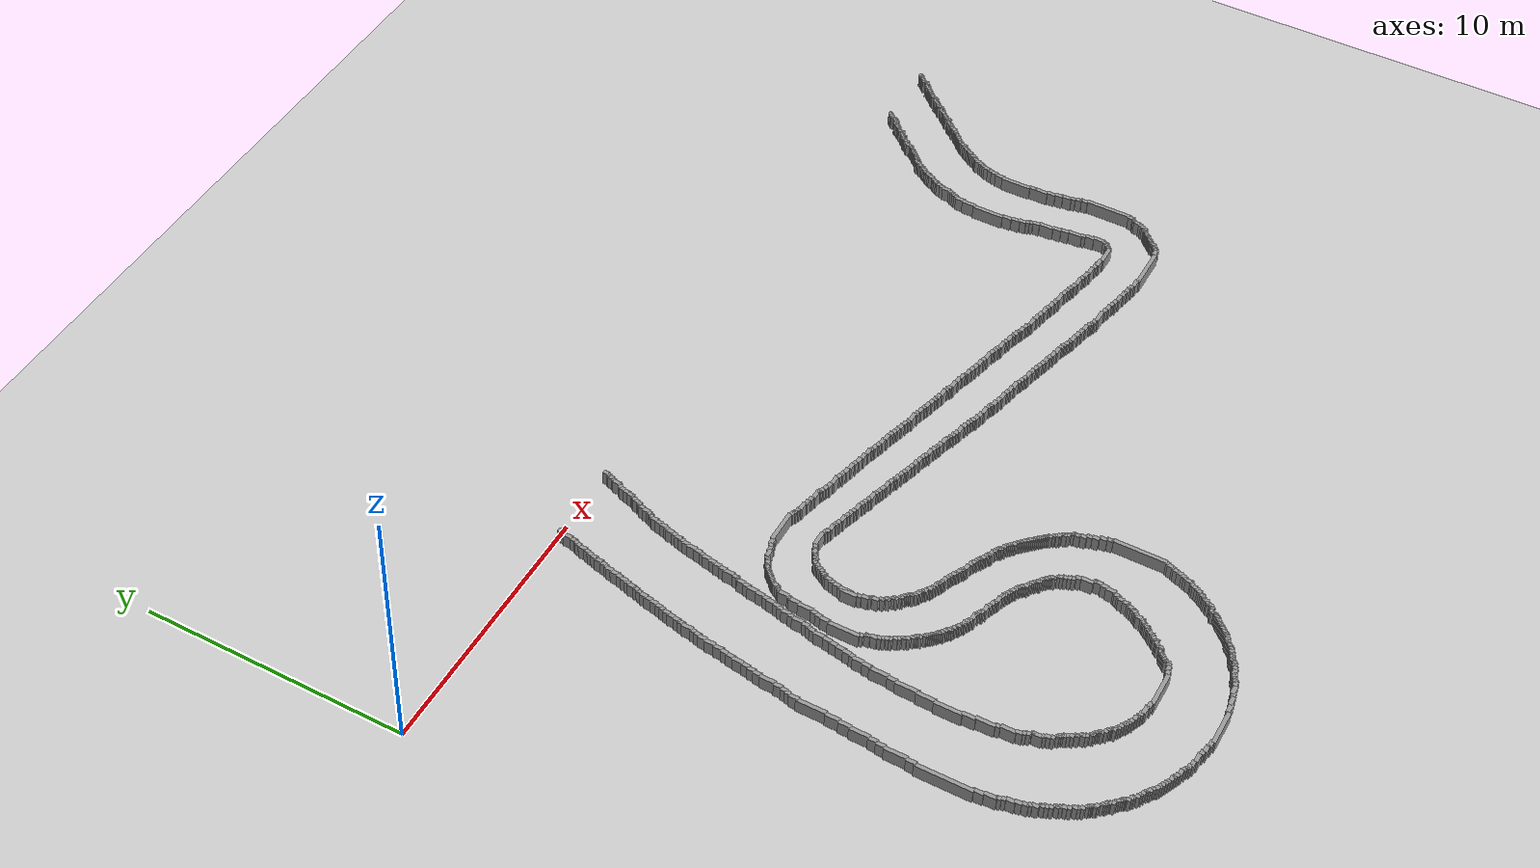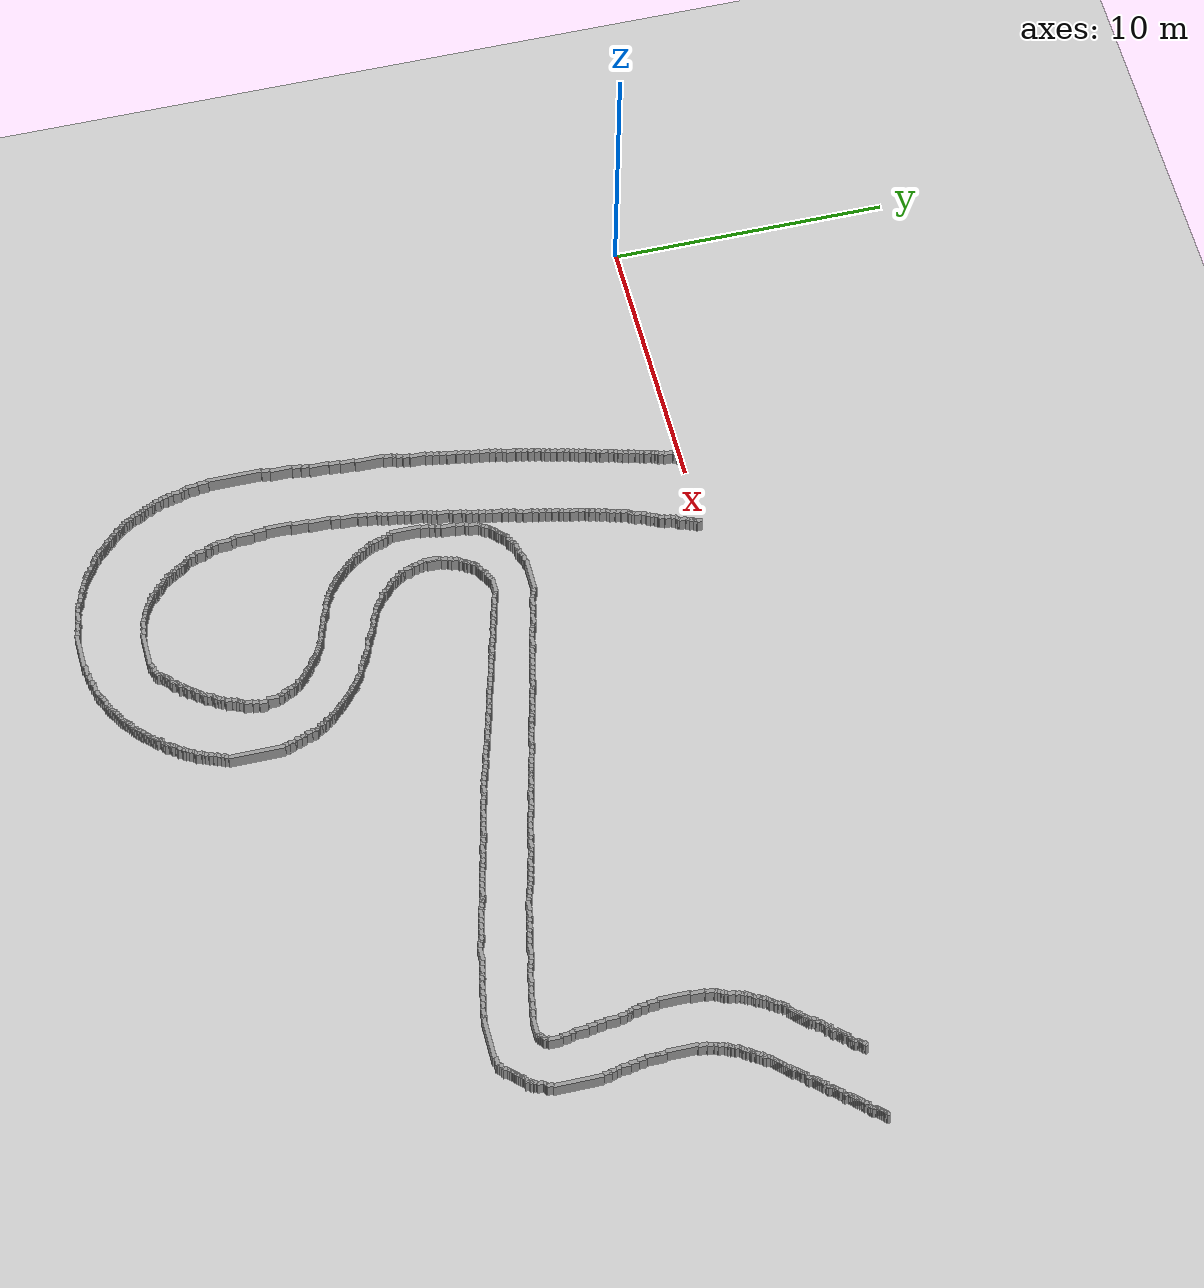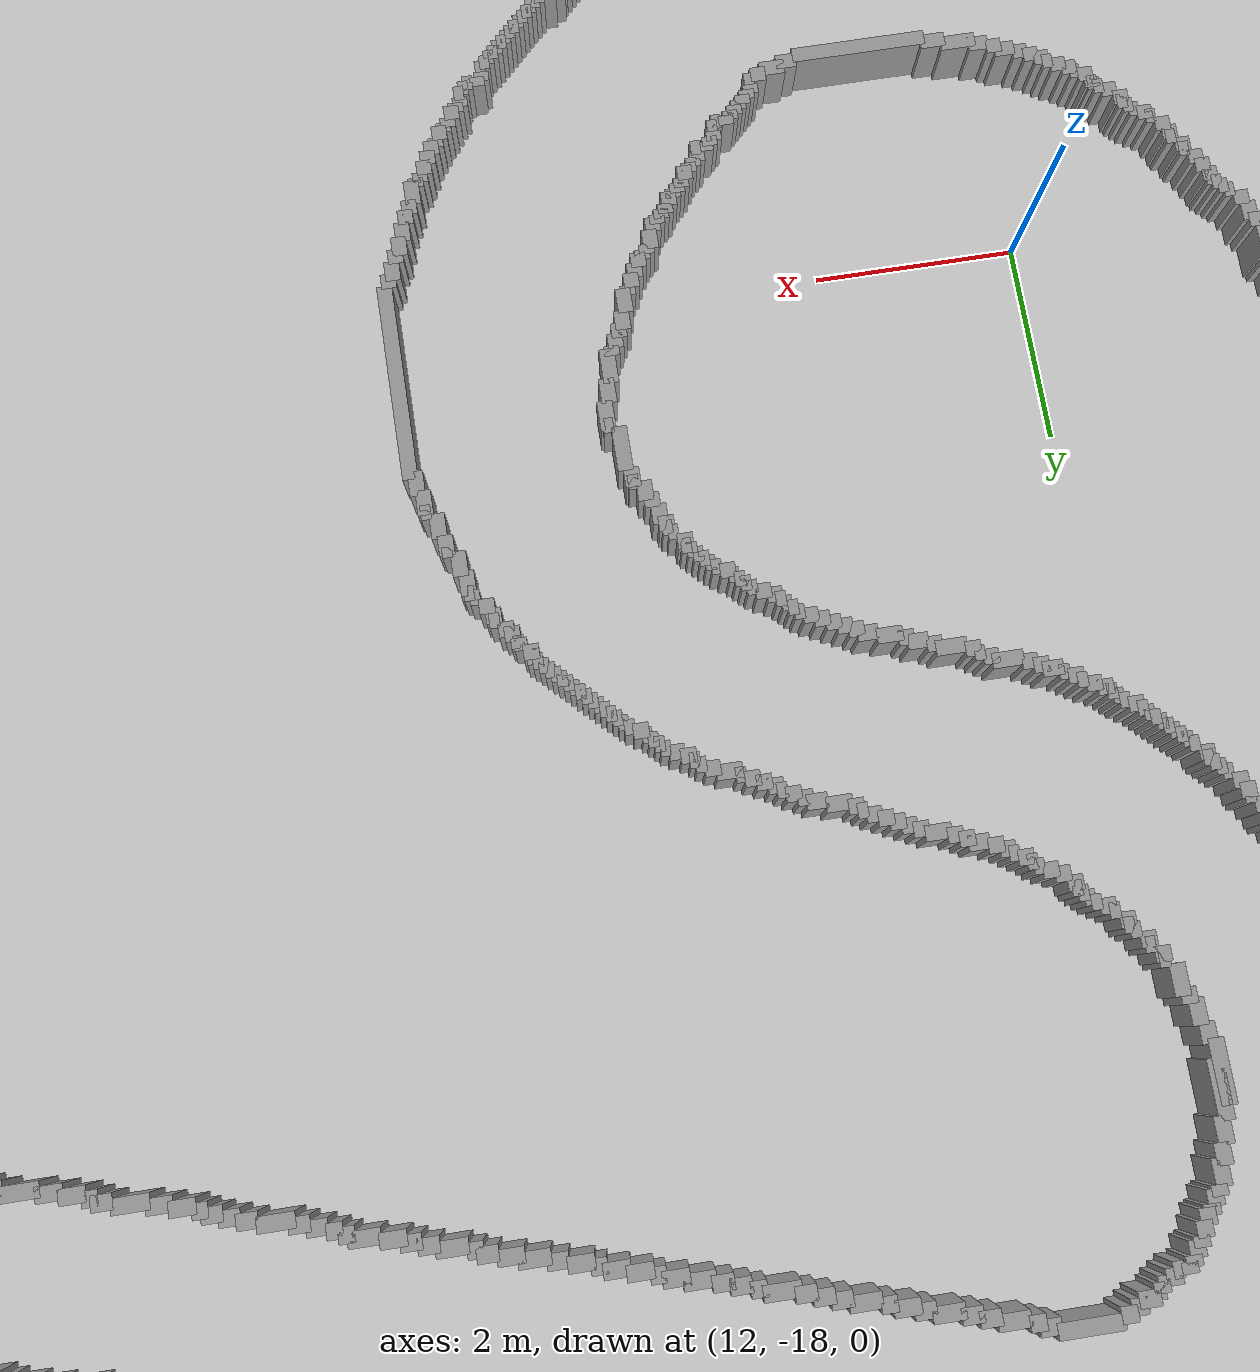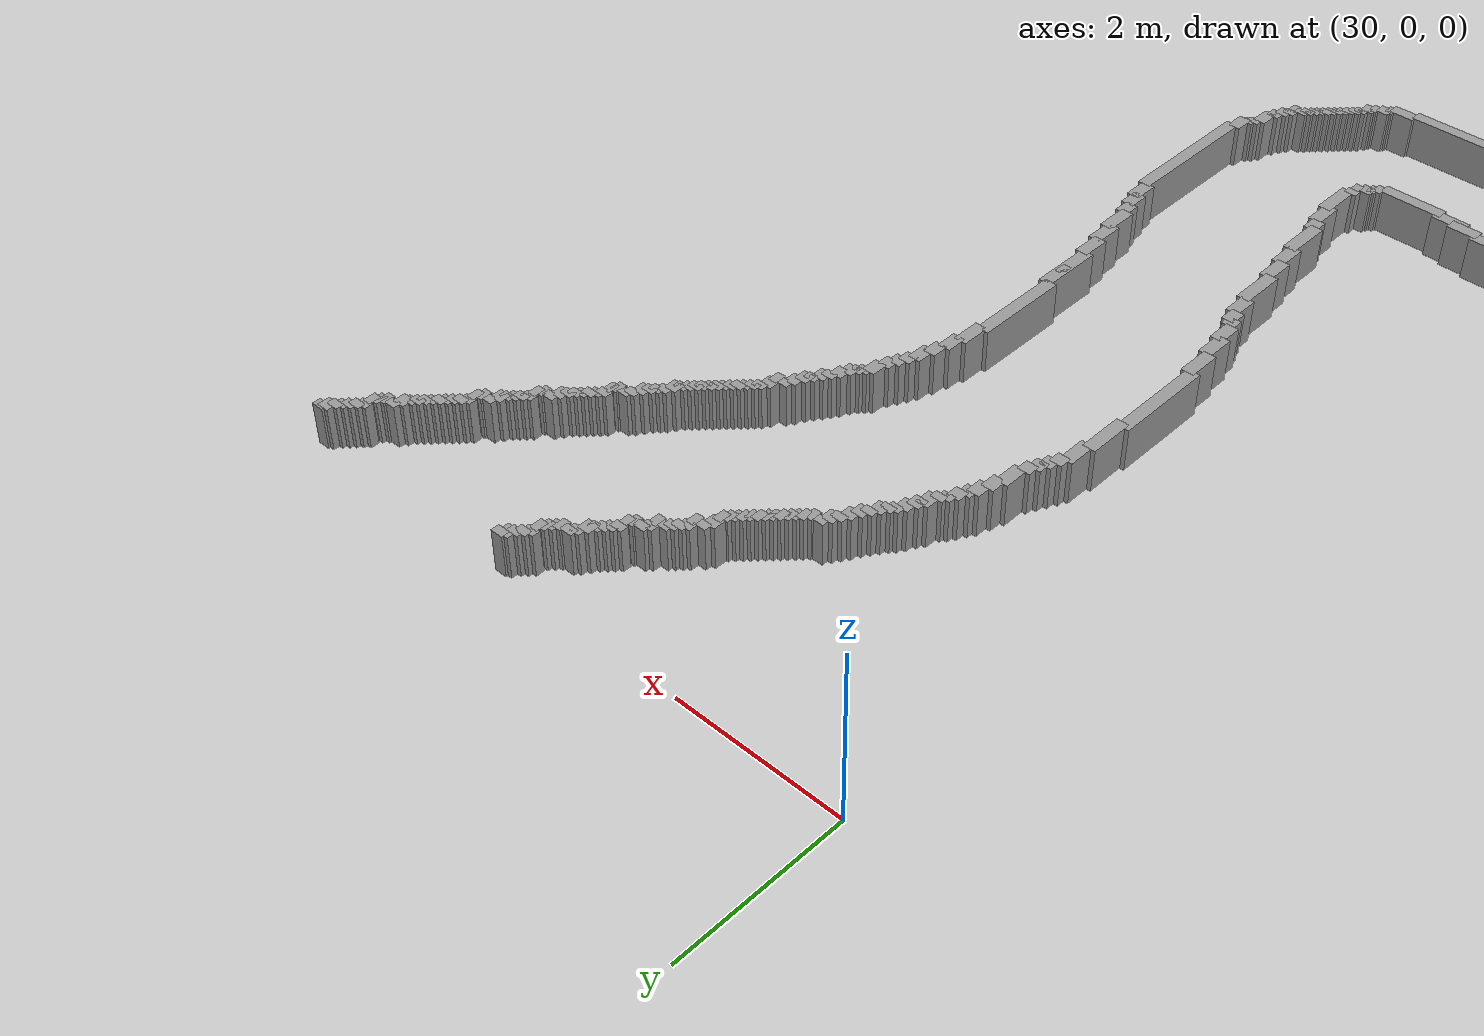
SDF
<sdf version="1.6">
  <world name="default">
    <include>
      <uri>model://sun</uri>
    </include>
    <include>
      <uri>model://ground_plane</uri>
    </include>
    <physics type="ode">
      <real_time_update_rate>1000.0</real_time_update_rate>
      <max_step_size>0.001</max_step_size>
      <real_time_factor>1</real_time_factor>
      <ode>
        <solver>
          <type>quick</type>
          <iters>150</iters>
          <precon_iters>0</precon_iters>
          <sor>1.400000</sor>
          <use_dynamic_moi_rescaling>1</use_dynamic_moi_rescaling>
        </solver>
        <constraints>
          <cfm>0.00001</cfm>
          <erp>0.2</erp>
          <contact_max_correcting_vel>2000.000000</contact_max_correcting_vel>
          <contact_surface_layer>0.01000</contact_surface_layer>
        </constraints>
      </ode>
    </physics>
    <scene>
      <ambient>0.4 0.4 0.4 1</ambient>
      <background>0.7 0.7 0.7 1</background>
      <shadows>true</shadows>
    </scene>
    <gui fullscreen="0">
      <camera name="user_camera">
        <pose>0.0 0.0 17.0 -1.5708 1.5708 0</pose>
        <view_controller>orbit</view_controller>
      </camera>
    </gui>
    <model name="obstacle">
      <static>1</static>
      <pose frame="">0 0 0 0 0 0</pose>
      <link name="obstacle">
        <collision name="obstacle_1">
          <pose>12.8 -22.450000000000003 0 0 0 0</pose>
          <geometry>
            <box>
              <size>1.35 0.15 1.0</size>
            </box>
          </geometry>
        </collision>
        <visual name="obstacle_1">
          <pose>12.8 -22.450000000000003 0 0 0 0</pose>
          <geometry>
            <box>
              <size>1.35 0.15 1.0</size>
            </box>
          </geometry>
          <material>
            <script>
              <uri>file://media/materials/scripts/gazebo.material</uri>
              <name>Gazebo/Grey</name>
            </script>
            <ambient>1 1 1 1</ambient>
          </material>
        </visual>
        <collision name="obstacle_2">
          <pose>12.05 -22.400000000000002 0 0 0 0</pose>
          <geometry>
            <box>
              <size>0.30000000000000004 0.15 1.0</size>
            </box>
          </geometry>
        </collision>
        <visual name="obstacle_2">
          <pose>12.05 -22.400000000000002 0 0 0 0</pose>
          <geometry>
            <box>
              <size>0.30000000000000004 0.15 1.0</size>
            </box>
          </geometry>
          <material>
            <script>
              <uri>file://media/materials/scripts/gazebo.material</uri>
              <name>Gazebo/Grey</name>
            </script>
            <ambient>1 1 1 1</ambient>
          </material>
        </visual>
        <collision name="obstacle_3">
          <pose>13.65 -22.400000000000002 0 0 0 0</pose>
          <geometry>
            <box>
              <size>0.4 0.15 1.0</size>
            </box>
          </geometry>
        </collision>
        <visual name="obstacle_3">
          <pose>13.65 -22.400000000000002 0 0 0 0</pose>
          <geometry>
            <box>
              <size>0.4 0.15 1.0</size>
            </box>
          </geometry>
          <material>
            <script>
              <uri>file://media/materials/scripts/gazebo.material</uri>
              <name>Gazebo/Grey</name>
            </script>
            <ambient>1 1 1 1</ambient>
          </material>
        </visual>
        <collision name="obstacle_4">
          <pose>11.8 -22.35 0 0 0 0</pose>
          <geometry>
            <box>
              <size>0.30000000000000004 0.15 1.0</size>
            </box>
          </geometry>
        </collision>
        <visual name="obstacle_4">
          <pose>11.8 -22.35 0 0 0 0</pose>
          <geometry>
            <box>
              <size>0.30000000000000004 0.15 1.0</size>
            </box>
          </geometry>
          <material>
            <script>
              <uri>file://media/materials/scripts/gazebo.material</uri>
              <name>Gazebo/Grey</name>
            </script>
            <ambient>1 1 1 1</ambient>
          </material>
        </visual>
        <collision name="obstacle_5">
          <pose>13.950000000000001 -22.35 0 0 0 0</pose>
          <geometry>
            <box>
              <size>0.35000000000000003 0.15 1.0</size>
            </box>
          </geometry>
        </collision>
        <visual name="obstacle_5">
          <pose>13.950000000000001 -22.35 0 0 0 0</pose>
          <geometry>
            <box>
              <size>0.35000000000000003 0.15 1.0</size>
            </box>
          </geometry>
          <material>
            <script>
              <uri>file://media/materials/scripts/gazebo.material</uri>
              <name>Gazebo/Grey</name>
            </script>
            <ambient>1 1 1 1</ambient>
          </material>
        </visual>
        <collision name="obstacle_6">
          <pose>11.600000000000001 -22.3 0 0 0 0</pose>
          <geometry>
            <box>
              <size>0.2 0.15 1.0</size>
            </box>
          </geometry>
        </collision>
        <visual name="obstacle_6">
          <pose>11.600000000000001 -22.3 0 0 0 0</pose>
          <geometry>
            <box>
              <size>0.2 0.15 1.0</size>
            </box>
          </geometry>
          <material>
            <script>
              <uri>file://media/materials/scripts/gazebo.material</uri>
              <name>Gazebo/Grey</name>
            </script>
            <ambient>1 1 1 1</ambient>
          </material>
        </visual>
        <collision name="obstacle_7">
          <pose>14.200000000000001 -22.3 0 0 0 0</pose>
          <geometry>
            <box>
              <size>0.2 0.15 1.0</size>
            </box>
          </geometry>
        </collision>
        <visual name="obstacle_7">
          <pose>14.200000000000001 -22.3 0 0 0 0</pose>
          <geometry>
            <box>
              <size>0.2 0.15 1.0</size>
            </box>
          </geometry>
          <material>
            <script>
              <uri>file://media/materials/scripts/gazebo.material</uri>
              <name>Gazebo/Grey</name>
            </script>
            <ambient>1 1 1 1</ambient>
          </material>
        </visual>
        <collision name="obstacle_8">
          <pose>11.350000000000001 -22.25 0 0 0 0</pose>
          <geometry>
            <box>
              <size>0.4 0.15 1.0</size>
            </box>
          </geometry>
        </collision>
        <visual name="obstacle_8">
          <pose>11.350000000000001 -22.25 0 0 0 0</pose>
          <geometry>
            <box>
              <size>0.4 0.15 1.0</size>
            </box>
          </geometry>
          <material>
            <script>
              <uri>file://media/materials/scripts/gazebo.material</uri>
              <name>Gazebo/Grey</name>
            </script>
            <ambient>1 1 1 1</ambient>
          </material>
        </visual>
        <collision name="obstacle_9">
          <pose>14.4 -22.25 0 0 0 0</pose>
          <geometry>
            <box>
              <size>0.35000000000000003 0.15 1.0</size>
            </box>
          </geometry>
        </collision>
        <visual name="obstacle_9">
          <pose>14.4 -22.25 0 0 0 0</pose>
          <geometry>
            <box>
              <size>0.35000000000000003 0.15 1.0</size>
            </box>
          </geometry>
          <material>
            <script>
              <uri>file://media/materials/scripts/gazebo.material</uri>
              <name>Gazebo/Grey</name>
            </script>
            <ambient>1 1 1 1</ambient>
          </material>
        </visual>
        <collision name="obstacle_10">
          <pose>11.05 -22.200000000000003 0 0 0 0</pose>
          <geometry>
            <box>
              <size>0.25 0.15 1.0</size>
            </box>
          </geometry>
        </collision>
        <visual name="obstacle_10">
          <pose>11.05 -22.200000000000003 0 0 0 0</pose>
          <geometry>
            <box>
              <size>0.25 0.15 1.0</size>
            </box>
          </geometry>
          <material>
            <script>
              <uri>file://media/materials/scripts/gazebo.material</uri>
              <name>Gazebo/Grey</name>
            </script>
            <ambient>1 1 1 1</ambient>
          </material>
        </visual>
        <collision name="obstacle_11">
          <pose>14.65 -22.200000000000003 0 0 0 0</pose>
          <geometry>
            <box>
              <size>0.2 0.15 1.0</size>
            </box>
          </geometry>
        </collision>
        <visual name="obstacle_11">
          <pose>14.65 -22.200000000000003 0 0 0 0</pose>
          <geometry>
            <box>
              <size>0.2 0.15 1.0</size>
            </box>
          </geometry>
          <material>
            <script>
              <uri>file://media/materials/scripts/gazebo.material</uri>
              <name>Gazebo/Grey</name>
            </script>
            <ambient>1 1 1 1</ambient>
          </material>
        </visual>
        <collision name="obstacle_12">
          <pose>10.9 -22.150000000000002 0 0 0 0</pose>
          <geometry>
            <box>
              <size>0.2 0.15 1.0</size>
            </box>
          </geometry>
        </collision>
        <visual name="obstacle_12">
          <pose>10.9 -22.150000000000002 0 0 0 0</pose>
          <geometry>
            <box>
              <size>0.2 0.15 1.0</size>
            </box>
          </geometry>
          <material>
            <script>
              <uri>file://media/materials/scripts/gazebo.material</uri>
              <name>Gazebo/Grey</name>
            </script>
            <ambient>1 1 1 1</ambient>
          </material>
        </visual>
        <collision name="obstacle_13">
          <pose>14.75 -22.150000000000002 0 0 0 0</pose>
          <geometry>
            <box>
              <size>0.15000000000000002 0.15 1.0</size>
            </box>
          </geometry>
        </collision>
        <visual name="obstacle_13">
          <pose>14.75 -22.150000000000002 0 0 0 0</pose>
          <geometry>
            <box>
              <size>0.15000000000000002 0.15 1.0</size>
            </box>
          </geometry>
          <material>
            <script>
              <uri>file://media/materials/scripts/gazebo.material</uri>
              <name>Gazebo/Grey</name>
            </script>
            <ambient>1 1 1 1</ambient>
          </material>
        </visual>
        <collision name="obstacle_14">
          <pose>10.8 -22.1 0 0 0 0</pose>
          <geometry>
            <box>
              <size>0.1 0.15 1.0</size>
            </box>
          </geometry>
        </collision>
        <visual name="obstacle_14">
          <pose>10.8 -22.1 0 0 0 0</pose>
          <geometry>
            <box>
              <size>0.1 0.15 1.0</size>
            </box>
          </geometry>
          <material>
            <script>
              <uri>file://media/materials/scripts/gazebo.material</uri>
              <name>Gazebo/Grey</name>
            </script>
            <ambient>1 1 1 1</ambient>
          </material>
        </visual>
        <collision name="obstacle_15">
          <pose>14.850000000000001 -22.1 0 0 0 0</pose>
          <geometry>
            <box>
              <size>0.1 0.15 1.0</size>
            </box>
          </geometry>
        </collision>
        <visual name="obstacle_15">
          <pose>14.850000000000001 -22.1 0 0 0 0</pose>
          <geometry>
            <box>
              <size>0.1 0.15 1.0</size>
            </box>
          </geometry>
          <material>
            <script>
              <uri>file://media/materials/scripts/gazebo.material</uri>
              <name>Gazebo/Grey</name>
            </script>
            <ambient>1 1 1 1</ambient>
          </material>
        </visual>
        <collision name="obstacle_16">
          <pose>10.700000000000001 -22.05 0 0 0 0</pose>
          <geometry>
            <box>
              <size>0.15000000000000002 0.15 1.0</size>
            </box>
          </geometry>
        </collision>
        <visual name="obstacle_16">
          <pose>10.700000000000001 -22.05 0 0 0 0</pose>
          <geometry>
            <box>
              <size>0.15000000000000002 0.15 1.0</size>
            </box>
          </geometry>
          <material>
            <script>
              <uri>file://media/materials/scripts/gazebo.material</uri>
              <name>Gazebo/Grey</name>
            </script>
            <ambient>1 1 1 1</ambient>
          </material>
        </visual>
        <collision name="obstacle_17">
          <pose>14.950000000000001 -22.05 0 0 0 0</pose>
          <geometry>
            <box>
              <size>0.2 0.15 1.0</size>
            </box>
          </geometry>
        </collision>
        <visual name="obstacle_17">
          <pose>14.950000000000001 -22.05 0 0 0 0</pose>
          <geometry>
            <box>
              <size>0.2 0.15 1.0</size>
            </box>
          </geometry>
          <material>
            <script>
              <uri>file://media/materials/scripts/gazebo.material</uri>
              <name>Gazebo/Grey</name>
            </script>
            <ambient>1 1 1 1</ambient>
          </material>
        </visual>
        <collision name="obstacle_18">
          <pose>10.55 -22.0 0 0 0 0</pose>
          <geometry>
            <box>
              <size>0.25 0.15 1.0</size>
            </box>
          </geometry>
        </collision>
        <visual name="obstacle_18">
          <pose>10.55 -22.0 0 0 0 0</pose>
          <geometry>
            <box>
              <size>0.25 0.15 1.0</size>
            </box>
          </geometry>
          <material>
            <script>
              <uri>file://media/materials/scripts/gazebo.material</uri>
              <name>Gazebo/Grey</name>
            </script>
            <ambient>1 1 1 1</ambient>
          </material>
        </visual>
        <collision name="obstacle_19">
          <pose>15.100000000000001 -22.0 0 0 0 0</pose>
          <geometry>
            <box>
              <size>0.25 0.15 1.0</size>
            </box>
          </geometry>
        </collision>
        <visual name="obstacle_19">
          <pose>15.100000000000001 -22.0 0 0 0 0</pose>
          <geometry>
            <box>
              <size>0.25 0.15 1.0</size>
            </box>
          </geometry>
          <material>
            <script>
              <uri>file://media/materials/scripts/gazebo.material</uri>
              <name>Gazebo/Grey</name>
            </script>
            <ambient>1 1 1 1</ambient>
          </material>
        </visual>
        <collision name="obstacle_20">
          <pose>10.4 -21.950000000000003 0 0 0 0</pose>
          <geometry>
            <box>
              <size>0.15000000000000002 0.15 1.0</size>
            </box>
          </geometry>
        </collision>
        <visual name="obstacle_20">
          <pose>10.4 -21.950000000000003 0 0 0 0</pose>
          <geometry>
            <box>
              <size>0.15000000000000002 0.15 1.0</size>
            </box>
          </geometry>
          <material>
            <script>
              <uri>file://media/materials/scripts/gazebo.material</uri>
              <name>Gazebo/Grey</name>
            </script>
            <ambient>1 1 1 1</ambient>
          </material>
        </visual>
        <collision name="obstacle_21">
          <pose>15.25 -21.950000000000003 0 0 0 0</pose>
          <geometry>
            <box>
              <size>0.15000000000000002 0.15 1.0</size>
            </box>
          </geometry>
        </collision>
        <visual name="obstacle_21">
          <pose>15.25 -21.950000000000003 0 0 0 0</pose>
          <geometry>
            <box>
              <size>0.15000000000000002 0.15 1.0</size>
            </box>
          </geometry>
          <material>
            <script>
              <uri>file://media/materials/scripts/gazebo.material</uri>
              <name>Gazebo/Grey</name>
            </script>
            <ambient>1 1 1 1</ambient>
          </material>
        </visual>
        <collision name="obstacle_22">
          <pose>10.3 -21.900000000000002 0 0 0 0</pose>
          <geometry>
            <box>
              <size>0.15000000000000002 0.15 1.0</size>
            </box>
          </geometry>
        </collision>
        <visual name="obstacle_22">
          <pose>10.3 -21.900000000000002 0 0 0 0</pose>
          <geometry>
            <box>
              <size>0.15000000000000002 0.15 1.0</size>
            </box>
          </geometry>
          <material>
            <script>
              <uri>file://media/materials/scripts/gazebo.material</uri>
              <name>Gazebo/Grey</name>
            </script>
            <ambient>1 1 1 1</ambient>
          </material>
        </visual>
        <collision name="obstacle_23">
          <pose>15.350000000000001 -21.900000000000002 0 0 0 0</pose>
          <geometry>
            <box>
              <size>0.15000000000000002 0.15 1.0</size>
            </box>
          </geometry>
        </collision>
        <visual name="obstacle_23">
          <pose>15.350000000000001 -21.900000000000002 0 0 0 0</pose>
          <geometry>
            <box>
              <size>0.15000000000000002 0.15 1.0</size>
            </box>
          </geometry>
          <material>
            <script>
              <uri>file://media/materials/scripts/gazebo.material</uri>
              <name>Gazebo/Grey</name>
            </script>
            <ambient>1 1 1 1</ambient>
          </material>
        </visual>
        <collision name="obstacle_24">
          <pose>10.200000000000001 -21.85 0 0 0 0</pose>
          <geometry>
            <box>
              <size>0.2 0.15 1.0</size>
            </box>
          </geometry>
        </collision>
        <visual name="obstacle_24">
          <pose>10.200000000000001 -21.85 0 0 0 0</pose>
          <geometry>
            <box>
              <size>0.2 0.15 1.0</size>
            </box>
          </geometry>
          <material>
            <script>
              <uri>file://media/materials/scripts/gazebo.material</uri>
              <name>Gazebo/Grey</name>
            </script>
            <ambient>1 1 1 1</ambient>
          </material>
        </visual>
        <collision name="obstacle_25">
          <pose>15.450000000000001 -21.85 0 0 0 0</pose>
          <geometry>
            <box>
              <size>0.1 0.15 1.0</size>
            </box>
          </geometry>
        </collision>
        <visual name="obstacle_25">
          <pose>15.450000000000001 -21.85 0 0 0 0</pose>
          <geometry>
            <box>
              <size>0.1 0.15 1.0</size>
            </box>
          </geometry>
          <material>
            <script>
              <uri>file://media/materials/scripts/gazebo.material</uri>
              <name>Gazebo/Grey</name>
            </script>
            <ambient>1 1 1 1</ambient>
          </material>
        </visual>
        <collision name="obstacle_26">
          <pose>10.05 -21.8 0 0 0 0</pose>
          <geometry>
            <box>
              <size>0.15000000000000002 0.15 1.0</size>
            </box>
          </geometry>
        </collision>
        <visual name="obstacle_26">
          <pose>10.05 -21.8 0 0 0 0</pose>
          <geometry>
            <box>
              <size>0.15000000000000002 0.15 1.0</size>
            </box>
          </geometry>
          <material>
            <script>
              <uri>file://media/materials/scripts/gazebo.material</uri>
              <name>Gazebo/Grey</name>
            </script>
            <ambient>1 1 1 1</ambient>
          </material>
        </visual>
        <collision name="obstacle_27">
          <pose>15.5 -21.8 0 0 0 0</pose>
          <geometry>
            <box>
              <size>0.1 0.15 1.0</size>
            </box>
          </geometry>
        </collision>
        <visual name="obstacle_27">
          <pose>15.5 -21.8 0 0 0 0</pose>
          <geometry>
            <box>
              <size>0.1 0.15 1.0</size>
            </box>
          </geometry>
          <material>
            <script>
              <uri>file://media/materials/scripts/gazebo.material</uri>
              <name>Gazebo/Grey</name>
            </script>
            <ambient>1 1 1 1</ambient>
          </material>
        </visual>
        <collision name="obstacle_28">
          <pose>9.950000000000001 -21.75 0 0 0 0</pose>
          <geometry>
            <box>
              <size>0.15000000000000002 0.15 1.0</size>
            </box>
          </geometry>
        </collision>
        <visual name="obstacle_28">
          <pose>9.950000000000001 -21.75 0 0 0 0</pose>
          <geometry>
            <box>
              <size>0.15000000000000002 0.15 1.0</size>
            </box>
          </geometry>
          <material>
            <script>
              <uri>file://media/materials/scripts/gazebo.material</uri>
              <name>Gazebo/Grey</name>
            </script>
            <ambient>1 1 1 1</ambient>
          </material>
        </visual>
        <collision name="obstacle_29">
          <pose>15.55 -21.75 0 0 0 0</pose>
          <geometry>
            <box>
              <size>0.15000000000000002 0.15 1.0</size>
            </box>
          </geometry>
        </collision>
        <visual name="obstacle_29">
          <pose>15.55 -21.75 0 0 0 0</pose>
          <geometry>
            <box>
              <size>0.15000000000000002 0.15 1.0</size>
            </box>
          </geometry>
          <material>
            <script>
              <uri>file://media/materials/scripts/gazebo.material</uri>
              <name>Gazebo/Grey</name>
            </script>
            <ambient>1 1 1 1</ambient>
          </material>
        </visual>
        <collision name="obstacle_30">
          <pose>9.850000000000001 -21.700000000000003 0 0 0 0</pose>
          <geometry>
            <box>
              <size>0.15000000000000002 0.15 1.0</size>
            </box>
          </geometry>
        </collision>
        <visual name="obstacle_30">
          <pose>9.850000000000001 -21.700000000000003 0 0 0 0</pose>
          <geometry>
            <box>
              <size>0.15000000000000002 0.15 1.0</size>
            </box>
          </geometry>
          <material>
            <script>
              <uri>file://media/materials/scripts/gazebo.material</uri>
              <name>Gazebo/Grey</name>
            </script>
            <ambient>1 1 1 1</ambient>
          </material>
        </visual>
        <collision name="obstacle_31">
          <pose>15.65 -21.700000000000003 0 0 0 0</pose>
          <geometry>
            <box>
              <size>0.15000000000000002 0.15 1.0</size>
            </box>
          </geometry>
        </collision>
        <visual name="obstacle_31">
          <pose>15.65 -21.700000000000003 0 0 0 0</pose>
          <geometry>
            <box>
              <size>0.15000000000000002 0.15 1.0</size>
            </box>
          </geometry>
          <material>
            <script>
              <uri>file://media/materials/scripts/gazebo.material</uri>
              <name>Gazebo/Grey</name>
            </script>
            <ambient>1 1 1 1</ambient>
          </material>
        </visual>
        <collision name="obstacle_32">
          <pose>9.75 -21.650000000000002 0 0 0 0</pose>
          <geometry>
            <box>
              <size>0.15000000000000002 0.15 1.0</size>
            </box>
          </geometry>
        </collision>
        <visual name="obstacle_32">
          <pose>9.75 -21.650000000000002 0 0 0 0</pose>
          <geometry>
            <box>
              <size>0.15000000000000002 0.15 1.0</size>
            </box>
          </geometry>
          <material>
            <script>
              <uri>file://media/materials/scripts/gazebo.material</uri>
              <name>Gazebo/Grey</name>
            </script>
            <ambient>1 1 1 1</ambient>
          </material>
        </visual>
        <collision name="obstacle_33">
          <pose>15.75 -21.650000000000002 0 0 0 0</pose>
          <geometry>
            <box>
              <size>0.15000000000000002 0.15 1.0</size>
            </box>
          </geometry>
        </collision>
        <visual name="obstacle_33">
          <pose>15.75 -21.650000000000002 0 0 0 0</pose>
          <geometry>
            <box>
              <size>0.15000000000000002 0.15 1.0</size>
            </box>
          </geometry>
          <material>
            <script>
              <uri>file://media/materials/scripts/gazebo.material</uri>
              <name>Gazebo/Grey</name>
            </script>
            <ambient>1 1 1 1</ambient>
          </material>
        </visual>
        <collision name="obstacle_34">
          <pose>9.65 -21.6 0 0 0 0</pose>
          <geometry>
            <box>
              <size>0.15000000000000002 0.15 1.0</size>
            </box>
          </geometry>
        </collision>
        <visual name="obstacle_34">
          <pose>9.65 -21.6 0 0 0 0</pose>
          <geometry>
            <box>
              <size>0.15000000000000002 0.15 1.0</size>
            </box>
          </geometry>
          <material>
            <script>
              <uri>file://media/materials/scripts/gazebo.material</uri>
              <name>Gazebo/Grey</name>
            </script>
            <ambient>1 1 1 1</ambient>
          </material>
        </visual>
        <collision name="obstacle_35">
          <pose>15.850000000000001 -21.6 0 0 0 0</pose>
          <geometry>
            <box>
              <size>0.15000000000000002 0.15 1.0</size>
            </box>
          </geometry>
        </collision>
        <visual name="obstacle_35">
          <pose>15.850000000000001 -21.6 0 0 0 0</pose>
          <geometry>
            <box>
              <size>0.15000000000000002 0.15 1.0</size>
            </box>
          </geometry>
          <material>
            <script>
              <uri>file://media/materials/scripts/gazebo.material</uri>
              <name>Gazebo/Grey</name>
            </script>
            <ambient>1 1 1 1</ambient>
          </material>
        </visual>
        <collision name="obstacle_36">
          <pose>9.600000000000001 -21.55 0 0 0 0</pose>
          <geometry>
            <box>
              <size>0.1 0.15 1.0</size>
            </box>
          </geometry>
        </collision>
        <visual name="obstacle_36">
          <pose>9.600000000000001 -21.55 0 0 0 0</pose>
          <geometry>
            <box>
              <size>0.1 0.15 1.0</size>
            </box>
          </geometry>
          <material>
            <script>
              <uri>file://media/materials/scripts/gazebo.material</uri>
              <name>Gazebo/Grey</name>
            </script>
            <ambient>1 1 1 1</ambient>
          </material>
        </visual>
        <collision name="obstacle_37">
          <pose>15.950000000000001 -21.55 0 0 0 0</pose>
          <geometry>
            <box>
              <size>0.1 0.15 1.0</size>
            </box>
          </geometry>
        </collision>
        <visual name="obstacle_37">
          <pose>15.950000000000001 -21.55 0 0 0 0</pose>
          <geometry>
            <box>
              <size>0.1 0.15 1.0</size>
            </box>
          </geometry>
          <material>
            <script>
              <uri>file://media/materials/scripts/gazebo.material</uri>
              <name>Gazebo/Grey</name>
            </script>
            <ambient>1 1 1 1</ambient>
          </material>
        </visual>
        <collision name="obstacle_38">
          <pose>9.55 -21.5 0 0 0 0</pose>
          <geometry>
            <box>
              <size>0.1 0.15 1.0</size>
            </box>
          </geometry>
        </collision>
        <visual name="obstacle_38">
          <pose>9.55 -21.5 0 0 0 0</pose>
          <geometry>
            <box>
              <size>0.1 0.15 1.0</size>
            </box>
          </geometry>
          <material>
            <script>
              <uri>file://media/materials/scripts/gazebo.material</uri>
              <name>Gazebo/Grey</name>
            </script>
            <ambient>1 1 1 1</ambient>
          </material>
        </visual>
        <collision name="obstacle_39">
          <pose>16.0 -21.5 0 0 0 0</pose>
          <geometry>
            <box>
              <size>0.1 0.15 1.0</size>
            </box>
          </geometry>
        </collision>
        <visual name="obstacle_39">
          <pose>16.0 -21.5 0 0 0 0</pose>
          <geometry>
            <box>
              <size>0.1 0.15 1.0</size>
            </box>
          </geometry>
          <material>
            <script>
              <uri>file://media/materials/scripts/gazebo.material</uri>
              <name>Gazebo/Grey</name>
            </script>
            <ambient>1 1 1 1</ambient>
          </material>
        </visual>
        <collision name="obstacle_40">
          <pose>9.450000000000001 -21.450000000000003 0 0 0 0</pose>
          <geometry>
            <box>
              <size>0.15000000000000002 0.15 1.0</size>
            </box>
          </geometry>
        </collision>
        <visual name="obstacle_40">
          <pose>9.450000000000001 -21.450000000000003 0 0 0 0</pose>
          <geometry>
            <box>
              <size>0.15000000000000002 0.15 1.0</size>
            </box>
          </geometry>
          <material>
            <script>
              <uri>file://media/materials/scripts/gazebo.material</uri>
              <name>Gazebo/Grey</name>
            </script>
            <ambient>1 1 1 1</ambient>
          </material>
        </visual>
        <collision name="obstacle_41">
          <pose>16.05 -21.450000000000003 0 0 0 0</pose>
          <geometry>
            <box>
              <size>0.1 0.15 1.0</size>
            </box>
          </geometry>
        </collision>
        <visual name="obstacle_41">
          <pose>16.05 -21.450000000000003 0 0 0 0</pose>
          <geometry>
            <box>
              <size>0.1 0.15 1.0</size>
            </box>
          </geometry>
          <material>
            <script>
              <uri>file://media/materials/scripts/gazebo.material</uri>
              <name>Gazebo/Grey</name>
            </script>
            <ambient>1 1 1 1</ambient>
          </material>
        </visual>
        <collision name="obstacle_42">
          <pose>9.4 -21.400000000000002 0 0 0 0</pose>
          <geometry>
            <box>
              <size>0.1 0.15 1.0</size>
            </box>
          </geometry>
        </collision>
        <visual name="obstacle_42">
          <pose>9.4 -21.400000000000002 0 0 0 0</pose>
          <geometry>
            <box>
              <size>0.1 0.15 1.0</size>
            </box>
          </geometry>
          <material>
            <script>
              <uri>file://media/materials/scripts/gazebo.material</uri>
              <name>Gazebo/Grey</name>
            </script>
            <ambient>1 1 1 1</ambient>
          </material>
        </visual>
        <collision name="obstacle_43">
          <pose>16.1 -21.400000000000002 0 0 0 0</pose>
          <geometry>
            <box>
              <size>0.1 0.15 1.0</size>
            </box>
          </geometry>
        </collision>
        <visual name="obstacle_43">
          <pose>16.1 -21.400000000000002 0 0 0 0</pose>
          <geometry>
            <box>
              <size>0.1 0.15 1.0</size>
            </box>
          </geometry>
          <material>
            <script>
              <uri>file://media/materials/scripts/gazebo.material</uri>
              <name>Gazebo/Grey</name>
            </script>
            <ambient>1 1 1 1</ambient>
          </material>
        </visual>
        <collision name="obstacle_44">
          <pose>9.35 -21.35 0 0 0 0</pose>
          <geometry>
            <box>
              <size>0.1 0.15 1.0</size>
            </box>
          </geometry>
        </collision>
        <visual name="obstacle_44">
          <pose>9.35 -21.35 0 0 0 0</pose>
          <geometry>
            <box>
              <size>0.1 0.15 1.0</size>
            </box>
          </geometry>
          <material>
            <script>
              <uri>file://media/materials/scripts/gazebo.material</uri>
              <name>Gazebo/Grey</name>
            </script>
            <ambient>1 1 1 1</ambient>
          </material>
        </visual>
        <collision name="obstacle_45">
          <pose>16.150000000000002 -21.35 0 0 0 0</pose>
          <geometry>
            <box>
              <size>0.15000000000000002 0.15 1.0</size>
            </box>
          </geometry>
        </collision>
        <visual name="obstacle_45">
          <pose>16.150000000000002 -21.35 0 0 0 0</pose>
          <geometry>
            <box>
              <size>0.15000000000000002 0.15 1.0</size>
            </box>
          </geometry>
          <material>
            <script>
              <uri>file://media/materials/scripts/gazebo.material</uri>
              <name>Gazebo/Grey</name>
            </script>
            <ambient>1 1 1 1</ambient>
          </material>
        </visual>
        <collision name="obstacle_46">
          <pose>9.25 -21.3 0 0 0 0</pose>
          <geometry>
            <box>
              <size>0.15000000000000002 0.15 1.0</size>
            </box>
          </geometry>
        </collision>
        <visual name="obstacle_46">
          <pose>9.25 -21.3 0 0 0 0</pose>
          <geometry>
            <box>
              <size>0.15000000000000002 0.15 1.0</size>
            </box>
          </geometry>
          <material>
            <script>
              <uri>file://media/materials/scripts/gazebo.material</uri>
              <name>Gazebo/Grey</name>
            </script>
            <ambient>1 1 1 1</ambient>
          </material>
        </visual>
        <collision name="obstacle_47">
          <pose>16.25 -21.3 0 0 0 0</pose>
          <geometry>
            <box>
              <size>0.15000000000000002 0.15 1.0</size>
            </box>
          </geometry>
        </collision>
        <visual name="obstacle_47">
          <pose>16.25 -21.3 0 0 0 0</pose>
          <geometry>
            <box>
              <size>0.15000000000000002 0.15 1.0</size>
            </box>
          </geometry>
          <material>
            <script>
              <uri>file://media/materials/scripts/gazebo.material</uri>
              <name>Gazebo/Grey</name>
            </script>
            <ambient>1 1 1 1</ambient>
          </material>
        </visual>
        <collision name="obstacle_48">
          <pose>9.15 -21.25 0 0 0 0</pose>
          <geometry>
            <box>
              <size>0.15000000000000002 0.15 1.0</size>
            </box>
          </geometry>
        </collision>
        <visual name="obstacle_48">
          <pose>9.15 -21.25 0 0 0 0</pose>
          <geometry>
            <box>
              <size>0.15000000000000002 0.15 1.0</size>
            </box>
          </geometry>
          <material>
            <script>
              <uri>file://media/materials/scripts/gazebo.material</uri>
              <name>Gazebo/Grey</name>
            </script>
            <ambient>1 1 1 1</ambient>
          </material>
        </visual>
        <collision name="obstacle_49">
          <pose>16.35 -21.25 0 0 0 0</pose>
          <geometry>
            <box>
              <size>0.1 0.15 1.0</size>
            </box>
          </geometry>
        </collision>
        <visual name="obstacle_49">
          <pose>16.35 -21.25 0 0 0 0</pose>
          <geometry>
            <box>
              <size>0.1 0.15 1.0</size>
            </box>
          </geometry>
          <material>
            <script>
              <uri>file://media/materials/scripts/gazebo.material</uri>
              <name>Gazebo/Grey</name>
            </script>
            <ambient>1 1 1 1</ambient>
          </material>
        </visual>
        <collision name="obstacle_50">
          <pose>9.05 -21.200000000000003 0 0 0 0</pose>
          <geometry>
            <box>
              <size>0.15000000000000002 0.15 1.0</size>
            </box>
          </geometry>
        </collision>
        <visual name="obstacle_50">
          <pose>9.05 -21.200000000000003 0 0 0 0</pose>
          <geometry>
            <box>
              <size>0.15000000000000002 0.15 1.0</size>
            </box>
          </geometry>
          <material>
            <script>
              <uri>file://media/materials/scripts/gazebo.material</uri>
              <name>Gazebo/Grey</name>
            </script>
            <ambient>1 1 1 1</ambient>
          </material>
        </visual>
        <collision name="obstacle_51">
          <pose>16.400000000000002 -21.200000000000003 0 0 0 0</pose>
          <geometry>
            <box>
              <size>0.1 0.15 1.0</size>
            </box>
          </geometry>
        </collision>
        <visual name="obstacle_51">
          <pose>16.400000000000002 -21.200000000000003 0 0 0 0</pose>
          <geometry>
            <box>
              <size>0.1 0.15 1.0</size>
            </box>
          </geometry>
          <material>
            <script>
              <uri>file://media/materials/scripts/gazebo.material</uri>
              <name>Gazebo/Grey</name>
            </script>
            <ambient>1 1 1 1</ambient>
          </material>
        </visual>
        <collision name="obstacle_52">
          <pose>8.950000000000001 -21.1 0 0 0 1.5708</pose>
          <geometry>
            <box>
              <size>0.15000000000000002 0.15 1.0</size>
            </box>
          </geometry>
        </collision>
        <visual name="obstacle_52">
          <pose>8.950000000000001 -21.1 0 0 0 1.5708</pose>
          <geometry>
            <box>
              <size>0.15000000000000002 0.15 1.0</size>
            </box>
          </geometry>
          <material>
            <script>
              <uri>file://media/materials/scripts/gazebo.material</uri>
              <name>Gazebo/Grey</name>
            </script>
            <ambient>1 1 1 1</ambient>
          </material>
        </visual>
        <collision name="obstacle_54">
          <pose>16.45 -21.150000000000002 0 0 0 0</pose>
          <geometry>
            <box>
              <size>0.1 0.15 1.0</size>
            </box>
          </geometry>
        </collision>
        <visual name="obstacle_54">
          <pose>16.45 -21.150000000000002 0 0 0 0</pose>
          <geometry>
            <box>
              <size>0.1 0.15 1.0</size>
            </box>
          </geometry>
          <material>
            <script>
              <uri>file://media/materials/scripts/gazebo.material</uri>
              <name>Gazebo/Grey</name>
            </script>
            <ambient>1 1 1 1</ambient>
          </material>
        </visual>
        <collision name="obstacle_55">
          <pose>16.5 -21.1 0 0 0 0</pose>
          <geometry>
            <box>
              <size>0.1 0.15 1.0</size>
            </box>
          </geometry>
        </collision>
        <visual name="obstacle_55">
          <pose>16.5 -21.1 0 0 0 0</pose>
          <geometry>
            <box>
              <size>0.1 0.15 1.0</size>
            </box>
          </geometry>
          <material>
            <script>
              <uri>file://media/materials/scripts/gazebo.material</uri>
              <name>Gazebo/Grey</name>
            </script>
            <ambient>1 1 1 1</ambient>
          </material>
        </visual>
        <collision name="obstacle_56">
          <pose>8.9 -21.05 0 0 0 0</pose>
          <geometry>
            <box>
              <size>0.15000000000000002 0.15 1.0</size>
            </box>
          </geometry>
        </collision>
        <visual name="obstacle_56">
          <pose>8.9 -21.05 0 0 0 0</pose>
          <geometry>
            <box>
              <size>0.15000000000000002 0.15 1.0</size>
            </box>
          </geometry>
          <material>
            <script>
              <uri>file://media/materials/scripts/gazebo.material</uri>
              <name>Gazebo/Grey</name>
            </script>
            <ambient>1 1 1 1</ambient>
          </material>
        </visual>
        <collision name="obstacle_57">
          <pose>16.55 -21.05 0 0 0 0</pose>
          <geometry>
            <box>
              <size>0.1 0.15 1.0</size>
            </box>
          </geometry>
        </collision>
        <visual name="obstacle_57">
          <pose>16.55 -21.05 0 0 0 0</pose>
          <geometry>
            <box>
              <size>0.1 0.15 1.0</size>
            </box>
          </geometry>
          <material>
            <script>
              <uri>file://media/materials/scripts/gazebo.material</uri>
              <name>Gazebo/Grey</name>
            </script>
            <ambient>1 1 1 1</ambient>
          </material>
        </visual>
        <collision name="obstacle_58">
          <pose>8.8 -21.0 0 0 0 0</pose>
          <geometry>
            <box>
              <size>0.15000000000000002 0.15 1.0</size>
            </box>
          </geometry>
        </collision>
        <visual name="obstacle_58">
          <pose>8.8 -21.0 0 0 0 0</pose>
          <geometry>
            <box>
              <size>0.15000000000000002 0.15 1.0</size>
            </box>
          </geometry>
          <material>
            <script>
              <uri>file://media/materials/scripts/gazebo.material</uri>
              <name>Gazebo/Grey</name>
            </script>
            <ambient>1 1 1 1</ambient>
          </material>
        </visual>
        <collision name="obstacle_59">
          <pose>16.6 -21.0 0 0 0 0</pose>
          <geometry>
            <box>
              <size>0.1 0.15 1.0</size>
            </box>
          </geometry>
        </collision>
        <visual name="obstacle_59">
          <pose>16.6 -21.0 0 0 0 0</pose>
          <geometry>
            <box>
              <size>0.1 0.15 1.0</size>
            </box>
          </geometry>
          <material>
            <script>
              <uri>file://media/materials/scripts/gazebo.material</uri>
              <name>Gazebo/Grey</name>
            </script>
            <ambient>1 1 1 1</ambient>
          </material>
        </visual>
        <collision name="obstacle_60">
          <pose>8.75 -20.900000000000002 0 0 0 1.5708</pose>
          <geometry>
            <box>
              <size>0.1 0.15 1.0</size>
            </box>
          </geometry>
        </collision>
        <visual name="obstacle_60">
          <pose>8.75 -20.900000000000002 0 0 0 1.5708</pose>
          <geometry>
            <box>
              <size>0.1 0.15 1.0</size>
            </box>
          </geometry>
          <material>
            <script>
              <uri>file://media/materials/scripts/gazebo.material</uri>
              <name>Gazebo/Grey</name>
            </script>
            <ambient>1 1 1 1</ambient>
          </material>
        </visual>
        <collision name="obstacle_61">
          <pose>16.650000000000002 -20.950000000000003 0 0 0 0</pose>
          <geometry>
            <box>
              <size>0.1 0.15 1.0</size>
            </box>
          </geometry>
        </collision>
        <visual name="obstacle_61">
          <pose>16.650000000000002 -20.950000000000003 0 0 0 0</pose>
          <geometry>
            <box>
              <size>0.1 0.15 1.0</size>
            </box>
          </geometry>
          <material>
            <script>
              <uri>file://media/materials/scripts/gazebo.material</uri>
              <name>Gazebo/Grey</name>
            </script>
            <ambient>1 1 1 1</ambient>
          </material>
        </visual>
        <collision name="obstacle_62">
          <pose>8.75 -20.900000000000002 0 0 0 0</pose>
          <geometry>
            <box>
              <size>0.1 0.15 1.0</size>
            </box>
          </geometry>
        </collision>
        <visual name="obstacle_62">
          <pose>8.75 -20.900000000000002 0 0 0 0</pose>
          <geometry>
            <box>
              <size>0.1 0.15 1.0</size>
            </box>
          </geometry>
          <material>
            <script>
              <uri>file://media/materials/scripts/gazebo.material</uri>
              <name>Gazebo/Grey</name>
            </script>
            <ambient>1 1 1 1</ambient>
          </material>
        </visual>
        <collision name="obstacle_63">
          <pose>16.7 -20.900000000000002 0 0 0 0</pose>
          <geometry>
            <box>
              <size>0.1 0.15 1.0</size>
            </box>
          </geometry>
        </collision>
        <visual name="obstacle_63">
          <pose>16.7 -20.900000000000002 0 0 0 0</pose>
          <geometry>
            <box>
              <size>0.1 0.15 1.0</size>
            </box>
          </geometry>
          <material>
            <script>
              <uri>file://media/materials/scripts/gazebo.material</uri>
              <name>Gazebo/Grey</name>
            </script>
            <ambient>1 1 1 1</ambient>
          </material>
        </visual>
        <collision name="obstacle_64">
          <pose>8.700000000000001 -20.85 0 0 0 0</pose>
          <geometry>
            <box>
              <size>0.1 0.15 1.0</size>
            </box>
          </geometry>
        </collision>
        <visual name="obstacle_64">
          <pose>8.700000000000001 -20.85 0 0 0 0</pose>
          <geometry>
            <box>
              <size>0.1 0.15 1.0</size>
            </box>
          </geometry>
          <material>
            <script>
              <uri>file://media/materials/scripts/gazebo.material</uri>
              <name>Gazebo/Grey</name>
            </script>
            <ambient>1 1 1 1</ambient>
          </material>
        </visual>
        <collision name="obstacle_65">
          <pose>16.75 -20.85 0 0 0 0</pose>
          <geometry>
            <box>
              <size>0.1 0.15 1.0</size>
            </box>
          </geometry>
        </collision>
        <visual name="obstacle_65">
          <pose>16.75 -20.85 0 0 0 0</pose>
          <geometry>
            <box>
              <size>0.1 0.15 1.0</size>
            </box>
          </geometry>
          <material>
            <script>
              <uri>file://media/materials/scripts/gazebo.material</uri>
              <name>Gazebo/Grey</name>
            </script>
            <ambient>1 1 1 1</ambient>
          </material>
        </visual>
        <collision name="obstacle_66">
          <pose>8.65 -20.8 0 0 0 0</pose>
          <geometry>
            <box>
              <size>0.1 0.15 1.0</size>
            </box>
          </geometry>
        </collision>
        <visual name="obstacle_66">
          <pose>8.65 -20.8 0 0 0 0</pose>
          <geometry>
            <box>
              <size>0.1 0.15 1.0</size>
            </box>
          </geometry>
          <material>
            <script>
              <uri>file://media/materials/scripts/gazebo.material</uri>
              <name>Gazebo/Grey</name>
            </script>
            <ambient>1 1 1 1</ambient>
          </material>
        </visual>
        <collision name="obstacle_67">
          <pose>16.8 -20.8 0 0 0 0</pose>
          <geometry>
            <box>
              <size>0.1 0.15 1.0</size>
            </box>
          </geometry>
        </collision>
        <visual name="obstacle_67">
          <pose>16.8 -20.8 0 0 0 0</pose>
          <geometry>
            <box>
              <size>0.1 0.15 1.0</size>
            </box>
          </geometry>
          <material>
            <script>
              <uri>file://media/materials/scripts/gazebo.material</uri>
              <name>Gazebo/Grey</name>
            </script>
            <ambient>1 1 1 1</ambient>
          </material>
        </visual>
        <collision name="obstacle_68">
          <pose>8.6 -20.75 0 0 0 0</pose>
          <geometry>
            <box>
              <size>0.1 0.15 1.0</size>
            </box>
          </geometry>
        </collision>
        <visual name="obstacle_68">
          <pose>8.6 -20.75 0 0 0 0</pose>
          <geometry>
            <box>
              <size>0.1 0.15 1.0</size>
            </box>
          </geometry>
          <material>
            <script>
              <uri>file://media/materials/scripts/gazebo.material</uri>
              <name>Gazebo/Grey</name>
            </script>
            <ambient>1 1 1 1</ambient>
          </material>
        </visual>
        <collision name="obstacle_69">
          <pose>16.85 -20.75 0 0 0 0</pose>
          <geometry>
            <box>
              <size>0.1 0.15 1.0</size>
            </box>
          </geometry>
        </collision>
        <visual name="obstacle_69">
          <pose>16.85 -20.75 0 0 0 0</pose>
          <geometry>
            <box>
              <size>0.1 0.15 1.0</size>
            </box>
          </geometry>
          <material>
            <script>
              <uri>file://media/materials/scripts/gazebo.material</uri>
              <name>Gazebo/Grey</name>
            </script>
            <ambient>1 1 1 1</ambient>
          </material>
        </visual>
        <collision name="obstacle_70">
          <pose>8.55 -20.700000000000003 0 0 0 0</pose>
          <geometry>
            <box>
              <size>0.1 0.15 1.0</size>
            </box>
          </geometry>
        </collision>
        <visual name="obstacle_70">
          <pose>8.55 -20.700000000000003 0 0 0 0</pose>
          <geometry>
            <box>
              <size>0.1 0.15 1.0</size>
            </box>
          </geometry>
          <material>
            <script>
              <uri>file://media/materials/scripts/gazebo.material</uri>
              <name>Gazebo/Grey</name>
            </script>
            <ambient>1 1 1 1</ambient>
          </material>
        </visual>
        <collision name="obstacle_71">
          <pose>16.900000000000002 -20.700000000000003 0 0 0 0</pose>
          <geometry>
            <box>
              <size>0.1 0.15 1.0</size>
            </box>
          </geometry>
        </collision>
        <visual name="obstacle_71">
          <pose>16.900000000000002 -20.700000000000003 0 0 0 0</pose>
          <geometry>
            <box>
              <size>0.1 0.15 1.0</size>
            </box>
          </geometry>
          <material>
            <script>
              <uri>file://media/materials/scripts/gazebo.material</uri>
              <name>Gazebo/Grey</name>
            </script>
            <ambient>1 1 1 1</ambient>
          </material>
        </visual>
        <collision name="obstacle_72">
          <pose>8.450000000000001 -20.650000000000002 0 0 0 0</pose>
          <geometry>
            <box>
              <size>0.15000000000000002 0.15 1.0</size>
            </box>
          </geometry>
        </collision>
        <visual name="obstacle_72">
          <pose>8.450000000000001 -20.650000000000002 0 0 0 0</pose>
          <geometry>
            <box>
              <size>0.15000000000000002 0.15 1.0</size>
            </box>
          </geometry>
          <material>
            <script>
              <uri>file://media/materials/scripts/gazebo.material</uri>
              <name>Gazebo/Grey</name>
            </script>
            <ambient>1 1 1 1</ambient>
          </material>
        </visual>
        <collision name="obstacle_73">
          <pose>16.95 -20.650000000000002 0 0 0 0</pose>
          <geometry>
            <box>
              <size>0.1 0.15 1.0</size>
            </box>
          </geometry>
        </collision>
        <visual name="obstacle_73">
          <pose>16.95 -20.650000000000002 0 0 0 0</pose>
          <geometry>
            <box>
              <size>0.1 0.15 1.0</size>
            </box>
          </geometry>
          <material>
            <script>
              <uri>file://media/materials/scripts/gazebo.material</uri>
              <name>Gazebo/Grey</name>
            </script>
            <ambient>1 1 1 1</ambient>
          </material>
        </visual>
        <collision name="obstacle_74">
          <pose>8.4 -20.55 0 0 0 1.5708</pose>
          <geometry>
            <box>
              <size>0.1 0.15 1.0</size>
            </box>
          </geometry>
        </collision>
        <visual name="obstacle_74">
          <pose>8.4 -20.55 0 0 0 1.5708</pose>
          <geometry>
            <box>
              <size>0.1 0.15 1.0</size>
            </box>
          </geometry>
          <material>
            <script>
              <uri>file://media/materials/scripts/gazebo.material</uri>
              <name>Gazebo/Grey</name>
            </script>
            <ambient>1 1 1 1</ambient>
          </material>
        </visual>
        <collision name="obstacle_75">
          <pose>17.0 -20.6 0 0 0 0</pose>
          <geometry>
            <box>
              <size>0.1 0.15 1.0</size>
            </box>
          </geometry>
        </collision>
        <visual name="obstacle_75">
          <pose>17.0 -20.6 0 0 0 0</pose>
          <geometry>
            <box>
              <size>0.1 0.15 1.0</size>
            </box>
          </geometry>
          <material>
            <script>
              <uri>file://media/materials/scripts/gazebo.material</uri>
              <name>Gazebo/Grey</name>
            </script>
            <ambient>1 1 1 1</ambient>
          </material>
        </visual>
        <collision name="obstacle_76">
          <pose>8.35 -20.5 0 0 0 1.5708</pose>
          <geometry>
            <box>
              <size>0.15000000000000002 0.15 1.0</size>
            </box>
          </geometry>
        </collision>
        <visual name="obstacle_76">
          <pose>8.35 -20.5 0 0 0 1.5708</pose>
          <geometry>
            <box>
              <size>0.15000000000000002 0.15 1.0</size>
            </box>
          </geometry>
          <material>
            <script>
              <uri>file://media/materials/scripts/gazebo.material</uri>
              <name>Gazebo/Grey</name>
            </script>
            <ambient>1 1 1 1</ambient>
          </material>
        </visual>
        <collision name="obstacle_77">
          <pose>17.05 -20.55 0 0 0 0</pose>
          <geometry>
            <box>
              <size>0.1 0.15 1.0</size>
            </box>
          </geometry>
        </collision>
        <visual name="obstacle_77">
          <pose>17.05 -20.55 0 0 0 0</pose>
          <geometry>
            <box>
              <size>0.1 0.15 1.0</size>
            </box>
          </geometry>
          <material>
            <script>
              <uri>file://media/materials/scripts/gazebo.material</uri>
              <name>Gazebo/Grey</name>
            </script>
            <ambient>1 1 1 1</ambient>
          </material>
        </visual>
        <collision name="obstacle_78">
          <pose>17.05 -20.450000000000003 0 0 0 1.5708</pose>
          <geometry>
            <box>
              <size>0.1 0.15 1.0</size>
            </box>
          </geometry>
        </collision>
        <visual name="obstacle_78">
          <pose>17.05 -20.450000000000003 0 0 0 1.5708</pose>
          <geometry>
            <box>
              <size>0.1 0.15 1.0</size>
            </box>
          </geometry>
          <material>
            <script>
              <uri>file://media/materials/scripts/gazebo.material</uri>
              <name>Gazebo/Grey</name>
            </script>
            <ambient>1 1 1 1</ambient>
          </material>
        </visual>
        <collision name="obstacle_79">
          <pose>8.3 -20.450000000000003 0 0 0 0</pose>
          <geometry>
            <box>
              <size>0.15000000000000002 0.15 1.0</size>
            </box>
          </geometry>
        </collision>
        <visual name="obstacle_79">
          <pose>8.3 -20.450000000000003 0 0 0 0</pose>
          <geometry>
            <box>
              <size>0.15000000000000002 0.15 1.0</size>
            </box>
          </geometry>
          <material>
            <script>
              <uri>file://media/materials/scripts/gazebo.material</uri>
              <name>Gazebo/Grey</name>
            </script>
            <ambient>1 1 1 1</ambient>
          </material>
        </visual>
        <collision name="obstacle_80">
          <pose>17.1 -20.400000000000002 0 0 0 1.5708</pose>
          <geometry>
            <box>
              <size>0.1 0.15 1.0</size>
            </box>
          </geometry>
        </collision>
        <visual name="obstacle_80">
          <pose>17.1 -20.400000000000002 0 0 0 1.5708</pose>
          <geometry>
            <box>
              <size>0.1 0.15 1.0</size>
            </box>
          </geometry>
          <material>
            <script>
              <uri>file://media/materials/scripts/gazebo.material</uri>
              <name>Gazebo/Grey</name>
            </script>
            <ambient>1 1 1 1</ambient>
          </material>
        </visual>
        <collision name="obstacle_81">
          <pose>8.25 -20.400000000000002 0 0 0 0</pose>
          <geometry>
            <box>
              <size>0.1 0.15 1.0</size>
            </box>
          </geometry>
        </collision>
        <visual name="obstacle_81">
          <pose>8.25 -20.400000000000002 0 0 0 0</pose>
          <geometry>
            <box>
              <size>0.1 0.15 1.0</size>
            </box>
          </geometry>
          <material>
            <script>
              <uri>file://media/materials/scripts/gazebo.material</uri>
              <name>Gazebo/Grey</name>
            </script>
            <ambient>1 1 1 1</ambient>
          </material>
        </visual>
        <collision name="obstacle_82">
          <pose>17.2 -20.400000000000002 0 0 0 0</pose>
          <geometry>
            <box>
              <size>0.1 0.15 1.0</size>
            </box>
          </geometry>
        </collision>
        <visual name="obstacle_82">
          <pose>17.2 -20.400000000000002 0 0 0 0</pose>
          <geometry>
            <box>
              <size>0.1 0.15 1.0</size>
            </box>
          </geometry>
          <material>
            <script>
              <uri>file://media/materials/scripts/gazebo.material</uri>
              <name>Gazebo/Grey</name>
            </script>
            <ambient>1 1 1 1</ambient>
          </material>
        </visual>
        <collision name="obstacle_83">
          <pose>8.200000000000001 -20.35 0 0 0 0</pose>
          <geometry>
            <box>
              <size>0.1 0.15 1.0</size>
            </box>
          </geometry>
        </collision>
        <visual name="obstacle_83">
          <pose>8.200000000000001 -20.35 0 0 0 0</pose>
          <geometry>
            <box>
              <size>0.1 0.15 1.0</size>
            </box>
          </geometry>
          <material>
            <script>
              <uri>file://media/materials/scripts/gazebo.material</uri>
              <name>Gazebo/Grey</name>
            </script>
            <ambient>1 1 1 1</ambient>
          </material>
        </visual>
        <collision name="obstacle_84">
          <pose>17.25 -20.35 0 0 0 0</pose>
          <geometry>
            <box>
              <size>0.1 0.15 1.0</size>
            </box>
          </geometry>
        </collision>
        <visual name="obstacle_84">
          <pose>17.25 -20.35 0 0 0 0</pose>
          <geometry>
            <box>
              <size>0.1 0.15 1.0</size>
            </box>
          </geometry>
          <material>
            <script>
              <uri>file://media/materials/scripts/gazebo.material</uri>
              <name>Gazebo/Grey</name>
            </script>
            <ambient>1 1 1 1</ambient>
          </material>
        </visual>
        <collision name="obstacle_85">
          <pose>8.1 -20.25 0 0 0 1.5708</pose>
          <geometry>
            <box>
              <size>0.15000000000000002 0.15 1.0</size>
            </box>
          </geometry>
        </collision>
        <visual name="obstacle_85">
          <pose>8.1 -20.25 0 0 0 1.5708</pose>
          <geometry>
            <box>
              <size>0.15000000000000002 0.15 1.0</size>
            </box>
          </geometry>
          <material>
            <script>
              <uri>file://media/materials/scripts/gazebo.material</uri>
              <name>Gazebo/Grey</name>
            </script>
            <ambient>1 1 1 1</ambient>
          </material>
        </visual>
        <collision name="obstacle_87">
          <pose>17.3 -20.3 0 0 0 0</pose>
          <geometry>
            <box>
              <size>0.1 0.15 1.0</size>
            </box>
          </geometry>
        </collision>
        <visual name="obstacle_87">
          <pose>17.3 -20.3 0 0 0 0</pose>
          <geometry>
            <box>
              <size>0.1 0.15 1.0</size>
            </box>
          </geometry>
          <material>
            <script>
              <uri>file://media/materials/scripts/gazebo.material</uri>
              <name>Gazebo/Grey</name>
            </script>
            <ambient>1 1 1 1</ambient>
          </material>
        </visual>
        <collision name="obstacle_88">
          <pose>17.3 -20.200000000000003 0 0 0 1.5708</pose>
          <geometry>
            <box>
              <size>0.1 0.15 1.0</size>
            </box>
          </geometry>
        </collision>
        <visual name="obstacle_88">
          <pose>17.3 -20.200000000000003 0 0 0 1.5708</pose>
          <geometry>
            <box>
              <size>0.1 0.15 1.0</size>
            </box>
          </geometry>
          <material>
            <script>
              <uri>file://media/materials/scripts/gazebo.material</uri>
              <name>Gazebo/Grey</name>
            </script>
            <ambient>1 1 1 1</ambient>
          </material>
        </visual>
        <collision name="obstacle_89">
          <pose>8.05 -20.200000000000003 0 0 0 0</pose>
          <geometry>
            <box>
              <size>0.15000000000000002 0.15 1.0</size>
            </box>
          </geometry>
        </collision>
        <visual name="obstacle_89">
          <pose>8.05 -20.200000000000003 0 0 0 0</pose>
          <geometry>
            <box>
              <size>0.15000000000000002 0.15 1.0</size>
            </box>
          </geometry>
          <material>
            <script>
              <uri>file://media/materials/scripts/gazebo.material</uri>
              <name>Gazebo/Grey</name>
            </script>
            <ambient>1 1 1 1</ambient>
          </material>
        </visual>
        <collision name="obstacle_90">
          <pose>13.25 -20.200000000000003 0 0 0 0</pose>
          <geometry>
            <box>
              <size>1.35 0.15 1.0</size>
            </box>
          </geometry>
        </collision>
        <visual name="obstacle_90">
          <pose>13.25 -20.200000000000003 0 0 0 0</pose>
          <geometry>
            <box>
              <size>1.35 0.15 1.0</size>
            </box>
          </geometry>
          <material>
            <script>
              <uri>file://media/materials/scripts/gazebo.material</uri>
              <name>Gazebo/Grey</name>
            </script>
            <ambient>1 1 1 1</ambient>
          </material>
        </visual>
        <collision name="obstacle_91">
          <pose>17.35 -20.150000000000002 0 0 0 1.5708</pose>
          <geometry>
            <box>
              <size>0.1 0.15 1.0</size>
            </box>
          </geometry>
        </collision>
        <visual name="obstacle_91">
          <pose>17.35 -20.150000000000002 0 0 0 1.5708</pose>
          <geometry>
            <box>
              <size>0.1 0.15 1.0</size>
            </box>
          </geometry>
          <material>
            <script>
              <uri>file://media/materials/scripts/gazebo.material</uri>
              <name>Gazebo/Grey</name>
            </script>
            <ambient>1 1 1 1</ambient>
          </material>
        </visual>
        <collision name="obstacle_92">
          <pose>8.0 -20.1 0 0 0 1.5708</pose>
          <geometry>
            <box>
              <size>0.1 0.15 1.0</size>
            </box>
          </geometry>
        </collision>
        <visual name="obstacle_92">
          <pose>8.0 -20.1 0 0 0 1.5708</pose>
          <geometry>
            <box>
              <size>0.1 0.15 1.0</size>
            </box>
          </geometry>
          <material>
            <script>
              <uri>file://media/materials/scripts/gazebo.material</uri>
              <name>Gazebo/Grey</name>
            </script>
            <ambient>1 1 1 1</ambient>
          </material>
        </visual>
        <collision name="obstacle_93">
          <pose>12.5 -20.150000000000002 0 0 0 0</pose>
          <geometry>
            <box>
              <size>0.25 0.15 1.0</size>
            </box>
          </geometry>
        </collision>
        <visual name="obstacle_93">
          <pose>12.5 -20.150000000000002 0 0 0 0</pose>
          <geometry>
            <box>
              <size>0.25 0.15 1.0</size>
            </box>
          </geometry>
          <material>
            <script>
              <uri>file://media/materials/scripts/gazebo.material</uri>
              <name>Gazebo/Grey</name>
            </script>
            <ambient>1 1 1 1</ambient>
          </material>
        </visual>
        <collision name="obstacle_94">
          <pose>14.0 -20.150000000000002 0 0 0 0</pose>
          <geometry>
            <box>
              <size>0.2 0.15 1.0</size>
            </box>
          </geometry>
        </collision>
        <visual name="obstacle_94">
          <pose>14.0 -20.150000000000002 0 0 0 0</pose>
          <geometry>
            <box>
              <size>0.2 0.15 1.0</size>
            </box>
          </geometry>
          <material>
            <script>
              <uri>file://media/materials/scripts/gazebo.material</uri>
              <name>Gazebo/Grey</name>
            </script>
            <ambient>1 1 1 1</ambient>
          </material>
        </visual>
        <collision name="obstacle_95">
          <pose>17.400000000000002 -20.1 0 0 0 1.5708</pose>
          <geometry>
            <box>
              <size>0.15000000000000002 0.15 1.0</size>
            </box>
          </geometry>
        </collision>
        <visual name="obstacle_95">
          <pose>17.400000000000002 -20.1 0 0 0 1.5708</pose>
          <geometry>
            <box>
              <size>0.15000000000000002 0.15 1.0</size>
            </box>
          </geometry>
          <material>
            <script>
              <uri>file://media/materials/scripts/gazebo.material</uri>
              <name>Gazebo/Grey</name>
            </script>
            <ambient>1 1 1 1</ambient>
          </material>
        </visual>
        <collision name="obstacle_96">
          <pose>8.0 -20.1 0 0 0 0</pose>
          <geometry>
            <box>
              <size>0.1 0.15 1.0</size>
            </box>
          </geometry>
        </collision>
        <visual name="obstacle_96">
          <pose>8.0 -20.1 0 0 0 0</pose>
          <geometry>
            <box>
              <size>0.1 0.15 1.0</size>
            </box>
          </geometry>
          <material>
            <script>
              <uri>file://media/materials/scripts/gazebo.material</uri>
              <name>Gazebo/Grey</name>
            </script>
            <ambient>1 1 1 1</ambient>
          </material>
        </visual>
        <collision name="obstacle_97">
          <pose>12.25 -20.1 0 0 0 0</pose>
          <geometry>
            <box>
              <size>0.35000000000000003 0.15 1.0</size>
            </box>
          </geometry>
        </collision>
        <visual name="obstacle_97">
          <pose>12.25 -20.1 0 0 0 0</pose>
          <geometry>
            <box>
              <size>0.35000000000000003 0.15 1.0</size>
            </box>
          </geometry>
          <material>
            <script>
              <uri>file://media/materials/scripts/gazebo.material</uri>
              <name>Gazebo/Grey</name>
            </script>
            <ambient>1 1 1 1</ambient>
          </material>
        </visual>
        <collision name="obstacle_98">
          <pose>14.15 -20.1 0 0 0 0</pose>
          <geometry>
            <box>
              <size>0.25 0.15 1.0</size>
            </box>
          </geometry>
        </collision>
        <visual name="obstacle_98">
          <pose>14.15 -20.1 0 0 0 0</pose>
          <geometry>
            <box>
              <size>0.25 0.15 1.0</size>
            </box>
          </geometry>
          <material>
            <script>
              <uri>file://media/materials/scripts/gazebo.material</uri>
              <name>Gazebo/Grey</name>
            </script>
            <ambient>1 1 1 1</ambient>
          </material>
        </visual>
        <collision name="obstacle_99">
          <pose>7.95 -20.05 0 0 0 0</pose>
          <geometry>
            <box>
              <size>0.1 0.15 1.0</size>
            </box>
          </geometry>
        </collision>
        <visual name="obstacle_99">
          <pose>7.95 -20.05 0 0 0 0</pose>
          <geometry>
            <box>
              <size>0.1 0.15 1.0</size>
            </box>
          </geometry>
          <material>
            <script>
              <uri>file://media/materials/scripts/gazebo.material</uri>
              <name>Gazebo/Grey</name>
            </script>
            <ambient>1 1 1 1</ambient>
          </material>
        </visual>
        <collision name="obstacle_100">
          <pose>12.05 -20.05 0 0 0 0</pose>
          <geometry>
            <box>
              <size>0.2 0.15 1.0</size>
            </box>
          </geometry>
        </collision>
        <visual name="obstacle_100">
          <pose>12.05 -20.05 0 0 0 0</pose>
          <geometry>
            <box>
              <size>0.2 0.15 1.0</size>
            </box>
          </geometry>
          <material>
            <script>
              <uri>file://media/materials/scripts/gazebo.material</uri>
              <name>Gazebo/Grey</name>
            </script>
            <ambient>1 1 1 1</ambient>
          </material>
        </visual>
        <collision name="obstacle_101">
          <pose>14.3 -20.05 0 0 0 0</pose>
          <geometry>
            <box>
              <size>0.15000000000000002 0.15 1.0</size>
            </box>
          </geometry>
        </collision>
        <visual name="obstacle_101">
          <pose>14.3 -20.05 0 0 0 0</pose>
          <geometry>
            <box>
              <size>0.15000000000000002 0.15 1.0</size>
            </box>
          </geometry>
          <material>
            <script>
              <uri>file://media/materials/scripts/gazebo.material</uri>
              <name>Gazebo/Grey</name>
            </script>
            <ambient>1 1 1 1</ambient>
          </material>
        </visual>
        <collision name="obstacle_102">
          <pose>17.45 -20.0 0 0 0 1.5708</pose>
          <geometry>
            <box>
              <size>0.1 0.15 1.0</size>
            </box>
          </geometry>
        </collision>
        <visual name="obstacle_102">
          <pose>17.45 -20.0 0 0 0 1.5708</pose>
          <geometry>
            <box>
              <size>0.1 0.15 1.0</size>
            </box>
          </geometry>
          <material>
            <script>
              <uri>file://media/materials/scripts/gazebo.material</uri>
              <name>Gazebo/Grey</name>
            </script>
            <ambient>1 1 1 1</ambient>
          </material>
        </visual>
        <collision name="obstacle_103">
          <pose>7.9 -20.0 0 0 0 0</pose>
          <geometry>
            <box>
              <size>0.1 0.15 1.0</size>
            </box>
          </geometry>
        </collision>
        <visual name="obstacle_103">
          <pose>7.9 -20.0 0 0 0 0</pose>
          <geometry>
            <box>
              <size>0.1 0.15 1.0</size>
            </box>
          </geometry>
          <material>
            <script>
              <uri>file://media/materials/scripts/gazebo.material</uri>
              <name>Gazebo/Grey</name>
            </script>
            <ambient>1 1 1 1</ambient>
          </material>
        </visual>
        <collision name="obstacle_104">
          <pose>11.9 -20.0 0 0 0 0</pose>
          <geometry>
            <box>
              <size>0.15000000000000002 0.15 1.0</size>
            </box>
          </geometry>
        </collision>
        <visual name="obstacle_104">
          <pose>11.9 -20.0 0 0 0 0</pose>
          <geometry>
            <box>
              <size>0.15000000000000002 0.15 1.0</size>
            </box>
          </geometry>
          <material>
            <script>
              <uri>file://media/materials/scripts/gazebo.material</uri>
              <name>Gazebo/Grey</name>
            </script>
            <ambient>1 1 1 1</ambient>
          </material>
        </visual>
        <collision name="obstacle_105">
          <pose>14.4 -20.0 0 0 0 0</pose>
          <geometry>
            <box>
              <size>0.1 0.15 1.0</size>
            </box>
          </geometry>
        </collision>
        <visual name="obstacle_105">
          <pose>14.4 -20.0 0 0 0 0</pose>
          <geometry>
            <box>
              <size>0.1 0.15 1.0</size>
            </box>
          </geometry>
          <material>
            <script>
              <uri>file://media/materials/scripts/gazebo.material</uri>
              <name>Gazebo/Grey</name>
            </script>
            <ambient>1 1 1 1</ambient>
          </material>
        </visual>
        <collision name="obstacle_106">
          <pose>17.5 -19.950000000000003 0 0 0 1.5708</pose>
          <geometry>
            <box>
              <size>0.1 0.15 1.0</size>
            </box>
          </geometry>
        </collision>
        <visual name="obstacle_106">
          <pose>17.5 -19.950000000000003 0 0 0 1.5708</pose>
          <geometry>
            <box>
              <size>0.1 0.15 1.0</size>
            </box>
          </geometry>
          <material>
            <script>
              <uri>file://media/materials/scripts/gazebo.material</uri>
              <name>Gazebo/Grey</name>
            </script>
            <ambient>1 1 1 1</ambient>
          </material>
        </visual>
        <collision name="obstacle_107">
          <pose>7.800000000000001 -19.900000000000002 0 0 0 1.5708</pose>
          <geometry>
            <box>
              <size>0.15000000000000002 0.15 1.0</size>
            </box>
          </geometry>
        </collision>
        <visual name="obstacle_107">
          <pose>7.800000000000001 -19.900000000000002 0 0 0 1.5708</pose>
          <geometry>
            <box>
              <size>0.15000000000000002 0.15 1.0</size>
            </box>
          </geometry>
          <material>
            <script>
              <uri>file://media/materials/scripts/gazebo.material</uri>
              <name>Gazebo/Grey</name>
            </script>
            <ambient>1 1 1 1</ambient>
          </material>
        </visual>
        <collision name="obstacle_109">
          <pose>11.8 -19.950000000000003 0 0 0 0</pose>
          <geometry>
            <box>
              <size>0.2 0.15 1.0</size>
            </box>
          </geometry>
        </collision>
        <visual name="obstacle_109">
          <pose>11.8 -19.950000000000003 0 0 0 0</pose>
          <geometry>
            <box>
              <size>0.2 0.15 1.0</size>
            </box>
          </geometry>
          <material>
            <script>
              <uri>file://media/materials/scripts/gazebo.material</uri>
              <name>Gazebo/Grey</name>
            </script>
            <ambient>1 1 1 1</ambient>
          </material>
        </visual>
        <collision name="obstacle_110">
          <pose>14.4 -19.900000000000002 0 0 0 1.5708</pose>
          <geometry>
            <box>
              <size>0.1 0.15 1.0</size>
            </box>
          </geometry>
        </collision>
        <visual name="obstacle_110">
          <pose>14.4 -19.900000000000002 0 0 0 1.5708</pose>
          <geometry>
            <box>
              <size>0.1 0.15 1.0</size>
            </box>
          </geometry>
          <material>
            <script>
              <uri>file://media/materials/scripts/gazebo.material</uri>
              <name>Gazebo/Grey</name>
            </script>
            <ambient>1 1 1 1</ambient>
          </material>
        </visual>
        <collision name="obstacle_111">
          <pose>17.55 -19.900000000000002 0 0 0 1.5708</pose>
          <geometry>
            <box>
              <size>0.15000000000000002 0.15 1.0</size>
            </box>
          </geometry>
        </collision>
        <visual name="obstacle_111">
          <pose>17.55 -19.900000000000002 0 0 0 1.5708</pose>
          <geometry>
            <box>
              <size>0.15000000000000002 0.15 1.0</size>
            </box>
          </geometry>
          <material>
            <script>
              <uri>file://media/materials/scripts/gazebo.material</uri>
              <name>Gazebo/Grey</name>
            </script>
            <ambient>1 1 1 1</ambient>
          </material>
        </visual>
        <collision name="obstacle_112">
          <pose>11.65 -19.900000000000002 0 0 0 0</pose>
          <geometry>
            <box>
              <size>0.15000000000000002 0.15 1.0</size>
            </box>
          </geometry>
        </collision>
        <visual name="obstacle_112">
          <pose>11.65 -19.900000000000002 0 0 0 0</pose>
          <geometry>
            <box>
              <size>0.15000000000000002 0.15 1.0</size>
            </box>
          </geometry>
          <material>
            <script>
              <uri>file://media/materials/scripts/gazebo.material</uri>
              <name>Gazebo/Grey</name>
            </script>
            <ambient>1 1 1 1</ambient>
          </material>
        </visual>
        <collision name="obstacle_113">
          <pose>14.450000000000001 -19.85 0 0 0 1.5708</pose>
          <geometry>
            <box>
              <size>0.1 0.15 1.0</size>
            </box>
          </geometry>
        </collision>
        <visual name="obstacle_113">
          <pose>14.450000000000001 -19.85 0 0 0 1.5708</pose>
          <geometry>
            <box>
              <size>0.1 0.15 1.0</size>
            </box>
          </geometry>
          <material>
            <script>
              <uri>file://media/materials/scripts/gazebo.material</uri>
              <name>Gazebo/Grey</name>
            </script>
            <ambient>1 1 1 1</ambient>
          </material>
        </visual>
        <collision name="obstacle_114">
          <pose>7.75 -19.8 0 0 0 1.5708</pose>
          <geometry>
            <box>
              <size>0.15000000000000002 0.15 1.0</size>
            </box>
          </geometry>
        </collision>
        <visual name="obstacle_114">
          <pose>7.75 -19.8 0 0 0 1.5708</pose>
          <geometry>
            <box>
              <size>0.15000000000000002 0.15 1.0</size>
            </box>
          </geometry>
          <material>
            <script>
              <uri>file://media/materials/scripts/gazebo.material</uri>
              <name>Gazebo/Grey</name>
            </script>
            <ambient>1 1 1 1</ambient>
          </material>
        </visual>
        <collision name="obstacle_115">
          <pose>11.55 -19.85 0 0 0 0</pose>
          <geometry>
            <box>
              <size>0.15000000000000002 0.15 1.0</size>
            </box>
          </geometry>
        </collision>
        <visual name="obstacle_115">
          <pose>11.55 -19.85 0 0 0 0</pose>
          <geometry>
            <box>
              <size>0.15000000000000002 0.15 1.0</size>
            </box>
          </geometry>
          <material>
            <script>
              <uri>file://media/materials/scripts/gazebo.material</uri>
              <name>Gazebo/Grey</name>
            </script>
            <ambient>1 1 1 1</ambient>
          </material>
        </visual>
        <collision name="obstacle_116">
          <pose>14.5 -19.8 0 0 0 1.5708</pose>
          <geometry>
            <box>
              <size>0.1 0.15 1.0</size>
            </box>
          </geometry>
        </collision>
        <visual name="obstacle_116">
          <pose>14.5 -19.8 0 0 0 1.5708</pose>
          <geometry>
            <box>
              <size>0.1 0.15 1.0</size>
            </box>
          </geometry>
          <material>
            <script>
              <uri>file://media/materials/scripts/gazebo.material</uri>
              <name>Gazebo/Grey</name>
            </script>
            <ambient>1 1 1 1</ambient>
          </material>
        </visual>
        <collision name="obstacle_117">
          <pose>17.6 -19.8 0 0 0 1.5708</pose>
          <geometry>
            <box>
              <size>0.1 0.15 1.0</size>
            </box>
          </geometry>
        </collision>
        <visual name="obstacle_117">
          <pose>17.6 -19.8 0 0 0 1.5708</pose>
          <geometry>
            <box>
              <size>0.1 0.15 1.0</size>
            </box>
          </geometry>
          <material>
            <script>
              <uri>file://media/materials/scripts/gazebo.material</uri>
              <name>Gazebo/Grey</name>
            </script>
            <ambient>1 1 1 1</ambient>
          </material>
        </visual>
        <collision name="obstacle_118">
          <pose>11.450000000000001 -19.8 0 0 0 0</pose>
          <geometry>
            <box>
              <size>0.15000000000000002 0.15 1.0</size>
            </box>
          </geometry>
        </collision>
        <visual name="obstacle_118">
          <pose>11.450000000000001 -19.8 0 0 0 0</pose>
          <geometry>
            <box>
              <size>0.15000000000000002 0.15 1.0</size>
            </box>
          </geometry>
          <material>
            <script>
              <uri>file://media/materials/scripts/gazebo.material</uri>
              <name>Gazebo/Grey</name>
            </script>
            <ambient>1 1 1 1</ambient>
          </material>
        </visual>
        <collision name="obstacle_119">
          <pose>14.55 -19.75 0 0 0 1.5708</pose>
          <geometry>
            <box>
              <size>0.1 0.15 1.0</size>
            </box>
          </geometry>
        </collision>
        <visual name="obstacle_119">
          <pose>14.55 -19.75 0 0 0 1.5708</pose>
          <geometry>
            <box>
              <size>0.1 0.15 1.0</size>
            </box>
          </geometry>
          <material>
            <script>
              <uri>file://media/materials/scripts/gazebo.material</uri>
              <name>Gazebo/Grey</name>
            </script>
            <ambient>1 1 1 1</ambient>
          </material>
        </visual>
        <collision name="obstacle_120">
          <pose>17.650000000000002 -19.75 0 0 0 1.5708</pose>
          <geometry>
            <box>
              <size>0.15000000000000002 0.15 1.0</size>
            </box>
          </geometry>
        </collision>
        <visual name="obstacle_120">
          <pose>17.650000000000002 -19.75 0 0 0 1.5708</pose>
          <geometry>
            <box>
              <size>0.15000000000000002 0.15 1.0</size>
            </box>
          </geometry>
          <material>
            <script>
              <uri>file://media/materials/scripts/gazebo.material</uri>
              <name>Gazebo/Grey</name>
            </script>
            <ambient>1 1 1 1</ambient>
          </material>
        </visual>
        <collision name="obstacle_121">
          <pose>7.7 -19.700000000000003 0 0 0 1.5708</pose>
          <geometry>
            <box>
              <size>0.15000000000000002 0.15 1.0</size>
            </box>
          </geometry>
        </collision>
        <visual name="obstacle_121">
          <pose>7.7 -19.700000000000003 0 0 0 1.5708</pose>
          <geometry>
            <box>
              <size>0.15000000000000002 0.15 1.0</size>
            </box>
          </geometry>
          <material>
            <script>
              <uri>file://media/materials/scripts/gazebo.material</uri>
              <name>Gazebo/Grey</name>
            </script>
            <ambient>1 1 1 1</ambient>
          </material>
        </visual>
        <collision name="obstacle_122">
          <pose>11.4 -19.75 0 0 0 0</pose>
          <geometry>
            <box>
              <size>0.1 0.15 1.0</size>
            </box>
          </geometry>
        </collision>
        <visual name="obstacle_122">
          <pose>11.4 -19.75 0 0 0 0</pose>
          <geometry>
            <box>
              <size>0.1 0.15 1.0</size>
            </box>
          </geometry>
          <material>
            <script>
              <uri>file://media/materials/scripts/gazebo.material</uri>
              <name>Gazebo/Grey</name>
            </script>
            <ambient>1 1 1 1</ambient>
          </material>
        </visual>
        <collision name="obstacle_123">
          <pose>14.600000000000001 -19.700000000000003 0 0 0 1.5708</pose>
          <geometry>
            <box>
              <size>0.1 0.15 1.0</size>
            </box>
          </geometry>
        </collision>
        <visual name="obstacle_123">
          <pose>14.600000000000001 -19.700000000000003 0 0 0 1.5708</pose>
          <geometry>
            <box>
              <size>0.1 0.15 1.0</size>
            </box>
          </geometry>
          <material>
            <script>
              <uri>file://media/materials/scripts/gazebo.material</uri>
              <name>Gazebo/Grey</name>
            </script>
            <ambient>1 1 1 1</ambient>
          </material>
        </visual>
        <collision name="obstacle_124">
          <pose>11.3 -19.700000000000003 0 0 0 0</pose>
          <geometry>
            <box>
              <size>0.15000000000000002 0.15 1.0</size>
            </box>
          </geometry>
        </collision>
        <visual name="obstacle_124">
          <pose>11.3 -19.700000000000003 0 0 0 0</pose>
          <geometry>
            <box>
              <size>0.15000000000000002 0.15 1.0</size>
            </box>
          </geometry>
          <material>
            <script>
              <uri>file://media/materials/scripts/gazebo.material</uri>
              <name>Gazebo/Grey</name>
            </script>
            <ambient>1 1 1 1</ambient>
          </material>
        </visual>
        <collision name="obstacle_125">
          <pose>14.65 -19.650000000000002 0 0 0 1.5708</pose>
          <geometry>
            <box>
              <size>0.1 0.15 1.0</size>
            </box>
          </geometry>
        </collision>
        <visual name="obstacle_125">
          <pose>14.65 -19.650000000000002 0 0 0 1.5708</pose>
          <geometry>
            <box>
              <size>0.1 0.15 1.0</size>
            </box>
          </geometry>
          <material>
            <script>
              <uri>file://media/materials/scripts/gazebo.material</uri>
              <name>Gazebo/Grey</name>
            </script>
            <ambient>1 1 1 1</ambient>
          </material>
        </visual>
        <collision name="obstacle_126">
          <pose>17.7 -19.650000000000002 0 0 0 1.5708</pose>
          <geometry>
            <box>
              <size>0.15000000000000002 0.15 1.0</size>
            </box>
          </geometry>
        </collision>
        <visual name="obstacle_126">
          <pose>17.7 -19.650000000000002 0 0 0 1.5708</pose>
          <geometry>
            <box>
              <size>0.15000000000000002 0.15 1.0</size>
            </box>
          </geometry>
          <material>
            <script>
              <uri>file://media/materials/scripts/gazebo.material</uri>
              <name>Gazebo/Grey</name>
            </script>
            <ambient>1 1 1 1</ambient>
          </material>
        </visual>
        <collision name="obstacle_127">
          <pose>7.7 -19.650000000000002 0 0 0 0</pose>
          <geometry>
            <box>
              <size>0.1 0.15 1.0</size>
            </box>
          </geometry>
        </collision>
        <visual name="obstacle_127">
          <pose>7.7 -19.650000000000002 0 0 0 0</pose>
          <geometry>
            <box>
              <size>0.1 0.15 1.0</size>
            </box>
          </geometry>
          <material>
            <script>
              <uri>file://media/materials/scripts/gazebo.material</uri>
              <name>Gazebo/Grey</name>
            </script>
            <ambient>1 1 1 1</ambient>
          </material>
        </visual>
        <collision name="obstacle_128">
          <pose>11.200000000000001 -19.650000000000002 0 0 0 0</pose>
          <geometry>
            <box>
              <size>0.15000000000000002 0.15 1.0</size>
            </box>
          </geometry>
        </collision>
        <visual name="obstacle_128">
          <pose>11.200000000000001 -19.650000000000002 0 0 0 0</pose>
          <geometry>
            <box>
              <size>0.15000000000000002 0.15 1.0</size>
            </box>
          </geometry>
          <material>
            <script>
              <uri>file://media/materials/scripts/gazebo.material</uri>
              <name>Gazebo/Grey</name>
            </script>
            <ambient>1 1 1 1</ambient>
          </material>
        </visual>
        <collision name="obstacle_129">
          <pose>14.700000000000001 -19.6 0 0 0 1.5708</pose>
          <geometry>
            <box>
              <size>0.1 0.15 1.0</size>
            </box>
          </geometry>
        </collision>
        <visual name="obstacle_129">
          <pose>14.700000000000001 -19.6 0 0 0 1.5708</pose>
          <geometry>
            <box>
              <size>0.1 0.15 1.0</size>
            </box>
          </geometry>
          <material>
            <script>
              <uri>file://media/materials/scripts/gazebo.material</uri>
              <name>Gazebo/Grey</name>
            </script>
            <ambient>1 1 1 1</ambient>
          </material>
        </visual>
        <collision name="obstacle_130">
          <pose>7.6000000000000005 -19.55 0 0 0 1.5708</pose>
          <geometry>
            <box>
              <size>0.15000000000000002 0.15 1.0</size>
            </box>
          </geometry>
        </collision>
        <visual name="obstacle_130">
          <pose>7.6000000000000005 -19.55 0 0 0 1.5708</pose>
          <geometry>
            <box>
              <size>0.15000000000000002 0.15 1.0</size>
            </box>
          </geometry>
          <material>
            <script>
              <uri>file://media/materials/scripts/gazebo.material</uri>
              <name>Gazebo/Grey</name>
            </script>
            <ambient>1 1 1 1</ambient>
          </material>
        </visual>
        <collision name="obstacle_132">
          <pose>11.15 -19.6 0 0 0 0</pose>
          <geometry>
            <box>
              <size>0.1 0.15 1.0</size>
            </box>
          </geometry>
        </collision>
        <visual name="obstacle_132">
          <pose>11.15 -19.6 0 0 0 0</pose>
          <geometry>
            <box>
              <size>0.1 0.15 1.0</size>
            </box>
          </geometry>
          <material>
            <script>
              <uri>file://media/materials/scripts/gazebo.material</uri>
              <name>Gazebo/Grey</name>
            </script>
            <ambient>1 1 1 1</ambient>
          </material>
        </visual>
        <collision name="obstacle_133">
          <pose>14.8 -19.6 0 0 0 0</pose>
          <geometry>
            <box>
              <size>0.1 0.15 1.0</size>
            </box>
          </geometry>
        </collision>
        <visual name="obstacle_133">
          <pose>14.8 -19.6 0 0 0 0</pose>
          <geometry>
            <box>
              <size>0.1 0.15 1.0</size>
            </box>
          </geometry>
          <material>
            <script>
              <uri>file://media/materials/scripts/gazebo.material</uri>
              <name>Gazebo/Grey</name>
            </script>
            <ambient>1 1 1 1</ambient>
          </material>
        </visual>
        <collision name="obstacle_134">
          <pose>17.75 -19.55 0 0 0 1.5708</pose>
          <geometry>
            <box>
              <size>0.15000000000000002 0.15 1.0</size>
            </box>
          </geometry>
        </collision>
        <visual name="obstacle_134">
          <pose>17.75 -19.55 0 0 0 1.5708</pose>
          <geometry>
            <box>
              <size>0.15000000000000002 0.15 1.0</size>
            </box>
          </geometry>
          <material>
            <script>
              <uri>file://media/materials/scripts/gazebo.material</uri>
              <name>Gazebo/Grey</name>
            </script>
            <ambient>1 1 1 1</ambient>
          </material>
        </visual>
        <collision name="obstacle_135">
          <pose>11.05 -19.55 0 0 0 0</pose>
          <geometry>
            <box>
              <size>0.15000000000000002 0.15 1.0</size>
            </box>
          </geometry>
        </collision>
        <visual name="obstacle_135">
          <pose>11.05 -19.55 0 0 0 0</pose>
          <geometry>
            <box>
              <size>0.15000000000000002 0.15 1.0</size>
            </box>
          </geometry>
          <material>
            <script>
              <uri>file://media/materials/scripts/gazebo.material</uri>
              <name>Gazebo/Grey</name>
            </script>
            <ambient>1 1 1 1</ambient>
          </material>
        </visual>
        <collision name="obstacle_136">
          <pose>14.850000000000001 -19.55 0 0 0 0</pose>
          <geometry>
            <box>
              <size>0.1 0.15 1.0</size>
            </box>
          </geometry>
        </collision>
        <visual name="obstacle_136">
          <pose>14.850000000000001 -19.55 0 0 0 0</pose>
          <geometry>
            <box>
              <size>0.1 0.15 1.0</size>
            </box>
          </geometry>
          <material>
            <script>
              <uri>file://media/materials/scripts/gazebo.material</uri>
              <name>Gazebo/Grey</name>
            </script>
            <ambient>1 1 1 1</ambient>
          </material>
        </visual>
        <collision name="obstacle_137">
          <pose>7.550000000000001 -19.400000000000002 0 0 0 1.5708</pose>
          <geometry>
            <box>
              <size>0.2 0.15 1.0</size>
            </box>
          </geometry>
        </collision>
        <visual name="obstacle_137">
          <pose>7.550000000000001 -19.400000000000002 0 0 0 1.5708</pose>
          <geometry>
            <box>
              <size>0.2 0.15 1.0</size>
            </box>
          </geometry>
          <material>
            <script>
              <uri>file://media/materials/scripts/gazebo.material</uri>
              <name>Gazebo/Grey</name>
            </script>
            <ambient>1 1 1 1</ambient>
          </material>
        </visual>
        <collision name="obstacle_138">
          <pose>11.0 -19.450000000000003 0 0 0 1.5708</pose>
          <geometry>
            <box>
              <size>0.1 0.15 1.0</size>
            </box>
          </geometry>
        </collision>
        <visual name="obstacle_138">
          <pose>11.0 -19.450000000000003 0 0 0 1.5708</pose>
          <geometry>
            <box>
              <size>0.1 0.15 1.0</size>
            </box>
          </geometry>
          <material>
            <script>
              <uri>file://media/materials/scripts/gazebo.material</uri>
              <name>Gazebo/Grey</name>
            </script>
            <ambient>1 1 1 1</ambient>
          </material>
        </visual>
        <collision name="obstacle_139">
          <pose>14.850000000000001 -19.450000000000003 0 0 0 1.5708</pose>
          <geometry>
            <box>
              <size>0.1 0.15 1.0</size>
            </box>
          </geometry>
        </collision>
        <visual name="obstacle_139">
          <pose>14.850000000000001 -19.450000000000003 0 0 0 1.5708</pose>
          <geometry>
            <box>
              <size>0.1 0.15 1.0</size>
            </box>
          </geometry>
          <material>
            <script>
              <uri>file://media/materials/scripts/gazebo.material</uri>
              <name>Gazebo/Grey</name>
            </script>
            <ambient>1 1 1 1</ambient>
          </material>
        </visual>
        <collision name="obstacle_140">
          <pose>17.8 -19.450000000000003 0 0 0 1.5708</pose>
          <geometry>
            <box>
              <size>0.1 0.15 1.0</size>
            </box>
          </geometry>
        </collision>
        <visual name="obstacle_140">
          <pose>17.8 -19.450000000000003 0 0 0 1.5708</pose>
          <geometry>
            <box>
              <size>0.1 0.15 1.0</size>
            </box>
          </geometry>
          <material>
            <script>
              <uri>file://media/materials/scripts/gazebo.material</uri>
              <name>Gazebo/Grey</name>
            </script>
            <ambient>1 1 1 1</ambient>
          </material>
        </visual>
        <collision name="obstacle_141">
          <pose>11.0 -19.450000000000003 0 0 0 0</pose>
          <geometry>
            <box>
              <size>0.1 0.15 1.0</size>
            </box>
          </geometry>
        </collision>
        <visual name="obstacle_141">
          <pose>11.0 -19.450000000000003 0 0 0 0</pose>
          <geometry>
            <box>
              <size>0.1 0.15 1.0</size>
            </box>
          </geometry>
          <material>
            <script>
              <uri>file://media/materials/scripts/gazebo.material</uri>
              <name>Gazebo/Grey</name>
            </script>
            <ambient>1 1 1 1</ambient>
          </material>
        </visual>
        <collision name="obstacle_142">
          <pose>14.9 -19.400000000000002 0 0 0 1.5708</pose>
          <geometry>
            <box>
              <size>0.1 0.15 1.0</size>
            </box>
          </geometry>
        </collision>
        <visual name="obstacle_142">
          <pose>14.9 -19.400000000000002 0 0 0 1.5708</pose>
          <geometry>
            <box>
              <size>0.1 0.15 1.0</size>
            </box>
          </geometry>
          <material>
            <script>
              <uri>file://media/materials/scripts/gazebo.material</uri>
              <name>Gazebo/Grey</name>
            </script>
            <ambient>1 1 1 1</ambient>
          </material>
        </visual>
        <collision name="obstacle_143">
          <pose>17.85 -19.400000000000002 0 0 0 1.5708</pose>
          <geometry>
            <box>
              <size>0.1 0.15 1.0</size>
            </box>
          </geometry>
        </collision>
        <visual name="obstacle_143">
          <pose>17.85 -19.400000000000002 0 0 0 1.5708</pose>
          <geometry>
            <box>
              <size>0.1 0.15 1.0</size>
            </box>
          </geometry>
          <material>
            <script>
              <uri>file://media/materials/scripts/gazebo.material</uri>
              <name>Gazebo/Grey</name>
            </script>
            <ambient>1 1 1 1</ambient>
          </material>
        </visual>
        <collision name="obstacle_144">
          <pose>10.950000000000001 -19.400000000000002 0 0 0 0</pose>
          <geometry>
            <box>
              <size>0.1 0.15 1.0</size>
            </box>
          </geometry>
        </collision>
        <visual name="obstacle_144">
          <pose>10.950000000000001 -19.400000000000002 0 0 0 0</pose>
          <geometry>
            <box>
              <size>0.1 0.15 1.0</size>
            </box>
          </geometry>
          <material>
            <script>
              <uri>file://media/materials/scripts/gazebo.material</uri>
              <name>Gazebo/Grey</name>
            </script>
            <ambient>1 1 1 1</ambient>
          </material>
        </visual>
        <collision name="obstacle_145">
          <pose>14.950000000000001 -19.35 0 0 0 1.5708</pose>
          <geometry>
            <box>
              <size>0.1 0.15 1.0</size>
            </box>
          </geometry>
        </collision>
        <visual name="obstacle_145">
          <pose>14.950000000000001 -19.35 0 0 0 1.5708</pose>
          <geometry>
            <box>
              <size>0.1 0.15 1.0</size>
            </box>
          </geometry>
          <material>
            <script>
              <uri>file://media/materials/scripts/gazebo.material</uri>
              <name>Gazebo/Grey</name>
            </script>
            <ambient>1 1 1 1</ambient>
          </material>
        </visual>
        <collision name="obstacle_146">
          <pose>17.900000000000002 -19.3 0 0 0 1.5708</pose>
          <geometry>
            <box>
              <size>0.25 0.15 1.0</size>
            </box>
          </geometry>
        </collision>
        <visual name="obstacle_146">
          <pose>17.900000000000002 -19.3 0 0 0 1.5708</pose>
          <geometry>
            <box>
              <size>0.25 0.15 1.0</size>
            </box>
          </geometry>
          <material>
            <script>
              <uri>file://media/materials/scripts/gazebo.material</uri>
              <name>Gazebo/Grey</name>
            </script>
            <ambient>1 1 1 1</ambient>
          </material>
        </visual>
        <collision name="obstacle_147">
          <pose>7.5 -19.3 0 0 0 1.5708</pose>
          <geometry>
            <box>
              <size>0.15000000000000002 0.15 1.0</size>
            </box>
          </geometry>
        </collision>
        <visual name="obstacle_147">
          <pose>7.5 -19.3 0 0 0 1.5708</pose>
          <geometry>
            <box>
              <size>0.15000000000000002 0.15 1.0</size>
            </box>
          </geometry>
          <material>
            <script>
              <uri>file://media/materials/scripts/gazebo.material</uri>
              <name>Gazebo/Grey</name>
            </script>
            <ambient>1 1 1 1</ambient>
          </material>
        </visual>
        <collision name="obstacle_148">
          <pose>10.850000000000001 -19.35 0 0 0 0</pose>
          <geometry>
            <box>
              <size>0.15000000000000002 0.15 1.0</size>
            </box>
          </geometry>
        </collision>
        <visual name="obstacle_148">
          <pose>10.850000000000001 -19.35 0 0 0 0</pose>
          <geometry>
            <box>
              <size>0.15000000000000002 0.15 1.0</size>
            </box>
          </geometry>
          <material>
            <script>
              <uri>file://media/materials/scripts/gazebo.material</uri>
              <name>Gazebo/Grey</name>
            </script>
            <ambient>1 1 1 1</ambient>
          </material>
        </visual>
        <collision name="obstacle_149">
          <pose>15.05 -19.35 0 0 0 0</pose>
          <geometry>
            <box>
              <size>0.1 0.15 1.0</size>
            </box>
          </geometry>
        </collision>
        <visual name="obstacle_149">
          <pose>15.05 -19.35 0 0 0 0</pose>
          <geometry>
            <box>
              <size>0.1 0.15 1.0</size>
            </box>
          </geometry>
          <material>
            <script>
              <uri>file://media/materials/scripts/gazebo.material</uri>
              <name>Gazebo/Grey</name>
            </script>
            <ambient>1 1 1 1</ambient>
          </material>
        </visual>
        <collision name="obstacle_150">
          <pose>10.75 -19.25 0 0 0 1.5708</pose>
          <geometry>
            <box>
              <size>0.15000000000000002 0.15 1.0</size>
            </box>
          </geometry>
        </collision>
        <visual name="obstacle_150">
          <pose>10.75 -19.25 0 0 0 1.5708</pose>
          <geometry>
            <box>
              <size>0.15000000000000002 0.15 1.0</size>
            </box>
          </geometry>
          <material>
            <script>
              <uri>file://media/materials/scripts/gazebo.material</uri>
              <name>Gazebo/Grey</name>
            </script>
            <ambient>1 1 1 1</ambient>
          </material>
        </visual>
        <collision name="obstacle_152">
          <pose>15.05 -19.25 0 0 0 1.5708</pose>
          <geometry>
            <box>
              <size>0.1 0.15 1.0</size>
            </box>
          </geometry>
        </collision>
        <visual name="obstacle_152">
          <pose>15.05 -19.25 0 0 0 1.5708</pose>
          <geometry>
            <box>
              <size>0.1 0.15 1.0</size>
            </box>
          </geometry>
          <material>
            <script>
              <uri>file://media/materials/scripts/gazebo.material</uri>
              <name>Gazebo/Grey</name>
            </script>
            <ambient>1 1 1 1</ambient>
          </material>
        </visual>
        <collision name="obstacle_153">
          <pose>7.45 -19.200000000000003 0 0 0 1.5708</pose>
          <geometry>
            <box>
              <size>0.15000000000000002 0.15 1.0</size>
            </box>
          </geometry>
        </collision>
        <visual name="obstacle_153">
          <pose>7.45 -19.200000000000003 0 0 0 1.5708</pose>
          <geometry>
            <box>
              <size>0.15000000000000002 0.15 1.0</size>
            </box>
          </geometry>
          <material>
            <script>
              <uri>file://media/materials/scripts/gazebo.material</uri>
              <name>Gazebo/Grey</name>
            </script>
            <ambient>1 1 1 1</ambient>
          </material>
        </visual>
        <collision name="obstacle_154">
          <pose>15.100000000000001 -19.200000000000003 0 0 0 1.5708</pose>
          <geometry>
            <box>
              <size>0.1 0.15 1.0</size>
            </box>
          </geometry>
        </collision>
        <visual name="obstacle_154">
          <pose>15.100000000000001 -19.200000000000003 0 0 0 1.5708</pose>
          <geometry>
            <box>
              <size>0.1 0.15 1.0</size>
            </box>
          </geometry>
          <material>
            <script>
              <uri>file://media/materials/scripts/gazebo.material</uri>
              <name>Gazebo/Grey</name>
            </script>
            <ambient>1 1 1 1</ambient>
          </material>
        </visual>
        <collision name="obstacle_155">
          <pose>10.75 -19.200000000000003 0 0 0 0</pose>
          <geometry>
            <box>
              <size>0.1 0.15 1.0</size>
            </box>
          </geometry>
        </collision>
        <visual name="obstacle_155">
          <pose>10.75 -19.200000000000003 0 0 0 0</pose>
          <geometry>
            <box>
              <size>0.1 0.15 1.0</size>
            </box>
          </geometry>
          <material>
            <script>
              <uri>file://media/materials/scripts/gazebo.material</uri>
              <name>Gazebo/Grey</name>
            </script>
            <ambient>1 1 1 1</ambient>
          </material>
        </visual>
        <collision name="obstacle_156">
          <pose>15.15 -19.150000000000002 0 0 0 1.5708</pose>
          <geometry>
            <box>
              <size>0.1 0.15 1.0</size>
            </box>
          </geometry>
        </collision>
        <visual name="obstacle_156">
          <pose>15.15 -19.150000000000002 0 0 0 1.5708</pose>
          <geometry>
            <box>
              <size>0.1 0.15 1.0</size>
            </box>
          </geometry>
          <material>
            <script>
              <uri>file://media/materials/scripts/gazebo.material</uri>
              <name>Gazebo/Grey</name>
            </script>
            <ambient>1 1 1 1</ambient>
          </material>
        </visual>
        <collision name="obstacle_157">
          <pose>17.95 -19.150000000000002 0 0 0 1.5708</pose>
          <geometry>
            <box>
              <size>0.15000000000000002 0.15 1.0</size>
            </box>
          </geometry>
        </collision>
        <visual name="obstacle_157">
          <pose>17.95 -19.150000000000002 0 0 0 1.5708</pose>
          <geometry>
            <box>
              <size>0.15000000000000002 0.15 1.0</size>
            </box>
          </geometry>
          <material>
            <script>
              <uri>file://media/materials/scripts/gazebo.material</uri>
              <name>Gazebo/Grey</name>
            </script>
            <ambient>1 1 1 1</ambient>
          </material>
        </visual>
        <collision name="obstacle_158">
          <pose>7.45 -19.150000000000002 0 0 0 0</pose>
          <geometry>
            <box>
              <size>0.1 0.15 1.0</size>
            </box>
          </geometry>
        </collision>
        <visual name="obstacle_158">
          <pose>7.45 -19.150000000000002 0 0 0 0</pose>
          <geometry>
            <box>
              <size>0.1 0.15 1.0</size>
            </box>
          </geometry>
          <material>
            <script>
              <uri>file://media/materials/scripts/gazebo.material</uri>
              <name>Gazebo/Grey</name>
            </script>
            <ambient>1 1 1 1</ambient>
          </material>
        </visual>
        <collision name="obstacle_159">
          <pose>10.700000000000001 -19.150000000000002 0 0 0 0</pose>
          <geometry>
            <box>
              <size>0.1 0.15 1.0</size>
            </box>
          </geometry>
        </collision>
        <visual name="obstacle_159">
          <pose>10.700000000000001 -19.150000000000002 0 0 0 0</pose>
          <geometry>
            <box>
              <size>0.1 0.15 1.0</size>
            </box>
          </geometry>
          <material>
            <script>
              <uri>file://media/materials/scripts/gazebo.material</uri>
              <name>Gazebo/Grey</name>
            </script>
            <ambient>1 1 1 1</ambient>
          </material>
        </visual>
        <collision name="obstacle_160">
          <pose>15.200000000000001 -19.1 0 0 0 1.5708</pose>
          <geometry>
            <box>
              <size>0.15000000000000002 0.15 1.0</size>
            </box>
          </geometry>
        </collision>
        <visual name="obstacle_160">
          <pose>15.200000000000001 -19.1 0 0 0 1.5708</pose>
          <geometry>
            <box>
              <size>0.15000000000000002 0.15 1.0</size>
            </box>
          </geometry>
          <material>
            <script>
              <uri>file://media/materials/scripts/gazebo.material</uri>
              <name>Gazebo/Grey</name>
            </script>
            <ambient>1 1 1 1</ambient>
          </material>
        </visual>
        <collision name="obstacle_161">
          <pose>7.3500000000000005 -19.05 0 0 0 1.5708</pose>
          <geometry>
            <box>
              <size>0.15000000000000002 0.15 1.0</size>
            </box>
          </geometry>
        </collision>
        <visual name="obstacle_161">
          <pose>7.3500000000000005 -19.05 0 0 0 1.5708</pose>
          <geometry>
            <box>
              <size>0.15000000000000002 0.15 1.0</size>
            </box>
          </geometry>
          <material>
            <script>
              <uri>file://media/materials/scripts/gazebo.material</uri>
              <name>Gazebo/Grey</name>
            </script>
            <ambient>1 1 1 1</ambient>
          </material>
        </visual>
        <collision name="obstacle_163">
          <pose>10.65 -19.1 0 0 0 0</pose>
          <geometry>
            <box>
              <size>0.1 0.15 1.0</size>
            </box>
          </geometry>
        </collision>
        <visual name="obstacle_163">
          <pose>10.65 -19.1 0 0 0 0</pose>
          <geometry>
            <box>
              <size>0.1 0.15 1.0</size>
            </box>
          </geometry>
          <material>
            <script>
              <uri>file://media/materials/scripts/gazebo.material</uri>
              <name>Gazebo/Grey</name>
            </script>
            <ambient>1 1 1 1</ambient>
          </material>
        </visual>
        <collision name="obstacle_164">
          <pose>18.0 -19.05 0 0 0 1.5708</pose>
          <geometry>
            <box>
              <size>0.15000000000000002 0.15 1.0</size>
            </box>
          </geometry>
        </collision>
        <visual name="obstacle_164">
          <pose>18.0 -19.05 0 0 0 1.5708</pose>
          <geometry>
            <box>
              <size>0.15000000000000002 0.15 1.0</size>
            </box>
          </geometry>
          <material>
            <script>
              <uri>file://media/materials/scripts/gazebo.material</uri>
              <name>Gazebo/Grey</name>
            </script>
            <ambient>1 1 1 1</ambient>
          </material>
        </visual>
        <collision name="obstacle_165">
          <pose>10.55 -19.05 0 0 0 0</pose>
          <geometry>
            <box>
              <size>0.15000000000000002 0.15 1.0</size>
            </box>
          </geometry>
        </collision>
        <visual name="obstacle_165">
          <pose>10.55 -19.05 0 0 0 0</pose>
          <geometry>
            <box>
              <size>0.15000000000000002 0.15 1.0</size>
            </box>
          </geometry>
          <material>
            <script>
              <uri>file://media/materials/scripts/gazebo.material</uri>
              <name>Gazebo/Grey</name>
            </script>
            <ambient>1 1 1 1</ambient>
          </material>
        </visual>
        <collision name="obstacle_166">
          <pose>15.25 -19.0 0 0 0 1.5708</pose>
          <geometry>
            <box>
              <size>0.1 0.15 1.0</size>
            </box>
          </geometry>
        </collision>
        <visual name="obstacle_166">
          <pose>15.25 -19.0 0 0 0 1.5708</pose>
          <geometry>
            <box>
              <size>0.1 0.15 1.0</size>
            </box>
          </geometry>
          <material>
            <script>
              <uri>file://media/materials/scripts/gazebo.material</uri>
              <name>Gazebo/Grey</name>
            </script>
            <ambient>1 1 1 1</ambient>
          </material>
        </visual>
        <collision name="obstacle_167">
          <pose>7.300000000000001 -18.900000000000002 0 0 0 1.5708</pose>
          <geometry>
            <box>
              <size>0.2 0.15 1.0</size>
            </box>
          </geometry>
        </collision>
        <visual name="obstacle_167">
          <pose>7.300000000000001 -18.900000000000002 0 0 0 1.5708</pose>
          <geometry>
            <box>
              <size>0.2 0.15 1.0</size>
            </box>
          </geometry>
          <material>
            <script>
              <uri>file://media/materials/scripts/gazebo.material</uri>
              <name>Gazebo/Grey</name>
            </script>
            <ambient>1 1 1 1</ambient>
          </material>
        </visual>
        <collision name="obstacle_168">
          <pose>10.5 -19.0 0 0 0 0</pose>
          <geometry>
            <box>
              <size>0.1 0.15 1.0</size>
            </box>
          </geometry>
        </collision>
        <visual name="obstacle_168">
          <pose>10.5 -19.0 0 0 0 0</pose>
          <geometry>
            <box>
              <size>0.1 0.15 1.0</size>
            </box>
          </geometry>
          <material>
            <script>
              <uri>file://media/materials/scripts/gazebo.material</uri>
              <name>Gazebo/Grey</name>
            </script>
            <ambient>1 1 1 1</ambient>
          </material>
        </visual>
        <collision name="obstacle_169">
          <pose>15.3 -18.950000000000003 0 0 0 1.5708</pose>
          <geometry>
            <box>
              <size>0.1 0.15 1.0</size>
            </box>
          </geometry>
        </collision>
        <visual name="obstacle_169">
          <pose>15.3 -18.950000000000003 0 0 0 1.5708</pose>
          <geometry>
            <box>
              <size>0.1 0.15 1.0</size>
            </box>
          </geometry>
          <material>
            <script>
              <uri>file://media/materials/scripts/gazebo.material</uri>
              <name>Gazebo/Grey</name>
            </script>
            <ambient>1 1 1 1</ambient>
          </material>
        </visual>
        <collision name="obstacle_170">
          <pose>18.05 -18.900000000000002 0 0 0 1.5708</pose>
          <geometry>
            <box>
              <size>0.2 0.15 1.0</size>
            </box>
          </geometry>
        </collision>
        <visual name="obstacle_170">
          <pose>18.05 -18.900000000000002 0 0 0 1.5708</pose>
          <geometry>
            <box>
              <size>0.2 0.15 1.0</size>
            </box>
          </geometry>
          <material>
            <script>
              <uri>file://media/materials/scripts/gazebo.material</uri>
              <name>Gazebo/Grey</name>
            </script>
            <ambient>1 1 1 1</ambient>
          </material>
        </visual>
        <collision name="obstacle_171">
          <pose>10.4 -18.900000000000002 0 0 0 1.5708</pose>
          <geometry>
            <box>
              <size>0.15000000000000002 0.15 1.0</size>
            </box>
          </geometry>
        </collision>
        <visual name="obstacle_171">
          <pose>10.4 -18.900000000000002 0 0 0 1.5708</pose>
          <geometry>
            <box>
              <size>0.15000000000000002 0.15 1.0</size>
            </box>
          </geometry>
          <material>
            <script>
              <uri>file://media/materials/scripts/gazebo.material</uri>
              <name>Gazebo/Grey</name>
            </script>
            <ambient>1 1 1 1</ambient>
          </material>
        </visual>
        <collision name="obstacle_173">
          <pose>15.350000000000001 -18.900000000000002 0 0 0 1.5708</pose>
          <geometry>
            <box>
              <size>0.1 0.15 1.0</size>
            </box>
          </geometry>
        </collision>
        <visual name="obstacle_173">
          <pose>15.350000000000001 -18.900000000000002 0 0 0 1.5708</pose>
          <geometry>
            <box>
              <size>0.1 0.15 1.0</size>
            </box>
          </geometry>
          <material>
            <script>
              <uri>file://media/materials/scripts/gazebo.material</uri>
              <name>Gazebo/Grey</name>
            </script>
            <ambient>1 1 1 1</ambient>
          </material>
        </visual>
        <collision name="obstacle_174">
          <pose>15.4 -18.85 0 0 0 1.5708</pose>
          <geometry>
            <box>
              <size>0.15000000000000002 0.15 1.0</size>
            </box>
          </geometry>
        </collision>
        <visual name="obstacle_174">
          <pose>15.4 -18.85 0 0 0 1.5708</pose>
          <geometry>
            <box>
              <size>0.15000000000000002 0.15 1.0</size>
            </box>
          </geometry>
          <material>
            <script>
              <uri>file://media/materials/scripts/gazebo.material</uri>
              <name>Gazebo/Grey</name>
            </script>
            <ambient>1 1 1 1</ambient>
          </material>
        </visual>
        <collision name="obstacle_175">
          <pose>7.25 -18.8 0 0 0 1.5708</pose>
          <geometry>
            <box>
              <size>0.15000000000000002 0.15 1.0</size>
            </box>
          </geometry>
        </collision>
        <visual name="obstacle_175">
          <pose>7.25 -18.8 0 0 0 1.5708</pose>
          <geometry>
            <box>
              <size>0.15000000000000002 0.15 1.0</size>
            </box>
          </geometry>
          <material>
            <script>
              <uri>file://media/materials/scripts/gazebo.material</uri>
              <name>Gazebo/Grey</name>
            </script>
            <ambient>1 1 1 1</ambient>
          </material>
        </visual>
        <collision name="obstacle_176">
          <pose>10.350000000000001 -18.8 0 0 0 1.5708</pose>
          <geometry>
            <box>
              <size>0.15000000000000002 0.15 1.0</size>
            </box>
          </geometry>
        </collision>
        <visual name="obstacle_176">
          <pose>10.350000000000001 -18.8 0 0 0 1.5708</pose>
          <geometry>
            <box>
              <size>0.15000000000000002 0.15 1.0</size>
            </box>
          </geometry>
          <material>
            <script>
              <uri>file://media/materials/scripts/gazebo.material</uri>
              <name>Gazebo/Grey</name>
            </script>
            <ambient>1 1 1 1</ambient>
          </material>
        </visual>
        <collision name="obstacle_177">
          <pose>18.1 -18.75 0 0 0 1.5708</pose>
          <geometry>
            <box>
              <size>0.2 0.15 1.0</size>
            </box>
          </geometry>
        </collision>
        <visual name="obstacle_177">
          <pose>18.1 -18.75 0 0 0 1.5708</pose>
          <geometry>
            <box>
              <size>0.2 0.15 1.0</size>
            </box>
          </geometry>
          <material>
            <script>
              <uri>file://media/materials/scripts/gazebo.material</uri>
              <name>Gazebo/Grey</name>
            </script>
            <ambient>1 1 1 1</ambient>
          </material>
        </visual>
        <collision name="obstacle_178">
          <pose>15.450000000000001 -18.75 0 0 0 1.5708</pose>
          <geometry>
            <box>
              <size>0.1 0.15 1.0</size>
            </box>
          </geometry>
        </collision>
        <visual name="obstacle_178">
          <pose>15.450000000000001 -18.75 0 0 0 1.5708</pose>
          <geometry>
            <box>
              <size>0.1 0.15 1.0</size>
            </box>
          </geometry>
          <material>
            <script>
              <uri>file://media/materials/scripts/gazebo.material</uri>
              <name>Gazebo/Grey</name>
            </script>
            <ambient>1 1 1 1</ambient>
          </material>
        </visual>
        <collision name="obstacle_179">
          <pose>7.25 -18.75 0 0 0 0</pose>
          <geometry>
            <box>
              <size>0.1 0.15 1.0</size>
            </box>
          </geometry>
        </collision>
        <visual name="obstacle_179">
          <pose>7.25 -18.75 0 0 0 0</pose>
          <geometry>
            <box>
              <size>0.1 0.15 1.0</size>
            </box>
          </geometry>
          <material>
            <script>
              <uri>file://media/materials/scripts/gazebo.material</uri>
              <name>Gazebo/Grey</name>
            </script>
            <ambient>1 1 1 1</ambient>
          </material>
        </visual>
        <collision name="obstacle_180">
          <pose>10.350000000000001 -18.75 0 0 0 0</pose>
          <geometry>
            <box>
              <size>0.1 0.15 1.0</size>
            </box>
          </geometry>
        </collision>
        <visual name="obstacle_180">
          <pose>10.350000000000001 -18.75 0 0 0 0</pose>
          <geometry>
            <box>
              <size>0.1 0.15 1.0</size>
            </box>
          </geometry>
          <material>
            <script>
              <uri>file://media/materials/scripts/gazebo.material</uri>
              <name>Gazebo/Grey</name>
            </script>
            <ambient>1 1 1 1</ambient>
          </material>
        </visual>
        <collision name="obstacle_181">
          <pose>15.5 -18.700000000000003 0 0 0 1.5708</pose>
          <geometry>
            <box>
              <size>0.1 0.15 1.0</size>
            </box>
          </geometry>
        </collision>
        <visual name="obstacle_181">
          <pose>15.5 -18.700000000000003 0 0 0 1.5708</pose>
          <geometry>
            <box>
              <size>0.1 0.15 1.0</size>
            </box>
          </geometry>
          <material>
            <script>
              <uri>file://media/materials/scripts/gazebo.material</uri>
              <name>Gazebo/Grey</name>
            </script>
            <ambient>1 1 1 1</ambient>
          </material>
        </visual>
        <collision name="obstacle_182">
          <pose>7.15 -18.6 0 0 0 1.5708</pose>
          <geometry>
            <box>
              <size>0.25 0.15 1.0</size>
            </box>
          </geometry>
        </collision>
        <visual name="obstacle_182">
          <pose>7.15 -18.6 0 0 0 1.5708</pose>
          <geometry>
            <box>
              <size>0.25 0.15 1.0</size>
            </box>
          </geometry>
          <material>
            <script>
              <uri>file://media/materials/scripts/gazebo.material</uri>
              <name>Gazebo/Grey</name>
            </script>
            <ambient>1 1 1 1</ambient>
          </material>
        </visual>
        <collision name="obstacle_184">
          <pose>10.25 -18.650000000000002 0 0 0 1.5708</pose>
          <geometry>
            <box>
              <size>0.15000000000000002 0.15 1.0</size>
            </box>
          </geometry>
        </collision>
        <visual name="obstacle_184">
          <pose>10.25 -18.650000000000002 0 0 0 1.5708</pose>
          <geometry>
            <box>
              <size>0.15000000000000002 0.15 1.0</size>
            </box>
          </geometry>
          <material>
            <script>
              <uri>file://media/materials/scripts/gazebo.material</uri>
              <name>Gazebo/Grey</name>
            </script>
            <ambient>1 1 1 1</ambient>
          </material>
        </visual>
        <collision name="obstacle_186">
          <pose>15.55 -18.650000000000002 0 0 0 1.5708</pose>
          <geometry>
            <box>
              <size>0.1 0.15 1.0</size>
            </box>
          </geometry>
        </collision>
        <visual name="obstacle_186">
          <pose>15.55 -18.650000000000002 0 0 0 1.5708</pose>
          <geometry>
            <box>
              <size>0.1 0.15 1.0</size>
            </box>
          </geometry>
          <material>
            <script>
              <uri>file://media/materials/scripts/gazebo.material</uri>
              <name>Gazebo/Grey</name>
            </script>
            <ambient>1 1 1 1</ambient>
          </material>
        </visual>
        <collision name="obstacle_187">
          <pose>18.150000000000002 -18.650000000000002 0 0 0 1.5708</pose>
          <geometry>
            <box>
              <size>0.15000000000000002 0.15 1.0</size>
            </box>
          </geometry>
        </collision>
        <visual name="obstacle_187">
          <pose>18.150000000000002 -18.650000000000002 0 0 0 1.5708</pose>
          <geometry>
            <box>
              <size>0.15000000000000002 0.15 1.0</size>
            </box>
          </geometry>
          <material>
            <script>
              <uri>file://media/materials/scripts/gazebo.material</uri>
              <name>Gazebo/Grey</name>
            </script>
            <ambient>1 1 1 1</ambient>
          </material>
        </visual>
        <collision name="obstacle_188">
          <pose>15.600000000000001 -18.6 0 0 0 1.5708</pose>
          <geometry>
            <box>
              <size>0.15000000000000002 0.15 1.0</size>
            </box>
          </geometry>
        </collision>
        <visual name="obstacle_188">
          <pose>15.600000000000001 -18.6 0 0 0 1.5708</pose>
          <geometry>
            <box>
              <size>0.15000000000000002 0.15 1.0</size>
            </box>
          </geometry>
          <material>
            <script>
              <uri>file://media/materials/scripts/gazebo.material</uri>
              <name>Gazebo/Grey</name>
            </script>
            <ambient>1 1 1 1</ambient>
          </material>
        </visual>
        <collision name="obstacle_189">
          <pose>10.25 -18.6 0 0 0 0</pose>
          <geometry>
            <box>
              <size>0.1 0.15 1.0</size>
            </box>
          </geometry>
        </collision>
        <visual name="obstacle_189">
          <pose>10.25 -18.6 0 0 0 0</pose>
          <geometry>
            <box>
              <size>0.1 0.15 1.0</size>
            </box>
          </geometry>
          <material>
            <script>
              <uri>file://media/materials/scripts/gazebo.material</uri>
              <name>Gazebo/Grey</name>
            </script>
            <ambient>1 1 1 1</ambient>
          </material>
        </visual>
        <collision name="obstacle_190">
          <pose>18.2 -18.5 0 0 0 1.5708</pose>
          <geometry>
            <box>
              <size>0.2 0.15 1.0</size>
            </box>
          </geometry>
        </collision>
        <visual name="obstacle_190">
          <pose>18.2 -18.5 0 0 0 1.5708</pose>
          <geometry>
            <box>
              <size>0.2 0.15 1.0</size>
            </box>
          </geometry>
          <material>
            <script>
              <uri>file://media/materials/scripts/gazebo.material</uri>
              <name>Gazebo/Grey</name>
            </script>
            <ambient>1 1 1 1</ambient>
          </material>
        </visual>
        <collision name="obstacle_191">
          <pose>10.15 -18.5 0 0 0 1.5708</pose>
          <geometry>
            <box>
              <size>0.15000000000000002 0.15 1.0</size>
            </box>
          </geometry>
        </collision>
        <visual name="obstacle_191">
          <pose>10.15 -18.5 0 0 0 1.5708</pose>
          <geometry>
            <box>
              <size>0.15000000000000002 0.15 1.0</size>
            </box>
          </geometry>
          <material>
            <script>
              <uri>file://media/materials/scripts/gazebo.material</uri>
              <name>Gazebo/Grey</name>
            </script>
            <ambient>1 1 1 1</ambient>
          </material>
        </visual>
        <collision name="obstacle_193">
          <pose>15.65 -18.450000000000003 0 0 0 1.5708</pose>
          <geometry>
            <box>
              <size>0.2 0.15 1.0</size>
            </box>
          </geometry>
        </collision>
        <visual name="obstacle_193">
          <pose>15.65 -18.450000000000003 0 0 0 1.5708</pose>
          <geometry>
            <box>
              <size>0.2 0.15 1.0</size>
            </box>
          </geometry>
          <material>
            <script>
              <uri>file://media/materials/scripts/gazebo.material</uri>
              <name>Gazebo/Grey</name>
            </script>
            <ambient>1 1 1 1</ambient>
          </material>
        </visual>
        <collision name="obstacle_194">
          <pose>7.1000000000000005 -18.450000000000003 0 0 0 1.5708</pose>
          <geometry>
            <box>
              <size>0.15000000000000002 0.15 1.0</size>
            </box>
          </geometry>
        </collision>
        <visual name="obstacle_194">
          <pose>7.1000000000000005 -18.450000000000003 0 0 0 1.5708</pose>
          <geometry>
            <box>
              <size>0.15000000000000002 0.15 1.0</size>
            </box>
          </geometry>
          <material>
            <script>
              <uri>file://media/materials/scripts/gazebo.material</uri>
              <name>Gazebo/Grey</name>
            </script>
            <ambient>1 1 1 1</ambient>
          </material>
        </visual>
        <collision name="obstacle_195">
          <pose>10.100000000000001 -18.400000000000002 0 0 0 1.5708</pose>
          <geometry>
            <box>
              <size>0.15000000000000002 0.15 1.0</size>
            </box>
          </geometry>
        </collision>
        <visual name="obstacle_195">
          <pose>10.100000000000001 -18.400000000000002 0 0 0 1.5708</pose>
          <geometry>
            <box>
              <size>0.15000000000000002 0.15 1.0</size>
            </box>
          </geometry>
          <material>
            <script>
              <uri>file://media/materials/scripts/gazebo.material</uri>
              <name>Gazebo/Grey</name>
            </script>
            <ambient>1 1 1 1</ambient>
          </material>
        </visual>
        <collision name="obstacle_196">
          <pose>18.25 -18.400000000000002 0 0 0 1.5708</pose>
          <geometry>
            <box>
              <size>0.15000000000000002 0.15 1.0</size>
            </box>
          </geometry>
        </collision>
        <visual name="obstacle_196">
          <pose>18.25 -18.400000000000002 0 0 0 1.5708</pose>
          <geometry>
            <box>
              <size>0.15000000000000002 0.15 1.0</size>
            </box>
          </geometry>
          <material>
            <script>
              <uri>file://media/materials/scripts/gazebo.material</uri>
              <name>Gazebo/Grey</name>
            </script>
            <ambient>1 1 1 1</ambient>
          </material>
        </visual>
        <collision name="obstacle_197">
          <pose>7.050000000000001 -18.3 0 0 0 1.5708</pose>
          <geometry>
            <box>
              <size>0.25 0.15 1.0</size>
            </box>
          </geometry>
        </collision>
        <visual name="obstacle_197">
          <pose>7.050000000000001 -18.3 0 0 0 1.5708</pose>
          <geometry>
            <box>
              <size>0.25 0.15 1.0</size>
            </box>
          </geometry>
          <material>
            <script>
              <uri>file://media/materials/scripts/gazebo.material</uri>
              <name>Gazebo/Grey</name>
            </script>
            <ambient>1 1 1 1</ambient>
          </material>
        </visual>
        <collision name="obstacle_198">
          <pose>15.700000000000001 -18.35 0 0 0 1.5708</pose>
          <geometry>
            <box>
              <size>0.1 0.15 1.0</size>
            </box>
          </geometry>
        </collision>
        <visual name="obstacle_198">
          <pose>15.700000000000001 -18.35 0 0 0 1.5708</pose>
          <geometry>
            <box>
              <size>0.1 0.15 1.0</size>
            </box>
          </geometry>
          <material>
            <script>
              <uri>file://media/materials/scripts/gazebo.material</uri>
              <name>Gazebo/Grey</name>
            </script>
            <ambient>1 1 1 1</ambient>
          </material>
        </visual>
        <collision name="obstacle_199">
          <pose>10.05 -18.3 0 0 0 1.5708</pose>
          <geometry>
            <box>
              <size>0.15000000000000002 0.15 1.0</size>
            </box>
          </geometry>
        </collision>
        <visual name="obstacle_199">
          <pose>10.05 -18.3 0 0 0 1.5708</pose>
          <geometry>
            <box>
              <size>0.15000000000000002 0.15 1.0</size>
            </box>
          </geometry>
          <material>
            <script>
              <uri>file://media/materials/scripts/gazebo.material</uri>
              <name>Gazebo/Grey</name>
            </script>
            <ambient>1 1 1 1</ambient>
          </material>
        </visual>
        <collision name="obstacle_200">
          <pose>15.75 -18.3 0 0 0 1.5708</pose>
          <geometry>
            <box>
              <size>0.1 0.15 1.0</size>
            </box>
          </geometry>
        </collision>
        <visual name="obstacle_200">
          <pose>15.75 -18.3 0 0 0 1.5708</pose>
          <geometry>
            <box>
              <size>0.1 0.15 1.0</size>
            </box>
          </geometry>
          <material>
            <script>
              <uri>file://media/materials/scripts/gazebo.material</uri>
              <name>Gazebo/Grey</name>
            </script>
            <ambient>1 1 1 1</ambient>
          </material>
        </visual>
        <collision name="obstacle_201">
          <pose>18.3 -17.35 0 0 0 1.5708</pose>
          <geometry>
            <box>
              <size>2.0 0.15 1.0</size>
            </box>
          </geometry>
        </collision>
        <visual name="obstacle_201">
          <pose>18.3 -17.35 0 0 0 1.5708</pose>
          <geometry>
            <box>
              <size>2.0 0.15 1.0</size>
            </box>
          </geometry>
          <material>
            <script>
              <uri>file://media/materials/scripts/gazebo.material</uri>
              <name>Gazebo/Grey</name>
            </script>
            <ambient>1 1 1 1</ambient>
          </material>
        </visual>
        <collision name="obstacle_202">
          <pose>15.8 -18.25 0 0 0 1.5708</pose>
          <geometry>
            <box>
              <size>0.15000000000000002 0.15 1.0</size>
            </box>
          </geometry>
        </collision>
        <visual name="obstacle_202">
          <pose>15.8 -18.25 0 0 0 1.5708</pose>
          <geometry>
            <box>
              <size>0.15000000000000002 0.15 1.0</size>
            </box>
          </geometry>
          <material>
            <script>
              <uri>file://media/materials/scripts/gazebo.material</uri>
              <name>Gazebo/Grey</name>
            </script>
            <ambient>1 1 1 1</ambient>
          </material>
        </visual>
        <collision name="obstacle_203">
          <pose>10.05 -18.25 0 0 0 0</pose>
          <geometry>
            <box>
              <size>0.1 0.15 1.0</size>
            </box>
          </geometry>
        </collision>
        <visual name="obstacle_203">
          <pose>10.05 -18.25 0 0 0 0</pose>
          <geometry>
            <box>
              <size>0.1 0.15 1.0</size>
            </box>
          </geometry>
          <material>
            <script>
              <uri>file://media/materials/scripts/gazebo.material</uri>
              <name>Gazebo/Grey</name>
            </script>
            <ambient>1 1 1 1</ambient>
          </material>
        </visual>
        <collision name="obstacle_204">
          <pose>7.0 -18.1 0 0 0 1.5708</pose>
          <geometry>
            <box>
              <size>0.25 0.15 1.0</size>
            </box>
          </geometry>
        </collision>
        <visual name="obstacle_204">
          <pose>7.0 -18.1 0 0 0 1.5708</pose>
          <geometry>
            <box>
              <size>0.25 0.15 1.0</size>
            </box>
          </geometry>
          <material>
            <script>
              <uri>file://media/materials/scripts/gazebo.material</uri>
              <name>Gazebo/Grey</name>
            </script>
            <ambient>1 1 1 1</ambient>
          </material>
        </visual>
        <collision name="obstacle_205">
          <pose>10.0 -18.200000000000003 0 0 0 0</pose>
          <geometry>
            <box>
              <size>0.1 0.15 1.0</size>
            </box>
          </geometry>
        </collision>
        <visual name="obstacle_205">
          <pose>10.0 -18.200000000000003 0 0 0 0</pose>
          <geometry>
            <box>
              <size>0.1 0.15 1.0</size>
            </box>
          </geometry>
          <material>
            <script>
              <uri>file://media/materials/scripts/gazebo.material</uri>
              <name>Gazebo/Grey</name>
            </script>
            <ambient>1 1 1 1</ambient>
          </material>
        </visual>
        <collision name="obstacle_206">
          <pose>15.850000000000001 -18.15 0 0 0 1.5708</pose>
          <geometry>
            <box>
              <size>0.15000000000000002 0.15 1.0</size>
            </box>
          </geometry>
        </collision>
        <visual name="obstacle_206">
          <pose>15.850000000000001 -18.15 0 0 0 1.5708</pose>
          <geometry>
            <box>
              <size>0.15000000000000002 0.15 1.0</size>
            </box>
          </geometry>
          <material>
            <script>
              <uri>file://media/materials/scripts/gazebo.material</uri>
              <name>Gazebo/Grey</name>
            </script>
            <ambient>1 1 1 1</ambient>
          </material>
        </visual>
        <collision name="obstacle_207">
          <pose>9.950000000000001 -18.15 0 0 0 0</pose>
          <geometry>
            <box>
              <size>0.1 0.15 1.0</size>
            </box>
          </geometry>
        </collision>
        <visual name="obstacle_207">
          <pose>9.950000000000001 -18.15 0 0 0 0</pose>
          <geometry>
            <box>
              <size>0.1 0.15 1.0</size>
            </box>
          </geometry>
          <material>
            <script>
              <uri>file://media/materials/scripts/gazebo.material</uri>
              <name>Gazebo/Grey</name>
            </script>
            <ambient>1 1 1 1</ambient>
          </material>
        </visual>
        <collision name="obstacle_208">
          <pose>9.9 -18.1 0 0 0 0</pose>
          <geometry>
            <box>
              <size>0.1 0.15 1.0</size>
            </box>
          </geometry>
        </collision>
        <visual name="obstacle_208">
          <pose>9.9 -18.1 0 0 0 0</pose>
          <geometry>
            <box>
              <size>0.1 0.15 1.0</size>
            </box>
          </geometry>
          <material>
            <script>
              <uri>file://media/materials/scripts/gazebo.material</uri>
              <name>Gazebo/Grey</name>
            </script>
            <ambient>1 1 1 1</ambient>
          </material>
        </visual>
        <collision name="obstacle_209">
          <pose>15.9 -18.05 0 0 0 1.5708</pose>
          <geometry>
            <box>
              <size>0.15000000000000002 0.15 1.0</size>
            </box>
          </geometry>
        </collision>
        <visual name="obstacle_209">
          <pose>15.9 -18.05 0 0 0 1.5708</pose>
          <geometry>
            <box>
              <size>0.15000000000000002 0.15 1.0</size>
            </box>
          </geometry>
          <material>
            <script>
              <uri>file://media/materials/scripts/gazebo.material</uri>
              <name>Gazebo/Grey</name>
            </script>
            <ambient>1 1 1 1</ambient>
          </material>
        </visual>
        <collision name="obstacle_210">
          <pose>9.8 -18.0 0 0 0 1.5708</pose>
          <geometry>
            <box>
              <size>0.15000000000000002 0.15 1.0</size>
            </box>
          </geometry>
        </collision>
        <visual name="obstacle_210">
          <pose>9.8 -18.0 0 0 0 1.5708</pose>
          <geometry>
            <box>
              <size>0.15000000000000002 0.15 1.0</size>
            </box>
          </geometry>
          <material>
            <script>
              <uri>file://media/materials/scripts/gazebo.material</uri>
              <name>Gazebo/Grey</name>
            </script>
            <ambient>1 1 1 1</ambient>
          </material>
        </visual>
        <collision name="obstacle_212">
          <pose>6.95 -17.85 0 0 0 1.5708</pose>
          <geometry>
            <box>
              <size>0.35000000000000003 0.15 1.0</size>
            </box>
          </geometry>
        </collision>
        <visual name="obstacle_212">
          <pose>6.95 -17.85 0 0 0 1.5708</pose>
          <geometry>
            <box>
              <size>0.35000000000000003 0.15 1.0</size>
            </box>
          </geometry>
          <material>
            <script>
              <uri>file://media/materials/scripts/gazebo.material</uri>
              <name>Gazebo/Grey</name>
            </script>
            <ambient>1 1 1 1</ambient>
          </material>
        </visual>
        <collision name="obstacle_213">
          <pose>15.950000000000001 -17.950000000000003 0 0 0 1.5708</pose>
          <geometry>
            <box>
              <size>0.1 0.15 1.0</size>
            </box>
          </geometry>
        </collision>
        <visual name="obstacle_213">
          <pose>15.950000000000001 -17.950000000000003 0 0 0 1.5708</pose>
          <geometry>
            <box>
              <size>0.1 0.15 1.0</size>
            </box>
          </geometry>
          <material>
            <script>
              <uri>file://media/materials/scripts/gazebo.material</uri>
              <name>Gazebo/Grey</name>
            </script>
            <ambient>1 1 1 1</ambient>
          </material>
        </visual>
        <collision name="obstacle_214">
          <pose>9.75 -17.85 0 0 0 1.5708</pose>
          <geometry>
            <box>
              <size>0.2 0.15 1.0</size>
            </box>
          </geometry>
        </collision>
        <visual name="obstacle_214">
          <pose>9.75 -17.85 0 0 0 1.5708</pose>
          <geometry>
            <box>
              <size>0.2 0.15 1.0</size>
            </box>
          </geometry>
          <material>
            <script>
              <uri>file://media/materials/scripts/gazebo.material</uri>
              <name>Gazebo/Grey</name>
            </script>
            <ambient>1 1 1 1</ambient>
          </material>
        </visual>
        <collision name="obstacle_215">
          <pose>16.0 -17.85 0 0 0 1.5708</pose>
          <geometry>
            <box>
              <size>0.25 0.15 1.0</size>
            </box>
          </geometry>
        </collision>
        <visual name="obstacle_215">
          <pose>16.0 -17.85 0 0 0 1.5708</pose>
          <geometry>
            <box>
              <size>0.25 0.15 1.0</size>
            </box>
          </geometry>
          <material>
            <script>
              <uri>file://media/materials/scripts/gazebo.material</uri>
              <name>Gazebo/Grey</name>
            </script>
            <ambient>1 1 1 1</ambient>
          </material>
        </visual>
        <collision name="obstacle_216">
          <pose>9.700000000000001 -17.75 0 0 0 1.5708</pose>
          <geometry>
            <box>
              <size>0.15000000000000002 0.15 1.0</size>
            </box>
          </geometry>
        </collision>
        <visual name="obstacle_216">
          <pose>9.700000000000001 -17.75 0 0 0 1.5708</pose>
          <geometry>
            <box>
              <size>0.15000000000000002 0.15 1.0</size>
            </box>
          </geometry>
          <material>
            <script>
              <uri>file://media/materials/scripts/gazebo.material</uri>
              <name>Gazebo/Grey</name>
            </script>
            <ambient>1 1 1 1</ambient>
          </material>
        </visual>
        <collision name="obstacle_217">
          <pose>16.05 -17.65 0 0 0 1.5708</pose>
          <geometry>
            <box>
              <size>0.2 0.15 1.0</size>
            </box>
          </geometry>
        </collision>
        <visual name="obstacle_217">
          <pose>16.05 -17.65 0 0 0 1.5708</pose>
          <geometry>
            <box>
              <size>0.2 0.15 1.0</size>
            </box>
          </geometry>
          <material>
            <script>
              <uri>file://media/materials/scripts/gazebo.material</uri>
              <name>Gazebo/Grey</name>
            </script>
            <ambient>1 1 1 1</ambient>
          </material>
        </visual>
        <collision name="obstacle_218">
          <pose>6.9 -17.65 0 0 0 1.5708</pose>
          <geometry>
            <box>
              <size>0.15000000000000002 0.15 1.0</size>
            </box>
          </geometry>
        </collision>
        <visual name="obstacle_218">
          <pose>6.9 -17.65 0 0 0 1.5708</pose>
          <geometry>
            <box>
              <size>0.15000000000000002 0.15 1.0</size>
            </box>
          </geometry>
          <material>
            <script>
              <uri>file://media/materials/scripts/gazebo.material</uri>
              <name>Gazebo/Grey</name>
            </script>
            <ambient>1 1 1 1</ambient>
          </material>
        </visual>
        <collision name="obstacle_219">
          <pose>9.65 -17.55 0 0 0 1.5708</pose>
          <geometry>
            <box>
              <size>0.35000000000000003 0.15 1.0</size>
            </box>
          </geometry>
        </collision>
        <visual name="obstacle_219">
          <pose>9.65 -17.55 0 0 0 1.5708</pose>
          <geometry>
            <box>
              <size>0.35000000000000003 0.15 1.0</size>
            </box>
          </geometry>
          <material>
            <script>
              <uri>file://media/materials/scripts/gazebo.material</uri>
              <name>Gazebo/Grey</name>
            </script>
            <ambient>1 1 1 1</ambient>
          </material>
        </visual>
        <collision name="obstacle_220">
          <pose>6.8500000000000005 -17.5 0 0 0 1.5708</pose>
          <geometry>
            <box>
              <size>0.2 0.15 1.0</size>
            </box>
          </geometry>
        </collision>
        <visual name="obstacle_220">
          <pose>6.8500000000000005 -17.5 0 0 0 1.5708</pose>
          <geometry>
            <box>
              <size>0.2 0.15 1.0</size>
            </box>
          </geometry>
          <material>
            <script>
              <uri>file://media/materials/scripts/gazebo.material</uri>
              <name>Gazebo/Grey</name>
            </script>
            <ambient>1 1 1 1</ambient>
          </material>
        </visual>
        <collision name="obstacle_221">
          <pose>16.1 -17.55 0 0 0 1.5708</pose>
          <geometry>
            <box>
              <size>0.15000000000000002 0.15 1.0</size>
            </box>
          </geometry>
        </collision>
        <visual name="obstacle_221">
          <pose>16.1 -17.55 0 0 0 1.5708</pose>
          <geometry>
            <box>
              <size>0.15000000000000002 0.15 1.0</size>
            </box>
          </geometry>
          <material>
            <script>
              <uri>file://media/materials/scripts/gazebo.material</uri>
              <name>Gazebo/Grey</name>
            </script>
            <ambient>1 1 1 1</ambient>
          </material>
        </visual>
        <collision name="obstacle_222">
          <pose>16.150000000000002 -17.450000000000003 0 0 0 1.5708</pose>
          <geometry>
            <box>
              <size>0.15000000000000002 0.15 1.0</size>
            </box>
          </geometry>
        </collision>
        <visual name="obstacle_222">
          <pose>16.150000000000002 -17.450000000000003 0 0 0 1.5708</pose>
          <geometry>
            <box>
              <size>0.15000000000000002 0.15 1.0</size>
            </box>
          </geometry>
          <material>
            <script>
              <uri>file://media/materials/scripts/gazebo.material</uri>
              <name>Gazebo/Grey</name>
            </script>
            <ambient>1 1 1 1</ambient>
          </material>
        </visual>
        <collision name="obstacle_223">
          <pose>6.800000000000001 -17.25 0 0 0 1.5708</pose>
          <geometry>
            <box>
              <size>0.45 0.15 1.0</size>
            </box>
          </geometry>
        </collision>
        <visual name="obstacle_223">
          <pose>6.800000000000001 -17.25 0 0 0 1.5708</pose>
          <geometry>
            <box>
              <size>0.45 0.15 1.0</size>
            </box>
          </geometry>
          <material>
            <script>
              <uri>file://media/materials/scripts/gazebo.material</uri>
              <name>Gazebo/Grey</name>
            </script>
            <ambient>1 1 1 1</ambient>
          </material>
        </visual>
        <collision name="obstacle_224">
          <pose>9.65 -17.4 0 0 0 0</pose>
          <geometry>
            <box>
              <size>0.1 0.15 1.0</size>
            </box>
          </geometry>
        </collision>
        <visual name="obstacle_224">
          <pose>9.65 -17.4 0 0 0 0</pose>
          <geometry>
            <box>
              <size>0.1 0.15 1.0</size>
            </box>
          </geometry>
          <material>
            <script>
              <uri>file://media/materials/scripts/gazebo.material</uri>
              <name>Gazebo/Grey</name>
            </script>
            <ambient>1 1 1 1</ambient>
          </material>
        </visual>
        <collision name="obstacle_225">
          <pose>16.2 -17.35 0 0 0 1.5708</pose>
          <geometry>
            <box>
              <size>0.1 0.15 1.0</size>
            </box>
          </geometry>
        </collision>
        <visual name="obstacle_225">
          <pose>16.2 -17.35 0 0 0 1.5708</pose>
          <geometry>
            <box>
              <size>0.1 0.15 1.0</size>
            </box>
          </geometry>
          <material>
            <script>
              <uri>file://media/materials/scripts/gazebo.material</uri>
              <name>Gazebo/Grey</name>
            </script>
            <ambient>1 1 1 1</ambient>
          </material>
        </visual>
        <collision name="obstacle_226">
          <pose>9.55 -17.25 0 0 0 1.5708</pose>
          <geometry>
            <box>
              <size>0.2 0.15 1.0</size>
            </box>
          </geometry>
        </collision>
        <visual name="obstacle_226">
          <pose>9.55 -17.25 0 0 0 1.5708</pose>
          <geometry>
            <box>
              <size>0.2 0.15 1.0</size>
            </box>
          </geometry>
          <material>
            <script>
              <uri>file://media/materials/scripts/gazebo.material</uri>
              <name>Gazebo/Grey</name>
            </script>
            <ambient>1 1 1 1</ambient>
          </material>
        </visual>
        <collision name="obstacle_228">
          <pose>16.25 -17.200000000000003 0 0 0 1.5708</pose>
          <geometry>
            <box>
              <size>0.35000000000000003 0.15 1.0</size>
            </box>
          </geometry>
        </collision>
        <visual name="obstacle_228">
          <pose>16.25 -17.200000000000003 0 0 0 1.5708</pose>
          <geometry>
            <box>
              <size>0.35000000000000003 0.15 1.0</size>
            </box>
          </geometry>
          <material>
            <script>
              <uri>file://media/materials/scripts/gazebo.material</uri>
              <name>Gazebo/Grey</name>
            </script>
            <ambient>1 1 1 1</ambient>
          </material>
        </visual>
        <collision name="obstacle_229">
          <pose>9.5 -17.15 0 0 0 1.5708</pose>
          <geometry>
            <box>
              <size>0.15000000000000002 0.15 1.0</size>
            </box>
          </geometry>
        </collision>
        <visual name="obstacle_229">
          <pose>9.5 -17.15 0 0 0 1.5708</pose>
          <geometry>
            <box>
              <size>0.15000000000000002 0.15 1.0</size>
            </box>
          </geometry>
          <material>
            <script>
              <uri>file://media/materials/scripts/gazebo.material</uri>
              <name>Gazebo/Grey</name>
            </script>
            <ambient>1 1 1 1</ambient>
          </material>
        </visual>
        <collision name="obstacle_230">
          <pose>9.450000000000001 -17.0 0 0 0 1.5708</pose>
          <geometry>
            <box>
              <size>0.25 0.15 1.0</size>
            </box>
          </geometry>
        </collision>
        <visual name="obstacle_230">
          <pose>9.450000000000001 -17.0 0 0 0 1.5708</pose>
          <geometry>
            <box>
              <size>0.25 0.15 1.0</size>
            </box>
          </geometry>
          <material>
            <script>
              <uri>file://media/materials/scripts/gazebo.material</uri>
              <name>Gazebo/Grey</name>
            </script>
            <ambient>1 1 1 1</ambient>
          </material>
        </visual>
        <collision name="obstacle_231">
          <pose>6.75 -16.85 0 0 0 1.5708</pose>
          <geometry>
            <box>
              <size>0.4 0.15 1.0</size>
            </box>
          </geometry>
        </collision>
        <visual name="obstacle_231">
          <pose>6.75 -16.85 0 0 0 1.5708</pose>
          <geometry>
            <box>
              <size>0.4 0.15 1.0</size>
            </box>
          </geometry>
          <material>
            <script>
              <uri>file://media/materials/scripts/gazebo.material</uri>
              <name>Gazebo/Grey</name>
            </script>
            <ambient>1 1 1 1</ambient>
          </material>
        </visual>
        <collision name="obstacle_232">
          <pose>16.3 -16.950000000000003 0 0 0 1.5708</pose>
          <geometry>
            <box>
              <size>0.25 0.15 1.0</size>
            </box>
          </geometry>
        </collision>
        <visual name="obstacle_232">
          <pose>16.3 -16.950000000000003 0 0 0 1.5708</pose>
          <geometry>
            <box>
              <size>0.25 0.15 1.0</size>
            </box>
          </geometry>
          <material>
            <script>
              <uri>file://media/materials/scripts/gazebo.material</uri>
              <name>Gazebo/Grey</name>
            </script>
            <ambient>1 1 1 1</ambient>
          </material>
        </visual>
        <collision name="obstacle_233">
          <pose>9.4 -16.65 0 0 0 1.5708</pose>
          <geometry>
            <box>
              <size>0.55 0.15 1.0</size>
            </box>
          </geometry>
        </collision>
        <visual name="obstacle_233">
          <pose>9.4 -16.65 0 0 0 1.5708</pose>
          <geometry>
            <box>
              <size>0.55 0.15 1.0</size>
            </box>
          </geometry>
          <material>
            <script>
              <uri>file://media/materials/scripts/gazebo.material</uri>
              <name>Gazebo/Grey</name>
            </script>
            <ambient>1 1 1 1</ambient>
          </material>
        </visual>
        <collision name="obstacle_234">
          <pose>16.35 -16.700000000000003 0 0 0 1.5708</pose>
          <geometry>
            <box>
              <size>0.30000000000000004 0.15 1.0</size>
            </box>
          </geometry>
        </collision>
        <visual name="obstacle_234">
          <pose>16.35 -16.700000000000003 0 0 0 1.5708</pose>
          <geometry>
            <box>
              <size>0.30000000000000004 0.15 1.0</size>
            </box>
          </geometry>
          <material>
            <script>
              <uri>file://media/materials/scripts/gazebo.material</uri>
              <name>Gazebo/Grey</name>
            </script>
            <ambient>1 1 1 1</ambient>
          </material>
        </visual>
        <collision name="obstacle_235">
          <pose>6.7 -15.700000000000001 0 0 0 1.5708</pose>
          <geometry>
            <box>
              <size>2.0500000000000003 0.15 1.0</size>
            </box>
          </geometry>
        </collision>
        <visual name="obstacle_235">
          <pose>6.7 -15.700000000000001 0 0 0 1.5708</pose>
          <geometry>
            <box>
              <size>2.0500000000000003 0.15 1.0</size>
            </box>
          </geometry>
          <material>
            <script>
              <uri>file://media/materials/scripts/gazebo.material</uri>
              <name>Gazebo/Grey</name>
            </script>
            <ambient>1 1 1 1</ambient>
          </material>
        </visual>
        <collision name="obstacle_237">
          <pose>16.35 -16.6 0 0 0 0</pose>
          <geometry>
            <box>
              <size>0.1 0.15 1.0</size>
            </box>
          </geometry>
        </collision>
        <visual name="obstacle_237">
          <pose>16.35 -16.6 0 0 0 0</pose>
          <geometry>
            <box>
              <size>0.1 0.15 1.0</size>
            </box>
          </geometry>
          <material>
            <script>
              <uri>file://media/materials/scripts/gazebo.material</uri>
              <name>Gazebo/Grey</name>
            </script>
            <ambient>1 1 1 1</ambient>
          </material>
        </visual>
        <collision name="obstacle_238">
          <pose>16.25 -16.35 0 0 0 1.5708</pose>
          <geometry>
            <box>
              <size>0.45 0.15 1.0</size>
            </box>
          </geometry>
        </collision>
        <visual name="obstacle_238">
          <pose>16.25 -16.35 0 0 0 1.5708</pose>
          <geometry>
            <box>
              <size>0.45 0.15 1.0</size>
            </box>
          </geometry>
          <material>
            <script>
              <uri>file://media/materials/scripts/gazebo.material</uri>
              <name>Gazebo/Grey</name>
            </script>
            <ambient>1 1 1 1</ambient>
          </material>
        </visual>
        <collision name="obstacle_240">
          <pose>9.35 -16.3 0 0 0 1.5708</pose>
          <geometry>
            <box>
              <size>0.2 0.15 1.0</size>
            </box>
          </geometry>
        </collision>
        <visual name="obstacle_240">
          <pose>9.35 -16.3 0 0 0 1.5708</pose>
          <geometry>
            <box>
              <size>0.2 0.15 1.0</size>
            </box>
          </geometry>
          <material>
            <script>
              <uri>file://media/materials/scripts/gazebo.material</uri>
              <name>Gazebo/Grey</name>
            </script>
            <ambient>1 1 1 1</ambient>
          </material>
        </visual>
        <collision name="obstacle_241">
          <pose>18.25 -16.3 0 0 0 1.5708</pose>
          <geometry>
            <box>
              <size>0.25 0.15 1.0</size>
            </box>
          </geometry>
        </collision>
        <visual name="obstacle_241">
          <pose>18.25 -16.3 0 0 0 1.5708</pose>
          <geometry>
            <box>
              <size>0.25 0.15 1.0</size>
            </box>
          </geometry>
          <material>
            <script>
              <uri>file://media/materials/scripts/gazebo.material</uri>
              <name>Gazebo/Grey</name>
            </script>
            <ambient>1 1 1 1</ambient>
          </material>
        </visual>
        <collision name="obstacle_242">
          <pose>9.3 -15.9 0 0 0 1.5708</pose>
          <geometry>
            <box>
              <size>0.7000000000000001 0.15 1.0</size>
            </box>
          </geometry>
        </collision>
        <visual name="obstacle_242">
          <pose>9.3 -15.9 0 0 0 1.5708</pose>
          <geometry>
            <box>
              <size>0.7000000000000001 0.15 1.0</size>
            </box>
          </geometry>
          <material>
            <script>
              <uri>file://media/materials/scripts/gazebo.material</uri>
              <name>Gazebo/Grey</name>
            </script>
            <ambient>1 1 1 1</ambient>
          </material>
        </visual>
        <collision name="obstacle_243">
          <pose>18.2 -16.1 0 0 0 1.5708</pose>
          <geometry>
            <box>
              <size>0.25 0.15 1.0</size>
            </box>
          </geometry>
        </collision>
        <visual name="obstacle_243">
          <pose>18.2 -16.1 0 0 0 1.5708</pose>
          <geometry>
            <box>
              <size>0.25 0.15 1.0</size>
            </box>
          </geometry>
          <material>
            <script>
              <uri>file://media/materials/scripts/gazebo.material</uri>
              <name>Gazebo/Grey</name>
            </script>
            <ambient>1 1 1 1</ambient>
          </material>
        </visual>
        <collision name="obstacle_244">
          <pose>16.2 -16.05 0 0 0 1.5708</pose>
          <geometry>
            <box>
              <size>0.2 0.15 1.0</size>
            </box>
          </geometry>
        </collision>
        <visual name="obstacle_244">
          <pose>16.2 -16.05 0 0 0 1.5708</pose>
          <geometry>
            <box>
              <size>0.2 0.15 1.0</size>
            </box>
          </geometry>
          <material>
            <script>
              <uri>file://media/materials/scripts/gazebo.material</uri>
              <name>Gazebo/Grey</name>
            </script>
            <ambient>1 1 1 1</ambient>
          </material>
        </visual>
        <collision name="obstacle_245">
          <pose>16.1 -15.9 0 0 0 1.5708</pose>
          <geometry>
            <box>
              <size>0.2 0.15 1.0</size>
            </box>
          </geometry>
        </collision>
        <visual name="obstacle_245">
          <pose>16.1 -15.9 0 0 0 1.5708</pose>
          <geometry>
            <box>
              <size>0.2 0.15 1.0</size>
            </box>
          </geometry>
          <material>
            <script>
              <uri>file://media/materials/scripts/gazebo.material</uri>
              <name>Gazebo/Grey</name>
            </script>
            <ambient>1 1 1 1</ambient>
          </material>
        </visual>
        <collision name="obstacle_246">
          <pose>16.2 -16.0 0 0 0 0</pose>
          <geometry>
            <box>
              <size>0.1 0.15 1.0</size>
            </box>
          </geometry>
        </collision>
        <visual name="obstacle_246">
          <pose>16.2 -16.0 0 0 0 0</pose>
          <geometry>
            <box>
              <size>0.1 0.15 1.0</size>
            </box>
          </geometry>
          <material>
            <script>
              <uri>file://media/materials/scripts/gazebo.material</uri>
              <name>Gazebo/Grey</name>
            </script>
            <ambient>1 1 1 1</ambient>
          </material>
        </visual>
        <collision name="obstacle_247">
          <pose>18.2 -16.0 0 0 0 0</pose>
          <geometry>
            <box>
              <size>0.1 0.15 1.0</size>
            </box>
          </geometry>
        </collision>
        <visual name="obstacle_247">
          <pose>18.2 -16.0 0 0 0 0</pose>
          <geometry>
            <box>
              <size>0.1 0.15 1.0</size>
            </box>
          </geometry>
          <material>
            <script>
              <uri>file://media/materials/scripts/gazebo.material</uri>
              <name>Gazebo/Grey</name>
            </script>
            <ambient>1 1 1 1</ambient>
          </material>
        </visual>
        <collision name="obstacle_248">
          <pose>18.1 -15.850000000000001 0 0 0 1.5708</pose>
          <geometry>
            <box>
              <size>0.25 0.15 1.0</size>
            </box>
          </geometry>
        </collision>
        <visual name="obstacle_248">
          <pose>18.1 -15.850000000000001 0 0 0 1.5708</pose>
          <geometry>
            <box>
              <size>0.25 0.15 1.0</size>
            </box>
          </geometry>
          <material>
            <script>
              <uri>file://media/materials/scripts/gazebo.material</uri>
              <name>Gazebo/Grey</name>
            </script>
            <ambient>1 1 1 1</ambient>
          </material>
        </visual>
        <collision name="obstacle_250">
          <pose>16.05 -15.8 0 0 0 1.5708</pose>
          <geometry>
            <box>
              <size>0.15000000000000002 0.15 1.0</size>
            </box>
          </geometry>
        </collision>
        <visual name="obstacle_250">
          <pose>16.05 -15.8 0 0 0 1.5708</pose>
          <geometry>
            <box>
              <size>0.15000000000000002 0.15 1.0</size>
            </box>
          </geometry>
          <material>
            <script>
              <uri>file://media/materials/scripts/gazebo.material</uri>
              <name>Gazebo/Grey</name>
            </script>
            <ambient>1 1 1 1</ambient>
          </material>
        </visual>
        <collision name="obstacle_251">
          <pose>16.0 -15.65 0 0 0 1.5708</pose>
          <geometry>
            <box>
              <size>0.2 0.15 1.0</size>
            </box>
          </geometry>
        </collision>
        <visual name="obstacle_251">
          <pose>16.0 -15.65 0 0 0 1.5708</pose>
          <geometry>
            <box>
              <size>0.2 0.15 1.0</size>
            </box>
          </geometry>
          <material>
            <script>
              <uri>file://media/materials/scripts/gazebo.material</uri>
              <name>Gazebo/Grey</name>
            </script>
            <ambient>1 1 1 1</ambient>
          </material>
        </visual>
        <collision name="obstacle_252">
          <pose>18.05 -15.65 0 0 0 1.5708</pose>
          <geometry>
            <box>
              <size>0.2 0.15 1.0</size>
            </box>
          </geometry>
        </collision>
        <visual name="obstacle_252">
          <pose>18.05 -15.65 0 0 0 1.5708</pose>
          <geometry>
            <box>
              <size>0.2 0.15 1.0</size>
            </box>
          </geometry>
          <material>
            <script>
              <uri>file://media/materials/scripts/gazebo.material</uri>
              <name>Gazebo/Grey</name>
            </script>
            <ambient>1 1 1 1</ambient>
          </material>
        </visual>
        <collision name="obstacle_253">
          <pose>9.25 -15.350000000000001 0 0 0 1.5708</pose>
          <geometry>
            <box>
              <size>0.5 0.15 1.0</size>
            </box>
          </geometry>
        </collision>
        <visual name="obstacle_253">
          <pose>9.25 -15.350000000000001 0 0 0 1.5708</pose>
          <geometry>
            <box>
              <size>0.5 0.15 1.0</size>
            </box>
          </geometry>
          <material>
            <script>
              <uri>file://media/materials/scripts/gazebo.material</uri>
              <name>Gazebo/Grey</name>
            </script>
            <ambient>1 1 1 1</ambient>
          </material>
        </visual>
        <collision name="obstacle_254">
          <pose>15.950000000000001 -15.55 0 0 0 1.5708</pose>
          <geometry>
            <box>
              <size>0.15000000000000002 0.15 1.0</size>
            </box>
          </geometry>
        </collision>
        <visual name="obstacle_254">
          <pose>15.950000000000001 -15.55 0 0 0 1.5708</pose>
          <geometry>
            <box>
              <size>0.15000000000000002 0.15 1.0</size>
            </box>
          </geometry>
          <material>
            <script>
              <uri>file://media/materials/scripts/gazebo.material</uri>
              <name>Gazebo/Grey</name>
            </script>
            <ambient>1 1 1 1</ambient>
          </material>
        </visual>
        <collision name="obstacle_255">
          <pose>18.05 -15.600000000000001 0 0 0 0</pose>
          <geometry>
            <box>
              <size>0.1 0.15 1.0</size>
            </box>
          </geometry>
        </collision>
        <visual name="obstacle_255">
          <pose>18.05 -15.600000000000001 0 0 0 0</pose>
          <geometry>
            <box>
              <size>0.1 0.15 1.0</size>
            </box>
          </geometry>
          <material>
            <script>
              <uri>file://media/materials/scripts/gazebo.material</uri>
              <name>Gazebo/Grey</name>
            </script>
            <ambient>1 1 1 1</ambient>
          </material>
        </visual>
        <collision name="obstacle_256">
          <pose>17.95 -15.450000000000001 0 0 0 1.5708</pose>
          <geometry>
            <box>
              <size>0.25 0.15 1.0</size>
            </box>
          </geometry>
        </collision>
        <visual name="obstacle_256">
          <pose>17.95 -15.450000000000001 0 0 0 1.5708</pose>
          <geometry>
            <box>
              <size>0.25 0.15 1.0</size>
            </box>
          </geometry>
          <material>
            <script>
              <uri>file://media/materials/scripts/gazebo.material</uri>
              <name>Gazebo/Grey</name>
            </script>
            <ambient>1 1 1 1</ambient>
          </material>
        </visual>
        <collision name="obstacle_258">
          <pose>15.950000000000001 -15.5 0 0 0 0</pose>
          <geometry>
            <box>
              <size>0.1 0.15 1.0</size>
            </box>
          </geometry>
        </collision>
        <visual name="obstacle_258">
          <pose>15.950000000000001 -15.5 0 0 0 0</pose>
          <geometry>
            <box>
              <size>0.1 0.15 1.0</size>
            </box>
          </geometry>
          <material>
            <script>
              <uri>file://media/materials/scripts/gazebo.material</uri>
              <name>Gazebo/Grey</name>
            </script>
            <ambient>1 1 1 1</ambient>
          </material>
        </visual>
        <collision name="obstacle_259">
          <pose>15.9 -15.450000000000001 0 0 0 0</pose>
          <geometry>
            <box>
              <size>0.1 0.15 1.0</size>
            </box>
          </geometry>
        </collision>
        <visual name="obstacle_259">
          <pose>15.9 -15.450000000000001 0 0 0 0</pose>
          <geometry>
            <box>
              <size>0.1 0.15 1.0</size>
            </box>
          </geometry>
          <material>
            <script>
              <uri>file://media/materials/scripts/gazebo.material</uri>
              <name>Gazebo/Grey</name>
            </script>
            <ambient>1 1 1 1</ambient>
          </material>
        </visual>
        <collision name="obstacle_260">
          <pose>15.8 -15.350000000000001 0 0 0 1.5708</pose>
          <geometry>
            <box>
              <size>0.15000000000000002 0.15 1.0</size>
            </box>
          </geometry>
        </collision>
        <visual name="obstacle_260">
          <pose>15.8 -15.350000000000001 0 0 0 1.5708</pose>
          <geometry>
            <box>
              <size>0.15000000000000002 0.15 1.0</size>
            </box>
          </geometry>
          <material>
            <script>
              <uri>file://media/materials/scripts/gazebo.material</uri>
              <name>Gazebo/Grey</name>
            </script>
            <ambient>1 1 1 1</ambient>
          </material>
        </visual>
        <collision name="obstacle_262">
          <pose>17.900000000000002 -15.25 0 0 0 1.5708</pose>
          <geometry>
            <box>
              <size>0.25 0.15 1.0</size>
            </box>
          </geometry>
        </collision>
        <visual name="obstacle_262">
          <pose>17.900000000000002 -15.25 0 0 0 1.5708</pose>
          <geometry>
            <box>
              <size>0.25 0.15 1.0</size>
            </box>
          </geometry>
          <material>
            <script>
              <uri>file://media/materials/scripts/gazebo.material</uri>
              <name>Gazebo/Grey</name>
            </script>
            <ambient>1 1 1 1</ambient>
          </material>
        </visual>
        <collision name="obstacle_263">
          <pose>15.8 -15.3 0 0 0 0</pose>
          <geometry>
            <box>
              <size>0.1 0.15 1.0</size>
            </box>
          </geometry>
        </collision>
        <visual name="obstacle_263">
          <pose>15.8 -15.3 0 0 0 0</pose>
          <geometry>
            <box>
              <size>0.1 0.15 1.0</size>
            </box>
          </geometry>
          <material>
            <script>
              <uri>file://media/materials/scripts/gazebo.material</uri>
              <name>Gazebo/Grey</name>
            </script>
            <ambient>1 1 1 1</ambient>
          </material>
        </visual>
        <collision name="obstacle_264">
          <pose>15.75 -15.25 0 0 0 0</pose>
          <geometry>
            <box>
              <size>0.1 0.15 1.0</size>
            </box>
          </geometry>
        </collision>
        <visual name="obstacle_264">
          <pose>15.75 -15.25 0 0 0 0</pose>
          <geometry>
            <box>
              <size>0.1 0.15 1.0</size>
            </box>
          </geometry>
          <material>
            <script>
              <uri>file://media/materials/scripts/gazebo.material</uri>
              <name>Gazebo/Grey</name>
            </script>
            <ambient>1 1 1 1</ambient>
          </material>
        </visual>
        <collision name="obstacle_265">
          <pose>15.700000000000001 -15.200000000000001 0 0 0 0</pose>
          <geometry>
            <box>
              <size>0.1 0.15 1.0</size>
            </box>
          </geometry>
        </collision>
        <visual name="obstacle_265">
          <pose>15.700000000000001 -15.200000000000001 0 0 0 0</pose>
          <geometry>
            <box>
              <size>0.1 0.15 1.0</size>
            </box>
          </geometry>
          <material>
            <script>
              <uri>file://media/materials/scripts/gazebo.material</uri>
              <name>Gazebo/Grey</name>
            </script>
            <ambient>1 1 1 1</ambient>
          </material>
        </visual>
        <collision name="obstacle_266">
          <pose>9.200000000000001 -14.65 0 0 0 1.5708</pose>
          <geometry>
            <box>
              <size>1.0 0.15 1.0</size>
            </box>
          </geometry>
        </collision>
        <visual name="obstacle_266">
          <pose>9.200000000000001 -14.65 0 0 0 1.5708</pose>
          <geometry>
            <box>
              <size>1.0 0.15 1.0</size>
            </box>
          </geometry>
          <material>
            <script>
              <uri>file://media/materials/scripts/gazebo.material</uri>
              <name>Gazebo/Grey</name>
            </script>
            <ambient>1 1 1 1</ambient>
          </material>
        </visual>
        <collision name="obstacle_267">
          <pose>15.65 -15.15 0 0 0 0</pose>
          <geometry>
            <box>
              <size>0.1 0.15 1.0</size>
            </box>
          </geometry>
        </collision>
        <visual name="obstacle_267">
          <pose>15.65 -15.15 0 0 0 0</pose>
          <geometry>
            <box>
              <size>0.1 0.15 1.0</size>
            </box>
          </geometry>
          <material>
            <script>
              <uri>file://media/materials/scripts/gazebo.material</uri>
              <name>Gazebo/Grey</name>
            </script>
            <ambient>1 1 1 1</ambient>
          </material>
        </visual>
        <collision name="obstacle_268">
          <pose>17.900000000000002 -15.15 0 0 0 0</pose>
          <geometry>
            <box>
              <size>0.1 0.15 1.0</size>
            </box>
          </geometry>
        </collision>
        <visual name="obstacle_268">
          <pose>17.900000000000002 -15.15 0 0 0 0</pose>
          <geometry>
            <box>
              <size>0.1 0.15 1.0</size>
            </box>
          </geometry>
          <material>
            <script>
              <uri>file://media/materials/scripts/gazebo.material</uri>
              <name>Gazebo/Grey</name>
            </script>
            <ambient>1 1 1 1</ambient>
          </material>
        </visual>
        <collision name="obstacle_269">
          <pose>15.600000000000001 -15.100000000000001 0 0 0 0</pose>
          <geometry>
            <box>
              <size>0.1 0.15 1.0</size>
            </box>
          </geometry>
        </collision>
        <visual name="obstacle_269">
          <pose>15.600000000000001 -15.100000000000001 0 0 0 0</pose>
          <geometry>
            <box>
              <size>0.1 0.15 1.0</size>
            </box>
          </geometry>
          <material>
            <script>
              <uri>file://media/materials/scripts/gazebo.material</uri>
              <name>Gazebo/Grey</name>
            </script>
            <ambient>1 1 1 1</ambient>
          </material>
        </visual>
        <collision name="obstacle_270">
          <pose>17.85 -15.100000000000001 0 0 0 0</pose>
          <geometry>
            <box>
              <size>0.1 0.15 1.0</size>
            </box>
          </geometry>
        </collision>
        <visual name="obstacle_270">
          <pose>17.85 -15.100000000000001 0 0 0 0</pose>
          <geometry>
            <box>
              <size>0.1 0.15 1.0</size>
            </box>
          </geometry>
          <material>
            <script>
              <uri>file://media/materials/scripts/gazebo.material</uri>
              <name>Gazebo/Grey</name>
            </script>
            <ambient>1 1 1 1</ambient>
          </material>
        </visual>
        <collision name="obstacle_271">
          <pose>15.55 -15.05 0 0 0 0</pose>
          <geometry>
            <box>
              <size>0.1 0.15 1.0</size>
            </box>
          </geometry>
        </collision>
        <visual name="obstacle_271">
          <pose>15.55 -15.05 0 0 0 0</pose>
          <geometry>
            <box>
              <size>0.1 0.15 1.0</size>
            </box>
          </geometry>
          <material>
            <script>
              <uri>file://media/materials/scripts/gazebo.material</uri>
              <name>Gazebo/Grey</name>
            </script>
            <ambient>1 1 1 1</ambient>
          </material>
        </visual>
        <collision name="obstacle_272">
          <pose>17.75 -15.0 0 0 0 1.5708</pose>
          <geometry>
            <box>
              <size>0.15000000000000002 0.15 1.0</size>
            </box>
          </geometry>
        </collision>
        <visual name="obstacle_272">
          <pose>17.75 -15.0 0 0 0 1.5708</pose>
          <geometry>
            <box>
              <size>0.15000000000000002 0.15 1.0</size>
            </box>
          </geometry>
          <material>
            <script>
              <uri>file://media/materials/scripts/gazebo.material</uri>
              <name>Gazebo/Grey</name>
            </script>
            <ambient>1 1 1 1</ambient>
          </material>
        </visual>
        <collision name="obstacle_274">
          <pose>15.450000000000001 -15.0 0 0 0 0</pose>
          <geometry>
            <box>
              <size>0.15000000000000002 0.15 1.0</size>
            </box>
          </geometry>
        </collision>
        <visual name="obstacle_274">
          <pose>15.450000000000001 -15.0 0 0 0 0</pose>
          <geometry>
            <box>
              <size>0.15000000000000002 0.15 1.0</size>
            </box>
          </geometry>
          <material>
            <script>
              <uri>file://media/materials/scripts/gazebo.material</uri>
              <name>Gazebo/Grey</name>
            </script>
            <ambient>1 1 1 1</ambient>
          </material>
        </visual>
        <collision name="obstacle_275">
          <pose>15.4 -14.950000000000001 0 0 0 0</pose>
          <geometry>
            <box>
              <size>0.1 0.15 1.0</size>
            </box>
          </geometry>
        </collision>
        <visual name="obstacle_275">
          <pose>15.4 -14.950000000000001 0 0 0 0</pose>
          <geometry>
            <box>
              <size>0.1 0.15 1.0</size>
            </box>
          </geometry>
          <material>
            <script>
              <uri>file://media/materials/scripts/gazebo.material</uri>
              <name>Gazebo/Grey</name>
            </script>
            <ambient>1 1 1 1</ambient>
          </material>
        </visual>
        <collision name="obstacle_276">
          <pose>17.7 -14.9 0 0 0 1.5708</pose>
          <geometry>
            <box>
              <size>0.15000000000000002 0.15 1.0</size>
            </box>
          </geometry>
        </collision>
        <visual name="obstacle_276">
          <pose>17.7 -14.9 0 0 0 1.5708</pose>
          <geometry>
            <box>
              <size>0.15000000000000002 0.15 1.0</size>
            </box>
          </geometry>
          <material>
            <script>
              <uri>file://media/materials/scripts/gazebo.material</uri>
              <name>Gazebo/Grey</name>
            </script>
            <ambient>1 1 1 1</ambient>
          </material>
        </visual>
        <collision name="obstacle_277">
          <pose>15.350000000000001 -14.9 0 0 0 0</pose>
          <geometry>
            <box>
              <size>0.1 0.15 1.0</size>
            </box>
          </geometry>
        </collision>
        <visual name="obstacle_277">
          <pose>15.350000000000001 -14.9 0 0 0 0</pose>
          <geometry>
            <box>
              <size>0.1 0.15 1.0</size>
            </box>
          </geometry>
          <material>
            <script>
              <uri>file://media/materials/scripts/gazebo.material</uri>
              <name>Gazebo/Grey</name>
            </script>
            <ambient>1 1 1 1</ambient>
          </material>
        </visual>
        <collision name="obstacle_278">
          <pose>15.3 -14.850000000000001 0 0 0 0</pose>
          <geometry>
            <box>
              <size>0.1 0.15 1.0</size>
            </box>
          </geometry>
        </collision>
        <visual name="obstacle_278">
          <pose>15.3 -14.850000000000001 0 0 0 0</pose>
          <geometry>
            <box>
              <size>0.1 0.15 1.0</size>
            </box>
          </geometry>
          <material>
            <script>
              <uri>file://media/materials/scripts/gazebo.material</uri>
              <name>Gazebo/Grey</name>
            </script>
            <ambient>1 1 1 1</ambient>
          </material>
        </visual>
        <collision name="obstacle_279">
          <pose>17.7 -14.850000000000001 0 0 0 0</pose>
          <geometry>
            <box>
              <size>0.1 0.15 1.0</size>
            </box>
          </geometry>
        </collision>
        <visual name="obstacle_279">
          <pose>17.7 -14.850000000000001 0 0 0 0</pose>
          <geometry>
            <box>
              <size>0.1 0.15 1.0</size>
            </box>
          </geometry>
          <material>
            <script>
              <uri>file://media/materials/scripts/gazebo.material</uri>
              <name>Gazebo/Grey</name>
            </script>
            <ambient>1 1 1 1</ambient>
          </material>
        </visual>
        <collision name="obstacle_280">
          <pose>15.25 -14.8 0 0 0 0</pose>
          <geometry>
            <box>
              <size>0.1 0.15 1.0</size>
            </box>
          </geometry>
        </collision>
        <visual name="obstacle_280">
          <pose>15.25 -14.8 0 0 0 0</pose>
          <geometry>
            <box>
              <size>0.1 0.15 1.0</size>
            </box>
          </geometry>
          <material>
            <script>
              <uri>file://media/materials/scripts/gazebo.material</uri>
              <name>Gazebo/Grey</name>
            </script>
            <ambient>1 1 1 1</ambient>
          </material>
        </visual>
        <collision name="obstacle_281">
          <pose>17.6 -14.75 0 0 0 1.5708</pose>
          <geometry>
            <box>
              <size>0.15000000000000002 0.15 1.0</size>
            </box>
          </geometry>
        </collision>
        <visual name="obstacle_281">
          <pose>17.6 -14.75 0 0 0 1.5708</pose>
          <geometry>
            <box>
              <size>0.15000000000000002 0.15 1.0</size>
            </box>
          </geometry>
          <material>
            <script>
              <uri>file://media/materials/scripts/gazebo.material</uri>
              <name>Gazebo/Grey</name>
            </script>
            <ambient>1 1 1 1</ambient>
          </material>
        </visual>
        <collision name="obstacle_283">
          <pose>15.15 -14.75 0 0 0 0</pose>
          <geometry>
            <box>
              <size>0.15000000000000002 0.15 1.0</size>
            </box>
          </geometry>
        </collision>
        <visual name="obstacle_283">
          <pose>15.15 -14.75 0 0 0 0</pose>
          <geometry>
            <box>
              <size>0.15000000000000002 0.15 1.0</size>
            </box>
          </geometry>
          <material>
            <script>
              <uri>file://media/materials/scripts/gazebo.material</uri>
              <name>Gazebo/Grey</name>
            </script>
            <ambient>1 1 1 1</ambient>
          </material>
        </visual>
        <collision name="obstacle_284">
          <pose>6.75 -14.55 0 0 0 1.5708</pose>
          <geometry>
            <box>
              <size>0.35000000000000003 0.15 1.0</size>
            </box>
          </geometry>
        </collision>
        <visual name="obstacle_284">
          <pose>6.75 -14.55 0 0 0 1.5708</pose>
          <geometry>
            <box>
              <size>0.35000000000000003 0.15 1.0</size>
            </box>
          </geometry>
          <material>
            <script>
              <uri>file://media/materials/scripts/gazebo.material</uri>
              <name>Gazebo/Grey</name>
            </script>
            <ambient>1 1 1 1</ambient>
          </material>
        </visual>
        <collision name="obstacle_285">
          <pose>15.05 -14.700000000000001 0 0 0 0</pose>
          <geometry>
            <box>
              <size>0.15000000000000002 0.15 1.0</size>
            </box>
          </geometry>
        </collision>
        <visual name="obstacle_285">
          <pose>15.05 -14.700000000000001 0 0 0 0</pose>
          <geometry>
            <box>
              <size>0.15000000000000002 0.15 1.0</size>
            </box>
          </geometry>
          <material>
            <script>
              <uri>file://media/materials/scripts/gazebo.material</uri>
              <name>Gazebo/Grey</name>
            </script>
            <ambient>1 1 1 1</ambient>
          </material>
        </visual>
        <collision name="obstacle_286">
          <pose>17.55 -14.700000000000001 0 0 0 0</pose>
          <geometry>
            <box>
              <size>0.15000000000000002 0.15 1.0</size>
            </box>
          </geometry>
        </collision>
        <visual name="obstacle_286">
          <pose>17.55 -14.700000000000001 0 0 0 0</pose>
          <geometry>
            <box>
              <size>0.15000000000000002 0.15 1.0</size>
            </box>
          </geometry>
          <material>
            <script>
              <uri>file://media/materials/scripts/gazebo.material</uri>
              <name>Gazebo/Grey</name>
            </script>
            <ambient>1 1 1 1</ambient>
          </material>
        </visual>
        <collision name="obstacle_287">
          <pose>15.0 -14.65 0 0 0 0</pose>
          <geometry>
            <box>
              <size>0.1 0.15 1.0</size>
            </box>
          </geometry>
        </collision>
        <visual name="obstacle_287">
          <pose>15.0 -14.65 0 0 0 0</pose>
          <geometry>
            <box>
              <size>0.1 0.15 1.0</size>
            </box>
          </geometry>
          <material>
            <script>
              <uri>file://media/materials/scripts/gazebo.material</uri>
              <name>Gazebo/Grey</name>
            </script>
            <ambient>1 1 1 1</ambient>
          </material>
        </visual>
        <collision name="obstacle_288">
          <pose>17.5 -14.600000000000001 0 0 0 1.5708</pose>
          <geometry>
            <box>
              <size>0.1 0.15 1.0</size>
            </box>
          </geometry>
        </collision>
        <visual name="obstacle_288">
          <pose>17.5 -14.600000000000001 0 0 0 1.5708</pose>
          <geometry>
            <box>
              <size>0.1 0.15 1.0</size>
            </box>
          </geometry>
          <material>
            <script>
              <uri>file://media/materials/scripts/gazebo.material</uri>
              <name>Gazebo/Grey</name>
            </script>
            <ambient>1 1 1 1</ambient>
          </material>
        </visual>
        <collision name="obstacle_289">
          <pose>14.950000000000001 -14.600000000000001 0 0 0 0</pose>
          <geometry>
            <box>
              <size>0.1 0.15 1.0</size>
            </box>
          </geometry>
        </collision>
        <visual name="obstacle_289">
          <pose>14.950000000000001 -14.600000000000001 0 0 0 0</pose>
          <geometry>
            <box>
              <size>0.1 0.15 1.0</size>
            </box>
          </geometry>
          <material>
            <script>
              <uri>file://media/materials/scripts/gazebo.material</uri>
              <name>Gazebo/Grey</name>
            </script>
            <ambient>1 1 1 1</ambient>
          </material>
        </visual>
        <collision name="obstacle_290">
          <pose>17.5 -14.600000000000001 0 0 0 0</pose>
          <geometry>
            <box>
              <size>0.1 0.15 1.0</size>
            </box>
          </geometry>
        </collision>
        <visual name="obstacle_290">
          <pose>17.5 -14.600000000000001 0 0 0 0</pose>
          <geometry>
            <box>
              <size>0.1 0.15 1.0</size>
            </box>
          </geometry>
          <material>
            <script>
              <uri>file://media/materials/scripts/gazebo.material</uri>
              <name>Gazebo/Grey</name>
            </script>
            <ambient>1 1 1 1</ambient>
          </material>
        </visual>
        <collision name="obstacle_291">
          <pose>14.9 -14.55 0 0 0 0</pose>
          <geometry>
            <box>
              <size>0.1 0.15 1.0</size>
            </box>
          </geometry>
        </collision>
        <visual name="obstacle_291">
          <pose>14.9 -14.55 0 0 0 0</pose>
          <geometry>
            <box>
              <size>0.1 0.15 1.0</size>
            </box>
          </geometry>
          <material>
            <script>
              <uri>file://media/materials/scripts/gazebo.material</uri>
              <name>Gazebo/Grey</name>
            </script>
            <ambient>1 1 1 1</ambient>
          </material>
        </visual>
        <collision name="obstacle_292">
          <pose>17.400000000000002 -14.5 0 0 0 1.5708</pose>
          <geometry>
            <box>
              <size>0.15000000000000002 0.15 1.0</size>
            </box>
          </geometry>
        </collision>
        <visual name="obstacle_292">
          <pose>17.400000000000002 -14.5 0 0 0 1.5708</pose>
          <geometry>
            <box>
              <size>0.15000000000000002 0.15 1.0</size>
            </box>
          </geometry>
          <material>
            <script>
              <uri>file://media/materials/scripts/gazebo.material</uri>
              <name>Gazebo/Grey</name>
            </script>
            <ambient>1 1 1 1</ambient>
          </material>
        </visual>
        <collision name="obstacle_294">
          <pose>14.850000000000001 -14.5 0 0 0 0</pose>
          <geometry>
            <box>
              <size>0.1 0.15 1.0</size>
            </box>
          </geometry>
        </collision>
        <visual name="obstacle_294">
          <pose>14.850000000000001 -14.5 0 0 0 0</pose>
          <geometry>
            <box>
              <size>0.1 0.15 1.0</size>
            </box>
          </geometry>
          <material>
            <script>
              <uri>file://media/materials/scripts/gazebo.material</uri>
              <name>Gazebo/Grey</name>
            </script>
            <ambient>1 1 1 1</ambient>
          </material>
        </visual>
        <collision name="obstacle_295">
          <pose>14.75 -14.450000000000001 0 0 0 0</pose>
          <geometry>
            <box>
              <size>0.15000000000000002 0.15 1.0</size>
            </box>
          </geometry>
        </collision>
        <visual name="obstacle_295">
          <pose>14.75 -14.450000000000001 0 0 0 0</pose>
          <geometry>
            <box>
              <size>0.15000000000000002 0.15 1.0</size>
            </box>
          </geometry>
          <material>
            <script>
              <uri>file://media/materials/scripts/gazebo.material</uri>
              <name>Gazebo/Grey</name>
            </script>
            <ambient>1 1 1 1</ambient>
          </material>
        </visual>
        <collision name="obstacle_296">
          <pose>17.400000000000002 -14.450000000000001 0 0 0 0</pose>
          <geometry>
            <box>
              <size>0.1 0.15 1.0</size>
            </box>
          </geometry>
        </collision>
        <visual name="obstacle_296">
          <pose>17.400000000000002 -14.450000000000001 0 0 0 0</pose>
          <geometry>
            <box>
              <size>0.1 0.15 1.0</size>
            </box>
          </geometry>
          <material>
            <script>
              <uri>file://media/materials/scripts/gazebo.material</uri>
              <name>Gazebo/Grey</name>
            </script>
            <ambient>1 1 1 1</ambient>
          </material>
        </visual>
        <collision name="obstacle_297">
          <pose>6.800000000000001 -14.0 0 0 0 1.5708</pose>
          <geometry>
            <box>
              <size>0.8500000000000001 0.15 1.0</size>
            </box>
          </geometry>
        </collision>
        <visual name="obstacle_297">
          <pose>6.800000000000001 -14.0 0 0 0 1.5708</pose>
          <geometry>
            <box>
              <size>0.8500000000000001 0.15 1.0</size>
            </box>
          </geometry>
          <material>
            <script>
              <uri>file://media/materials/scripts/gazebo.material</uri>
              <name>Gazebo/Grey</name>
            </script>
            <ambient>1 1 1 1</ambient>
          </material>
        </visual>
        <collision name="obstacle_298">
          <pose>14.65 -14.4 0 0 0 0</pose>
          <geometry>
            <box>
              <size>0.15000000000000002 0.15 1.0</size>
            </box>
          </geometry>
        </collision>
        <visual name="obstacle_298">
          <pose>14.65 -14.4 0 0 0 0</pose>
          <geometry>
            <box>
              <size>0.15000000000000002 0.15 1.0</size>
            </box>
          </geometry>
          <material>
            <script>
              <uri>file://media/materials/scripts/gazebo.material</uri>
              <name>Gazebo/Grey</name>
            </script>
            <ambient>1 1 1 1</ambient>
          </material>
        </visual>
        <collision name="obstacle_299">
          <pose>17.35 -14.4 0 0 0 0</pose>
          <geometry>
            <box>
              <size>0.1 0.15 1.0</size>
            </box>
          </geometry>
        </collision>
        <visual name="obstacle_299">
          <pose>17.35 -14.4 0 0 0 0</pose>
          <geometry>
            <box>
              <size>0.1 0.15 1.0</size>
            </box>
          </geometry>
          <material>
            <script>
              <uri>file://media/materials/scripts/gazebo.material</uri>
              <name>Gazebo/Grey</name>
            </script>
            <ambient>1 1 1 1</ambient>
          </material>
        </visual>
        <collision name="obstacle_300">
          <pose>14.55 -14.350000000000001 0 0 0 0</pose>
          <geometry>
            <box>
              <size>0.15000000000000002 0.15 1.0</size>
            </box>
          </geometry>
        </collision>
        <visual name="obstacle_300">
          <pose>14.55 -14.350000000000001 0 0 0 0</pose>
          <geometry>
            <box>
              <size>0.15000000000000002 0.15 1.0</size>
            </box>
          </geometry>
          <material>
            <script>
              <uri>file://media/materials/scripts/gazebo.material</uri>
              <name>Gazebo/Grey</name>
            </script>
            <ambient>1 1 1 1</ambient>
          </material>
        </visual>
        <collision name="obstacle_301">
          <pose>17.3 -14.350000000000001 0 0 0 0</pose>
          <geometry>
            <box>
              <size>0.1 0.15 1.0</size>
            </box>
          </geometry>
        </collision>
        <visual name="obstacle_301">
          <pose>17.3 -14.350000000000001 0 0 0 0</pose>
          <geometry>
            <box>
              <size>0.1 0.15 1.0</size>
            </box>
          </geometry>
          <material>
            <script>
              <uri>file://media/materials/scripts/gazebo.material</uri>
              <name>Gazebo/Grey</name>
            </script>
            <ambient>1 1 1 1</ambient>
          </material>
        </visual>
        <collision name="obstacle_302">
          <pose>14.450000000000001 -14.3 0 0 0 0</pose>
          <geometry>
            <box>
              <size>0.15000000000000002 0.15 1.0</size>
            </box>
          </geometry>
        </collision>
        <visual name="obstacle_302">
          <pose>14.450000000000001 -14.3 0 0 0 0</pose>
          <geometry>
            <box>
              <size>0.15000000000000002 0.15 1.0</size>
            </box>
          </geometry>
          <material>
            <script>
              <uri>file://media/materials/scripts/gazebo.material</uri>
              <name>Gazebo/Grey</name>
            </script>
            <ambient>1 1 1 1</ambient>
          </material>
        </visual>
        <collision name="obstacle_303">
          <pose>17.25 -14.3 0 0 0 0</pose>
          <geometry>
            <box>
              <size>0.1 0.15 1.0</size>
            </box>
          </geometry>
        </collision>
        <visual name="obstacle_303">
          <pose>17.25 -14.3 0 0 0 0</pose>
          <geometry>
            <box>
              <size>0.1 0.15 1.0</size>
            </box>
          </geometry>
          <material>
            <script>
              <uri>file://media/materials/scripts/gazebo.material</uri>
              <name>Gazebo/Grey</name>
            </script>
            <ambient>1 1 1 1</ambient>
          </material>
        </visual>
        <collision name="obstacle_304">
          <pose>14.350000000000001 -14.25 0 0 0 0</pose>
          <geometry>
            <box>
              <size>0.15000000000000002 0.15 1.0</size>
            </box>
          </geometry>
        </collision>
        <visual name="obstacle_304">
          <pose>14.350000000000001 -14.25 0 0 0 0</pose>
          <geometry>
            <box>
              <size>0.15000000000000002 0.15 1.0</size>
            </box>
          </geometry>
          <material>
            <script>
              <uri>file://media/materials/scripts/gazebo.material</uri>
              <name>Gazebo/Grey</name>
            </script>
            <ambient>1 1 1 1</ambient>
          </material>
        </visual>
        <collision name="obstacle_305">
          <pose>17.2 -14.25 0 0 0 0</pose>
          <geometry>
            <box>
              <size>0.1 0.15 1.0</size>
            </box>
          </geometry>
        </collision>
        <visual name="obstacle_305">
          <pose>17.2 -14.25 0 0 0 0</pose>
          <geometry>
            <box>
              <size>0.1 0.15 1.0</size>
            </box>
          </geometry>
          <material>
            <script>
              <uri>file://media/materials/scripts/gazebo.material</uri>
              <name>Gazebo/Grey</name>
            </script>
            <ambient>1 1 1 1</ambient>
          </material>
        </visual>
        <collision name="obstacle_306">
          <pose>9.25 -13.850000000000001 0 0 0 1.5708</pose>
          <geometry>
            <box>
              <size>0.7000000000000001 0.15 1.0</size>
            </box>
          </geometry>
        </collision>
        <visual name="obstacle_306">
          <pose>9.25 -13.850000000000001 0 0 0 1.5708</pose>
          <geometry>
            <box>
              <size>0.7000000000000001 0.15 1.0</size>
            </box>
          </geometry>
          <material>
            <script>
              <uri>file://media/materials/scripts/gazebo.material</uri>
              <name>Gazebo/Grey</name>
            </script>
            <ambient>1 1 1 1</ambient>
          </material>
        </visual>
        <collision name="obstacle_307">
          <pose>14.25 -14.200000000000001 0 0 0 0</pose>
          <geometry>
            <box>
              <size>0.2 0.15 1.0</size>
            </box>
          </geometry>
        </collision>
        <visual name="obstacle_307">
          <pose>14.25 -14.200000000000001 0 0 0 0</pose>
          <geometry>
            <box>
              <size>0.2 0.15 1.0</size>
            </box>
          </geometry>
          <material>
            <script>
              <uri>file://media/materials/scripts/gazebo.material</uri>
              <name>Gazebo/Grey</name>
            </script>
            <ambient>1 1 1 1</ambient>
          </material>
        </visual>
        <collision name="obstacle_308">
          <pose>17.150000000000002 -14.200000000000001 0 0 0 0</pose>
          <geometry>
            <box>
              <size>0.1 0.15 1.0</size>
            </box>
          </geometry>
        </collision>
        <visual name="obstacle_308">
          <pose>17.150000000000002 -14.200000000000001 0 0 0 0</pose>
          <geometry>
            <box>
              <size>0.1 0.15 1.0</size>
            </box>
          </geometry>
          <material>
            <script>
              <uri>file://media/materials/scripts/gazebo.material</uri>
              <name>Gazebo/Grey</name>
            </script>
            <ambient>1 1 1 1</ambient>
          </material>
        </visual>
        <collision name="obstacle_309">
          <pose>14.05 -14.15 0 0 0 0</pose>
          <geometry>
            <box>
              <size>0.25 0.15 1.0</size>
            </box>
          </geometry>
        </collision>
        <visual name="obstacle_309">
          <pose>14.05 -14.15 0 0 0 0</pose>
          <geometry>
            <box>
              <size>0.25 0.15 1.0</size>
            </box>
          </geometry>
          <material>
            <script>
              <uri>file://media/materials/scripts/gazebo.material</uri>
              <name>Gazebo/Grey</name>
            </script>
            <ambient>1 1 1 1</ambient>
          </material>
        </visual>
        <collision name="obstacle_310">
          <pose>17.1 -14.15 0 0 0 0</pose>
          <geometry>
            <box>
              <size>0.1 0.15 1.0</size>
            </box>
          </geometry>
        </collision>
        <visual name="obstacle_310">
          <pose>17.1 -14.15 0 0 0 0</pose>
          <geometry>
            <box>
              <size>0.1 0.15 1.0</size>
            </box>
          </geometry>
          <material>
            <script>
              <uri>file://media/materials/scripts/gazebo.material</uri>
              <name>Gazebo/Grey</name>
            </script>
            <ambient>1 1 1 1</ambient>
          </material>
        </visual>
        <collision name="obstacle_311">
          <pose>13.9 -14.100000000000001 0 0 0 0</pose>
          <geometry>
            <box>
              <size>0.15000000000000002 0.15 1.0</size>
            </box>
          </geometry>
        </collision>
        <visual name="obstacle_311">
          <pose>13.9 -14.100000000000001 0 0 0 0</pose>
          <geometry>
            <box>
              <size>0.15000000000000002 0.15 1.0</size>
            </box>
          </geometry>
          <material>
            <script>
              <uri>file://media/materials/scripts/gazebo.material</uri>
              <name>Gazebo/Grey</name>
            </script>
            <ambient>1 1 1 1</ambient>
          </material>
        </visual>
        <collision name="obstacle_312">
          <pose>17.05 -14.100000000000001 0 0 0 0</pose>
          <geometry>
            <box>
              <size>0.1 0.15 1.0</size>
            </box>
          </geometry>
        </collision>
        <visual name="obstacle_312">
          <pose>17.05 -14.100000000000001 0 0 0 0</pose>
          <geometry>
            <box>
              <size>0.1 0.15 1.0</size>
            </box>
          </geometry>
          <material>
            <script>
              <uri>file://media/materials/scripts/gazebo.material</uri>
              <name>Gazebo/Grey</name>
            </script>
            <ambient>1 1 1 1</ambient>
          </material>
        </visual>
        <collision name="obstacle_313">
          <pose>13.8 -14.05 0 0 0 0</pose>
          <geometry>
            <box>
              <size>0.2 0.15 1.0</size>
            </box>
          </geometry>
        </collision>
        <visual name="obstacle_313">
          <pose>13.8 -14.05 0 0 0 0</pose>
          <geometry>
            <box>
              <size>0.2 0.15 1.0</size>
            </box>
          </geometry>
          <material>
            <script>
              <uri>file://media/materials/scripts/gazebo.material</uri>
              <name>Gazebo/Grey</name>
            </script>
            <ambient>1 1 1 1</ambient>
          </material>
        </visual>
        <collision name="obstacle_314">
          <pose>17.0 -14.05 0 0 0 0</pose>
          <geometry>
            <box>
              <size>0.1 0.15 1.0</size>
            </box>
          </geometry>
        </collision>
        <visual name="obstacle_314">
          <pose>17.0 -14.05 0 0 0 0</pose>
          <geometry>
            <box>
              <size>0.1 0.15 1.0</size>
            </box>
          </geometry>
          <material>
            <script>
              <uri>file://media/materials/scripts/gazebo.material</uri>
              <name>Gazebo/Grey</name>
            </script>
            <ambient>1 1 1 1</ambient>
          </material>
        </visual>
        <collision name="obstacle_315">
          <pose>13.65 -14.0 0 0 0 0</pose>
          <geometry>
            <box>
              <size>0.15000000000000002 0.15 1.0</size>
            </box>
          </geometry>
        </collision>
        <visual name="obstacle_315">
          <pose>13.65 -14.0 0 0 0 0</pose>
          <geometry>
            <box>
              <size>0.15000000000000002 0.15 1.0</size>
            </box>
          </geometry>
          <material>
            <script>
              <uri>file://media/materials/scripts/gazebo.material</uri>
              <name>Gazebo/Grey</name>
            </script>
            <ambient>1 1 1 1</ambient>
          </material>
        </visual>
        <collision name="obstacle_316">
          <pose>16.95 -14.0 0 0 0 0</pose>
          <geometry>
            <box>
              <size>0.1 0.15 1.0</size>
            </box>
          </geometry>
        </collision>
        <visual name="obstacle_316">
          <pose>16.95 -14.0 0 0 0 0</pose>
          <geometry>
            <box>
              <size>0.1 0.15 1.0</size>
            </box>
          </geometry>
          <material>
            <script>
              <uri>file://media/materials/scripts/gazebo.material</uri>
              <name>Gazebo/Grey</name>
            </script>
            <ambient>1 1 1 1</ambient>
          </material>
        </visual>
        <collision name="obstacle_317">
          <pose>13.5 -13.950000000000001 0 0 0 0</pose>
          <geometry>
            <box>
              <size>0.30000000000000004 0.15 1.0</size>
            </box>
          </geometry>
        </collision>
        <visual name="obstacle_317">
          <pose>13.5 -13.950000000000001 0 0 0 0</pose>
          <geometry>
            <box>
              <size>0.30000000000000004 0.15 1.0</size>
            </box>
          </geometry>
          <material>
            <script>
              <uri>file://media/materials/scripts/gazebo.material</uri>
              <name>Gazebo/Grey</name>
            </script>
            <ambient>1 1 1 1</ambient>
          </material>
        </visual>
        <collision name="obstacle_318">
          <pose>16.900000000000002 -13.950000000000001 0 0 0 0</pose>
          <geometry>
            <box>
              <size>0.1 0.15 1.0</size>
            </box>
          </geometry>
        </collision>
        <visual name="obstacle_318">
          <pose>16.900000000000002 -13.950000000000001 0 0 0 0</pose>
          <geometry>
            <box>
              <size>0.1 0.15 1.0</size>
            </box>
          </geometry>
          <material>
            <script>
              <uri>file://media/materials/scripts/gazebo.material</uri>
              <name>Gazebo/Grey</name>
            </script>
            <ambient>1 1 1 1</ambient>
          </material>
        </visual>
        <collision name="obstacle_319">
          <pose>13.3 -13.9 0 0 0 0</pose>
          <geometry>
            <box>
              <size>0.15000000000000002 0.15 1.0</size>
            </box>
          </geometry>
        </collision>
        <visual name="obstacle_319">
          <pose>13.3 -13.9 0 0 0 0</pose>
          <geometry>
            <box>
              <size>0.15000000000000002 0.15 1.0</size>
            </box>
          </geometry>
          <material>
            <script>
              <uri>file://media/materials/scripts/gazebo.material</uri>
              <name>Gazebo/Grey</name>
            </script>
            <ambient>1 1 1 1</ambient>
          </material>
        </visual>
        <collision name="obstacle_320">
          <pose>16.85 -13.9 0 0 0 0</pose>
          <geometry>
            <box>
              <size>0.1 0.15 1.0</size>
            </box>
          </geometry>
        </collision>
        <visual name="obstacle_320">
          <pose>16.85 -13.9 0 0 0 0</pose>
          <geometry>
            <box>
              <size>0.1 0.15 1.0</size>
            </box>
          </geometry>
          <material>
            <script>
              <uri>file://media/materials/scripts/gazebo.material</uri>
              <name>Gazebo/Grey</name>
            </script>
            <ambient>1 1 1 1</ambient>
          </material>
        </visual>
        <collision name="obstacle_321">
          <pose>13.25 -13.850000000000001 0 0 0 0</pose>
          <geometry>
            <box>
              <size>0.1 0.15 1.0</size>
            </box>
          </geometry>
        </collision>
        <visual name="obstacle_321">
          <pose>13.25 -13.850000000000001 0 0 0 0</pose>
          <geometry>
            <box>
              <size>0.1 0.15 1.0</size>
            </box>
          </geometry>
          <material>
            <script>
              <uri>file://media/materials/scripts/gazebo.material</uri>
              <name>Gazebo/Grey</name>
            </script>
            <ambient>1 1 1 1</ambient>
          </material>
        </visual>
        <collision name="obstacle_322">
          <pose>16.8 -13.850000000000001 0 0 0 0</pose>
          <geometry>
            <box>
              <size>0.1 0.15 1.0</size>
            </box>
          </geometry>
        </collision>
        <visual name="obstacle_322">
          <pose>16.8 -13.850000000000001 0 0 0 0</pose>
          <geometry>
            <box>
              <size>0.1 0.15 1.0</size>
            </box>
          </geometry>
          <material>
            <script>
              <uri>file://media/materials/scripts/gazebo.material</uri>
              <name>Gazebo/Grey</name>
            </script>
            <ambient>1 1 1 1</ambient>
          </material>
        </visual>
        <collision name="obstacle_323">
          <pose>13.15 -13.8 0 0 0 0</pose>
          <geometry>
            <box>
              <size>0.15000000000000002 0.15 1.0</size>
            </box>
          </geometry>
        </collision>
        <visual name="obstacle_323">
          <pose>13.15 -13.8 0 0 0 0</pose>
          <geometry>
            <box>
              <size>0.15000000000000002 0.15 1.0</size>
            </box>
          </geometry>
          <material>
            <script>
              <uri>file://media/materials/scripts/gazebo.material</uri>
              <name>Gazebo/Grey</name>
            </script>
            <ambient>1 1 1 1</ambient>
          </material>
        </visual>
        <collision name="obstacle_324">
          <pose>16.75 -13.8 0 0 0 0</pose>
          <geometry>
            <box>
              <size>0.1 0.15 1.0</size>
            </box>
          </geometry>
        </collision>
        <visual name="obstacle_324">
          <pose>16.75 -13.8 0 0 0 0</pose>
          <geometry>
            <box>
              <size>0.1 0.15 1.0</size>
            </box>
          </geometry>
          <material>
            <script>
              <uri>file://media/materials/scripts/gazebo.material</uri>
              <name>Gazebo/Grey</name>
            </script>
            <ambient>1 1 1 1</ambient>
          </material>
        </visual>
        <collision name="obstacle_325">
          <pose>13.0 -13.75 0 0 0 0</pose>
          <geometry>
            <box>
              <size>0.30000000000000004 0.15 1.0</size>
            </box>
          </geometry>
        </collision>
        <visual name="obstacle_325">
          <pose>13.0 -13.75 0 0 0 0</pose>
          <geometry>
            <box>
              <size>0.30000000000000004 0.15 1.0</size>
            </box>
          </geometry>
          <material>
            <script>
              <uri>file://media/materials/scripts/gazebo.material</uri>
              <name>Gazebo/Grey</name>
            </script>
            <ambient>1 1 1 1</ambient>
          </material>
        </visual>
        <collision name="obstacle_326">
          <pose>16.7 -13.75 0 0 0 0</pose>
          <geometry>
            <box>
              <size>0.1 0.15 1.0</size>
            </box>
          </geometry>
        </collision>
        <visual name="obstacle_326">
          <pose>16.7 -13.75 0 0 0 0</pose>
          <geometry>
            <box>
              <size>0.1 0.15 1.0</size>
            </box>
          </geometry>
          <material>
            <script>
              <uri>file://media/materials/scripts/gazebo.material</uri>
              <name>Gazebo/Grey</name>
            </script>
            <ambient>1 1 1 1</ambient>
          </material>
        </visual>
        <collision name="obstacle_327">
          <pose>12.8 -13.700000000000001 0 0 0 0</pose>
          <geometry>
            <box>
              <size>0.15000000000000002 0.15 1.0</size>
            </box>
          </geometry>
        </collision>
        <visual name="obstacle_327">
          <pose>12.8 -13.700000000000001 0 0 0 0</pose>
          <geometry>
            <box>
              <size>0.15000000000000002 0.15 1.0</size>
            </box>
          </geometry>
          <material>
            <script>
              <uri>file://media/materials/scripts/gazebo.material</uri>
              <name>Gazebo/Grey</name>
            </script>
            <ambient>1 1 1 1</ambient>
          </material>
        </visual>
        <collision name="obstacle_328">
          <pose>16.650000000000002 -13.700000000000001 0 0 0 0</pose>
          <geometry>
            <box>
              <size>0.1 0.15 1.0</size>
            </box>
          </geometry>
        </collision>
        <visual name="obstacle_328">
          <pose>16.650000000000002 -13.700000000000001 0 0 0 0</pose>
          <geometry>
            <box>
              <size>0.1 0.15 1.0</size>
            </box>
          </geometry>
          <material>
            <script>
              <uri>file://media/materials/scripts/gazebo.material</uri>
              <name>Gazebo/Grey</name>
            </script>
            <ambient>1 1 1 1</ambient>
          </material>
        </visual>
        <collision name="obstacle_329">
          <pose>12.700000000000001 -13.65 0 0 0 0</pose>
          <geometry>
            <box>
              <size>0.15000000000000002 0.15 1.0</size>
            </box>
          </geometry>
        </collision>
        <visual name="obstacle_329">
          <pose>12.700000000000001 -13.65 0 0 0 0</pose>
          <geometry>
            <box>
              <size>0.15000000000000002 0.15 1.0</size>
            </box>
          </geometry>
          <material>
            <script>
              <uri>file://media/materials/scripts/gazebo.material</uri>
              <name>Gazebo/Grey</name>
            </script>
            <ambient>1 1 1 1</ambient>
          </material>
        </visual>
        <collision name="obstacle_330">
          <pose>16.6 -13.65 0 0 0 0</pose>
          <geometry>
            <box>
              <size>0.1 0.15 1.0</size>
            </box>
          </geometry>
        </collision>
        <visual name="obstacle_330">
          <pose>16.6 -13.65 0 0 0 0</pose>
          <geometry>
            <box>
              <size>0.1 0.15 1.0</size>
            </box>
          </geometry>
          <material>
            <script>
              <uri>file://media/materials/scripts/gazebo.material</uri>
              <name>Gazebo/Grey</name>
            </script>
            <ambient>1 1 1 1</ambient>
          </material>
        </visual>
        <collision name="obstacle_331">
          <pose>6.8500000000000005 -13.450000000000001 0 0 0 1.5708</pose>
          <geometry>
            <box>
              <size>0.35000000000000003 0.15 1.0</size>
            </box>
          </geometry>
        </collision>
        <visual name="obstacle_331">
          <pose>6.8500000000000005 -13.450000000000001 0 0 0 1.5708</pose>
          <geometry>
            <box>
              <size>0.35000000000000003 0.15 1.0</size>
            </box>
          </geometry>
          <material>
            <script>
              <uri>file://media/materials/scripts/gazebo.material</uri>
              <name>Gazebo/Grey</name>
            </script>
            <ambient>1 1 1 1</ambient>
          </material>
        </visual>
        <collision name="obstacle_332">
          <pose>12.600000000000001 -13.600000000000001 0 0 0 0</pose>
          <geometry>
            <box>
              <size>0.2 0.15 1.0</size>
            </box>
          </geometry>
        </collision>
        <visual name="obstacle_332">
          <pose>12.600000000000001 -13.600000000000001 0 0 0 0</pose>
          <geometry>
            <box>
              <size>0.2 0.15 1.0</size>
            </box>
          </geometry>
          <material>
            <script>
              <uri>file://media/materials/scripts/gazebo.material</uri>
              <name>Gazebo/Grey</name>
            </script>
            <ambient>1 1 1 1</ambient>
          </material>
        </visual>
        <collision name="obstacle_333">
          <pose>16.5 -13.600000000000001 0 0 0 0</pose>
          <geometry>
            <box>
              <size>0.15000000000000002 0.15 1.0</size>
            </box>
          </geometry>
        </collision>
        <visual name="obstacle_333">
          <pose>16.5 -13.600000000000001 0 0 0 0</pose>
          <geometry>
            <box>
              <size>0.15000000000000002 0.15 1.0</size>
            </box>
          </geometry>
          <material>
            <script>
              <uri>file://media/materials/scripts/gazebo.material</uri>
              <name>Gazebo/Grey</name>
            </script>
            <ambient>1 1 1 1</ambient>
          </material>
        </visual>
        <collision name="obstacle_334">
          <pose>9.3 -13.15 0 0 0 1.5708</pose>
          <geometry>
            <box>
              <size>0.8500000000000001 0.15 1.0</size>
            </box>
          </geometry>
        </collision>
        <visual name="obstacle_334">
          <pose>9.3 -13.15 0 0 0 1.5708</pose>
          <geometry>
            <box>
              <size>0.8500000000000001 0.15 1.0</size>
            </box>
          </geometry>
          <material>
            <script>
              <uri>file://media/materials/scripts/gazebo.material</uri>
              <name>Gazebo/Grey</name>
            </script>
            <ambient>1 1 1 1</ambient>
          </material>
        </visual>
        <collision name="obstacle_335">
          <pose>12.5 -13.55 0 0 0 0</pose>
          <geometry>
            <box>
              <size>0.1 0.15 1.0</size>
            </box>
          </geometry>
        </collision>
        <visual name="obstacle_335">
          <pose>12.5 -13.55 0 0 0 0</pose>
          <geometry>
            <box>
              <size>0.1 0.15 1.0</size>
            </box>
          </geometry>
          <material>
            <script>
              <uri>file://media/materials/scripts/gazebo.material</uri>
              <name>Gazebo/Grey</name>
            </script>
            <ambient>1 1 1 1</ambient>
          </material>
        </visual>
        <collision name="obstacle_336">
          <pose>16.45 -13.55 0 0 0 0</pose>
          <geometry>
            <box>
              <size>0.1 0.15 1.0</size>
            </box>
          </geometry>
        </collision>
        <visual name="obstacle_336">
          <pose>16.45 -13.55 0 0 0 0</pose>
          <geometry>
            <box>
              <size>0.1 0.15 1.0</size>
            </box>
          </geometry>
          <material>
            <script>
              <uri>file://media/materials/scripts/gazebo.material</uri>
              <name>Gazebo/Grey</name>
            </script>
            <ambient>1 1 1 1</ambient>
          </material>
        </visual>
        <collision name="obstacle_337">
          <pose>12.4 -13.5 0 0 0 0</pose>
          <geometry>
            <box>
              <size>0.15000000000000002 0.15 1.0</size>
            </box>
          </geometry>
        </collision>
        <visual name="obstacle_337">
          <pose>12.4 -13.5 0 0 0 0</pose>
          <geometry>
            <box>
              <size>0.15000000000000002 0.15 1.0</size>
            </box>
          </geometry>
          <material>
            <script>
              <uri>file://media/materials/scripts/gazebo.material</uri>
              <name>Gazebo/Grey</name>
            </script>
            <ambient>1 1 1 1</ambient>
          </material>
        </visual>
        <collision name="obstacle_338">
          <pose>16.400000000000002 -13.5 0 0 0 0</pose>
          <geometry>
            <box>
              <size>0.1 0.15 1.0</size>
            </box>
          </geometry>
        </collision>
        <visual name="obstacle_338">
          <pose>16.400000000000002 -13.5 0 0 0 0</pose>
          <geometry>
            <box>
              <size>0.1 0.15 1.0</size>
            </box>
          </geometry>
          <material>
            <script>
              <uri>file://media/materials/scripts/gazebo.material</uri>
              <name>Gazebo/Grey</name>
            </script>
            <ambient>1 1 1 1</ambient>
          </material>
        </visual>
        <collision name="obstacle_339">
          <pose>12.350000000000001 -13.450000000000001 0 0 0 0</pose>
          <geometry>
            <box>
              <size>0.1 0.15 1.0</size>
            </box>
          </geometry>
        </collision>
        <visual name="obstacle_339">
          <pose>12.350000000000001 -13.450000000000001 0 0 0 0</pose>
          <geometry>
            <box>
              <size>0.1 0.15 1.0</size>
            </box>
          </geometry>
          <material>
            <script>
              <uri>file://media/materials/scripts/gazebo.material</uri>
              <name>Gazebo/Grey</name>
            </script>
            <ambient>1 1 1 1</ambient>
          </material>
        </visual>
        <collision name="obstacle_340">
          <pose>16.35 -13.450000000000001 0 0 0 0</pose>
          <geometry>
            <box>
              <size>0.1 0.15 1.0</size>
            </box>
          </geometry>
        </collision>
        <visual name="obstacle_340">
          <pose>16.35 -13.450000000000001 0 0 0 0</pose>
          <geometry>
            <box>
              <size>0.1 0.15 1.0</size>
            </box>
          </geometry>
          <material>
            <script>
              <uri>file://media/materials/scripts/gazebo.material</uri>
              <name>Gazebo/Grey</name>
            </script>
            <ambient>1 1 1 1</ambient>
          </material>
        </visual>
        <collision name="obstacle_341">
          <pose>12.25 -13.4 0 0 0 0</pose>
          <geometry>
            <box>
              <size>0.15000000000000002 0.15 1.0</size>
            </box>
          </geometry>
        </collision>
        <visual name="obstacle_341">
          <pose>12.25 -13.4 0 0 0 0</pose>
          <geometry>
            <box>
              <size>0.15000000000000002 0.15 1.0</size>
            </box>
          </geometry>
          <material>
            <script>
              <uri>file://media/materials/scripts/gazebo.material</uri>
              <name>Gazebo/Grey</name>
            </script>
            <ambient>1 1 1 1</ambient>
          </material>
        </visual>
        <collision name="obstacle_342">
          <pose>16.3 -13.4 0 0 0 0</pose>
          <geometry>
            <box>
              <size>0.1 0.15 1.0</size>
            </box>
          </geometry>
        </collision>
        <visual name="obstacle_342">
          <pose>16.3 -13.4 0 0 0 0</pose>
          <geometry>
            <box>
              <size>0.1 0.15 1.0</size>
            </box>
          </geometry>
          <material>
            <script>
              <uri>file://media/materials/scripts/gazebo.material</uri>
              <name>Gazebo/Grey</name>
            </script>
            <ambient>1 1 1 1</ambient>
          </material>
        </visual>
        <collision name="obstacle_343">
          <pose>12.15 -13.350000000000001 0 0 0 0</pose>
          <geometry>
            <box>
              <size>0.15000000000000002 0.15 1.0</size>
            </box>
          </geometry>
        </collision>
        <visual name="obstacle_343">
          <pose>12.15 -13.350000000000001 0 0 0 0</pose>
          <geometry>
            <box>
              <size>0.15000000000000002 0.15 1.0</size>
            </box>
          </geometry>
          <material>
            <script>
              <uri>file://media/materials/scripts/gazebo.material</uri>
              <name>Gazebo/Grey</name>
            </script>
            <ambient>1 1 1 1</ambient>
          </material>
        </visual>
        <collision name="obstacle_344">
          <pose>16.2 -13.350000000000001 0 0 0 0</pose>
          <geometry>
            <box>
              <size>0.15000000000000002 0.15 1.0</size>
            </box>
          </geometry>
        </collision>
        <visual name="obstacle_344">
          <pose>16.2 -13.350000000000001 0 0 0 0</pose>
          <geometry>
            <box>
              <size>0.15000000000000002 0.15 1.0</size>
            </box>
          </geometry>
          <material>
            <script>
              <uri>file://media/materials/scripts/gazebo.material</uri>
              <name>Gazebo/Grey</name>
            </script>
            <ambient>1 1 1 1</ambient>
          </material>
        </visual>
        <collision name="obstacle_345">
          <pose>6.9 -13.15 0 0 0 1.5708</pose>
          <geometry>
            <box>
              <size>0.35000000000000003 0.15 1.0</size>
            </box>
          </geometry>
        </collision>
        <visual name="obstacle_345">
          <pose>6.9 -13.15 0 0 0 1.5708</pose>
          <geometry>
            <box>
              <size>0.35000000000000003 0.15 1.0</size>
            </box>
          </geometry>
          <material>
            <script>
              <uri>file://media/materials/scripts/gazebo.material</uri>
              <name>Gazebo/Grey</name>
            </script>
            <ambient>1 1 1 1</ambient>
          </material>
        </visual>
        <collision name="obstacle_346">
          <pose>12.100000000000001 -13.3 0 0 0 0</pose>
          <geometry>
            <box>
              <size>0.1 0.15 1.0</size>
            </box>
          </geometry>
        </collision>
        <visual name="obstacle_346">
          <pose>12.100000000000001 -13.3 0 0 0 0</pose>
          <geometry>
            <box>
              <size>0.1 0.15 1.0</size>
            </box>
          </geometry>
          <material>
            <script>
              <uri>file://media/materials/scripts/gazebo.material</uri>
              <name>Gazebo/Grey</name>
            </script>
            <ambient>1 1 1 1</ambient>
          </material>
        </visual>
        <collision name="obstacle_347">
          <pose>16.1 -13.3 0 0 0 0</pose>
          <geometry>
            <box>
              <size>0.15000000000000002 0.15 1.0</size>
            </box>
          </geometry>
        </collision>
        <visual name="obstacle_347">
          <pose>16.1 -13.3 0 0 0 0</pose>
          <geometry>
            <box>
              <size>0.15000000000000002 0.15 1.0</size>
            </box>
          </geometry>
          <material>
            <script>
              <uri>file://media/materials/scripts/gazebo.material</uri>
              <name>Gazebo/Grey</name>
            </script>
            <ambient>1 1 1 1</ambient>
          </material>
        </visual>
        <collision name="obstacle_348">
          <pose>12.05 -13.25 0 0 0 0</pose>
          <geometry>
            <box>
              <size>0.1 0.15 1.0</size>
            </box>
          </geometry>
        </collision>
        <visual name="obstacle_348">
          <pose>12.05 -13.25 0 0 0 0</pose>
          <geometry>
            <box>
              <size>0.1 0.15 1.0</size>
            </box>
          </geometry>
          <material>
            <script>
              <uri>file://media/materials/scripts/gazebo.material</uri>
              <name>Gazebo/Grey</name>
            </script>
            <ambient>1 1 1 1</ambient>
          </material>
        </visual>
        <collision name="obstacle_349">
          <pose>16.05 -13.25 0 0 0 0</pose>
          <geometry>
            <box>
              <size>0.1 0.15 1.0</size>
            </box>
          </geometry>
        </collision>
        <visual name="obstacle_349">
          <pose>16.05 -13.25 0 0 0 0</pose>
          <geometry>
            <box>
              <size>0.1 0.15 1.0</size>
            </box>
          </geometry>
          <material>
            <script>
              <uri>file://media/materials/scripts/gazebo.material</uri>
              <name>Gazebo/Grey</name>
            </script>
            <ambient>1 1 1 1</ambient>
          </material>
        </visual>
        <collision name="obstacle_350">
          <pose>12.0 -13.200000000000001 0 0 0 0</pose>
          <geometry>
            <box>
              <size>0.1 0.15 1.0</size>
            </box>
          </geometry>
        </collision>
        <visual name="obstacle_350">
          <pose>12.0 -13.200000000000001 0 0 0 0</pose>
          <geometry>
            <box>
              <size>0.1 0.15 1.0</size>
            </box>
          </geometry>
          <material>
            <script>
              <uri>file://media/materials/scripts/gazebo.material</uri>
              <name>Gazebo/Grey</name>
            </script>
            <ambient>1 1 1 1</ambient>
          </material>
        </visual>
        <collision name="obstacle_351">
          <pose>16.0 -13.200000000000001 0 0 0 0</pose>
          <geometry>
            <box>
              <size>0.1 0.15 1.0</size>
            </box>
          </geometry>
        </collision>
        <visual name="obstacle_351">
          <pose>16.0 -13.200000000000001 0 0 0 0</pose>
          <geometry>
            <box>
              <size>0.1 0.15 1.0</size>
            </box>
          </geometry>
          <material>
            <script>
              <uri>file://media/materials/scripts/gazebo.material</uri>
              <name>Gazebo/Grey</name>
            </script>
            <ambient>1 1 1 1</ambient>
          </material>
        </visual>
        <collision name="obstacle_352">
          <pose>11.9 -13.15 0 0 0 0</pose>
          <geometry>
            <box>
              <size>0.15000000000000002 0.15 1.0</size>
            </box>
          </geometry>
        </collision>
        <visual name="obstacle_352">
          <pose>11.9 -13.15 0 0 0 0</pose>
          <geometry>
            <box>
              <size>0.15000000000000002 0.15 1.0</size>
            </box>
          </geometry>
          <material>
            <script>
              <uri>file://media/materials/scripts/gazebo.material</uri>
              <name>Gazebo/Grey</name>
            </script>
            <ambient>1 1 1 1</ambient>
          </material>
        </visual>
        <collision name="obstacle_353">
          <pose>15.9 -13.15 0 0 0 0</pose>
          <geometry>
            <box>
              <size>0.15000000000000002 0.15 1.0</size>
            </box>
          </geometry>
        </collision>
        <visual name="obstacle_353">
          <pose>15.9 -13.15 0 0 0 0</pose>
          <geometry>
            <box>
              <size>0.15000000000000002 0.15 1.0</size>
            </box>
          </geometry>
          <material>
            <script>
              <uri>file://media/materials/scripts/gazebo.material</uri>
              <name>Gazebo/Grey</name>
            </script>
            <ambient>1 1 1 1</ambient>
          </material>
        </visual>
        <collision name="obstacle_354">
          <pose>11.850000000000001 -13.100000000000001 0 0 0 0</pose>
          <geometry>
            <box>
              <size>0.1 0.15 1.0</size>
            </box>
          </geometry>
        </collision>
        <visual name="obstacle_354">
          <pose>11.850000000000001 -13.100000000000001 0 0 0 0</pose>
          <geometry>
            <box>
              <size>0.1 0.15 1.0</size>
            </box>
          </geometry>
          <material>
            <script>
              <uri>file://media/materials/scripts/gazebo.material</uri>
              <name>Gazebo/Grey</name>
            </script>
            <ambient>1 1 1 1</ambient>
          </material>
        </visual>
        <collision name="obstacle_355">
          <pose>15.75 -13.100000000000001 0 0 0 0</pose>
          <geometry>
            <box>
              <size>0.25 0.15 1.0</size>
            </box>
          </geometry>
        </collision>
        <visual name="obstacle_355">
          <pose>15.75 -13.100000000000001 0 0 0 0</pose>
          <geometry>
            <box>
              <size>0.25 0.15 1.0</size>
            </box>
          </geometry>
          <material>
            <script>
              <uri>file://media/materials/scripts/gazebo.material</uri>
              <name>Gazebo/Grey</name>
            </script>
            <ambient>1 1 1 1</ambient>
          </material>
        </visual>
        <collision name="obstacle_356">
          <pose>11.8 -13.05 0 0 0 0</pose>
          <geometry>
            <box>
              <size>0.1 0.15 1.0</size>
            </box>
          </geometry>
        </collision>
        <visual name="obstacle_356">
          <pose>11.8 -13.05 0 0 0 0</pose>
          <geometry>
            <box>
              <size>0.1 0.15 1.0</size>
            </box>
          </geometry>
          <material>
            <script>
              <uri>file://media/materials/scripts/gazebo.material</uri>
              <name>Gazebo/Grey</name>
            </script>
            <ambient>1 1 1 1</ambient>
          </material>
        </visual>
        <collision name="obstacle_357">
          <pose>15.65 -13.05 0 0 0 0</pose>
          <geometry>
            <box>
              <size>0.1 0.15 1.0</size>
            </box>
          </geometry>
        </collision>
        <visual name="obstacle_357">
          <pose>15.65 -13.05 0 0 0 0</pose>
          <geometry>
            <box>
              <size>0.1 0.15 1.0</size>
            </box>
          </geometry>
          <material>
            <script>
              <uri>file://media/materials/scripts/gazebo.material</uri>
              <name>Gazebo/Grey</name>
            </script>
            <ambient>1 1 1 1</ambient>
          </material>
        </visual>
        <collision name="obstacle_358">
          <pose>6.95 -12.65 0 0 0 1.5708</pose>
          <geometry>
            <box>
              <size>0.75 0.15 1.0</size>
            </box>
          </geometry>
        </collision>
        <visual name="obstacle_358">
          <pose>6.95 -12.65 0 0 0 1.5708</pose>
          <geometry>
            <box>
              <size>0.75 0.15 1.0</size>
            </box>
          </geometry>
          <material>
            <script>
              <uri>file://media/materials/scripts/gazebo.material</uri>
              <name>Gazebo/Grey</name>
            </script>
            <ambient>1 1 1 1</ambient>
          </material>
        </visual>
        <collision name="obstacle_359">
          <pose>11.75 -13.0 0 0 0 0</pose>
          <geometry>
            <box>
              <size>0.1 0.15 1.0</size>
            </box>
          </geometry>
        </collision>
        <visual name="obstacle_359">
          <pose>11.75 -13.0 0 0 0 0</pose>
          <geometry>
            <box>
              <size>0.1 0.15 1.0</size>
            </box>
          </geometry>
          <material>
            <script>
              <uri>file://media/materials/scripts/gazebo.material</uri>
              <name>Gazebo/Grey</name>
            </script>
            <ambient>1 1 1 1</ambient>
          </material>
        </visual>
        <collision name="obstacle_360">
          <pose>15.55 -13.0 0 0 0 0</pose>
          <geometry>
            <box>
              <size>0.15000000000000002 0.15 1.0</size>
            </box>
          </geometry>
        </collision>
        <visual name="obstacle_360">
          <pose>15.55 -13.0 0 0 0 0</pose>
          <geometry>
            <box>
              <size>0.15000000000000002 0.15 1.0</size>
            </box>
          </geometry>
          <material>
            <script>
              <uri>file://media/materials/scripts/gazebo.material</uri>
              <name>Gazebo/Grey</name>
            </script>
            <ambient>1 1 1 1</ambient>
          </material>
        </visual>
        <collision name="obstacle_361">
          <pose>11.700000000000001 -12.950000000000001 0 0 0 0</pose>
          <geometry>
            <box>
              <size>0.1 0.15 1.0</size>
            </box>
          </geometry>
        </collision>
        <visual name="obstacle_361">
          <pose>11.700000000000001 -12.950000000000001 0 0 0 0</pose>
          <geometry>
            <box>
              <size>0.1 0.15 1.0</size>
            </box>
          </geometry>
          <material>
            <script>
              <uri>file://media/materials/scripts/gazebo.material</uri>
              <name>Gazebo/Grey</name>
            </script>
            <ambient>1 1 1 1</ambient>
          </material>
        </visual>
        <collision name="obstacle_362">
          <pose>15.450000000000001 -12.950000000000001 0 0 0 0</pose>
          <geometry>
            <box>
              <size>0.15000000000000002 0.15 1.0</size>
            </box>
          </geometry>
        </collision>
        <visual name="obstacle_362">
          <pose>15.450000000000001 -12.950000000000001 0 0 0 0</pose>
          <geometry>
            <box>
              <size>0.15000000000000002 0.15 1.0</size>
            </box>
          </geometry>
          <material>
            <script>
              <uri>file://media/materials/scripts/gazebo.material</uri>
              <name>Gazebo/Grey</name>
            </script>
            <ambient>1 1 1 1</ambient>
          </material>
        </visual>
        <collision name="obstacle_363">
          <pose>11.65 -12.9 0 0 0 0</pose>
          <geometry>
            <box>
              <size>0.1 0.15 1.0</size>
            </box>
          </geometry>
        </collision>
        <visual name="obstacle_363">
          <pose>11.65 -12.9 0 0 0 0</pose>
          <geometry>
            <box>
              <size>0.1 0.15 1.0</size>
            </box>
          </geometry>
          <material>
            <script>
              <uri>file://media/materials/scripts/gazebo.material</uri>
              <name>Gazebo/Grey</name>
            </script>
            <ambient>1 1 1 1</ambient>
          </material>
        </visual>
        <collision name="obstacle_364">
          <pose>15.350000000000001 -12.9 0 0 0 0</pose>
          <geometry>
            <box>
              <size>0.15000000000000002 0.15 1.0</size>
            </box>
          </geometry>
        </collision>
        <visual name="obstacle_364">
          <pose>15.350000000000001 -12.9 0 0 0 0</pose>
          <geometry>
            <box>
              <size>0.15000000000000002 0.15 1.0</size>
            </box>
          </geometry>
          <material>
            <script>
              <uri>file://media/materials/scripts/gazebo.material</uri>
              <name>Gazebo/Grey</name>
            </script>
            <ambient>1 1 1 1</ambient>
          </material>
        </visual>
        <collision name="obstacle_365">
          <pose>11.600000000000001 -12.850000000000001 0 0 0 0</pose>
          <geometry>
            <box>
              <size>0.1 0.15 1.0</size>
            </box>
          </geometry>
        </collision>
        <visual name="obstacle_365">
          <pose>11.600000000000001 -12.850000000000001 0 0 0 0</pose>
          <geometry>
            <box>
              <size>0.1 0.15 1.0</size>
            </box>
          </geometry>
          <material>
            <script>
              <uri>file://media/materials/scripts/gazebo.material</uri>
              <name>Gazebo/Grey</name>
            </script>
            <ambient>1 1 1 1</ambient>
          </material>
        </visual>
        <collision name="obstacle_366">
          <pose>15.3 -12.850000000000001 0 0 0 0</pose>
          <geometry>
            <box>
              <size>0.1 0.15 1.0</size>
            </box>
          </geometry>
        </collision>
        <visual name="obstacle_366">
          <pose>15.3 -12.850000000000001 0 0 0 0</pose>
          <geometry>
            <box>
              <size>0.1 0.15 1.0</size>
            </box>
          </geometry>
          <material>
            <script>
              <uri>file://media/materials/scripts/gazebo.material</uri>
              <name>Gazebo/Grey</name>
            </script>
            <ambient>1 1 1 1</ambient>
          </material>
        </visual>
        <collision name="obstacle_367">
          <pose>11.55 -12.8 0 0 0 0</pose>
          <geometry>
            <box>
              <size>0.1 0.15 1.0</size>
            </box>
          </geometry>
        </collision>
        <visual name="obstacle_367">
          <pose>11.55 -12.8 0 0 0 0</pose>
          <geometry>
            <box>
              <size>0.1 0.15 1.0</size>
            </box>
          </geometry>
          <material>
            <script>
              <uri>file://media/materials/scripts/gazebo.material</uri>
              <name>Gazebo/Grey</name>
            </script>
            <ambient>1 1 1 1</ambient>
          </material>
        </visual>
        <collision name="obstacle_368">
          <pose>15.200000000000001 -12.8 0 0 0 0</pose>
          <geometry>
            <box>
              <size>0.15000000000000002 0.15 1.0</size>
            </box>
          </geometry>
        </collision>
        <visual name="obstacle_368">
          <pose>15.200000000000001 -12.8 0 0 0 0</pose>
          <geometry>
            <box>
              <size>0.15000000000000002 0.15 1.0</size>
            </box>
          </geometry>
          <material>
            <script>
              <uri>file://media/materials/scripts/gazebo.material</uri>
              <name>Gazebo/Grey</name>
            </script>
            <ambient>1 1 1 1</ambient>
          </material>
        </visual>
        <collision name="obstacle_369">
          <pose>9.35 -12.600000000000001 0 0 0 1.5708</pose>
          <geometry>
            <box>
              <size>0.35000000000000003 0.15 1.0</size>
            </box>
          </geometry>
        </collision>
        <visual name="obstacle_369">
          <pose>9.35 -12.600000000000001 0 0 0 1.5708</pose>
          <geometry>
            <box>
              <size>0.35000000000000003 0.15 1.0</size>
            </box>
          </geometry>
          <material>
            <script>
              <uri>file://media/materials/scripts/gazebo.material</uri>
              <name>Gazebo/Grey</name>
            </script>
            <ambient>1 1 1 1</ambient>
          </material>
        </visual>
        <collision name="obstacle_370">
          <pose>11.5 -12.75 0 0 0 0</pose>
          <geometry>
            <box>
              <size>0.1 0.15 1.0</size>
            </box>
          </geometry>
        </collision>
        <visual name="obstacle_370">
          <pose>11.5 -12.75 0 0 0 0</pose>
          <geometry>
            <box>
              <size>0.1 0.15 1.0</size>
            </box>
          </geometry>
          <material>
            <script>
              <uri>file://media/materials/scripts/gazebo.material</uri>
              <name>Gazebo/Grey</name>
            </script>
            <ambient>1 1 1 1</ambient>
          </material>
        </visual>
        <collision name="obstacle_371">
          <pose>15.100000000000001 -12.75 0 0 0 0</pose>
          <geometry>
            <box>
              <size>0.15000000000000002 0.15 1.0</size>
            </box>
          </geometry>
        </collision>
        <visual name="obstacle_371">
          <pose>15.100000000000001 -12.75 0 0 0 0</pose>
          <geometry>
            <box>
              <size>0.15000000000000002 0.15 1.0</size>
            </box>
          </geometry>
          <material>
            <script>
              <uri>file://media/materials/scripts/gazebo.material</uri>
              <name>Gazebo/Grey</name>
            </script>
            <ambient>1 1 1 1</ambient>
          </material>
        </visual>
        <collision name="obstacle_372">
          <pose>11.450000000000001 -12.700000000000001 0 0 0 0</pose>
          <geometry>
            <box>
              <size>0.1 0.15 1.0</size>
            </box>
          </geometry>
        </collision>
        <visual name="obstacle_372">
          <pose>11.450000000000001 -12.700000000000001 0 0 0 0</pose>
          <geometry>
            <box>
              <size>0.1 0.15 1.0</size>
            </box>
          </geometry>
          <material>
            <script>
              <uri>file://media/materials/scripts/gazebo.material</uri>
              <name>Gazebo/Grey</name>
            </script>
            <ambient>1 1 1 1</ambient>
          </material>
        </visual>
        <collision name="obstacle_373">
          <pose>15.0 -12.700000000000001 0 0 0 0</pose>
          <geometry>
            <box>
              <size>0.2 0.15 1.0</size>
            </box>
          </geometry>
        </collision>
        <visual name="obstacle_373">
          <pose>15.0 -12.700000000000001 0 0 0 0</pose>
          <geometry>
            <box>
              <size>0.2 0.15 1.0</size>
            </box>
          </geometry>
          <material>
            <script>
              <uri>file://media/materials/scripts/gazebo.material</uri>
              <name>Gazebo/Grey</name>
            </script>
            <ambient>1 1 1 1</ambient>
          </material>
        </visual>
        <collision name="obstacle_374">
          <pose>11.350000000000001 -12.600000000000001 0 0 0 1.5708</pose>
          <geometry>
            <box>
              <size>0.15000000000000002 0.15 1.0</size>
            </box>
          </geometry>
        </collision>
        <visual name="obstacle_374">
          <pose>11.350000000000001 -12.600000000000001 0 0 0 1.5708</pose>
          <geometry>
            <box>
              <size>0.15000000000000002 0.15 1.0</size>
            </box>
          </geometry>
          <material>
            <script>
              <uri>file://media/materials/scripts/gazebo.material</uri>
              <name>Gazebo/Grey</name>
            </script>
            <ambient>1 1 1 1</ambient>
          </material>
        </visual>
        <collision name="obstacle_376">
          <pose>14.8 -12.65 0 0 0 0</pose>
          <geometry>
            <box>
              <size>0.25 0.15 1.0</size>
            </box>
          </geometry>
        </collision>
        <visual name="obstacle_376">
          <pose>14.8 -12.65 0 0 0 0</pose>
          <geometry>
            <box>
              <size>0.25 0.15 1.0</size>
            </box>
          </geometry>
          <material>
            <script>
              <uri>file://media/materials/scripts/gazebo.material</uri>
              <name>Gazebo/Grey</name>
            </script>
            <ambient>1 1 1 1</ambient>
          </material>
        </visual>
        <collision name="obstacle_377">
          <pose>14.65 -12.600000000000001 0 0 0 0</pose>
          <geometry>
            <box>
              <size>0.15000000000000002 0.15 1.0</size>
            </box>
          </geometry>
        </collision>
        <visual name="obstacle_377">
          <pose>14.65 -12.600000000000001 0 0 0 0</pose>
          <geometry>
            <box>
              <size>0.15000000000000002 0.15 1.0</size>
            </box>
          </geometry>
          <material>
            <script>
              <uri>file://media/materials/scripts/gazebo.material</uri>
              <name>Gazebo/Grey</name>
            </script>
            <ambient>1 1 1 1</ambient>
          </material>
        </visual>
        <collision name="obstacle_378">
          <pose>11.350000000000001 -12.55 0 0 0 0</pose>
          <geometry>
            <box>
              <size>0.1 0.15 1.0</size>
            </box>
          </geometry>
        </collision>
        <visual name="obstacle_378">
          <pose>11.350000000000001 -12.55 0 0 0 0</pose>
          <geometry>
            <box>
              <size>0.1 0.15 1.0</size>
            </box>
          </geometry>
          <material>
            <script>
              <uri>file://media/materials/scripts/gazebo.material</uri>
              <name>Gazebo/Grey</name>
            </script>
            <ambient>1 1 1 1</ambient>
          </material>
        </visual>
        <collision name="obstacle_379">
          <pose>14.600000000000001 -12.55 0 0 0 0</pose>
          <geometry>
            <box>
              <size>0.1 0.15 1.0</size>
            </box>
          </geometry>
        </collision>
        <visual name="obstacle_379">
          <pose>14.600000000000001 -12.55 0 0 0 0</pose>
          <geometry>
            <box>
              <size>0.1 0.15 1.0</size>
            </box>
          </geometry>
          <material>
            <script>
              <uri>file://media/materials/scripts/gazebo.material</uri>
              <name>Gazebo/Grey</name>
            </script>
            <ambient>1 1 1 1</ambient>
          </material>
        </visual>
        <collision name="obstacle_380">
          <pose>11.3 -12.5 0 0 0 0</pose>
          <geometry>
            <box>
              <size>0.1 0.15 1.0</size>
            </box>
          </geometry>
        </collision>
        <visual name="obstacle_380">
          <pose>11.3 -12.5 0 0 0 0</pose>
          <geometry>
            <box>
              <size>0.1 0.15 1.0</size>
            </box>
          </geometry>
          <material>
            <script>
              <uri>file://media/materials/scripts/gazebo.material</uri>
              <name>Gazebo/Grey</name>
            </script>
            <ambient>1 1 1 1</ambient>
          </material>
        </visual>
        <collision name="obstacle_381">
          <pose>14.5 -12.5 0 0 0 0</pose>
          <geometry>
            <box>
              <size>0.15000000000000002 0.15 1.0</size>
            </box>
          </geometry>
        </collision>
        <visual name="obstacle_381">
          <pose>14.5 -12.5 0 0 0 0</pose>
          <geometry>
            <box>
              <size>0.15000000000000002 0.15 1.0</size>
            </box>
          </geometry>
          <material>
            <script>
              <uri>file://media/materials/scripts/gazebo.material</uri>
              <name>Gazebo/Grey</name>
            </script>
            <ambient>1 1 1 1</ambient>
          </material>
        </visual>
        <collision name="obstacle_382">
          <pose>9.4 -12.100000000000001 0 0 0 1.5708</pose>
          <geometry>
            <box>
              <size>0.7000000000000001 0.15 1.0</size>
            </box>
          </geometry>
        </collision>
        <visual name="obstacle_382">
          <pose>9.4 -12.100000000000001 0 0 0 1.5708</pose>
          <geometry>
            <box>
              <size>0.7000000000000001 0.15 1.0</size>
            </box>
          </geometry>
          <material>
            <script>
              <uri>file://media/materials/scripts/gazebo.material</uri>
              <name>Gazebo/Grey</name>
            </script>
            <ambient>1 1 1 1</ambient>
          </material>
        </visual>
        <collision name="obstacle_383">
          <pose>11.25 -12.450000000000001 0 0 0 0</pose>
          <geometry>
            <box>
              <size>0.1 0.15 1.0</size>
            </box>
          </geometry>
        </collision>
        <visual name="obstacle_383">
          <pose>11.25 -12.450000000000001 0 0 0 0</pose>
          <geometry>
            <box>
              <size>0.1 0.15 1.0</size>
            </box>
          </geometry>
          <material>
            <script>
              <uri>file://media/materials/scripts/gazebo.material</uri>
              <name>Gazebo/Grey</name>
            </script>
            <ambient>1 1 1 1</ambient>
          </material>
        </visual>
        <collision name="obstacle_384">
          <pose>14.4 -12.450000000000001 0 0 0 0</pose>
          <geometry>
            <box>
              <size>0.15000000000000002 0.15 1.0</size>
            </box>
          </geometry>
        </collision>
        <visual name="obstacle_384">
          <pose>14.4 -12.450000000000001 0 0 0 0</pose>
          <geometry>
            <box>
              <size>0.15000000000000002 0.15 1.0</size>
            </box>
          </geometry>
          <material>
            <script>
              <uri>file://media/materials/scripts/gazebo.material</uri>
              <name>Gazebo/Grey</name>
            </script>
            <ambient>1 1 1 1</ambient>
          </material>
        </visual>
        <collision name="obstacle_385">
          <pose>11.200000000000001 -12.4 0 0 0 0</pose>
          <geometry>
            <box>
              <size>0.1 0.15 1.0</size>
            </box>
          </geometry>
        </collision>
        <visual name="obstacle_385">
          <pose>11.200000000000001 -12.4 0 0 0 0</pose>
          <geometry>
            <box>
              <size>0.1 0.15 1.0</size>
            </box>
          </geometry>
          <material>
            <script>
              <uri>file://media/materials/scripts/gazebo.material</uri>
              <name>Gazebo/Grey</name>
            </script>
            <ambient>1 1 1 1</ambient>
          </material>
        </visual>
        <collision name="obstacle_386">
          <pose>14.3 -12.4 0 0 0 0</pose>
          <geometry>
            <box>
              <size>0.15000000000000002 0.15 1.0</size>
            </box>
          </geometry>
        </collision>
        <visual name="obstacle_386">
          <pose>14.3 -12.4 0 0 0 0</pose>
          <geometry>
            <box>
              <size>0.15000000000000002 0.15 1.0</size>
            </box>
          </geometry>
          <material>
            <script>
              <uri>file://media/materials/scripts/gazebo.material</uri>
              <name>Gazebo/Grey</name>
            </script>
            <ambient>1 1 1 1</ambient>
          </material>
        </visual>
        <collision name="obstacle_387">
          <pose>11.100000000000001 -12.3 0 0 0 1.5708</pose>
          <geometry>
            <box>
              <size>0.15000000000000002 0.15 1.0</size>
            </box>
          </geometry>
        </collision>
        <visual name="obstacle_387">
          <pose>11.100000000000001 -12.3 0 0 0 1.5708</pose>
          <geometry>
            <box>
              <size>0.15000000000000002 0.15 1.0</size>
            </box>
          </geometry>
          <material>
            <script>
              <uri>file://media/materials/scripts/gazebo.material</uri>
              <name>Gazebo/Grey</name>
            </script>
            <ambient>1 1 1 1</ambient>
          </material>
        </visual>
        <collision name="obstacle_389">
          <pose>14.200000000000001 -12.350000000000001 0 0 0 0</pose>
          <geometry>
            <box>
              <size>0.15000000000000002 0.15 1.0</size>
            </box>
          </geometry>
        </collision>
        <visual name="obstacle_389">
          <pose>14.200000000000001 -12.350000000000001 0 0 0 0</pose>
          <geometry>
            <box>
              <size>0.15000000000000002 0.15 1.0</size>
            </box>
          </geometry>
          <material>
            <script>
              <uri>file://media/materials/scripts/gazebo.material</uri>
              <name>Gazebo/Grey</name>
            </script>
            <ambient>1 1 1 1</ambient>
          </material>
        </visual>
        <collision name="obstacle_390">
          <pose>7.0 -12.100000000000001 0 0 0 1.5708</pose>
          <geometry>
            <box>
              <size>0.45 0.15 1.0</size>
            </box>
          </geometry>
        </collision>
        <visual name="obstacle_390">
          <pose>7.0 -12.100000000000001 0 0 0 1.5708</pose>
          <geometry>
            <box>
              <size>0.45 0.15 1.0</size>
            </box>
          </geometry>
          <material>
            <script>
              <uri>file://media/materials/scripts/gazebo.material</uri>
              <name>Gazebo/Grey</name>
            </script>
            <ambient>1 1 1 1</ambient>
          </material>
        </visual>
        <collision name="obstacle_391">
          <pose>14.100000000000001 -12.3 0 0 0 0</pose>
          <geometry>
            <box>
              <size>0.15000000000000002 0.15 1.0</size>
            </box>
          </geometry>
        </collision>
        <visual name="obstacle_391">
          <pose>14.100000000000001 -12.3 0 0 0 0</pose>
          <geometry>
            <box>
              <size>0.15000000000000002 0.15 1.0</size>
            </box>
          </geometry>
          <material>
            <script>
              <uri>file://media/materials/scripts/gazebo.material</uri>
              <name>Gazebo/Grey</name>
            </script>
            <ambient>1 1 1 1</ambient>
          </material>
        </visual>
        <collision name="obstacle_392">
          <pose>11.05 -12.200000000000001 0 0 0 1.5708</pose>
          <geometry>
            <box>
              <size>0.15000000000000002 0.15 1.0</size>
            </box>
          </geometry>
        </collision>
        <visual name="obstacle_392">
          <pose>11.05 -12.200000000000001 0 0 0 1.5708</pose>
          <geometry>
            <box>
              <size>0.15000000000000002 0.15 1.0</size>
            </box>
          </geometry>
          <material>
            <script>
              <uri>file://media/materials/scripts/gazebo.material</uri>
              <name>Gazebo/Grey</name>
            </script>
            <ambient>1 1 1 1</ambient>
          </material>
        </visual>
        <collision name="obstacle_393">
          <pose>13.950000000000001 -12.25 0 0 0 0</pose>
          <geometry>
            <box>
              <size>0.25 0.15 1.0</size>
            </box>
          </geometry>
        </collision>
        <visual name="obstacle_393">
          <pose>13.950000000000001 -12.25 0 0 0 0</pose>
          <geometry>
            <box>
              <size>0.25 0.15 1.0</size>
            </box>
          </geometry>
          <material>
            <script>
              <uri>file://media/materials/scripts/gazebo.material</uri>
              <name>Gazebo/Grey</name>
            </script>
            <ambient>1 1 1 1</ambient>
          </material>
        </visual>
        <collision name="obstacle_394">
          <pose>13.8 -12.200000000000001 0 0 0 0</pose>
          <geometry>
            <box>
              <size>0.15000000000000002 0.15 1.0</size>
            </box>
          </geometry>
        </collision>
        <visual name="obstacle_394">
          <pose>13.8 -12.200000000000001 0 0 0 0</pose>
          <geometry>
            <box>
              <size>0.15000000000000002 0.15 1.0</size>
            </box>
          </geometry>
          <material>
            <script>
              <uri>file://media/materials/scripts/gazebo.material</uri>
              <name>Gazebo/Grey</name>
            </script>
            <ambient>1 1 1 1</ambient>
          </material>
        </visual>
        <collision name="obstacle_395">
          <pose>31.150000000000002 -12.200000000000001 0 0 0 0</pose>
          <geometry>
            <box>
              <size>1.6500000000000001 0.15 1.0</size>
            </box>
          </geometry>
        </collision>
        <visual name="obstacle_395">
          <pose>31.150000000000002 -12.200000000000001 0 0 0 0</pose>
          <geometry>
            <box>
              <size>1.6500000000000001 0.15 1.0</size>
            </box>
          </geometry>
          <material>
            <script>
              <uri>file://media/materials/scripts/gazebo.material</uri>
              <name>Gazebo/Grey</name>
            </script>
            <ambient>1 1 1 1</ambient>
          </material>
        </visual>
        <collision name="obstacle_396">
          <pose>11.05 -12.15 0 0 0 0</pose>
          <geometry>
            <box>
              <size>0.1 0.15 1.0</size>
            </box>
          </geometry>
        </collision>
        <visual name="obstacle_396">
          <pose>11.05 -12.15 0 0 0 0</pose>
          <geometry>
            <box>
              <size>0.1 0.15 1.0</size>
            </box>
          </geometry>
          <material>
            <script>
              <uri>file://media/materials/scripts/gazebo.material</uri>
              <name>Gazebo/Grey</name>
            </script>
            <ambient>1 1 1 1</ambient>
          </material>
        </visual>
        <collision name="obstacle_397">
          <pose>13.700000000000001 -12.15 0 0 0 0</pose>
          <geometry>
            <box>
              <size>0.15000000000000002 0.15 1.0</size>
            </box>
          </geometry>
        </collision>
        <visual name="obstacle_397">
          <pose>13.700000000000001 -12.15 0 0 0 0</pose>
          <geometry>
            <box>
              <size>0.15000000000000002 0.15 1.0</size>
            </box>
          </geometry>
          <material>
            <script>
              <uri>file://media/materials/scripts/gazebo.material</uri>
              <name>Gazebo/Grey</name>
            </script>
            <ambient>1 1 1 1</ambient>
          </material>
        </visual>
        <collision name="obstacle_398">
          <pose>30.200000000000003 -12.15 0 0 0 0</pose>
          <geometry>
            <box>
              <size>0.4 0.15 1.0</size>
            </box>
          </geometry>
        </collision>
        <visual name="obstacle_398">
          <pose>30.200000000000003 -12.15 0 0 0 0</pose>
          <geometry>
            <box>
              <size>0.4 0.15 1.0</size>
            </box>
          </geometry>
          <material>
            <script>
              <uri>file://media/materials/scripts/gazebo.material</uri>
              <name>Gazebo/Grey</name>
            </script>
            <ambient>1 1 1 1</ambient>
          </material>
        </visual>
        <collision name="obstacle_399">
          <pose>32.1 -12.15 0 0 0 0</pose>
          <geometry>
            <box>
              <size>0.30000000000000004 0.15 1.0</size>
            </box>
          </geometry>
        </collision>
        <visual name="obstacle_399">
          <pose>32.1 -12.15 0 0 0 0</pose>
          <geometry>
            <box>
              <size>0.30000000000000004 0.15 1.0</size>
            </box>
          </geometry>
          <material>
            <script>
              <uri>file://media/materials/scripts/gazebo.material</uri>
              <name>Gazebo/Grey</name>
            </script>
            <ambient>1 1 1 1</ambient>
          </material>
        </visual>
        <collision name="obstacle_400">
          <pose>10.950000000000001 -12.05 0 0 0 1.5708</pose>
          <geometry>
            <box>
              <size>0.15000000000000002 0.15 1.0</size>
            </box>
          </geometry>
        </collision>
        <visual name="obstacle_400">
          <pose>10.950000000000001 -12.05 0 0 0 1.5708</pose>
          <geometry>
            <box>
              <size>0.15000000000000002 0.15 1.0</size>
            </box>
          </geometry>
          <material>
            <script>
              <uri>file://media/materials/scripts/gazebo.material</uri>
              <name>Gazebo/Grey</name>
            </script>
            <ambient>1 1 1 1</ambient>
          </material>
        </visual>
        <collision name="obstacle_402">
          <pose>13.600000000000001 -12.100000000000001 0 0 0 0</pose>
          <geometry>
            <box>
              <size>0.2 0.15 1.0</size>
            </box>
          </geometry>
        </collision>
        <visual name="obstacle_402">
          <pose>13.600000000000001 -12.100000000000001 0 0 0 0</pose>
          <geometry>
            <box>
              <size>0.2 0.15 1.0</size>
            </box>
          </geometry>
          <material>
            <script>
              <uri>file://media/materials/scripts/gazebo.material</uri>
              <name>Gazebo/Grey</name>
            </script>
            <ambient>1 1 1 1</ambient>
          </material>
        </visual>
        <collision name="obstacle_403">
          <pose>29.900000000000002 -12.100000000000001 0 0 0 0</pose>
          <geometry>
            <box>
              <size>0.25 0.15 1.0</size>
            </box>
          </geometry>
        </collision>
        <visual name="obstacle_403">
          <pose>29.900000000000002 -12.100000000000001 0 0 0 0</pose>
          <geometry>
            <box>
              <size>0.25 0.15 1.0</size>
            </box>
          </geometry>
          <material>
            <script>
              <uri>file://media/materials/scripts/gazebo.material</uri>
              <name>Gazebo/Grey</name>
            </script>
            <ambient>1 1 1 1</ambient>
          </material>
        </visual>
        <collision name="obstacle_404">
          <pose>32.25 -12.100000000000001 0 0 0 0</pose>
          <geometry>
            <box>
              <size>0.1 0.15 1.0</size>
            </box>
          </geometry>
        </collision>
        <visual name="obstacle_404">
          <pose>32.25 -12.100000000000001 0 0 0 0</pose>
          <geometry>
            <box>
              <size>0.1 0.15 1.0</size>
            </box>
          </geometry>
          <material>
            <script>
              <uri>file://media/materials/scripts/gazebo.material</uri>
              <name>Gazebo/Grey</name>
            </script>
            <ambient>1 1 1 1</ambient>
          </material>
        </visual>
        <collision name="obstacle_405">
          <pose>13.450000000000001 -12.05 0 0 0 0</pose>
          <geometry>
            <box>
              <size>0.15000000000000002 0.15 1.0</size>
            </box>
          </geometry>
        </collision>
        <visual name="obstacle_405">
          <pose>13.450000000000001 -12.05 0 0 0 0</pose>
          <geometry>
            <box>
              <size>0.15000000000000002 0.15 1.0</size>
            </box>
          </geometry>
          <material>
            <script>
              <uri>file://media/materials/scripts/gazebo.material</uri>
              <name>Gazebo/Grey</name>
            </script>
            <ambient>1 1 1 1</ambient>
          </material>
        </visual>
        <collision name="obstacle_406">
          <pose>29.700000000000003 -12.05 0 0 0 0</pose>
          <geometry>
            <box>
              <size>0.30000000000000004 0.15 1.0</size>
            </box>
          </geometry>
        </collision>
        <visual name="obstacle_406">
          <pose>29.700000000000003 -12.05 0 0 0 0</pose>
          <geometry>
            <box>
              <size>0.30000000000000004 0.15 1.0</size>
            </box>
          </geometry>
          <material>
            <script>
              <uri>file://media/materials/scripts/gazebo.material</uri>
              <name>Gazebo/Grey</name>
            </script>
            <ambient>1 1 1 1</ambient>
          </material>
        </visual>
        <collision name="obstacle_407">
          <pose>32.300000000000004 -12.05 0 0 0 0</pose>
          <geometry>
            <box>
              <size>0.15000000000000002 0.15 1.0</size>
            </box>
          </geometry>
        </collision>
        <visual name="obstacle_407">
          <pose>32.300000000000004 -12.05 0 0 0 0</pose>
          <geometry>
            <box>
              <size>0.15000000000000002 0.15 1.0</size>
            </box>
          </geometry>
          <material>
            <script>
              <uri>file://media/materials/scripts/gazebo.material</uri>
              <name>Gazebo/Grey</name>
            </script>
            <ambient>1 1 1 1</ambient>
          </material>
        </visual>
        <collision name="obstacle_408">
          <pose>10.9 -11.950000000000001 0 0 0 1.5708</pose>
          <geometry>
            <box>
              <size>0.15000000000000002 0.15 1.0</size>
            </box>
          </geometry>
        </collision>
        <visual name="obstacle_408">
          <pose>10.9 -11.950000000000001 0 0 0 1.5708</pose>
          <geometry>
            <box>
              <size>0.15000000000000002 0.15 1.0</size>
            </box>
          </geometry>
          <material>
            <script>
              <uri>file://media/materials/scripts/gazebo.material</uri>
              <name>Gazebo/Grey</name>
            </script>
            <ambient>1 1 1 1</ambient>
          </material>
        </visual>
        <collision name="obstacle_409">
          <pose>13.350000000000001 -12.0 0 0 0 0</pose>
          <geometry>
            <box>
              <size>0.15000000000000002 0.15 1.0</size>
            </box>
          </geometry>
        </collision>
        <visual name="obstacle_409">
          <pose>13.350000000000001 -12.0 0 0 0 0</pose>
          <geometry>
            <box>
              <size>0.15000000000000002 0.15 1.0</size>
            </box>
          </geometry>
          <material>
            <script>
              <uri>file://media/materials/scripts/gazebo.material</uri>
              <name>Gazebo/Grey</name>
            </script>
            <ambient>1 1 1 1</ambient>
          </material>
        </visual>
        <collision name="obstacle_410">
          <pose>29.450000000000003 -12.0 0 0 0 0</pose>
          <geometry>
            <box>
              <size>0.30000000000000004 0.15 1.0</size>
            </box>
          </geometry>
        </collision>
        <visual name="obstacle_410">
          <pose>29.450000000000003 -12.0 0 0 0 0</pose>
          <geometry>
            <box>
              <size>0.30000000000000004 0.15 1.0</size>
            </box>
          </geometry>
          <material>
            <script>
              <uri>file://media/materials/scripts/gazebo.material</uri>
              <name>Gazebo/Grey</name>
            </script>
            <ambient>1 1 1 1</ambient>
          </material>
        </visual>
        <collision name="obstacle_411">
          <pose>32.4 -12.0 0 0 0 0</pose>
          <geometry>
            <box>
              <size>0.1 0.15 1.0</size>
            </box>
          </geometry>
        </collision>
        <visual name="obstacle_411">
          <pose>32.4 -12.0 0 0 0 0</pose>
          <geometry>
            <box>
              <size>0.1 0.15 1.0</size>
            </box>
          </geometry>
          <material>
            <script>
              <uri>file://media/materials/scripts/gazebo.material</uri>
              <name>Gazebo/Grey</name>
            </script>
            <ambient>1 1 1 1</ambient>
          </material>
        </visual>
        <collision name="obstacle_412">
          <pose>13.3 -11.950000000000001 0 0 0 0</pose>
          <geometry>
            <box>
              <size>0.1 0.15 1.0</size>
            </box>
          </geometry>
        </collision>
        <visual name="obstacle_412">
          <pose>13.3 -11.950000000000001 0 0 0 0</pose>
          <geometry>
            <box>
              <size>0.1 0.15 1.0</size>
            </box>
          </geometry>
          <material>
            <script>
              <uri>file://media/materials/scripts/gazebo.material</uri>
              <name>Gazebo/Grey</name>
            </script>
            <ambient>1 1 1 1</ambient>
          </material>
        </visual>
        <collision name="obstacle_413">
          <pose>29.150000000000002 -11.950000000000001 0 0 0 0</pose>
          <geometry>
            <box>
              <size>0.35000000000000003 0.15 1.0</size>
            </box>
          </geometry>
        </collision>
        <visual name="obstacle_413">
          <pose>29.150000000000002 -11.950000000000001 0 0 0 0</pose>
          <geometry>
            <box>
              <size>0.35000000000000003 0.15 1.0</size>
            </box>
          </geometry>
          <material>
            <script>
              <uri>file://media/materials/scripts/gazebo.material</uri>
              <name>Gazebo/Grey</name>
            </script>
            <ambient>1 1 1 1</ambient>
          </material>
        </visual>
        <collision name="obstacle_414">
          <pose>32.45 -11.950000000000001 0 0 0 0</pose>
          <geometry>
            <box>
              <size>0.15000000000000002 0.15 1.0</size>
            </box>
          </geometry>
        </collision>
        <visual name="obstacle_414">
          <pose>32.45 -11.950000000000001 0 0 0 0</pose>
          <geometry>
            <box>
              <size>0.15000000000000002 0.15 1.0</size>
            </box>
          </geometry>
          <material>
            <script>
              <uri>file://media/materials/scripts/gazebo.material</uri>
              <name>Gazebo/Grey</name>
            </script>
            <ambient>1 1 1 1</ambient>
          </material>
        </visual>
        <collision name="obstacle_415">
          <pose>7.050000000000001 -11.65 0 0 0 1.5708</pose>
          <geometry>
            <box>
              <size>0.55 0.15 1.0</size>
            </box>
          </geometry>
        </collision>
        <visual name="obstacle_415">
          <pose>7.050000000000001 -11.65 0 0 0 1.5708</pose>
          <geometry>
            <box>
              <size>0.55 0.15 1.0</size>
            </box>
          </geometry>
          <material>
            <script>
              <uri>file://media/materials/scripts/gazebo.material</uri>
              <name>Gazebo/Grey</name>
            </script>
            <ambient>1 1 1 1</ambient>
          </material>
        </visual>
        <collision name="obstacle_416">
          <pose>10.9 -11.9 0 0 0 0</pose>
          <geometry>
            <box>
              <size>0.1 0.15 1.0</size>
            </box>
          </geometry>
        </collision>
        <visual name="obstacle_416">
          <pose>10.9 -11.9 0 0 0 0</pose>
          <geometry>
            <box>
              <size>0.1 0.15 1.0</size>
            </box>
          </geometry>
          <material>
            <script>
              <uri>file://media/materials/scripts/gazebo.material</uri>
              <name>Gazebo/Grey</name>
            </script>
            <ambient>1 1 1 1</ambient>
          </material>
        </visual>
        <collision name="obstacle_417">
          <pose>13.200000000000001 -11.9 0 0 0 0</pose>
          <geometry>
            <box>
              <size>0.15000000000000002 0.15 1.0</size>
            </box>
          </geometry>
        </collision>
        <visual name="obstacle_417">
          <pose>13.200000000000001 -11.9 0 0 0 0</pose>
          <geometry>
            <box>
              <size>0.15000000000000002 0.15 1.0</size>
            </box>
          </geometry>
          <material>
            <script>
              <uri>file://media/materials/scripts/gazebo.material</uri>
              <name>Gazebo/Grey</name>
            </script>
            <ambient>1 1 1 1</ambient>
          </material>
        </visual>
        <collision name="obstacle_418">
          <pose>28.900000000000002 -11.9 0 0 0 0</pose>
          <geometry>
            <box>
              <size>0.25 0.15 1.0</size>
            </box>
          </geometry>
        </collision>
        <visual name="obstacle_418">
          <pose>28.900000000000002 -11.9 0 0 0 0</pose>
          <geometry>
            <box>
              <size>0.25 0.15 1.0</size>
            </box>
          </geometry>
          <material>
            <script>
              <uri>file://media/materials/scripts/gazebo.material</uri>
              <name>Gazebo/Grey</name>
            </script>
            <ambient>1 1 1 1</ambient>
          </material>
        </visual>
        <collision name="obstacle_419">
          <pose>32.5 -11.850000000000001 0 0 0 1.5708</pose>
          <geometry>
            <box>
              <size>0.1 0.15 1.0</size>
            </box>
          </geometry>
        </collision>
        <visual name="obstacle_419">
          <pose>32.5 -11.850000000000001 0 0 0 1.5708</pose>
          <geometry>
            <box>
              <size>0.1 0.15 1.0</size>
            </box>
          </geometry>
          <material>
            <script>
              <uri>file://media/materials/scripts/gazebo.material</uri>
              <name>Gazebo/Grey</name>
            </script>
            <ambient>1 1 1 1</ambient>
          </material>
        </visual>
        <collision name="obstacle_420">
          <pose>10.8 -11.8 0 0 0 1.5708</pose>
          <geometry>
            <box>
              <size>0.15000000000000002 0.15 1.0</size>
            </box>
          </geometry>
        </collision>
        <visual name="obstacle_420">
          <pose>10.8 -11.8 0 0 0 1.5708</pose>
          <geometry>
            <box>
              <size>0.15000000000000002 0.15 1.0</size>
            </box>
          </geometry>
          <material>
            <script>
              <uri>file://media/materials/scripts/gazebo.material</uri>
              <name>Gazebo/Grey</name>
            </script>
            <ambient>1 1 1 1</ambient>
          </material>
        </visual>
        <collision name="obstacle_422">
          <pose>13.15 -11.850000000000001 0 0 0 0</pose>
          <geometry>
            <box>
              <size>0.1 0.15 1.0</size>
            </box>
          </geometry>
        </collision>
        <visual name="obstacle_422">
          <pose>13.15 -11.850000000000001 0 0 0 0</pose>
          <geometry>
            <box>
              <size>0.1 0.15 1.0</size>
            </box>
          </geometry>
          <material>
            <script>
              <uri>file://media/materials/scripts/gazebo.material</uri>
              <name>Gazebo/Grey</name>
            </script>
            <ambient>1 1 1 1</ambient>
          </material>
        </visual>
        <collision name="obstacle_423">
          <pose>28.75 -11.850000000000001 0 0 0 0</pose>
          <geometry>
            <box>
              <size>0.2 0.15 1.0</size>
            </box>
          </geometry>
        </collision>
        <visual name="obstacle_423">
          <pose>28.75 -11.850000000000001 0 0 0 0</pose>
          <geometry>
            <box>
              <size>0.2 0.15 1.0</size>
            </box>
          </geometry>
          <material>
            <script>
              <uri>file://media/materials/scripts/gazebo.material</uri>
              <name>Gazebo/Grey</name>
            </script>
            <ambient>1 1 1 1</ambient>
          </material>
        </visual>
        <collision name="obstacle_424">
          <pose>32.550000000000004 -11.8 0 0 0 1.5708</pose>
          <geometry>
            <box>
              <size>0.1 0.15 1.0</size>
            </box>
          </geometry>
        </collision>
        <visual name="obstacle_424">
          <pose>32.550000000000004 -11.8 0 0 0 1.5708</pose>
          <geometry>
            <box>
              <size>0.1 0.15 1.0</size>
            </box>
          </geometry>
          <material>
            <script>
              <uri>file://media/materials/scripts/gazebo.material</uri>
              <name>Gazebo/Grey</name>
            </script>
            <ambient>1 1 1 1</ambient>
          </material>
        </visual>
        <collision name="obstacle_425">
          <pose>9.450000000000001 -11.65 0 0 0 1.5708</pose>
          <geometry>
            <box>
              <size>0.35000000000000003 0.15 1.0</size>
            </box>
          </geometry>
        </collision>
        <visual name="obstacle_425">
          <pose>9.450000000000001 -11.65 0 0 0 1.5708</pose>
          <geometry>
            <box>
              <size>0.35000000000000003 0.15 1.0</size>
            </box>
          </geometry>
          <material>
            <script>
              <uri>file://media/materials/scripts/gazebo.material</uri>
              <name>Gazebo/Grey</name>
            </script>
            <ambient>1 1 1 1</ambient>
          </material>
        </visual>
        <collision name="obstacle_426">
          <pose>13.100000000000001 -11.8 0 0 0 0</pose>
          <geometry>
            <box>
              <size>0.1 0.15 1.0</size>
            </box>
          </geometry>
        </collision>
        <visual name="obstacle_426">
          <pose>13.100000000000001 -11.8 0 0 0 0</pose>
          <geometry>
            <box>
              <size>0.1 0.15 1.0</size>
            </box>
          </geometry>
          <material>
            <script>
              <uri>file://media/materials/scripts/gazebo.material</uri>
              <name>Gazebo/Grey</name>
            </script>
            <ambient>1 1 1 1</ambient>
          </material>
        </visual>
        <collision name="obstacle_427">
          <pose>28.55 -11.8 0 0 0 0</pose>
          <geometry>
            <box>
              <size>0.30000000000000004 0.15 1.0</size>
            </box>
          </geometry>
        </collision>
        <visual name="obstacle_427">
          <pose>28.55 -11.8 0 0 0 0</pose>
          <geometry>
            <box>
              <size>0.30000000000000004 0.15 1.0</size>
            </box>
          </geometry>
          <material>
            <script>
              <uri>file://media/materials/scripts/gazebo.material</uri>
              <name>Gazebo/Grey</name>
            </script>
            <ambient>1 1 1 1</ambient>
          </material>
        </visual>
        <collision name="obstacle_428">
          <pose>32.6 -11.75 0 0 0 1.5708</pose>
          <geometry>
            <box>
              <size>0.1 0.15 1.0</size>
            </box>
          </geometry>
        </collision>
        <visual name="obstacle_428">
          <pose>32.6 -11.75 0 0 0 1.5708</pose>
          <geometry>
            <box>
              <size>0.1 0.15 1.0</size>
            </box>
          </geometry>
          <material>
            <script>
              <uri>file://media/materials/scripts/gazebo.material</uri>
              <name>Gazebo/Grey</name>
            </script>
            <ambient>1 1 1 1</ambient>
          </material>
        </visual>
        <collision name="obstacle_429">
          <pose>10.75 -11.700000000000001 0 0 0 1.5708</pose>
          <geometry>
            <box>
              <size>0.15000000000000002 0.15 1.0</size>
            </box>
          </geometry>
        </collision>
        <visual name="obstacle_429">
          <pose>10.75 -11.700000000000001 0 0 0 1.5708</pose>
          <geometry>
            <box>
              <size>0.15000000000000002 0.15 1.0</size>
            </box>
          </geometry>
          <material>
            <script>
              <uri>file://media/materials/scripts/gazebo.material</uri>
              <name>Gazebo/Grey</name>
            </script>
            <ambient>1 1 1 1</ambient>
          </material>
        </visual>
        <collision name="obstacle_430">
          <pose>13.0 -11.75 0 0 0 0</pose>
          <geometry>
            <box>
              <size>0.15000000000000002 0.15 1.0</size>
            </box>
          </geometry>
        </collision>
        <visual name="obstacle_430">
          <pose>13.0 -11.75 0 0 0 0</pose>
          <geometry>
            <box>
              <size>0.15000000000000002 0.15 1.0</size>
            </box>
          </geometry>
          <material>
            <script>
              <uri>file://media/materials/scripts/gazebo.material</uri>
              <name>Gazebo/Grey</name>
            </script>
            <ambient>1 1 1 1</ambient>
          </material>
        </visual>
        <collision name="obstacle_431">
          <pose>28.3 -11.75 0 0 0 0</pose>
          <geometry>
            <box>
              <size>0.25 0.15 1.0</size>
            </box>
          </geometry>
        </collision>
        <visual name="obstacle_431">
          <pose>28.3 -11.75 0 0 0 0</pose>
          <geometry>
            <box>
              <size>0.25 0.15 1.0</size>
            </box>
          </geometry>
          <material>
            <script>
              <uri>file://media/materials/scripts/gazebo.material</uri>
              <name>Gazebo/Grey</name>
            </script>
            <ambient>1 1 1 1</ambient>
          </material>
        </visual>
        <collision name="obstacle_432">
          <pose>32.65 -11.700000000000001 0 0 0 1.5708</pose>
          <geometry>
            <box>
              <size>0.1 0.15 1.0</size>
            </box>
          </geometry>
        </collision>
        <visual name="obstacle_432">
          <pose>32.65 -11.700000000000001 0 0 0 1.5708</pose>
          <geometry>
            <box>
              <size>0.1 0.15 1.0</size>
            </box>
          </geometry>
          <material>
            <script>
              <uri>file://media/materials/scripts/gazebo.material</uri>
              <name>Gazebo/Grey</name>
            </script>
            <ambient>1 1 1 1</ambient>
          </material>
        </visual>
        <collision name="obstacle_433">
          <pose>12.9 -11.700000000000001 0 0 0 0</pose>
          <geometry>
            <box>
              <size>0.15000000000000002 0.15 1.0</size>
            </box>
          </geometry>
        </collision>
        <visual name="obstacle_433">
          <pose>12.9 -11.700000000000001 0 0 0 0</pose>
          <geometry>
            <box>
              <size>0.15000000000000002 0.15 1.0</size>
            </box>
          </geometry>
          <material>
            <script>
              <uri>file://media/materials/scripts/gazebo.material</uri>
              <name>Gazebo/Grey</name>
            </script>
            <ambient>1 1 1 1</ambient>
          </material>
        </visual>
        <collision name="obstacle_434">
          <pose>27.950000000000003 -11.700000000000001 0 0 0 0</pose>
          <geometry>
            <box>
              <size>0.55 0.15 1.0</size>
            </box>
          </geometry>
        </collision>
        <visual name="obstacle_434">
          <pose>27.950000000000003 -11.700000000000001 0 0 0 0</pose>
          <geometry>
            <box>
              <size>0.55 0.15 1.0</size>
            </box>
          </geometry>
          <material>
            <script>
              <uri>file://media/materials/scripts/gazebo.material</uri>
              <name>Gazebo/Grey</name>
            </script>
            <ambient>1 1 1 1</ambient>
          </material>
        </visual>
        <collision name="obstacle_435">
          <pose>32.7 -11.65 0 0 0 1.5708</pose>
          <geometry>
            <box>
              <size>0.1 0.15 1.0</size>
            </box>
          </geometry>
        </collision>
        <visual name="obstacle_435">
          <pose>32.7 -11.65 0 0 0 1.5708</pose>
          <geometry>
            <box>
              <size>0.1 0.15 1.0</size>
            </box>
          </geometry>
          <material>
            <script>
              <uri>file://media/materials/scripts/gazebo.material</uri>
              <name>Gazebo/Grey</name>
            </script>
            <ambient>1 1 1 1</ambient>
          </material>
        </visual>
        <collision name="obstacle_436">
          <pose>10.700000000000001 -11.600000000000001 0 0 0 1.5708</pose>
          <geometry>
            <box>
              <size>0.15000000000000002 0.15 1.0</size>
            </box>
          </geometry>
        </collision>
        <visual name="obstacle_436">
          <pose>10.700000000000001 -11.600000000000001 0 0 0 1.5708</pose>
          <geometry>
            <box>
              <size>0.15000000000000002 0.15 1.0</size>
            </box>
          </geometry>
          <material>
            <script>
              <uri>file://media/materials/scripts/gazebo.material</uri>
              <name>Gazebo/Grey</name>
            </script>
            <ambient>1 1 1 1</ambient>
          </material>
        </visual>
        <collision name="obstacle_437">
          <pose>12.8 -11.600000000000001 0 0 0 1.5708</pose>
          <geometry>
            <box>
              <size>0.15000000000000002 0.15 1.0</size>
            </box>
          </geometry>
        </collision>
        <visual name="obstacle_437">
          <pose>12.8 -11.600000000000001 0 0 0 1.5708</pose>
          <geometry>
            <box>
              <size>0.15000000000000002 0.15 1.0</size>
            </box>
          </geometry>
          <material>
            <script>
              <uri>file://media/materials/scripts/gazebo.material</uri>
              <name>Gazebo/Grey</name>
            </script>
            <ambient>1 1 1 1</ambient>
          </material>
        </visual>
        <collision name="obstacle_439">
          <pose>27.6 -11.65 0 0 0 0</pose>
          <geometry>
            <box>
              <size>0.25 0.15 1.0</size>
            </box>
          </geometry>
        </collision>
        <visual name="obstacle_439">
          <pose>27.6 -11.65 0 0 0 0</pose>
          <geometry>
            <box>
              <size>0.25 0.15 1.0</size>
            </box>
          </geometry>
          <material>
            <script>
              <uri>file://media/materials/scripts/gazebo.material</uri>
              <name>Gazebo/Grey</name>
            </script>
            <ambient>1 1 1 1</ambient>
          </material>
        </visual>
        <collision name="obstacle_440">
          <pose>32.75 -11.600000000000001 0 0 0 1.5708</pose>
          <geometry>
            <box>
              <size>0.1 0.15 1.0</size>
            </box>
          </geometry>
        </collision>
        <visual name="obstacle_440">
          <pose>32.75 -11.600000000000001 0 0 0 1.5708</pose>
          <geometry>
            <box>
              <size>0.1 0.15 1.0</size>
            </box>
          </geometry>
          <material>
            <script>
              <uri>file://media/materials/scripts/gazebo.material</uri>
              <name>Gazebo/Grey</name>
            </script>
            <ambient>1 1 1 1</ambient>
          </material>
        </visual>
        <collision name="obstacle_441">
          <pose>27.450000000000003 -11.600000000000001 0 0 0 0</pose>
          <geometry>
            <box>
              <size>0.15000000000000002 0.15 1.0</size>
            </box>
          </geometry>
        </collision>
        <visual name="obstacle_441">
          <pose>27.450000000000003 -11.600000000000001 0 0 0 0</pose>
          <geometry>
            <box>
              <size>0.15000000000000002 0.15 1.0</size>
            </box>
          </geometry>
          <material>
            <script>
              <uri>file://media/materials/scripts/gazebo.material</uri>
              <name>Gazebo/Grey</name>
            </script>
            <ambient>1 1 1 1</ambient>
          </material>
        </visual>
        <collision name="obstacle_442">
          <pose>32.800000000000004 -11.55 0 0 0 1.5708</pose>
          <geometry>
            <box>
              <size>0.1 0.15 1.0</size>
            </box>
          </geometry>
        </collision>
        <visual name="obstacle_442">
          <pose>32.800000000000004 -11.55 0 0 0 1.5708</pose>
          <geometry>
            <box>
              <size>0.1 0.15 1.0</size>
            </box>
          </geometry>
          <material>
            <script>
              <uri>file://media/materials/scripts/gazebo.material</uri>
              <name>Gazebo/Grey</name>
            </script>
            <ambient>1 1 1 1</ambient>
          </material>
        </visual>
        <collision name="obstacle_443">
          <pose>10.65 -11.450000000000001 0 0 0 1.5708</pose>
          <geometry>
            <box>
              <size>0.2 0.15 1.0</size>
            </box>
          </geometry>
        </collision>
        <visual name="obstacle_443">
          <pose>10.65 -11.450000000000001 0 0 0 1.5708</pose>
          <geometry>
            <box>
              <size>0.2 0.15 1.0</size>
            </box>
          </geometry>
          <material>
            <script>
              <uri>file://media/materials/scripts/gazebo.material</uri>
              <name>Gazebo/Grey</name>
            </script>
            <ambient>1 1 1 1</ambient>
          </material>
        </visual>
        <collision name="obstacle_444">
          <pose>12.8 -11.55 0 0 0 0</pose>
          <geometry>
            <box>
              <size>0.1 0.15 1.0</size>
            </box>
          </geometry>
        </collision>
        <visual name="obstacle_444">
          <pose>12.8 -11.55 0 0 0 0</pose>
          <geometry>
            <box>
              <size>0.1 0.15 1.0</size>
            </box>
          </geometry>
          <material>
            <script>
              <uri>file://media/materials/scripts/gazebo.material</uri>
              <name>Gazebo/Grey</name>
            </script>
            <ambient>1 1 1 1</ambient>
          </material>
        </visual>
        <collision name="obstacle_445">
          <pose>27.35 -11.55 0 0 0 0</pose>
          <geometry>
            <box>
              <size>0.2 0.15 1.0</size>
            </box>
          </geometry>
        </collision>
        <visual name="obstacle_445">
          <pose>27.35 -11.55 0 0 0 0</pose>
          <geometry>
            <box>
              <size>0.2 0.15 1.0</size>
            </box>
          </geometry>
          <material>
            <script>
              <uri>file://media/materials/scripts/gazebo.material</uri>
              <name>Gazebo/Grey</name>
            </script>
            <ambient>1 1 1 1</ambient>
          </material>
        </visual>
        <collision name="obstacle_446">
          <pose>32.85 -11.5 0 0 0 1.5708</pose>
          <geometry>
            <box>
              <size>0.1 0.15 1.0</size>
            </box>
          </geometry>
        </collision>
        <visual name="obstacle_446">
          <pose>32.85 -11.5 0 0 0 1.5708</pose>
          <geometry>
            <box>
              <size>0.1 0.15 1.0</size>
            </box>
          </geometry>
          <material>
            <script>
              <uri>file://media/materials/scripts/gazebo.material</uri>
              <name>Gazebo/Grey</name>
            </script>
            <ambient>1 1 1 1</ambient>
          </material>
        </visual>
        <collision name="obstacle_447">
          <pose>9.5 -11.3 0 0 0 1.5708</pose>
          <geometry>
            <box>
              <size>0.4 0.15 1.0</size>
            </box>
          </geometry>
        </collision>
        <visual name="obstacle_447">
          <pose>9.5 -11.3 0 0 0 1.5708</pose>
          <geometry>
            <box>
              <size>0.4 0.15 1.0</size>
            </box>
          </geometry>
          <material>
            <script>
              <uri>file://media/materials/scripts/gazebo.material</uri>
              <name>Gazebo/Grey</name>
            </script>
            <ambient>1 1 1 1</ambient>
          </material>
        </visual>
        <collision name="obstacle_448">
          <pose>12.75 -11.5 0 0 0 0</pose>
          <geometry>
            <box>
              <size>0.1 0.15 1.0</size>
            </box>
          </geometry>
        </collision>
        <visual name="obstacle_448">
          <pose>12.75 -11.5 0 0 0 0</pose>
          <geometry>
            <box>
              <size>0.1 0.15 1.0</size>
            </box>
          </geometry>
          <material>
            <script>
              <uri>file://media/materials/scripts/gazebo.material</uri>
              <name>Gazebo/Grey</name>
            </script>
            <ambient>1 1 1 1</ambient>
          </material>
        </visual>
        <collision name="obstacle_449">
          <pose>27.150000000000002 -11.5 0 0 0 0</pose>
          <geometry>
            <box>
              <size>0.30000000000000004 0.15 1.0</size>
            </box>
          </geometry>
        </collision>
        <visual name="obstacle_449">
          <pose>27.150000000000002 -11.5 0 0 0 0</pose>
          <geometry>
            <box>
              <size>0.30000000000000004 0.15 1.0</size>
            </box>
          </geometry>
          <material>
            <script>
              <uri>file://media/materials/scripts/gazebo.material</uri>
              <name>Gazebo/Grey</name>
            </script>
            <ambient>1 1 1 1</ambient>
          </material>
        </visual>
        <collision name="obstacle_450">
          <pose>32.9 -11.450000000000001 0 0 0 1.5708</pose>
          <geometry>
            <box>
              <size>0.1 0.15 1.0</size>
            </box>
          </geometry>
        </collision>
        <visual name="obstacle_450">
          <pose>32.9 -11.450000000000001 0 0 0 1.5708</pose>
          <geometry>
            <box>
              <size>0.1 0.15 1.0</size>
            </box>
          </geometry>
          <material>
            <script>
              <uri>file://media/materials/scripts/gazebo.material</uri>
              <name>Gazebo/Grey</name>
            </script>
            <ambient>1 1 1 1</ambient>
          </material>
        </visual>
        <collision name="obstacle_451">
          <pose>12.700000000000001 -11.450000000000001 0 0 0 0</pose>
          <geometry>
            <box>
              <size>0.1 0.15 1.0</size>
            </box>
          </geometry>
        </collision>
        <visual name="obstacle_451">
          <pose>12.700000000000001 -11.450000000000001 0 0 0 0</pose>
          <geometry>
            <box>
              <size>0.1 0.15 1.0</size>
            </box>
          </geometry>
          <material>
            <script>
              <uri>file://media/materials/scripts/gazebo.material</uri>
              <name>Gazebo/Grey</name>
            </script>
            <ambient>1 1 1 1</ambient>
          </material>
        </visual>
        <collision name="obstacle_452">
          <pose>26.900000000000002 -11.450000000000001 0 0 0 0</pose>
          <geometry>
            <box>
              <size>0.25 0.15 1.0</size>
            </box>
          </geometry>
        </collision>
        <visual name="obstacle_452">
          <pose>26.900000000000002 -11.450000000000001 0 0 0 0</pose>
          <geometry>
            <box>
              <size>0.25 0.15 1.0</size>
            </box>
          </geometry>
          <material>
            <script>
              <uri>file://media/materials/scripts/gazebo.material</uri>
              <name>Gazebo/Grey</name>
            </script>
            <ambient>1 1 1 1</ambient>
          </material>
        </visual>
        <collision name="obstacle_453">
          <pose>32.95 -11.4 0 0 0 1.5708</pose>
          <geometry>
            <box>
              <size>0.1 0.15 1.0</size>
            </box>
          </geometry>
        </collision>
        <visual name="obstacle_453">
          <pose>32.95 -11.4 0 0 0 1.5708</pose>
          <geometry>
            <box>
              <size>0.1 0.15 1.0</size>
            </box>
          </geometry>
          <material>
            <script>
              <uri>file://media/materials/scripts/gazebo.material</uri>
              <name>Gazebo/Grey</name>
            </script>
            <ambient>1 1 1 1</ambient>
          </material>
        </visual>
        <collision name="obstacle_454">
          <pose>7.1000000000000005 -10.850000000000001 0 0 0 1.5708</pose>
          <geometry>
            <box>
              <size>1.1 0.15 1.0</size>
            </box>
          </geometry>
        </collision>
        <visual name="obstacle_454">
          <pose>7.1000000000000005 -10.850000000000001 0 0 0 1.5708</pose>
          <geometry>
            <box>
              <size>1.1 0.15 1.0</size>
            </box>
          </geometry>
          <material>
            <script>
              <uri>file://media/materials/scripts/gazebo.material</uri>
              <name>Gazebo/Grey</name>
            </script>
            <ambient>1 1 1 1</ambient>
          </material>
        </visual>
        <collision name="obstacle_455">
          <pose>10.600000000000001 -11.3 0 0 0 1.5708</pose>
          <geometry>
            <box>
              <size>0.25 0.15 1.0</size>
            </box>
          </geometry>
        </collision>
        <visual name="obstacle_455">
          <pose>10.600000000000001 -11.3 0 0 0 1.5708</pose>
          <geometry>
            <box>
              <size>0.25 0.15 1.0</size>
            </box>
          </geometry>
          <material>
            <script>
              <uri>file://media/materials/scripts/gazebo.material</uri>
              <name>Gazebo/Grey</name>
            </script>
            <ambient>1 1 1 1</ambient>
          </material>
        </visual>
        <collision name="obstacle_456">
          <pose>12.65 -11.4 0 0 0 0</pose>
          <geometry>
            <box>
              <size>0.1 0.15 1.0</size>
            </box>
          </geometry>
        </collision>
        <visual name="obstacle_456">
          <pose>12.65 -11.4 0 0 0 0</pose>
          <geometry>
            <box>
              <size>0.1 0.15 1.0</size>
            </box>
          </geometry>
          <material>
            <script>
              <uri>file://media/materials/scripts/gazebo.material</uri>
              <name>Gazebo/Grey</name>
            </script>
            <ambient>1 1 1 1</ambient>
          </material>
        </visual>
        <collision name="obstacle_457">
          <pose>26.700000000000003 -11.4 0 0 0 0</pose>
          <geometry>
            <box>
              <size>0.25 0.15 1.0</size>
            </box>
          </geometry>
        </collision>
        <visual name="obstacle_457">
          <pose>26.700000000000003 -11.4 0 0 0 0</pose>
          <geometry>
            <box>
              <size>0.25 0.15 1.0</size>
            </box>
          </geometry>
          <material>
            <script>
              <uri>file://media/materials/scripts/gazebo.material</uri>
              <name>Gazebo/Grey</name>
            </script>
            <ambient>1 1 1 1</ambient>
          </material>
        </visual>
        <collision name="obstacle_458">
          <pose>33.0 -11.350000000000001 0 0 0 1.5708</pose>
          <geometry>
            <box>
              <size>0.1 0.15 1.0</size>
            </box>
          </geometry>
        </collision>
        <visual name="obstacle_458">
          <pose>33.0 -11.350000000000001 0 0 0 1.5708</pose>
          <geometry>
            <box>
              <size>0.1 0.15 1.0</size>
            </box>
          </geometry>
          <material>
            <script>
              <uri>file://media/materials/scripts/gazebo.material</uri>
              <name>Gazebo/Grey</name>
            </script>
            <ambient>1 1 1 1</ambient>
          </material>
        </visual>
        <collision name="obstacle_459">
          <pose>12.55 -11.350000000000001 0 0 0 0</pose>
          <geometry>
            <box>
              <size>0.15000000000000002 0.15 1.0</size>
            </box>
          </geometry>
        </collision>
        <visual name="obstacle_459">
          <pose>12.55 -11.350000000000001 0 0 0 0</pose>
          <geometry>
            <box>
              <size>0.15000000000000002 0.15 1.0</size>
            </box>
          </geometry>
          <material>
            <script>
              <uri>file://media/materials/scripts/gazebo.material</uri>
              <name>Gazebo/Grey</name>
            </script>
            <ambient>1 1 1 1</ambient>
          </material>
        </visual>
        <collision name="obstacle_460">
          <pose>26.450000000000003 -11.350000000000001 0 0 0 0</pose>
          <geometry>
            <box>
              <size>0.35000000000000003 0.15 1.0</size>
            </box>
          </geometry>
        </collision>
        <visual name="obstacle_460">
          <pose>26.450000000000003 -11.350000000000001 0 0 0 0</pose>
          <geometry>
            <box>
              <size>0.35000000000000003 0.15 1.0</size>
            </box>
          </geometry>
          <material>
            <script>
              <uri>file://media/materials/scripts/gazebo.material</uri>
              <name>Gazebo/Grey</name>
            </script>
            <ambient>1 1 1 1</ambient>
          </material>
        </visual>
        <collision name="obstacle_461">
          <pose>33.1 -11.350000000000001 0 0 0 0</pose>
          <geometry>
            <box>
              <size>0.1 0.15 1.0</size>
            </box>
          </geometry>
        </collision>
        <visual name="obstacle_461">
          <pose>33.1 -11.350000000000001 0 0 0 0</pose>
          <geometry>
            <box>
              <size>0.1 0.15 1.0</size>
            </box>
          </geometry>
          <material>
            <script>
              <uri>file://media/materials/scripts/gazebo.material</uri>
              <name>Gazebo/Grey</name>
            </script>
            <ambient>1 1 1 1</ambient>
          </material>
        </visual>
        <collision name="obstacle_462">
          <pose>12.5 -11.3 0 0 0 0</pose>
          <geometry>
            <box>
              <size>0.1 0.15 1.0</size>
            </box>
          </geometry>
        </collision>
        <visual name="obstacle_462">
          <pose>12.5 -11.3 0 0 0 0</pose>
          <geometry>
            <box>
              <size>0.1 0.15 1.0</size>
            </box>
          </geometry>
          <material>
            <script>
              <uri>file://media/materials/scripts/gazebo.material</uri>
              <name>Gazebo/Grey</name>
            </script>
            <ambient>1 1 1 1</ambient>
          </material>
        </visual>
        <collision name="obstacle_463">
          <pose>26.25 -11.3 0 0 0 0</pose>
          <geometry>
            <box>
              <size>0.2 0.15 1.0</size>
            </box>
          </geometry>
        </collision>
        <visual name="obstacle_463">
          <pose>26.25 -11.3 0 0 0 0</pose>
          <geometry>
            <box>
              <size>0.2 0.15 1.0</size>
            </box>
          </geometry>
          <material>
            <script>
              <uri>file://media/materials/scripts/gazebo.material</uri>
              <name>Gazebo/Grey</name>
            </script>
            <ambient>1 1 1 1</ambient>
          </material>
        </visual>
        <collision name="obstacle_464">
          <pose>33.1 -11.25 0 0 0 1.5708</pose>
          <geometry>
            <box>
              <size>0.1 0.15 1.0</size>
            </box>
          </geometry>
        </collision>
        <visual name="obstacle_464">
          <pose>33.1 -11.25 0 0 0 1.5708</pose>
          <geometry>
            <box>
              <size>0.1 0.15 1.0</size>
            </box>
          </geometry>
          <material>
            <script>
              <uri>file://media/materials/scripts/gazebo.material</uri>
              <name>Gazebo/Grey</name>
            </script>
            <ambient>1 1 1 1</ambient>
          </material>
        </visual>
        <collision name="obstacle_465">
          <pose>12.4 -11.200000000000001 0 0 0 1.5708</pose>
          <geometry>
            <box>
              <size>0.15000000000000002 0.15 1.0</size>
            </box>
          </geometry>
        </collision>
        <visual name="obstacle_465">
          <pose>12.4 -11.200000000000001 0 0 0 1.5708</pose>
          <geometry>
            <box>
              <size>0.15000000000000002 0.15 1.0</size>
            </box>
          </geometry>
          <material>
            <script>
              <uri>file://media/materials/scripts/gazebo.material</uri>
              <name>Gazebo/Grey</name>
            </script>
            <ambient>1 1 1 1</ambient>
          </material>
        </visual>
        <collision name="obstacle_467">
          <pose>26.1 -11.25 0 0 0 0</pose>
          <geometry>
            <box>
              <size>0.2 0.15 1.0</size>
            </box>
          </geometry>
        </collision>
        <visual name="obstacle_467">
          <pose>26.1 -11.25 0 0 0 0</pose>
          <geometry>
            <box>
              <size>0.2 0.15 1.0</size>
            </box>
          </geometry>
          <material>
            <script>
              <uri>file://media/materials/scripts/gazebo.material</uri>
              <name>Gazebo/Grey</name>
            </script>
            <ambient>1 1 1 1</ambient>
          </material>
        </visual>
        <collision name="obstacle_468">
          <pose>33.15 -11.200000000000001 0 0 0 1.5708</pose>
          <geometry>
            <box>
              <size>0.15000000000000002 0.15 1.0</size>
            </box>
          </geometry>
        </collision>
        <visual name="obstacle_468">
          <pose>33.15 -11.200000000000001 0 0 0 1.5708</pose>
          <geometry>
            <box>
              <size>0.15000000000000002 0.15 1.0</size>
            </box>
          </geometry>
          <material>
            <script>
              <uri>file://media/materials/scripts/gazebo.material</uri>
              <name>Gazebo/Grey</name>
            </script>
            <ambient>1 1 1 1</ambient>
          </material>
        </visual>
        <collision name="obstacle_469">
          <pose>10.55 -11.100000000000001 0 0 0 1.5708</pose>
          <geometry>
            <box>
              <size>0.2 0.15 1.0</size>
            </box>
          </geometry>
        </collision>
        <visual name="obstacle_469">
          <pose>10.55 -11.100000000000001 0 0 0 1.5708</pose>
          <geometry>
            <box>
              <size>0.2 0.15 1.0</size>
            </box>
          </geometry>
          <material>
            <script>
              <uri>file://media/materials/scripts/gazebo.material</uri>
              <name>Gazebo/Grey</name>
            </script>
            <ambient>1 1 1 1</ambient>
          </material>
        </visual>
        <collision name="obstacle_470">
          <pose>25.950000000000003 -11.200000000000001 0 0 0 0</pose>
          <geometry>
            <box>
              <size>0.15000000000000002 0.15 1.0</size>
            </box>
          </geometry>
        </collision>
        <visual name="obstacle_470">
          <pose>25.950000000000003 -11.200000000000001 0 0 0 0</pose>
          <geometry>
            <box>
              <size>0.15000000000000002 0.15 1.0</size>
            </box>
          </geometry>
          <material>
            <script>
              <uri>file://media/materials/scripts/gazebo.material</uri>
              <name>Gazebo/Grey</name>
            </script>
            <ambient>1 1 1 1</ambient>
          </material>
        </visual>
        <collision name="obstacle_471">
          <pose>9.55 -11.05 0 0 0 1.5708</pose>
          <geometry>
            <box>
              <size>0.2 0.15 1.0</size>
            </box>
          </geometry>
        </collision>
        <visual name="obstacle_471">
          <pose>9.55 -11.05 0 0 0 1.5708</pose>
          <geometry>
            <box>
              <size>0.2 0.15 1.0</size>
            </box>
          </geometry>
          <material>
            <script>
              <uri>file://media/materials/scripts/gazebo.material</uri>
              <name>Gazebo/Grey</name>
            </script>
            <ambient>1 1 1 1</ambient>
          </material>
        </visual>
        <collision name="obstacle_472">
          <pose>12.4 -11.15 0 0 0 0</pose>
          <geometry>
            <box>
              <size>0.1 0.15 1.0</size>
            </box>
          </geometry>
        </collision>
        <visual name="obstacle_472">
          <pose>12.4 -11.15 0 0 0 0</pose>
          <geometry>
            <box>
              <size>0.1 0.15 1.0</size>
            </box>
          </geometry>
          <material>
            <script>
              <uri>file://media/materials/scripts/gazebo.material</uri>
              <name>Gazebo/Grey</name>
            </script>
            <ambient>1 1 1 1</ambient>
          </material>
        </visual>
        <collision name="obstacle_473">
          <pose>25.85 -11.15 0 0 0 0</pose>
          <geometry>
            <box>
              <size>0.2 0.15 1.0</size>
            </box>
          </geometry>
        </collision>
        <visual name="obstacle_473">
          <pose>25.85 -11.15 0 0 0 0</pose>
          <geometry>
            <box>
              <size>0.2 0.15 1.0</size>
            </box>
          </geometry>
          <material>
            <script>
              <uri>file://media/materials/scripts/gazebo.material</uri>
              <name>Gazebo/Grey</name>
            </script>
            <ambient>1 1 1 1</ambient>
          </material>
        </visual>
        <collision name="obstacle_474">
          <pose>33.2 -11.100000000000001 0 0 0 1.5708</pose>
          <geometry>
            <box>
              <size>0.15000000000000002 0.15 1.0</size>
            </box>
          </geometry>
        </collision>
        <visual name="obstacle_474">
          <pose>33.2 -11.100000000000001 0 0 0 1.5708</pose>
          <geometry>
            <box>
              <size>0.15000000000000002 0.15 1.0</size>
            </box>
          </geometry>
          <material>
            <script>
              <uri>file://media/materials/scripts/gazebo.material</uri>
              <name>Gazebo/Grey</name>
            </script>
            <ambient>1 1 1 1</ambient>
          </material>
        </visual>
        <collision name="obstacle_475">
          <pose>12.350000000000001 -11.100000000000001 0 0 0 0</pose>
          <geometry>
            <box>
              <size>0.1 0.15 1.0</size>
            </box>
          </geometry>
        </collision>
        <visual name="obstacle_475">
          <pose>12.350000000000001 -11.100000000000001 0 0 0 0</pose>
          <geometry>
            <box>
              <size>0.1 0.15 1.0</size>
            </box>
          </geometry>
          <material>
            <script>
              <uri>file://media/materials/scripts/gazebo.material</uri>
              <name>Gazebo/Grey</name>
            </script>
            <ambient>1 1 1 1</ambient>
          </material>
        </visual>
        <collision name="obstacle_476">
          <pose>25.6 -11.100000000000001 0 0 0 0</pose>
          <geometry>
            <box>
              <size>0.35000000000000003 0.15 1.0</size>
            </box>
          </geometry>
        </collision>
        <visual name="obstacle_476">
          <pose>25.6 -11.100000000000001 0 0 0 0</pose>
          <geometry>
            <box>
              <size>0.35000000000000003 0.15 1.0</size>
            </box>
          </geometry>
          <material>
            <script>
              <uri>file://media/materials/scripts/gazebo.material</uri>
              <name>Gazebo/Grey</name>
            </script>
            <ambient>1 1 1 1</ambient>
          </material>
        </visual>
        <collision name="obstacle_477">
          <pose>10.55 -11.05 0 0 0 0</pose>
          <geometry>
            <box>
              <size>0.1 0.15 1.0</size>
            </box>
          </geometry>
        </collision>
        <visual name="obstacle_477">
          <pose>10.55 -11.05 0 0 0 0</pose>
          <geometry>
            <box>
              <size>0.1 0.15 1.0</size>
            </box>
          </geometry>
          <material>
            <script>
              <uri>file://media/materials/scripts/gazebo.material</uri>
              <name>Gazebo/Grey</name>
            </script>
            <ambient>1 1 1 1</ambient>
          </material>
        </visual>
        <collision name="obstacle_478">
          <pose>12.25 -11.0 0 0 0 1.5708</pose>
          <geometry>
            <box>
              <size>0.15000000000000002 0.15 1.0</size>
            </box>
          </geometry>
        </collision>
        <visual name="obstacle_478">
          <pose>12.25 -11.0 0 0 0 1.5708</pose>
          <geometry>
            <box>
              <size>0.15000000000000002 0.15 1.0</size>
            </box>
          </geometry>
          <material>
            <script>
              <uri>file://media/materials/scripts/gazebo.material</uri>
              <name>Gazebo/Grey</name>
            </script>
            <ambient>1 1 1 1</ambient>
          </material>
        </visual>
        <collision name="obstacle_480">
          <pose>25.35 -11.05 0 0 0 0</pose>
          <geometry>
            <box>
              <size>0.30000000000000004 0.15 1.0</size>
            </box>
          </geometry>
        </collision>
        <visual name="obstacle_480">
          <pose>25.35 -11.05 0 0 0 0</pose>
          <geometry>
            <box>
              <size>0.30000000000000004 0.15 1.0</size>
            </box>
          </geometry>
          <material>
            <script>
              <uri>file://media/materials/scripts/gazebo.material</uri>
              <name>Gazebo/Grey</name>
            </script>
            <ambient>1 1 1 1</ambient>
          </material>
        </visual>
        <collision name="obstacle_481">
          <pose>33.25 -10.950000000000001 0 0 0 1.5708</pose>
          <geometry>
            <box>
              <size>0.25 0.15 1.0</size>
            </box>
          </geometry>
        </collision>
        <visual name="obstacle_481">
          <pose>33.25 -10.950000000000001 0 0 0 1.5708</pose>
          <geometry>
            <box>
              <size>0.25 0.15 1.0</size>
            </box>
          </geometry>
          <material>
            <script>
              <uri>file://media/materials/scripts/gazebo.material</uri>
              <name>Gazebo/Grey</name>
            </script>
            <ambient>1 1 1 1</ambient>
          </material>
        </visual>
        <collision name="obstacle_482">
          <pose>9.600000000000001 -10.850000000000001 0 0 0 1.5708</pose>
          <geometry>
            <box>
              <size>0.30000000000000004 0.15 1.0</size>
            </box>
          </geometry>
        </collision>
        <visual name="obstacle_482">
          <pose>9.600000000000001 -10.850000000000001 0 0 0 1.5708</pose>
          <geometry>
            <box>
              <size>0.30000000000000004 0.15 1.0</size>
            </box>
          </geometry>
          <material>
            <script>
              <uri>file://media/materials/scripts/gazebo.material</uri>
              <name>Gazebo/Grey</name>
            </script>
            <ambient>1 1 1 1</ambient>
          </material>
        </visual>
        <collision name="obstacle_483">
          <pose>10.450000000000001 -10.9 0 0 0 1.5708</pose>
          <geometry>
            <box>
              <size>0.2 0.15 1.0</size>
            </box>
          </geometry>
        </collision>
        <visual name="obstacle_483">
          <pose>10.450000000000001 -10.9 0 0 0 1.5708</pose>
          <geometry>
            <box>
              <size>0.2 0.15 1.0</size>
            </box>
          </geometry>
          <material>
            <script>
              <uri>file://media/materials/scripts/gazebo.material</uri>
              <name>Gazebo/Grey</name>
            </script>
            <ambient>1 1 1 1</ambient>
          </material>
        </visual>
        <collision name="obstacle_485">
          <pose>25.150000000000002 -11.0 0 0 0 0</pose>
          <geometry>
            <box>
              <size>0.2 0.15 1.0</size>
            </box>
          </geometry>
        </collision>
        <visual name="obstacle_485">
          <pose>25.150000000000002 -11.0 0 0 0 0</pose>
          <geometry>
            <box>
              <size>0.2 0.15 1.0</size>
            </box>
          </geometry>
          <material>
            <script>
              <uri>file://media/materials/scripts/gazebo.material</uri>
              <name>Gazebo/Grey</name>
            </script>
            <ambient>1 1 1 1</ambient>
          </material>
        </visual>
        <collision name="obstacle_486">
          <pose>12.25 -10.950000000000001 0 0 0 0</pose>
          <geometry>
            <box>
              <size>0.1 0.15 1.0</size>
            </box>
          </geometry>
        </collision>
        <visual name="obstacle_486">
          <pose>12.25 -10.950000000000001 0 0 0 0</pose>
          <geometry>
            <box>
              <size>0.1 0.15 1.0</size>
            </box>
          </geometry>
          <material>
            <script>
              <uri>file://media/materials/scripts/gazebo.material</uri>
              <name>Gazebo/Grey</name>
            </script>
            <ambient>1 1 1 1</ambient>
          </material>
        </visual>
        <collision name="obstacle_487">
          <pose>24.950000000000003 -10.950000000000001 0 0 0 0</pose>
          <geometry>
            <box>
              <size>0.30000000000000004 0.15 1.0</size>
            </box>
          </geometry>
        </collision>
        <visual name="obstacle_487">
          <pose>24.950000000000003 -10.950000000000001 0 0 0 0</pose>
          <geometry>
            <box>
              <size>0.30000000000000004 0.15 1.0</size>
            </box>
          </geometry>
          <material>
            <script>
              <uri>file://media/materials/scripts/gazebo.material</uri>
              <name>Gazebo/Grey</name>
            </script>
            <ambient>1 1 1 1</ambient>
          </material>
        </visual>
        <collision name="obstacle_488">
          <pose>12.15 -10.850000000000001 0 0 0 1.5708</pose>
          <geometry>
            <box>
              <size>0.15000000000000002 0.15 1.0</size>
            </box>
          </geometry>
        </collision>
        <visual name="obstacle_488">
          <pose>12.15 -10.850000000000001 0 0 0 1.5708</pose>
          <geometry>
            <box>
              <size>0.15000000000000002 0.15 1.0</size>
            </box>
          </geometry>
          <material>
            <script>
              <uri>file://media/materials/scripts/gazebo.material</uri>
              <name>Gazebo/Grey</name>
            </script>
            <ambient>1 1 1 1</ambient>
          </material>
        </visual>
        <collision name="obstacle_490">
          <pose>24.75 -10.9 0 0 0 0</pose>
          <geometry>
            <box>
              <size>0.2 0.15 1.0</size>
            </box>
          </geometry>
        </collision>
        <visual name="obstacle_490">
          <pose>24.75 -10.9 0 0 0 0</pose>
          <geometry>
            <box>
              <size>0.2 0.15 1.0</size>
            </box>
          </geometry>
          <material>
            <script>
              <uri>file://media/materials/scripts/gazebo.material</uri>
              <name>Gazebo/Grey</name>
            </script>
            <ambient>1 1 1 1</ambient>
          </material>
        </visual>
        <collision name="obstacle_491">
          <pose>10.4 -10.3 0 0 0 1.5708</pose>
          <geometry>
            <box>
              <size>1.1500000000000001 0.15 1.0</size>
            </box>
          </geometry>
        </collision>
        <visual name="obstacle_491">
          <pose>10.4 -10.3 0 0 0 1.5708</pose>
          <geometry>
            <box>
              <size>1.1500000000000001 0.15 1.0</size>
            </box>
          </geometry>
          <material>
            <script>
              <uri>file://media/materials/scripts/gazebo.material</uri>
              <name>Gazebo/Grey</name>
            </script>
            <ambient>1 1 1 1</ambient>
          </material>
        </visual>
        <collision name="obstacle_492">
          <pose>24.55 -10.850000000000001 0 0 0 0</pose>
          <geometry>
            <box>
              <size>0.25 0.15 1.0</size>
            </box>
          </geometry>
        </collision>
        <visual name="obstacle_492">
          <pose>24.55 -10.850000000000001 0 0 0 0</pose>
          <geometry>
            <box>
              <size>0.25 0.15 1.0</size>
            </box>
          </geometry>
          <material>
            <script>
              <uri>file://media/materials/scripts/gazebo.material</uri>
              <name>Gazebo/Grey</name>
            </script>
            <ambient>1 1 1 1</ambient>
          </material>
        </visual>
        <collision name="obstacle_493">
          <pose>33.300000000000004 -10.8 0 0 0 1.5708</pose>
          <geometry>
            <box>
              <size>0.1 0.15 1.0</size>
            </box>
          </geometry>
        </collision>
        <visual name="obstacle_493">
          <pose>33.300000000000004 -10.8 0 0 0 1.5708</pose>
          <geometry>
            <box>
              <size>0.1 0.15 1.0</size>
            </box>
          </geometry>
          <material>
            <script>
              <uri>file://media/materials/scripts/gazebo.material</uri>
              <name>Gazebo/Grey</name>
            </script>
            <ambient>1 1 1 1</ambient>
          </material>
        </visual>
        <collision name="obstacle_494">
          <pose>12.15 -10.8 0 0 0 0</pose>
          <geometry>
            <box>
              <size>0.1 0.15 1.0</size>
            </box>
          </geometry>
        </collision>
        <visual name="obstacle_494">
          <pose>12.15 -10.8 0 0 0 0</pose>
          <geometry>
            <box>
              <size>0.1 0.15 1.0</size>
            </box>
          </geometry>
          <material>
            <script>
              <uri>file://media/materials/scripts/gazebo.material</uri>
              <name>Gazebo/Grey</name>
            </script>
            <ambient>1 1 1 1</ambient>
          </material>
        </visual>
        <collision name="obstacle_495">
          <pose>24.400000000000002 -10.8 0 0 0 0</pose>
          <geometry>
            <box>
              <size>0.2 0.15 1.0</size>
            </box>
          </geometry>
        </collision>
        <visual name="obstacle_495">
          <pose>24.400000000000002 -10.8 0 0 0 0</pose>
          <geometry>
            <box>
              <size>0.2 0.15 1.0</size>
            </box>
          </geometry>
          <material>
            <script>
              <uri>file://media/materials/scripts/gazebo.material</uri>
              <name>Gazebo/Grey</name>
            </script>
            <ambient>1 1 1 1</ambient>
          </material>
        </visual>
        <collision name="obstacle_496">
          <pose>33.35 -10.75 0 0 0 1.5708</pose>
          <geometry>
            <box>
              <size>0.1 0.15 1.0</size>
            </box>
          </geometry>
        </collision>
        <visual name="obstacle_496">
          <pose>33.35 -10.75 0 0 0 1.5708</pose>
          <geometry>
            <box>
              <size>0.1 0.15 1.0</size>
            </box>
          </geometry>
          <material>
            <script>
              <uri>file://media/materials/scripts/gazebo.material</uri>
              <name>Gazebo/Grey</name>
            </script>
            <ambient>1 1 1 1</ambient>
          </material>
        </visual>
        <collision name="obstacle_497">
          <pose>9.65 -10.600000000000001 0 0 0 1.5708</pose>
          <geometry>
            <box>
              <size>0.35000000000000003 0.15 1.0</size>
            </box>
          </geometry>
        </collision>
        <visual name="obstacle_497">
          <pose>9.65 -10.600000000000001 0 0 0 1.5708</pose>
          <geometry>
            <box>
              <size>0.35000000000000003 0.15 1.0</size>
            </box>
          </geometry>
          <material>
            <script>
              <uri>file://media/materials/scripts/gazebo.material</uri>
              <name>Gazebo/Grey</name>
            </script>
            <ambient>1 1 1 1</ambient>
          </material>
        </visual>
        <collision name="obstacle_498">
          <pose>12.05 -10.600000000000001 0 0 0 1.5708</pose>
          <geometry>
            <box>
              <size>0.30000000000000004 0.15 1.0</size>
            </box>
          </geometry>
        </collision>
        <visual name="obstacle_498">
          <pose>12.05 -10.600000000000001 0 0 0 1.5708</pose>
          <geometry>
            <box>
              <size>0.30000000000000004 0.15 1.0</size>
            </box>
          </geometry>
          <material>
            <script>
              <uri>file://media/materials/scripts/gazebo.material</uri>
              <name>Gazebo/Grey</name>
            </script>
            <ambient>1 1 1 1</ambient>
          </material>
        </visual>
        <collision name="obstacle_500">
          <pose>24.200000000000003 -10.75 0 0 0 0</pose>
          <geometry>
            <box>
              <size>0.25 0.15 1.0</size>
            </box>
          </geometry>
        </collision>
        <visual name="obstacle_500">
          <pose>24.200000000000003 -10.75 0 0 0 0</pose>
          <geometry>
            <box>
              <size>0.25 0.15 1.0</size>
            </box>
          </geometry>
          <material>
            <script>
              <uri>file://media/materials/scripts/gazebo.material</uri>
              <name>Gazebo/Grey</name>
            </script>
            <ambient>1 1 1 1</ambient>
          </material>
        </visual>
        <collision name="obstacle_501">
          <pose>33.4 -10.65 0 0 0 1.5708</pose>
          <geometry>
            <box>
              <size>0.25 0.15 1.0</size>
            </box>
          </geometry>
        </collision>
        <visual name="obstacle_501">
          <pose>33.4 -10.65 0 0 0 1.5708</pose>
          <geometry>
            <box>
              <size>0.25 0.15 1.0</size>
            </box>
          </geometry>
          <material>
            <script>
              <uri>file://media/materials/scripts/gazebo.material</uri>
              <name>Gazebo/Grey</name>
            </script>
            <ambient>1 1 1 1</ambient>
          </material>
        </visual>
        <collision name="obstacle_502">
          <pose>23.950000000000003 -10.700000000000001 0 0 0 0</pose>
          <geometry>
            <box>
              <size>0.35000000000000003 0.15 1.0</size>
            </box>
          </geometry>
        </collision>
        <visual name="obstacle_502">
          <pose>23.950000000000003 -10.700000000000001 0 0 0 0</pose>
          <geometry>
            <box>
              <size>0.35000000000000003 0.15 1.0</size>
            </box>
          </geometry>
          <material>
            <script>
              <uri>file://media/materials/scripts/gazebo.material</uri>
              <name>Gazebo/Grey</name>
            </script>
            <ambient>1 1 1 1</ambient>
          </material>
        </visual>
        <collision name="obstacle_503">
          <pose>23.75 -10.65 0 0 0 0</pose>
          <geometry>
            <box>
              <size>0.2 0.15 1.0</size>
            </box>
          </geometry>
        </collision>
        <visual name="obstacle_503">
          <pose>23.75 -10.65 0 0 0 0</pose>
          <geometry>
            <box>
              <size>0.2 0.15 1.0</size>
            </box>
          </geometry>
          <material>
            <script>
              <uri>file://media/materials/scripts/gazebo.material</uri>
              <name>Gazebo/Grey</name>
            </script>
            <ambient>1 1 1 1</ambient>
          </material>
        </visual>
        <collision name="obstacle_504">
          <pose>23.6 -10.600000000000001 0 0 0 0</pose>
          <geometry>
            <box>
              <size>0.2 0.15 1.0</size>
            </box>
          </geometry>
        </collision>
        <visual name="obstacle_504">
          <pose>23.6 -10.600000000000001 0 0 0 0</pose>
          <geometry>
            <box>
              <size>0.2 0.15 1.0</size>
            </box>
          </geometry>
          <material>
            <script>
              <uri>file://media/materials/scripts/gazebo.material</uri>
              <name>Gazebo/Grey</name>
            </script>
            <ambient>1 1 1 1</ambient>
          </material>
        </visual>
        <collision name="obstacle_505">
          <pose>31.05 -10.600000000000001 0 0 0 0</pose>
          <geometry>
            <box>
              <size>0.75 0.15 1.0</size>
            </box>
          </geometry>
        </collision>
        <visual name="obstacle_505">
          <pose>31.05 -10.600000000000001 0 0 0 0</pose>
          <geometry>
            <box>
              <size>0.75 0.15 1.0</size>
            </box>
          </geometry>
          <material>
            <script>
              <uri>file://media/materials/scripts/gazebo.material</uri>
              <name>Gazebo/Grey</name>
            </script>
            <ambient>1 1 1 1</ambient>
          </material>
        </visual>
        <collision name="obstacle_506">
          <pose>23.450000000000003 -10.55 0 0 0 0</pose>
          <geometry>
            <box>
              <size>0.15000000000000002 0.15 1.0</size>
            </box>
          </geometry>
        </collision>
        <visual name="obstacle_506">
          <pose>23.450000000000003 -10.55 0 0 0 0</pose>
          <geometry>
            <box>
              <size>0.15000000000000002 0.15 1.0</size>
            </box>
          </geometry>
          <material>
            <script>
              <uri>file://media/materials/scripts/gazebo.material</uri>
              <name>Gazebo/Grey</name>
            </script>
            <ambient>1 1 1 1</ambient>
          </material>
        </visual>
        <collision name="obstacle_507">
          <pose>30.55 -10.55 0 0 0 0</pose>
          <geometry>
            <box>
              <size>0.4 0.15 1.0</size>
            </box>
          </geometry>
        </collision>
        <visual name="obstacle_507">
          <pose>30.55 -10.55 0 0 0 0</pose>
          <geometry>
            <box>
              <size>0.4 0.15 1.0</size>
            </box>
          </geometry>
          <material>
            <script>
              <uri>file://media/materials/scripts/gazebo.material</uri>
              <name>Gazebo/Grey</name>
            </script>
            <ambient>1 1 1 1</ambient>
          </material>
        </visual>
        <collision name="obstacle_508">
          <pose>31.450000000000003 -10.55 0 0 0 0</pose>
          <geometry>
            <box>
              <size>0.1 0.15 1.0</size>
            </box>
          </geometry>
        </collision>
        <visual name="obstacle_508">
          <pose>31.450000000000003 -10.55 0 0 0 0</pose>
          <geometry>
            <box>
              <size>0.1 0.15 1.0</size>
            </box>
          </geometry>
          <material>
            <script>
              <uri>file://media/materials/scripts/gazebo.material</uri>
              <name>Gazebo/Grey</name>
            </script>
            <ambient>1 1 1 1</ambient>
          </material>
        </visual>
        <collision name="obstacle_509">
          <pose>33.45 -9.7 0 0 0 1.5708</pose>
          <geometry>
            <box>
              <size>1.75 0.15 1.0</size>
            </box>
          </geometry>
        </collision>
        <visual name="obstacle_509">
          <pose>33.45 -9.7 0 0 0 1.5708</pose>
          <geometry>
            <box>
              <size>1.75 0.15 1.0</size>
            </box>
          </geometry>
          <material>
            <script>
              <uri>file://media/materials/scripts/gazebo.material</uri>
              <name>Gazebo/Grey</name>
            </script>
            <ambient>1 1 1 1</ambient>
          </material>
        </visual>
        <collision name="obstacle_510">
          <pose>12.0 -10.450000000000001 0 0 0 1.5708</pose>
          <geometry>
            <box>
              <size>0.15000000000000002 0.15 1.0</size>
            </box>
          </geometry>
        </collision>
        <visual name="obstacle_510">
          <pose>12.0 -10.450000000000001 0 0 0 1.5708</pose>
          <geometry>
            <box>
              <size>0.15000000000000002 0.15 1.0</size>
            </box>
          </geometry>
          <material>
            <script>
              <uri>file://media/materials/scripts/gazebo.material</uri>
              <name>Gazebo/Grey</name>
            </script>
            <ambient>1 1 1 1</ambient>
          </material>
        </visual>
        <collision name="obstacle_511">
          <pose>23.25 -10.5 0 0 0 0</pose>
          <geometry>
            <box>
              <size>0.35000000000000003 0.15 1.0</size>
            </box>
          </geometry>
        </collision>
        <visual name="obstacle_511">
          <pose>23.25 -10.5 0 0 0 0</pose>
          <geometry>
            <box>
              <size>0.35000000000000003 0.15 1.0</size>
            </box>
          </geometry>
          <material>
            <script>
              <uri>file://media/materials/scripts/gazebo.material</uri>
              <name>Gazebo/Grey</name>
            </script>
            <ambient>1 1 1 1</ambient>
          </material>
        </visual>
        <collision name="obstacle_512">
          <pose>30.35 -10.5 0 0 0 0</pose>
          <geometry>
            <box>
              <size>0.35000000000000003 0.15 1.0</size>
            </box>
          </geometry>
        </collision>
        <visual name="obstacle_512">
          <pose>30.35 -10.5 0 0 0 0</pose>
          <geometry>
            <box>
              <size>0.35000000000000003 0.15 1.0</size>
            </box>
          </geometry>
          <material>
            <script>
              <uri>file://media/materials/scripts/gazebo.material</uri>
              <name>Gazebo/Grey</name>
            </script>
            <ambient>1 1 1 1</ambient>
          </material>
        </visual>
        <collision name="obstacle_513">
          <pose>31.5 -10.5 0 0 0 0</pose>
          <geometry>
            <box>
              <size>0.1 0.15 1.0</size>
            </box>
          </geometry>
        </collision>
        <visual name="obstacle_513">
          <pose>31.5 -10.5 0 0 0 0</pose>
          <geometry>
            <box>
              <size>0.1 0.15 1.0</size>
            </box>
          </geometry>
          <material>
            <script>
              <uri>file://media/materials/scripts/gazebo.material</uri>
              <name>Gazebo/Grey</name>
            </script>
            <ambient>1 1 1 1</ambient>
          </material>
        </visual>
        <collision name="obstacle_514">
          <pose>9.700000000000001 -10.3 0 0 0 1.5708</pose>
          <geometry>
            <box>
              <size>0.30000000000000004 0.15 1.0</size>
            </box>
          </geometry>
        </collision>
        <visual name="obstacle_514">
          <pose>9.700000000000001 -10.3 0 0 0 1.5708</pose>
          <geometry>
            <box>
              <size>0.30000000000000004 0.15 1.0</size>
            </box>
          </geometry>
          <material>
            <script>
              <uri>file://media/materials/scripts/gazebo.material</uri>
              <name>Gazebo/Grey</name>
            </script>
            <ambient>1 1 1 1</ambient>
          </material>
        </visual>
        <collision name="obstacle_515">
          <pose>23.0 -10.450000000000001 0 0 0 0</pose>
          <geometry>
            <box>
              <size>0.30000000000000004 0.15 1.0</size>
            </box>
          </geometry>
        </collision>
        <visual name="obstacle_515">
          <pose>23.0 -10.450000000000001 0 0 0 0</pose>
          <geometry>
            <box>
              <size>0.30000000000000004 0.15 1.0</size>
            </box>
          </geometry>
          <material>
            <script>
              <uri>file://media/materials/scripts/gazebo.material</uri>
              <name>Gazebo/Grey</name>
            </script>
            <ambient>1 1 1 1</ambient>
          </material>
        </visual>
        <collision name="obstacle_516">
          <pose>30.0 -10.450000000000001 0 0 0 0</pose>
          <geometry>
            <box>
              <size>0.45 0.15 1.0</size>
            </box>
          </geometry>
        </collision>
        <visual name="obstacle_516">
          <pose>30.0 -10.450000000000001 0 0 0 0</pose>
          <geometry>
            <box>
              <size>0.45 0.15 1.0</size>
            </box>
          </geometry>
          <material>
            <script>
              <uri>file://media/materials/scripts/gazebo.material</uri>
              <name>Gazebo/Grey</name>
            </script>
            <ambient>1 1 1 1</ambient>
          </material>
        </visual>
        <collision name="obstacle_517">
          <pose>31.55 -10.450000000000001 0 0 0 0</pose>
          <geometry>
            <box>
              <size>0.15000000000000002 0.15 1.0</size>
            </box>
          </geometry>
        </collision>
        <visual name="obstacle_517">
          <pose>31.55 -10.450000000000001 0 0 0 0</pose>
          <geometry>
            <box>
              <size>0.15000000000000002 0.15 1.0</size>
            </box>
          </geometry>
          <material>
            <script>
              <uri>file://media/materials/scripts/gazebo.material</uri>
              <name>Gazebo/Grey</name>
            </script>
            <ambient>1 1 1 1</ambient>
          </material>
        </visual>
        <collision name="obstacle_518">
          <pose>11.950000000000001 -10.3 0 0 0 1.5708</pose>
          <geometry>
            <box>
              <size>0.25 0.15 1.0</size>
            </box>
          </geometry>
        </collision>
        <visual name="obstacle_518">
          <pose>11.950000000000001 -10.3 0 0 0 1.5708</pose>
          <geometry>
            <box>
              <size>0.25 0.15 1.0</size>
            </box>
          </geometry>
          <material>
            <script>
              <uri>file://media/materials/scripts/gazebo.material</uri>
              <name>Gazebo/Grey</name>
            </script>
            <ambient>1 1 1 1</ambient>
          </material>
        </visual>
        <collision name="obstacle_519">
          <pose>22.8 -10.4 0 0 0 0</pose>
          <geometry>
            <box>
              <size>0.2 0.15 1.0</size>
            </box>
          </geometry>
        </collision>
        <visual name="obstacle_519">
          <pose>22.8 -10.4 0 0 0 0</pose>
          <geometry>
            <box>
              <size>0.2 0.15 1.0</size>
            </box>
          </geometry>
          <material>
            <script>
              <uri>file://media/materials/scripts/gazebo.material</uri>
              <name>Gazebo/Grey</name>
            </script>
            <ambient>1 1 1 1</ambient>
          </material>
        </visual>
        <collision name="obstacle_520">
          <pose>29.700000000000003 -10.4 0 0 0 0</pose>
          <geometry>
            <box>
              <size>0.30000000000000004 0.15 1.0</size>
            </box>
          </geometry>
        </collision>
        <visual name="obstacle_520">
          <pose>29.700000000000003 -10.4 0 0 0 0</pose>
          <geometry>
            <box>
              <size>0.30000000000000004 0.15 1.0</size>
            </box>
          </geometry>
          <material>
            <script>
              <uri>file://media/materials/scripts/gazebo.material</uri>
              <name>Gazebo/Grey</name>
            </script>
            <ambient>1 1 1 1</ambient>
          </material>
        </visual>
        <collision name="obstacle_521">
          <pose>31.650000000000002 -10.4 0 0 0 0</pose>
          <geometry>
            <box>
              <size>0.1 0.15 1.0</size>
            </box>
          </geometry>
        </collision>
        <visual name="obstacle_521">
          <pose>31.650000000000002 -10.4 0 0 0 0</pose>
          <geometry>
            <box>
              <size>0.1 0.15 1.0</size>
            </box>
          </geometry>
          <material>
            <script>
              <uri>file://media/materials/scripts/gazebo.material</uri>
              <name>Gazebo/Grey</name>
            </script>
            <ambient>1 1 1 1</ambient>
          </material>
        </visual>
        <collision name="obstacle_522">
          <pose>7.15 -10.2 0 0 0 1.5708</pose>
          <geometry>
            <box>
              <size>0.35000000000000003 0.15 1.0</size>
            </box>
          </geometry>
        </collision>
        <visual name="obstacle_522">
          <pose>7.15 -10.2 0 0 0 1.5708</pose>
          <geometry>
            <box>
              <size>0.35000000000000003 0.15 1.0</size>
            </box>
          </geometry>
          <material>
            <script>
              <uri>file://media/materials/scripts/gazebo.material</uri>
              <name>Gazebo/Grey</name>
            </script>
            <ambient>1 1 1 1</ambient>
          </material>
        </visual>
        <collision name="obstacle_523">
          <pose>22.55 -10.350000000000001 0 0 0 0</pose>
          <geometry>
            <box>
              <size>0.35000000000000003 0.15 1.0</size>
            </box>
          </geometry>
        </collision>
        <visual name="obstacle_523">
          <pose>22.55 -10.350000000000001 0 0 0 0</pose>
          <geometry>
            <box>
              <size>0.35000000000000003 0.15 1.0</size>
            </box>
          </geometry>
          <material>
            <script>
              <uri>file://media/materials/scripts/gazebo.material</uri>
              <name>Gazebo/Grey</name>
            </script>
            <ambient>1 1 1 1</ambient>
          </material>
        </visual>
        <collision name="obstacle_524">
          <pose>29.5 -10.350000000000001 0 0 0 0</pose>
          <geometry>
            <box>
              <size>0.2 0.15 1.0</size>
            </box>
          </geometry>
        </collision>
        <visual name="obstacle_524">
          <pose>29.5 -10.350000000000001 0 0 0 0</pose>
          <geometry>
            <box>
              <size>0.2 0.15 1.0</size>
            </box>
          </geometry>
          <material>
            <script>
              <uri>file://media/materials/scripts/gazebo.material</uri>
              <name>Gazebo/Grey</name>
            </script>
            <ambient>1 1 1 1</ambient>
          </material>
        </visual>
        <collision name="obstacle_525">
          <pose>31.650000000000002 -10.3 0 0 0 1.5708</pose>
          <geometry>
            <box>
              <size>0.1 0.15 1.0</size>
            </box>
          </geometry>
        </collision>
        <visual name="obstacle_525">
          <pose>31.650000000000002 -10.3 0 0 0 1.5708</pose>
          <geometry>
            <box>
              <size>0.1 0.15 1.0</size>
            </box>
          </geometry>
          <material>
            <script>
              <uri>file://media/materials/scripts/gazebo.material</uri>
              <name>Gazebo/Grey</name>
            </script>
            <ambient>1 1 1 1</ambient>
          </material>
        </visual>
        <collision name="obstacle_526">
          <pose>22.3 -10.3 0 0 0 0</pose>
          <geometry>
            <box>
              <size>0.25 0.15 1.0</size>
            </box>
          </geometry>
        </collision>
        <visual name="obstacle_526">
          <pose>22.3 -10.3 0 0 0 0</pose>
          <geometry>
            <box>
              <size>0.25 0.15 1.0</size>
            </box>
          </geometry>
          <material>
            <script>
              <uri>file://media/materials/scripts/gazebo.material</uri>
              <name>Gazebo/Grey</name>
            </script>
            <ambient>1 1 1 1</ambient>
          </material>
        </visual>
        <collision name="obstacle_527">
          <pose>29.25 -10.3 0 0 0 0</pose>
          <geometry>
            <box>
              <size>0.4 0.15 1.0</size>
            </box>
          </geometry>
        </collision>
        <visual name="obstacle_527">
          <pose>29.25 -10.3 0 0 0 0</pose>
          <geometry>
            <box>
              <size>0.4 0.15 1.0</size>
            </box>
          </geometry>
          <material>
            <script>
              <uri>file://media/materials/scripts/gazebo.material</uri>
              <name>Gazebo/Grey</name>
            </script>
            <ambient>1 1 1 1</ambient>
          </material>
        </visual>
        <collision name="obstacle_528">
          <pose>31.700000000000003 -10.05 0 0 0 1.5708</pose>
          <geometry>
            <box>
              <size>0.5 0.15 1.0</size>
            </box>
          </geometry>
        </collision>
        <visual name="obstacle_528">
          <pose>31.700000000000003 -10.05 0 0 0 1.5708</pose>
          <geometry>
            <box>
              <size>0.5 0.15 1.0</size>
            </box>
          </geometry>
          <material>
            <script>
              <uri>file://media/materials/scripts/gazebo.material</uri>
              <name>Gazebo/Grey</name>
            </script>
            <ambient>1 1 1 1</ambient>
          </material>
        </visual>
        <collision name="obstacle_529">
          <pose>22.1 -10.25 0 0 0 0</pose>
          <geometry>
            <box>
              <size>0.25 0.15 1.0</size>
            </box>
          </geometry>
        </collision>
        <visual name="obstacle_529">
          <pose>22.1 -10.25 0 0 0 0</pose>
          <geometry>
            <box>
              <size>0.25 0.15 1.0</size>
            </box>
          </geometry>
          <material>
            <script>
              <uri>file://media/materials/scripts/gazebo.material</uri>
              <name>Gazebo/Grey</name>
            </script>
            <ambient>1 1 1 1</ambient>
          </material>
        </visual>
        <collision name="obstacle_530">
          <pose>28.950000000000003 -10.25 0 0 0 0</pose>
          <geometry>
            <box>
              <size>0.25 0.15 1.0</size>
            </box>
          </geometry>
        </collision>
        <visual name="obstacle_530">
          <pose>28.950000000000003 -10.25 0 0 0 0</pose>
          <geometry>
            <box>
              <size>0.25 0.15 1.0</size>
            </box>
          </geometry>
          <material>
            <script>
              <uri>file://media/materials/scripts/gazebo.material</uri>
              <name>Gazebo/Grey</name>
            </script>
            <ambient>1 1 1 1</ambient>
          </material>
        </visual>
        <collision name="obstacle_531">
          <pose>9.75 -10.05 0 0 0 1.5708</pose>
          <geometry>
            <box>
              <size>0.30000000000000004 0.15 1.0</size>
            </box>
          </geometry>
        </collision>
        <visual name="obstacle_531">
          <pose>9.75 -10.05 0 0 0 1.5708</pose>
          <geometry>
            <box>
              <size>0.30000000000000004 0.15 1.0</size>
            </box>
          </geometry>
          <material>
            <script>
              <uri>file://media/materials/scripts/gazebo.material</uri>
              <name>Gazebo/Grey</name>
            </script>
            <ambient>1 1 1 1</ambient>
          </material>
        </visual>
        <collision name="obstacle_532">
          <pose>11.9 -10.100000000000001 0 0 0 1.5708</pose>
          <geometry>
            <box>
              <size>0.2 0.15 1.0</size>
            </box>
          </geometry>
        </collision>
        <visual name="obstacle_532">
          <pose>11.9 -10.100000000000001 0 0 0 1.5708</pose>
          <geometry>
            <box>
              <size>0.2 0.15 1.0</size>
            </box>
          </geometry>
          <material>
            <script>
              <uri>file://media/materials/scripts/gazebo.material</uri>
              <name>Gazebo/Grey</name>
            </script>
            <ambient>1 1 1 1</ambient>
          </material>
        </visual>
        <collision name="obstacle_533">
          <pose>21.950000000000003 -10.2 0 0 0 0</pose>
          <geometry>
            <box>
              <size>0.15000000000000002 0.15 1.0</size>
            </box>
          </geometry>
        </collision>
        <visual name="obstacle_533">
          <pose>21.950000000000003 -10.2 0 0 0 0</pose>
          <geometry>
            <box>
              <size>0.15000000000000002 0.15 1.0</size>
            </box>
          </geometry>
          <material>
            <script>
              <uri>file://media/materials/scripts/gazebo.material</uri>
              <name>Gazebo/Grey</name>
            </script>
            <ambient>1 1 1 1</ambient>
          </material>
        </visual>
        <collision name="obstacle_534">
          <pose>28.8 -10.2 0 0 0 0</pose>
          <geometry>
            <box>
              <size>0.2 0.15 1.0</size>
            </box>
          </geometry>
        </collision>
        <visual name="obstacle_534">
          <pose>28.8 -10.2 0 0 0 0</pose>
          <geometry>
            <box>
              <size>0.2 0.15 1.0</size>
            </box>
          </geometry>
          <material>
            <script>
              <uri>file://media/materials/scripts/gazebo.material</uri>
              <name>Gazebo/Grey</name>
            </script>
            <ambient>1 1 1 1</ambient>
          </material>
        </visual>
        <collision name="obstacle_535">
          <pose>21.85 -10.150000000000002 0 0 0 0</pose>
          <geometry>
            <box>
              <size>0.2 0.15 1.0</size>
            </box>
          </geometry>
        </collision>
        <visual name="obstacle_535">
          <pose>21.85 -10.150000000000002 0 0 0 0</pose>
          <geometry>
            <box>
              <size>0.2 0.15 1.0</size>
            </box>
          </geometry>
          <material>
            <script>
              <uri>file://media/materials/scripts/gazebo.material</uri>
              <name>Gazebo/Grey</name>
            </script>
            <ambient>1 1 1 1</ambient>
          </material>
        </visual>
        <collision name="obstacle_536">
          <pose>28.650000000000002 -10.150000000000002 0 0 0 0</pose>
          <geometry>
            <box>
              <size>0.2 0.15 1.0</size>
            </box>
          </geometry>
        </collision>
        <visual name="obstacle_536">
          <pose>28.650000000000002 -10.150000000000002 0 0 0 0</pose>
          <geometry>
            <box>
              <size>0.2 0.15 1.0</size>
            </box>
          </geometry>
          <material>
            <script>
              <uri>file://media/materials/scripts/gazebo.material</uri>
              <name>Gazebo/Grey</name>
            </script>
            <ambient>1 1 1 1</ambient>
          </material>
        </visual>
        <collision name="obstacle_537">
          <pose>21.6 -10.100000000000001 0 0 0 0</pose>
          <geometry>
            <box>
              <size>0.35000000000000003 0.15 1.0</size>
            </box>
          </geometry>
        </collision>
        <visual name="obstacle_537">
          <pose>21.6 -10.100000000000001 0 0 0 0</pose>
          <geometry>
            <box>
              <size>0.35000000000000003 0.15 1.0</size>
            </box>
          </geometry>
          <material>
            <script>
              <uri>file://media/materials/scripts/gazebo.material</uri>
              <name>Gazebo/Grey</name>
            </script>
            <ambient>1 1 1 1</ambient>
          </material>
        </visual>
        <collision name="obstacle_538">
          <pose>28.450000000000003 -10.100000000000001 0 0 0 0</pose>
          <geometry>
            <box>
              <size>0.25 0.15 1.0</size>
            </box>
          </geometry>
        </collision>
        <visual name="obstacle_538">
          <pose>28.450000000000003 -10.100000000000001 0 0 0 0</pose>
          <geometry>
            <box>
              <size>0.25 0.15 1.0</size>
            </box>
          </geometry>
          <material>
            <script>
              <uri>file://media/materials/scripts/gazebo.material</uri>
              <name>Gazebo/Grey</name>
            </script>
            <ambient>1 1 1 1</ambient>
          </material>
        </visual>
        <collision name="obstacle_539">
          <pose>7.2 -9.95 0 0 0 1.5708</pose>
          <geometry>
            <box>
              <size>0.2 0.15 1.0</size>
            </box>
          </geometry>
        </collision>
        <visual name="obstacle_539">
          <pose>7.2 -9.95 0 0 0 1.5708</pose>
          <geometry>
            <box>
              <size>0.2 0.15 1.0</size>
            </box>
          </geometry>
          <material>
            <script>
              <uri>file://media/materials/scripts/gazebo.material</uri>
              <name>Gazebo/Grey</name>
            </script>
            <ambient>1 1 1 1</ambient>
          </material>
        </visual>
        <collision name="obstacle_540">
          <pose>11.850000000000001 -9.75 0 0 0 1.5708</pose>
          <geometry>
            <box>
              <size>0.6000000000000001 0.15 1.0</size>
            </box>
          </geometry>
        </collision>
        <visual name="obstacle_540">
          <pose>11.850000000000001 -9.75 0 0 0 1.5708</pose>
          <geometry>
            <box>
              <size>0.6000000000000001 0.15 1.0</size>
            </box>
          </geometry>
          <material>
            <script>
              <uri>file://media/materials/scripts/gazebo.material</uri>
              <name>Gazebo/Grey</name>
            </script>
            <ambient>1 1 1 1</ambient>
          </material>
        </visual>
        <collision name="obstacle_541">
          <pose>21.35 -10.05 0 0 0 0</pose>
          <geometry>
            <box>
              <size>0.25 0.15 1.0</size>
            </box>
          </geometry>
        </collision>
        <visual name="obstacle_541">
          <pose>21.35 -10.05 0 0 0 0</pose>
          <geometry>
            <box>
              <size>0.25 0.15 1.0</size>
            </box>
          </geometry>
          <material>
            <script>
              <uri>file://media/materials/scripts/gazebo.material</uri>
              <name>Gazebo/Grey</name>
            </script>
            <ambient>1 1 1 1</ambient>
          </material>
        </visual>
        <collision name="obstacle_542">
          <pose>28.150000000000002 -10.05 0 0 0 0</pose>
          <geometry>
            <box>
              <size>0.45 0.15 1.0</size>
            </box>
          </geometry>
        </collision>
        <visual name="obstacle_542">
          <pose>28.150000000000002 -10.05 0 0 0 0</pose>
          <geometry>
            <box>
              <size>0.45 0.15 1.0</size>
            </box>
          </geometry>
          <material>
            <script>
              <uri>file://media/materials/scripts/gazebo.material</uri>
              <name>Gazebo/Grey</name>
            </script>
            <ambient>1 1 1 1</ambient>
          </material>
        </visual>
        <collision name="obstacle_543">
          <pose>21.150000000000002 -10.0 0 0 0 0</pose>
          <geometry>
            <box>
              <size>0.25 0.15 1.0</size>
            </box>
          </geometry>
        </collision>
        <visual name="obstacle_543">
          <pose>21.150000000000002 -10.0 0 0 0 0</pose>
          <geometry>
            <box>
              <size>0.25 0.15 1.0</size>
            </box>
          </geometry>
          <material>
            <script>
              <uri>file://media/materials/scripts/gazebo.material</uri>
              <name>Gazebo/Grey</name>
            </script>
            <ambient>1 1 1 1</ambient>
          </material>
        </visual>
        <collision name="obstacle_544">
          <pose>27.85 -10.0 0 0 0 0</pose>
          <geometry>
            <box>
              <size>0.25 0.15 1.0</size>
            </box>
          </geometry>
        </collision>
        <visual name="obstacle_544">
          <pose>27.85 -10.0 0 0 0 0</pose>
          <geometry>
            <box>
              <size>0.25 0.15 1.0</size>
            </box>
          </geometry>
          <material>
            <script>
              <uri>file://media/materials/scripts/gazebo.material</uri>
              <name>Gazebo/Grey</name>
            </script>
            <ambient>1 1 1 1</ambient>
          </material>
        </visual>
        <collision name="obstacle_545">
          <pose>9.8 -9.75 0 0 0 1.5708</pose>
          <geometry>
            <box>
              <size>0.45 0.15 1.0</size>
            </box>
          </geometry>
        </collision>
        <visual name="obstacle_545">
          <pose>9.8 -9.75 0 0 0 1.5708</pose>
          <geometry>
            <box>
              <size>0.45 0.15 1.0</size>
            </box>
          </geometry>
          <material>
            <script>
              <uri>file://media/materials/scripts/gazebo.material</uri>
              <name>Gazebo/Grey</name>
            </script>
            <ambient>1 1 1 1</ambient>
          </material>
        </visual>
        <collision name="obstacle_546">
          <pose>21.0 -9.95 0 0 0 0</pose>
          <geometry>
            <box>
              <size>0.15000000000000002 0.15 1.0</size>
            </box>
          </geometry>
        </collision>
        <visual name="obstacle_546">
          <pose>21.0 -9.95 0 0 0 0</pose>
          <geometry>
            <box>
              <size>0.15000000000000002 0.15 1.0</size>
            </box>
          </geometry>
          <material>
            <script>
              <uri>file://media/materials/scripts/gazebo.material</uri>
              <name>Gazebo/Grey</name>
            </script>
            <ambient>1 1 1 1</ambient>
          </material>
        </visual>
        <collision name="obstacle_547">
          <pose>27.650000000000002 -9.95 0 0 0 0</pose>
          <geometry>
            <box>
              <size>0.30000000000000004 0.15 1.0</size>
            </box>
          </geometry>
        </collision>
        <visual name="obstacle_547">
          <pose>27.650000000000002 -9.95 0 0 0 0</pose>
          <geometry>
            <box>
              <size>0.30000000000000004 0.15 1.0</size>
            </box>
          </geometry>
          <material>
            <script>
              <uri>file://media/materials/scripts/gazebo.material</uri>
              <name>Gazebo/Grey</name>
            </script>
            <ambient>1 1 1 1</ambient>
          </material>
        </visual>
        <collision name="obstacle_548">
          <pose>7.25 -9.8 0 0 0 1.5708</pose>
          <geometry>
            <box>
              <size>0.25 0.15 1.0</size>
            </box>
          </geometry>
        </collision>
        <visual name="obstacle_548">
          <pose>7.25 -9.8 0 0 0 1.5708</pose>
          <geometry>
            <box>
              <size>0.25 0.15 1.0</size>
            </box>
          </geometry>
          <material>
            <script>
              <uri>file://media/materials/scripts/gazebo.material</uri>
              <name>Gazebo/Grey</name>
            </script>
            <ambient>1 1 1 1</ambient>
          </material>
        </visual>
        <collision name="obstacle_549">
          <pose>20.900000000000002 -9.900000000000002 0 0 0 0</pose>
          <geometry>
            <box>
              <size>0.2 0.15 1.0</size>
            </box>
          </geometry>
        </collision>
        <visual name="obstacle_549">
          <pose>20.900000000000002 -9.900000000000002 0 0 0 0</pose>
          <geometry>
            <box>
              <size>0.2 0.15 1.0</size>
            </box>
          </geometry>
          <material>
            <script>
              <uri>file://media/materials/scripts/gazebo.material</uri>
              <name>Gazebo/Grey</name>
            </script>
            <ambient>1 1 1 1</ambient>
          </material>
        </visual>
        <collision name="obstacle_550">
          <pose>27.450000000000003 -9.900000000000002 0 0 0 0</pose>
          <geometry>
            <box>
              <size>0.15000000000000002 0.15 1.0</size>
            </box>
          </geometry>
        </collision>
        <visual name="obstacle_550">
          <pose>27.450000000000003 -9.900000000000002 0 0 0 0</pose>
          <geometry>
            <box>
              <size>0.15000000000000002 0.15 1.0</size>
            </box>
          </geometry>
          <material>
            <script>
              <uri>file://media/materials/scripts/gazebo.material</uri>
              <name>Gazebo/Grey</name>
            </script>
            <ambient>1 1 1 1</ambient>
          </material>
        </visual>
        <collision name="obstacle_551">
          <pose>11.9 -9.600000000000001 0 0 0 1.5708</pose>
          <geometry>
            <box>
              <size>0.55 0.15 1.0</size>
            </box>
          </geometry>
        </collision>
        <visual name="obstacle_551">
          <pose>11.9 -9.600000000000001 0 0 0 1.5708</pose>
          <geometry>
            <box>
              <size>0.55 0.15 1.0</size>
            </box>
          </geometry>
          <material>
            <script>
              <uri>file://media/materials/scripts/gazebo.material</uri>
              <name>Gazebo/Grey</name>
            </script>
            <ambient>1 1 1 1</ambient>
          </material>
        </visual>
        <collision name="obstacle_552">
          <pose>20.75 -9.850000000000001 0 0 0 0</pose>
          <geometry>
            <box>
              <size>0.2 0.15 1.0</size>
            </box>
          </geometry>
        </collision>
        <visual name="obstacle_552">
          <pose>20.75 -9.850000000000001 0 0 0 0</pose>
          <geometry>
            <box>
              <size>0.2 0.15 1.0</size>
            </box>
          </geometry>
          <material>
            <script>
              <uri>file://media/materials/scripts/gazebo.material</uri>
              <name>Gazebo/Grey</name>
            </script>
            <ambient>1 1 1 1</ambient>
          </material>
        </visual>
        <collision name="obstacle_553">
          <pose>27.25 -9.850000000000001 0 0 0 0</pose>
          <geometry>
            <box>
              <size>0.35000000000000003 0.15 1.0</size>
            </box>
          </geometry>
        </collision>
        <visual name="obstacle_553">
          <pose>27.25 -9.850000000000001 0 0 0 0</pose>
          <geometry>
            <box>
              <size>0.35000000000000003 0.15 1.0</size>
            </box>
          </geometry>
          <material>
            <script>
              <uri>file://media/materials/scripts/gazebo.material</uri>
              <name>Gazebo/Grey</name>
            </script>
            <ambient>1 1 1 1</ambient>
          </material>
        </visual>
        <collision name="obstacle_554">
          <pose>31.650000000000002 -9.7 0 0 0 1.5708</pose>
          <geometry>
            <box>
              <size>0.35000000000000003 0.15 1.0</size>
            </box>
          </geometry>
        </collision>
        <visual name="obstacle_554">
          <pose>31.650000000000002 -9.7 0 0 0 1.5708</pose>
          <geometry>
            <box>
              <size>0.35000000000000003 0.15 1.0</size>
            </box>
          </geometry>
          <material>
            <script>
              <uri>file://media/materials/scripts/gazebo.material</uri>
              <name>Gazebo/Grey</name>
            </script>
            <ambient>1 1 1 1</ambient>
          </material>
        </visual>
        <collision name="obstacle_555">
          <pose>20.6 -9.8 0 0 0 0</pose>
          <geometry>
            <box>
              <size>0.2 0.15 1.0</size>
            </box>
          </geometry>
        </collision>
        <visual name="obstacle_555">
          <pose>20.6 -9.8 0 0 0 0</pose>
          <geometry>
            <box>
              <size>0.2 0.15 1.0</size>
            </box>
          </geometry>
          <material>
            <script>
              <uri>file://media/materials/scripts/gazebo.material</uri>
              <name>Gazebo/Grey</name>
            </script>
            <ambient>1 1 1 1</ambient>
          </material>
        </visual>
        <collision name="obstacle_556">
          <pose>27.0 -9.8 0 0 0 0</pose>
          <geometry>
            <box>
              <size>0.25 0.15 1.0</size>
            </box>
          </geometry>
        </collision>
        <visual name="obstacle_556">
          <pose>27.0 -9.8 0 0 0 0</pose>
          <geometry>
            <box>
              <size>0.25 0.15 1.0</size>
            </box>
          </geometry>
          <material>
            <script>
              <uri>file://media/materials/scripts/gazebo.material</uri>
              <name>Gazebo/Grey</name>
            </script>
            <ambient>1 1 1 1</ambient>
          </material>
        </visual>
        <collision name="obstacle_557">
          <pose>10.450000000000001 -9.600000000000001 0 0 0 1.5708</pose>
          <geometry>
            <box>
              <size>0.35000000000000003 0.15 1.0</size>
            </box>
          </geometry>
        </collision>
        <visual name="obstacle_557">
          <pose>10.450000000000001 -9.600000000000001 0 0 0 1.5708</pose>
          <geometry>
            <box>
              <size>0.35000000000000003 0.15 1.0</size>
            </box>
          </geometry>
          <material>
            <script>
              <uri>file://media/materials/scripts/gazebo.material</uri>
              <name>Gazebo/Grey</name>
            </script>
            <ambient>1 1 1 1</ambient>
          </material>
        </visual>
        <collision name="obstacle_558">
          <pose>20.35 -9.75 0 0 0 0</pose>
          <geometry>
            <box>
              <size>0.35000000000000003 0.15 1.0</size>
            </box>
          </geometry>
        </collision>
        <visual name="obstacle_558">
          <pose>20.35 -9.75 0 0 0 0</pose>
          <geometry>
            <box>
              <size>0.35000000000000003 0.15 1.0</size>
            </box>
          </geometry>
          <material>
            <script>
              <uri>file://media/materials/scripts/gazebo.material</uri>
              <name>Gazebo/Grey</name>
            </script>
            <ambient>1 1 1 1</ambient>
          </material>
        </visual>
        <collision name="obstacle_559">
          <pose>26.8 -9.75 0 0 0 0</pose>
          <geometry>
            <box>
              <size>0.30000000000000004 0.15 1.0</size>
            </box>
          </geometry>
        </collision>
        <visual name="obstacle_559">
          <pose>26.8 -9.75 0 0 0 0</pose>
          <geometry>
            <box>
              <size>0.30000000000000004 0.15 1.0</size>
            </box>
          </geometry>
          <material>
            <script>
              <uri>file://media/materials/scripts/gazebo.material</uri>
              <name>Gazebo/Grey</name>
            </script>
            <ambient>1 1 1 1</ambient>
          </material>
        </visual>
        <collision name="obstacle_560">
          <pose>7.300000000000001 -9.55 0 0 0 1.5708</pose>
          <geometry>
            <box>
              <size>0.30000000000000004 0.15 1.0</size>
            </box>
          </geometry>
        </collision>
        <visual name="obstacle_560">
          <pose>7.300000000000001 -9.55 0 0 0 1.5708</pose>
          <geometry>
            <box>
              <size>0.30000000000000004 0.15 1.0</size>
            </box>
          </geometry>
          <material>
            <script>
              <uri>file://media/materials/scripts/gazebo.material</uri>
              <name>Gazebo/Grey</name>
            </script>
            <ambient>1 1 1 1</ambient>
          </material>
        </visual>
        <collision name="obstacle_561">
          <pose>20.150000000000002 -9.7 0 0 0 0</pose>
          <geometry>
            <box>
              <size>0.2 0.15 1.0</size>
            </box>
          </geometry>
        </collision>
        <visual name="obstacle_561">
          <pose>20.150000000000002 -9.7 0 0 0 0</pose>
          <geometry>
            <box>
              <size>0.2 0.15 1.0</size>
            </box>
          </geometry>
          <material>
            <script>
              <uri>file://media/materials/scripts/gazebo.material</uri>
              <name>Gazebo/Grey</name>
            </script>
            <ambient>1 1 1 1</ambient>
          </material>
        </visual>
        <collision name="obstacle_562">
          <pose>26.5 -9.7 0 0 0 0</pose>
          <geometry>
            <box>
              <size>0.4 0.15 1.0</size>
            </box>
          </geometry>
        </collision>
        <visual name="obstacle_562">
          <pose>26.5 -9.7 0 0 0 0</pose>
          <geometry>
            <box>
              <size>0.4 0.15 1.0</size>
            </box>
          </geometry>
          <material>
            <script>
              <uri>file://media/materials/scripts/gazebo.material</uri>
              <name>Gazebo/Grey</name>
            </script>
            <ambient>1 1 1 1</ambient>
          </material>
        </visual>
        <collision name="obstacle_563">
          <pose>20.0 -9.650000000000002 0 0 0 0</pose>
          <geometry>
            <box>
              <size>0.2 0.15 1.0</size>
            </box>
          </geometry>
        </collision>
        <visual name="obstacle_563">
          <pose>20.0 -9.650000000000002 0 0 0 0</pose>
          <geometry>
            <box>
              <size>0.2 0.15 1.0</size>
            </box>
          </geometry>
          <material>
            <script>
              <uri>file://media/materials/scripts/gazebo.material</uri>
              <name>Gazebo/Grey</name>
            </script>
            <ambient>1 1 1 1</ambient>
          </material>
        </visual>
        <collision name="obstacle_564">
          <pose>26.25 -9.650000000000002 0 0 0 0</pose>
          <geometry>
            <box>
              <size>0.15000000000000002 0.15 1.0</size>
            </box>
          </geometry>
        </collision>
        <visual name="obstacle_564">
          <pose>26.25 -9.650000000000002 0 0 0 0</pose>
          <geometry>
            <box>
              <size>0.15000000000000002 0.15 1.0</size>
            </box>
          </geometry>
          <material>
            <script>
              <uri>file://media/materials/scripts/gazebo.material</uri>
              <name>Gazebo/Grey</name>
            </script>
            <ambient>1 1 1 1</ambient>
          </material>
        </visual>
        <collision name="obstacle_565">
          <pose>19.85 -9.600000000000001 0 0 0 0</pose>
          <geometry>
            <box>
              <size>0.15000000000000002 0.15 1.0</size>
            </box>
          </geometry>
        </collision>
        <visual name="obstacle_565">
          <pose>19.85 -9.600000000000001 0 0 0 0</pose>
          <geometry>
            <box>
              <size>0.15000000000000002 0.15 1.0</size>
            </box>
          </geometry>
          <material>
            <script>
              <uri>file://media/materials/scripts/gazebo.material</uri>
              <name>Gazebo/Grey</name>
            </script>
            <ambient>1 1 1 1</ambient>
          </material>
        </visual>
        <collision name="obstacle_566">
          <pose>26.150000000000002 -9.600000000000001 0 0 0 0</pose>
          <geometry>
            <box>
              <size>0.2 0.15 1.0</size>
            </box>
          </geometry>
        </collision>
        <visual name="obstacle_566">
          <pose>26.150000000000002 -9.600000000000001 0 0 0 0</pose>
          <geometry>
            <box>
              <size>0.2 0.15 1.0</size>
            </box>
          </geometry>
          <material>
            <script>
              <uri>file://media/materials/scripts/gazebo.material</uri>
              <name>Gazebo/Grey</name>
            </script>
            <ambient>1 1 1 1</ambient>
          </material>
        </visual>
        <collision name="obstacle_567">
          <pose>9.850000000000001 -9.45 0 0 0 1.5708</pose>
          <geometry>
            <box>
              <size>0.2 0.15 1.0</size>
            </box>
          </geometry>
        </collision>
        <visual name="obstacle_567">
          <pose>9.850000000000001 -9.45 0 0 0 1.5708</pose>
          <geometry>
            <box>
              <size>0.2 0.15 1.0</size>
            </box>
          </geometry>
          <material>
            <script>
              <uri>file://media/materials/scripts/gazebo.material</uri>
              <name>Gazebo/Grey</name>
            </script>
            <ambient>1 1 1 1</ambient>
          </material>
        </visual>
        <collision name="obstacle_568">
          <pose>19.75 -9.55 0 0 0 0</pose>
          <geometry>
            <box>
              <size>0.15000000000000002 0.15 1.0</size>
            </box>
          </geometry>
        </collision>
        <visual name="obstacle_568">
          <pose>19.75 -9.55 0 0 0 0</pose>
          <geometry>
            <box>
              <size>0.15000000000000002 0.15 1.0</size>
            </box>
          </geometry>
          <material>
            <script>
              <uri>file://media/materials/scripts/gazebo.material</uri>
              <name>Gazebo/Grey</name>
            </script>
            <ambient>1 1 1 1</ambient>
          </material>
        </visual>
        <collision name="obstacle_569">
          <pose>25.950000000000003 -9.55 0 0 0 0</pose>
          <geometry>
            <box>
              <size>0.25 0.15 1.0</size>
            </box>
          </geometry>
        </collision>
        <visual name="obstacle_569">
          <pose>25.950000000000003 -9.55 0 0 0 0</pose>
          <geometry>
            <box>
              <size>0.25 0.15 1.0</size>
            </box>
          </geometry>
          <material>
            <script>
              <uri>file://media/materials/scripts/gazebo.material</uri>
              <name>Gazebo/Grey</name>
            </script>
            <ambient>1 1 1 1</ambient>
          </material>
        </visual>
        <collision name="obstacle_570">
          <pose>31.6 -9.45 0 0 0 1.5708</pose>
          <geometry>
            <box>
              <size>0.2 0.15 1.0</size>
            </box>
          </geometry>
        </collision>
        <visual name="obstacle_570">
          <pose>31.6 -9.45 0 0 0 1.5708</pose>
          <geometry>
            <box>
              <size>0.2 0.15 1.0</size>
            </box>
          </geometry>
          <material>
            <script>
              <uri>file://media/materials/scripts/gazebo.material</uri>
              <name>Gazebo/Grey</name>
            </script>
            <ambient>1 1 1 1</ambient>
          </material>
        </visual>
        <collision name="obstacle_571">
          <pose>19.6 -9.5 0 0 0 0</pose>
          <geometry>
            <box>
              <size>0.30000000000000004 0.15 1.0</size>
            </box>
          </geometry>
        </collision>
        <visual name="obstacle_571">
          <pose>19.6 -9.5 0 0 0 0</pose>
          <geometry>
            <box>
              <size>0.30000000000000004 0.15 1.0</size>
            </box>
          </geometry>
          <material>
            <script>
              <uri>file://media/materials/scripts/gazebo.material</uri>
              <name>Gazebo/Grey</name>
            </script>
            <ambient>1 1 1 1</ambient>
          </material>
        </visual>
        <collision name="obstacle_572">
          <pose>25.8 -9.5 0 0 0 0</pose>
          <geometry>
            <box>
              <size>0.15000000000000002 0.15 1.0</size>
            </box>
          </geometry>
        </collision>
        <visual name="obstacle_572">
          <pose>25.8 -9.5 0 0 0 0</pose>
          <geometry>
            <box>
              <size>0.15000000000000002 0.15 1.0</size>
            </box>
          </geometry>
          <material>
            <script>
              <uri>file://media/materials/scripts/gazebo.material</uri>
              <name>Gazebo/Grey</name>
            </script>
            <ambient>1 1 1 1</ambient>
          </material>
        </visual>
        <collision name="obstacle_573">
          <pose>7.3500000000000005 -9.150000000000002 0 0 0 1.5708</pose>
          <geometry>
            <box>
              <size>0.6000000000000001 0.15 1.0</size>
            </box>
          </geometry>
        </collision>
        <visual name="obstacle_573">
          <pose>7.3500000000000005 -9.150000000000002 0 0 0 1.5708</pose>
          <geometry>
            <box>
              <size>0.6000000000000001 0.15 1.0</size>
            </box>
          </geometry>
          <material>
            <script>
              <uri>file://media/materials/scripts/gazebo.material</uri>
              <name>Gazebo/Grey</name>
            </script>
            <ambient>1 1 1 1</ambient>
          </material>
        </visual>
        <collision name="obstacle_574">
          <pose>10.5 -9.350000000000001 0 0 0 1.5708</pose>
          <geometry>
            <box>
              <size>0.25 0.15 1.0</size>
            </box>
          </geometry>
        </collision>
        <visual name="obstacle_574">
          <pose>10.5 -9.350000000000001 0 0 0 1.5708</pose>
          <geometry>
            <box>
              <size>0.25 0.15 1.0</size>
            </box>
          </geometry>
          <material>
            <script>
              <uri>file://media/materials/scripts/gazebo.material</uri>
              <name>Gazebo/Grey</name>
            </script>
            <ambient>1 1 1 1</ambient>
          </material>
        </visual>
        <collision name="obstacle_575">
          <pose>19.35 -9.45 0 0 0 0</pose>
          <geometry>
            <box>
              <size>0.25 0.15 1.0</size>
            </box>
          </geometry>
        </collision>
        <visual name="obstacle_575">
          <pose>19.35 -9.45 0 0 0 0</pose>
          <geometry>
            <box>
              <size>0.25 0.15 1.0</size>
            </box>
          </geometry>
          <material>
            <script>
              <uri>file://media/materials/scripts/gazebo.material</uri>
              <name>Gazebo/Grey</name>
            </script>
            <ambient>1 1 1 1</ambient>
          </material>
        </visual>
        <collision name="obstacle_576">
          <pose>25.650000000000002 -9.45 0 0 0 0</pose>
          <geometry>
            <box>
              <size>0.25 0.15 1.0</size>
            </box>
          </geometry>
        </collision>
        <visual name="obstacle_576">
          <pose>25.650000000000002 -9.45 0 0 0 0</pose>
          <geometry>
            <box>
              <size>0.25 0.15 1.0</size>
            </box>
          </geometry>
          <material>
            <script>
              <uri>file://media/materials/scripts/gazebo.material</uri>
              <name>Gazebo/Grey</name>
            </script>
            <ambient>1 1 1 1</ambient>
          </material>
        </visual>
        <collision name="obstacle_577">
          <pose>9.9 -9.3 0 0 0 1.5708</pose>
          <geometry>
            <box>
              <size>0.2 0.15 1.0</size>
            </box>
          </geometry>
        </collision>
        <visual name="obstacle_577">
          <pose>9.9 -9.3 0 0 0 1.5708</pose>
          <geometry>
            <box>
              <size>0.2 0.15 1.0</size>
            </box>
          </geometry>
          <material>
            <script>
              <uri>file://media/materials/scripts/gazebo.material</uri>
              <name>Gazebo/Grey</name>
            </script>
            <ambient>1 1 1 1</ambient>
          </material>
        </visual>
        <collision name="obstacle_578">
          <pose>19.200000000000003 -9.400000000000002 0 0 0 0</pose>
          <geometry>
            <box>
              <size>0.2 0.15 1.0</size>
            </box>
          </geometry>
        </collision>
        <visual name="obstacle_578">
          <pose>19.200000000000003 -9.400000000000002 0 0 0 0</pose>
          <geometry>
            <box>
              <size>0.2 0.15 1.0</size>
            </box>
          </geometry>
          <material>
            <script>
              <uri>file://media/materials/scripts/gazebo.material</uri>
              <name>Gazebo/Grey</name>
            </script>
            <ambient>1 1 1 1</ambient>
          </material>
        </visual>
        <collision name="obstacle_579">
          <pose>25.5 -9.400000000000002 0 0 0 0</pose>
          <geometry>
            <box>
              <size>0.2 0.15 1.0</size>
            </box>
          </geometry>
        </collision>
        <visual name="obstacle_579">
          <pose>25.5 -9.400000000000002 0 0 0 0</pose>
          <geometry>
            <box>
              <size>0.2 0.15 1.0</size>
            </box>
          </geometry>
          <material>
            <script>
              <uri>file://media/materials/scripts/gazebo.material</uri>
              <name>Gazebo/Grey</name>
            </script>
            <ambient>1 1 1 1</ambient>
          </material>
        </visual>
        <collision name="obstacle_580">
          <pose>31.55 -9.150000000000002 0 0 0 1.5708</pose>
          <geometry>
            <box>
              <size>0.55 0.15 1.0</size>
            </box>
          </geometry>
        </collision>
        <visual name="obstacle_580">
          <pose>31.55 -9.150000000000002 0 0 0 1.5708</pose>
          <geometry>
            <box>
              <size>0.55 0.15 1.0</size>
            </box>
          </geometry>
          <material>
            <script>
              <uri>file://media/materials/scripts/gazebo.material</uri>
              <name>Gazebo/Grey</name>
            </script>
            <ambient>1 1 1 1</ambient>
          </material>
        </visual>
        <collision name="obstacle_581">
          <pose>11.950000000000001 -9.25 0 0 0 1.5708</pose>
          <geometry>
            <box>
              <size>0.25 0.15 1.0</size>
            </box>
          </geometry>
        </collision>
        <visual name="obstacle_581">
          <pose>11.950000000000001 -9.25 0 0 0 1.5708</pose>
          <geometry>
            <box>
              <size>0.25 0.15 1.0</size>
            </box>
          </geometry>
          <material>
            <script>
              <uri>file://media/materials/scripts/gazebo.material</uri>
              <name>Gazebo/Grey</name>
            </script>
            <ambient>1 1 1 1</ambient>
          </material>
        </visual>
        <collision name="obstacle_582">
          <pose>19.05 -9.350000000000001 0 0 0 0</pose>
          <geometry>
            <box>
              <size>0.2 0.15 1.0</size>
            </box>
          </geometry>
        </collision>
        <visual name="obstacle_582">
          <pose>19.05 -9.350000000000001 0 0 0 0</pose>
          <geometry>
            <box>
              <size>0.2 0.15 1.0</size>
            </box>
          </geometry>
          <material>
            <script>
              <uri>file://media/materials/scripts/gazebo.material</uri>
              <name>Gazebo/Grey</name>
            </script>
            <ambient>1 1 1 1</ambient>
          </material>
        </visual>
        <collision name="obstacle_583">
          <pose>25.3 -9.350000000000001 0 0 0 0</pose>
          <geometry>
            <box>
              <size>0.30000000000000004 0.15 1.0</size>
            </box>
          </geometry>
        </collision>
        <visual name="obstacle_583">
          <pose>25.3 -9.350000000000001 0 0 0 0</pose>
          <geometry>
            <box>
              <size>0.30000000000000004 0.15 1.0</size>
            </box>
          </geometry>
          <material>
            <script>
              <uri>file://media/materials/scripts/gazebo.material</uri>
              <name>Gazebo/Grey</name>
            </script>
            <ambient>1 1 1 1</ambient>
          </material>
        </visual>
        <collision name="obstacle_584">
          <pose>18.85 -9.3 0 0 0 0</pose>
          <geometry>
            <box>
              <size>0.30000000000000004 0.15 1.0</size>
            </box>
          </geometry>
        </collision>
        <visual name="obstacle_584">
          <pose>18.85 -9.3 0 0 0 0</pose>
          <geometry>
            <box>
              <size>0.30000000000000004 0.15 1.0</size>
            </box>
          </geometry>
          <material>
            <script>
              <uri>file://media/materials/scripts/gazebo.material</uri>
              <name>Gazebo/Grey</name>
            </script>
            <ambient>1 1 1 1</ambient>
          </material>
        </visual>
        <collision name="obstacle_585">
          <pose>25.1 -9.3 0 0 0 0</pose>
          <geometry>
            <box>
              <size>0.2 0.15 1.0</size>
            </box>
          </geometry>
        </collision>
        <visual name="obstacle_585">
          <pose>25.1 -9.3 0 0 0 0</pose>
          <geometry>
            <box>
              <size>0.2 0.15 1.0</size>
            </box>
          </geometry>
          <material>
            <script>
              <uri>file://media/materials/scripts/gazebo.material</uri>
              <name>Gazebo/Grey</name>
            </script>
            <ambient>1 1 1 1</ambient>
          </material>
        </visual>
        <collision name="obstacle_586">
          <pose>9.950000000000001 -9.150000000000002 0 0 0 1.5708</pose>
          <geometry>
            <box>
              <size>0.25 0.15 1.0</size>
            </box>
          </geometry>
        </collision>
        <visual name="obstacle_586">
          <pose>9.950000000000001 -9.150000000000002 0 0 0 1.5708</pose>
          <geometry>
            <box>
              <size>0.25 0.15 1.0</size>
            </box>
          </geometry>
          <material>
            <script>
              <uri>file://media/materials/scripts/gazebo.material</uri>
              <name>Gazebo/Grey</name>
            </script>
            <ambient>1 1 1 1</ambient>
          </material>
        </visual>
        <collision name="obstacle_587">
          <pose>10.55 -9.150000000000002 0 0 0 1.5708</pose>
          <geometry>
            <box>
              <size>0.25 0.15 1.0</size>
            </box>
          </geometry>
        </collision>
        <visual name="obstacle_587">
          <pose>10.55 -9.150000000000002 0 0 0 1.5708</pose>
          <geometry>
            <box>
              <size>0.25 0.15 1.0</size>
            </box>
          </geometry>
          <material>
            <script>
              <uri>file://media/materials/scripts/gazebo.material</uri>
              <name>Gazebo/Grey</name>
            </script>
            <ambient>1 1 1 1</ambient>
          </material>
        </visual>
        <collision name="obstacle_588">
          <pose>18.650000000000002 -9.25 0 0 0 0</pose>
          <geometry>
            <box>
              <size>0.15000000000000002 0.15 1.0</size>
            </box>
          </geometry>
        </collision>
        <visual name="obstacle_588">
          <pose>18.650000000000002 -9.25 0 0 0 0</pose>
          <geometry>
            <box>
              <size>0.15000000000000002 0.15 1.0</size>
            </box>
          </geometry>
          <material>
            <script>
              <uri>file://media/materials/scripts/gazebo.material</uri>
              <name>Gazebo/Grey</name>
            </script>
            <ambient>1 1 1 1</ambient>
          </material>
        </visual>
        <collision name="obstacle_589">
          <pose>24.85 -9.25 0 0 0 0</pose>
          <geometry>
            <box>
              <size>0.35000000000000003 0.15 1.0</size>
            </box>
          </geometry>
        </collision>
        <visual name="obstacle_589">
          <pose>24.85 -9.25 0 0 0 0</pose>
          <geometry>
            <box>
              <size>0.35000000000000003 0.15 1.0</size>
            </box>
          </geometry>
          <material>
            <script>
              <uri>file://media/materials/scripts/gazebo.material</uri>
              <name>Gazebo/Grey</name>
            </script>
            <ambient>1 1 1 1</ambient>
          </material>
        </visual>
        <collision name="obstacle_590">
          <pose>18.55 -9.2 0 0 0 0</pose>
          <geometry>
            <box>
              <size>0.2 0.15 1.0</size>
            </box>
          </geometry>
        </collision>
        <visual name="obstacle_590">
          <pose>18.55 -9.2 0 0 0 0</pose>
          <geometry>
            <box>
              <size>0.2 0.15 1.0</size>
            </box>
          </geometry>
          <material>
            <script>
              <uri>file://media/materials/scripts/gazebo.material</uri>
              <name>Gazebo/Grey</name>
            </script>
            <ambient>1 1 1 1</ambient>
          </material>
        </visual>
        <collision name="obstacle_591">
          <pose>24.650000000000002 -9.2 0 0 0 0</pose>
          <geometry>
            <box>
              <size>0.15000000000000002 0.15 1.0</size>
            </box>
          </geometry>
        </collision>
        <visual name="obstacle_591">
          <pose>24.650000000000002 -9.2 0 0 0 0</pose>
          <geometry>
            <box>
              <size>0.15000000000000002 0.15 1.0</size>
            </box>
          </geometry>
          <material>
            <script>
              <uri>file://media/materials/scripts/gazebo.material</uri>
              <name>Gazebo/Grey</name>
            </script>
            <ambient>1 1 1 1</ambient>
          </material>
        </visual>
        <collision name="obstacle_592">
          <pose>12.0 -9.05 0 0 0 1.5708</pose>
          <geometry>
            <box>
              <size>0.2 0.15 1.0</size>
            </box>
          </geometry>
        </collision>
        <visual name="obstacle_592">
          <pose>12.0 -9.05 0 0 0 1.5708</pose>
          <geometry>
            <box>
              <size>0.2 0.15 1.0</size>
            </box>
          </geometry>
          <material>
            <script>
              <uri>file://media/materials/scripts/gazebo.material</uri>
              <name>Gazebo/Grey</name>
            </script>
            <ambient>1 1 1 1</ambient>
          </material>
        </visual>
        <collision name="obstacle_593">
          <pose>18.35 -9.150000000000002 0 0 0 0</pose>
          <geometry>
            <box>
              <size>0.25 0.15 1.0</size>
            </box>
          </geometry>
        </collision>
        <visual name="obstacle_593">
          <pose>18.35 -9.150000000000002 0 0 0 0</pose>
          <geometry>
            <box>
              <size>0.25 0.15 1.0</size>
            </box>
          </geometry>
          <material>
            <script>
              <uri>file://media/materials/scripts/gazebo.material</uri>
              <name>Gazebo/Grey</name>
            </script>
            <ambient>1 1 1 1</ambient>
          </material>
        </visual>
        <collision name="obstacle_594">
          <pose>24.5 -9.150000000000002 0 0 0 0</pose>
          <geometry>
            <box>
              <size>0.25 0.15 1.0</size>
            </box>
          </geometry>
        </collision>
        <visual name="obstacle_594">
          <pose>24.5 -9.150000000000002 0 0 0 0</pose>
          <geometry>
            <box>
              <size>0.25 0.15 1.0</size>
            </box>
          </geometry>
          <material>
            <script>
              <uri>file://media/materials/scripts/gazebo.material</uri>
              <name>Gazebo/Grey</name>
            </script>
            <ambient>1 1 1 1</ambient>
          </material>
        </visual>
        <collision name="obstacle_595">
          <pose>18.150000000000002 -9.100000000000001 0 0 0 0</pose>
          <geometry>
            <box>
              <size>0.30000000000000004 0.15 1.0</size>
            </box>
          </geometry>
        </collision>
        <visual name="obstacle_595">
          <pose>18.150000000000002 -9.100000000000001 0 0 0 0</pose>
          <geometry>
            <box>
              <size>0.30000000000000004 0.15 1.0</size>
            </box>
          </geometry>
          <material>
            <script>
              <uri>file://media/materials/scripts/gazebo.material</uri>
              <name>Gazebo/Grey</name>
            </script>
            <ambient>1 1 1 1</ambient>
          </material>
        </visual>
        <collision name="obstacle_596">
          <pose>24.35 -9.100000000000001 0 0 0 0</pose>
          <geometry>
            <box>
              <size>0.2 0.15 1.0</size>
            </box>
          </geometry>
        </collision>
        <visual name="obstacle_596">
          <pose>24.35 -9.100000000000001 0 0 0 0</pose>
          <geometry>
            <box>
              <size>0.2 0.15 1.0</size>
            </box>
          </geometry>
          <material>
            <script>
              <uri>file://media/materials/scripts/gazebo.material</uri>
              <name>Gazebo/Grey</name>
            </script>
            <ambient>1 1 1 1</ambient>
          </material>
        </visual>
        <collision name="obstacle_597">
          <pose>10.0 -8.850000000000001 0 0 0 1.5708</pose>
          <geometry>
            <box>
              <size>0.45 0.15 1.0</size>
            </box>
          </geometry>
        </collision>
        <visual name="obstacle_597">
          <pose>10.0 -8.850000000000001 0 0 0 1.5708</pose>
          <geometry>
            <box>
              <size>0.45 0.15 1.0</size>
            </box>
          </geometry>
          <material>
            <script>
              <uri>file://media/materials/scripts/gazebo.material</uri>
              <name>Gazebo/Grey</name>
            </script>
            <ambient>1 1 1 1</ambient>
          </material>
        </visual>
        <collision name="obstacle_598">
          <pose>10.600000000000001 -8.8 0 0 0 1.5708</pose>
          <geometry>
            <box>
              <size>0.55 0.15 1.0</size>
            </box>
          </geometry>
        </collision>
        <visual name="obstacle_598">
          <pose>10.600000000000001 -8.8 0 0 0 1.5708</pose>
          <geometry>
            <box>
              <size>0.55 0.15 1.0</size>
            </box>
          </geometry>
          <material>
            <script>
              <uri>file://media/materials/scripts/gazebo.material</uri>
              <name>Gazebo/Grey</name>
            </script>
            <ambient>1 1 1 1</ambient>
          </material>
        </visual>
        <collision name="obstacle_599">
          <pose>17.95 -9.05 0 0 0 0</pose>
          <geometry>
            <box>
              <size>0.2 0.15 1.0</size>
            </box>
          </geometry>
        </collision>
        <visual name="obstacle_599">
          <pose>17.95 -9.05 0 0 0 0</pose>
          <geometry>
            <box>
              <size>0.2 0.15 1.0</size>
            </box>
          </geometry>
          <material>
            <script>
              <uri>file://media/materials/scripts/gazebo.material</uri>
              <name>Gazebo/Grey</name>
            </script>
            <ambient>1 1 1 1</ambient>
          </material>
        </visual>
        <collision name="obstacle_600">
          <pose>24.1 -9.05 0 0 0 0</pose>
          <geometry>
            <box>
              <size>0.4 0.15 1.0</size>
            </box>
          </geometry>
        </collision>
        <visual name="obstacle_600">
          <pose>24.1 -9.05 0 0 0 0</pose>
          <geometry>
            <box>
              <size>0.4 0.15 1.0</size>
            </box>
          </geometry>
          <material>
            <script>
              <uri>file://media/materials/scripts/gazebo.material</uri>
              <name>Gazebo/Grey</name>
            </script>
            <ambient>1 1 1 1</ambient>
          </material>
        </visual>
        <collision name="obstacle_601">
          <pose>12.05 -8.900000000000002 0 0 0 1.5708</pose>
          <geometry>
            <box>
              <size>0.25 0.15 1.0</size>
            </box>
          </geometry>
        </collision>
        <visual name="obstacle_601">
          <pose>12.05 -8.900000000000002 0 0 0 1.5708</pose>
          <geometry>
            <box>
              <size>0.25 0.15 1.0</size>
            </box>
          </geometry>
          <material>
            <script>
              <uri>file://media/materials/scripts/gazebo.material</uri>
              <name>Gazebo/Grey</name>
            </script>
            <ambient>1 1 1 1</ambient>
          </material>
        </visual>
        <collision name="obstacle_602">
          <pose>17.75 -9.0 0 0 0 0</pose>
          <geometry>
            <box>
              <size>0.25 0.15 1.0</size>
            </box>
          </geometry>
        </collision>
        <visual name="obstacle_602">
          <pose>17.75 -9.0 0 0 0 0</pose>
          <geometry>
            <box>
              <size>0.25 0.15 1.0</size>
            </box>
          </geometry>
          <material>
            <script>
              <uri>file://media/materials/scripts/gazebo.material</uri>
              <name>Gazebo/Grey</name>
            </script>
            <ambient>1 1 1 1</ambient>
          </material>
        </visual>
        <collision name="obstacle_603">
          <pose>23.85 -9.0 0 0 0 0</pose>
          <geometry>
            <box>
              <size>0.2 0.15 1.0</size>
            </box>
          </geometry>
        </collision>
        <visual name="obstacle_603">
          <pose>23.85 -9.0 0 0 0 0</pose>
          <geometry>
            <box>
              <size>0.2 0.15 1.0</size>
            </box>
          </geometry>
          <material>
            <script>
              <uri>file://media/materials/scripts/gazebo.material</uri>
              <name>Gazebo/Grey</name>
            </script>
            <ambient>1 1 1 1</ambient>
          </material>
        </visual>
        <collision name="obstacle_604">
          <pose>17.6 -8.95 0 0 0 0</pose>
          <geometry>
            <box>
              <size>0.15000000000000002 0.15 1.0</size>
            </box>
          </geometry>
        </collision>
        <visual name="obstacle_604">
          <pose>17.6 -8.95 0 0 0 0</pose>
          <geometry>
            <box>
              <size>0.15000000000000002 0.15 1.0</size>
            </box>
          </geometry>
          <material>
            <script>
              <uri>file://media/materials/scripts/gazebo.material</uri>
              <name>Gazebo/Grey</name>
            </script>
            <ambient>1 1 1 1</ambient>
          </material>
        </visual>
        <collision name="obstacle_605">
          <pose>23.650000000000002 -8.95 0 0 0 0</pose>
          <geometry>
            <box>
              <size>0.30000000000000004 0.15 1.0</size>
            </box>
          </geometry>
        </collision>
        <visual name="obstacle_605">
          <pose>23.650000000000002 -8.95 0 0 0 0</pose>
          <geometry>
            <box>
              <size>0.30000000000000004 0.15 1.0</size>
            </box>
          </geometry>
          <material>
            <script>
              <uri>file://media/materials/scripts/gazebo.material</uri>
              <name>Gazebo/Grey</name>
            </script>
            <ambient>1 1 1 1</ambient>
          </material>
        </visual>
        <collision name="obstacle_606">
          <pose>7.4 -8.75 0 0 0 1.5708</pose>
          <geometry>
            <box>
              <size>0.30000000000000004 0.15 1.0</size>
            </box>
          </geometry>
        </collision>
        <visual name="obstacle_606">
          <pose>7.4 -8.75 0 0 0 1.5708</pose>
          <geometry>
            <box>
              <size>0.30000000000000004 0.15 1.0</size>
            </box>
          </geometry>
          <material>
            <script>
              <uri>file://media/materials/scripts/gazebo.material</uri>
              <name>Gazebo/Grey</name>
            </script>
            <ambient>1 1 1 1</ambient>
          </material>
        </visual>
        <collision name="obstacle_607">
          <pose>17.45 -8.900000000000002 0 0 0 0</pose>
          <geometry>
            <box>
              <size>0.25 0.15 1.0</size>
            </box>
          </geometry>
        </collision>
        <visual name="obstacle_607">
          <pose>17.45 -8.900000000000002 0 0 0 0</pose>
          <geometry>
            <box>
              <size>0.25 0.15 1.0</size>
            </box>
          </geometry>
          <material>
            <script>
              <uri>file://media/materials/scripts/gazebo.material</uri>
              <name>Gazebo/Grey</name>
            </script>
            <ambient>1 1 1 1</ambient>
          </material>
        </visual>
        <collision name="obstacle_608">
          <pose>23.400000000000002 -8.900000000000002 0 0 0 0</pose>
          <geometry>
            <box>
              <size>0.25 0.15 1.0</size>
            </box>
          </geometry>
        </collision>
        <visual name="obstacle_608">
          <pose>23.400000000000002 -8.900000000000002 0 0 0 0</pose>
          <geometry>
            <box>
              <size>0.25 0.15 1.0</size>
            </box>
          </geometry>
          <material>
            <script>
              <uri>file://media/materials/scripts/gazebo.material</uri>
              <name>Gazebo/Grey</name>
            </script>
            <ambient>1 1 1 1</ambient>
          </material>
        </visual>
        <collision name="obstacle_609">
          <pose>31.5 -8.75 0 0 0 1.5708</pose>
          <geometry>
            <box>
              <size>0.35000000000000003 0.15 1.0</size>
            </box>
          </geometry>
        </collision>
        <visual name="obstacle_609">
          <pose>31.5 -8.75 0 0 0 1.5708</pose>
          <geometry>
            <box>
              <size>0.35000000000000003 0.15 1.0</size>
            </box>
          </geometry>
          <material>
            <script>
              <uri>file://media/materials/scripts/gazebo.material</uri>
              <name>Gazebo/Grey</name>
            </script>
            <ambient>1 1 1 1</ambient>
          </material>
        </visual>
        <collision name="obstacle_610">
          <pose>17.25 -8.850000000000001 0 0 0 0</pose>
          <geometry>
            <box>
              <size>0.25 0.15 1.0</size>
            </box>
          </geometry>
        </collision>
        <visual name="obstacle_610">
          <pose>17.25 -8.850000000000001 0 0 0 0</pose>
          <geometry>
            <box>
              <size>0.25 0.15 1.0</size>
            </box>
          </geometry>
          <material>
            <script>
              <uri>file://media/materials/scripts/gazebo.material</uri>
              <name>Gazebo/Grey</name>
            </script>
            <ambient>1 1 1 1</ambient>
          </material>
        </visual>
        <collision name="obstacle_611">
          <pose>23.200000000000003 -8.850000000000001 0 0 0 0</pose>
          <geometry>
            <box>
              <size>0.25 0.15 1.0</size>
            </box>
          </geometry>
        </collision>
        <visual name="obstacle_611">
          <pose>23.200000000000003 -8.850000000000001 0 0 0 0</pose>
          <geometry>
            <box>
              <size>0.25 0.15 1.0</size>
            </box>
          </geometry>
          <material>
            <script>
              <uri>file://media/materials/scripts/gazebo.material</uri>
              <name>Gazebo/Grey</name>
            </script>
            <ambient>1 1 1 1</ambient>
          </material>
        </visual>
        <collision name="obstacle_612">
          <pose>33.4 -8.7 0 0 0 1.5708</pose>
          <geometry>
            <box>
              <size>0.30000000000000004 0.15 1.0</size>
            </box>
          </geometry>
        </collision>
        <visual name="obstacle_612">
          <pose>33.4 -8.7 0 0 0 1.5708</pose>
          <geometry>
            <box>
              <size>0.30000000000000004 0.15 1.0</size>
            </box>
          </geometry>
          <material>
            <script>
              <uri>file://media/materials/scripts/gazebo.material</uri>
              <name>Gazebo/Grey</name>
            </script>
            <ambient>1 1 1 1</ambient>
          </material>
        </visual>
        <collision name="obstacle_613">
          <pose>12.100000000000001 -8.75 0 0 0 1.5708</pose>
          <geometry>
            <box>
              <size>0.1 0.15 1.0</size>
            </box>
          </geometry>
        </collision>
        <visual name="obstacle_613">
          <pose>12.100000000000001 -8.75 0 0 0 1.5708</pose>
          <geometry>
            <box>
              <size>0.1 0.15 1.0</size>
            </box>
          </geometry>
          <material>
            <script>
              <uri>file://media/materials/scripts/gazebo.material</uri>
              <name>Gazebo/Grey</name>
            </script>
            <ambient>1 1 1 1</ambient>
          </material>
        </visual>
        <collision name="obstacle_614">
          <pose>17.1 -8.8 0 0 0 0</pose>
          <geometry>
            <box>
              <size>0.15000000000000002 0.15 1.0</size>
            </box>
          </geometry>
        </collision>
        <visual name="obstacle_614">
          <pose>17.1 -8.8 0 0 0 0</pose>
          <geometry>
            <box>
              <size>0.15000000000000002 0.15 1.0</size>
            </box>
          </geometry>
          <material>
            <script>
              <uri>file://media/materials/scripts/gazebo.material</uri>
              <name>Gazebo/Grey</name>
            </script>
            <ambient>1 1 1 1</ambient>
          </material>
        </visual>
        <collision name="obstacle_615">
          <pose>23.0 -8.8 0 0 0 0</pose>
          <geometry>
            <box>
              <size>0.25 0.15 1.0</size>
            </box>
          </geometry>
        </collision>
        <visual name="obstacle_615">
          <pose>23.0 -8.8 0 0 0 0</pose>
          <geometry>
            <box>
              <size>0.25 0.15 1.0</size>
            </box>
          </geometry>
          <material>
            <script>
              <uri>file://media/materials/scripts/gazebo.material</uri>
              <name>Gazebo/Grey</name>
            </script>
            <ambient>1 1 1 1</ambient>
          </material>
        </visual>
        <collision name="obstacle_616">
          <pose>12.15 -8.7 0 0 0 1.5708</pose>
          <geometry>
            <box>
              <size>0.15000000000000002 0.15 1.0</size>
            </box>
          </geometry>
        </collision>
        <visual name="obstacle_616">
          <pose>12.15 -8.7 0 0 0 1.5708</pose>
          <geometry>
            <box>
              <size>0.15000000000000002 0.15 1.0</size>
            </box>
          </geometry>
          <material>
            <script>
              <uri>file://media/materials/scripts/gazebo.material</uri>
              <name>Gazebo/Grey</name>
            </script>
            <ambient>1 1 1 1</ambient>
          </material>
        </visual>
        <collision name="obstacle_617">
          <pose>16.95 -8.75 0 0 0 0</pose>
          <geometry>
            <box>
              <size>0.25 0.15 1.0</size>
            </box>
          </geometry>
        </collision>
        <visual name="obstacle_617">
          <pose>16.95 -8.75 0 0 0 0</pose>
          <geometry>
            <box>
              <size>0.25 0.15 1.0</size>
            </box>
          </geometry>
          <material>
            <script>
              <uri>file://media/materials/scripts/gazebo.material</uri>
              <name>Gazebo/Grey</name>
            </script>
            <ambient>1 1 1 1</ambient>
          </material>
        </visual>
        <collision name="obstacle_618">
          <pose>22.85 -8.75 0 0 0 0</pose>
          <geometry>
            <box>
              <size>0.15000000000000002 0.15 1.0</size>
            </box>
          </geometry>
        </collision>
        <visual name="obstacle_618">
          <pose>22.85 -8.75 0 0 0 0</pose>
          <geometry>
            <box>
              <size>0.15000000000000002 0.15 1.0</size>
            </box>
          </geometry>
          <material>
            <script>
              <uri>file://media/materials/scripts/gazebo.material</uri>
              <name>Gazebo/Grey</name>
            </script>
            <ambient>1 1 1 1</ambient>
          </material>
        </visual>
        <collision name="obstacle_619">
          <pose>16.75 -8.7 0 0 0 0</pose>
          <geometry>
            <box>
              <size>0.30000000000000004 0.15 1.0</size>
            </box>
          </geometry>
        </collision>
        <visual name="obstacle_619">
          <pose>16.75 -8.7 0 0 0 0</pose>
          <geometry>
            <box>
              <size>0.30000000000000004 0.15 1.0</size>
            </box>
          </geometry>
          <material>
            <script>
              <uri>file://media/materials/scripts/gazebo.material</uri>
              <name>Gazebo/Grey</name>
            </script>
            <ambient>1 1 1 1</ambient>
          </material>
        </visual>
        <collision name="obstacle_620">
          <pose>22.700000000000003 -8.7 0 0 0 0</pose>
          <geometry>
            <box>
              <size>0.25 0.15 1.0</size>
            </box>
          </geometry>
        </collision>
        <visual name="obstacle_620">
          <pose>22.700000000000003 -8.7 0 0 0 0</pose>
          <geometry>
            <box>
              <size>0.25 0.15 1.0</size>
            </box>
          </geometry>
          <material>
            <script>
              <uri>file://media/materials/scripts/gazebo.material</uri>
              <name>Gazebo/Grey</name>
            </script>
            <ambient>1 1 1 1</ambient>
          </material>
        </visual>
        <collision name="obstacle_621">
          <pose>7.45 -8.5 0 0 0 1.5708</pose>
          <geometry>
            <box>
              <size>0.30000000000000004 0.15 1.0</size>
            </box>
          </geometry>
        </collision>
        <visual name="obstacle_621">
          <pose>7.45 -8.5 0 0 0 1.5708</pose>
          <geometry>
            <box>
              <size>0.30000000000000004 0.15 1.0</size>
            </box>
          </geometry>
          <material>
            <script>
              <uri>file://media/materials/scripts/gazebo.material</uri>
              <name>Gazebo/Grey</name>
            </script>
            <ambient>1 1 1 1</ambient>
          </material>
        </visual>
        <collision name="obstacle_622">
          <pose>10.05 -8.55 0 0 0 1.5708</pose>
          <geometry>
            <box>
              <size>0.2 0.15 1.0</size>
            </box>
          </geometry>
        </collision>
        <visual name="obstacle_622">
          <pose>10.05 -8.55 0 0 0 1.5708</pose>
          <geometry>
            <box>
              <size>0.2 0.15 1.0</size>
            </box>
          </geometry>
          <material>
            <script>
              <uri>file://media/materials/scripts/gazebo.material</uri>
              <name>Gazebo/Grey</name>
            </script>
            <ambient>1 1 1 1</ambient>
          </material>
        </visual>
        <collision name="obstacle_623">
          <pose>12.200000000000001 -8.600000000000001 0 0 0 1.5708</pose>
          <geometry>
            <box>
              <size>0.1 0.15 1.0</size>
            </box>
          </geometry>
        </collision>
        <visual name="obstacle_623">
          <pose>12.200000000000001 -8.600000000000001 0 0 0 1.5708</pose>
          <geometry>
            <box>
              <size>0.1 0.15 1.0</size>
            </box>
          </geometry>
          <material>
            <script>
              <uri>file://media/materials/scripts/gazebo.material</uri>
              <name>Gazebo/Grey</name>
            </script>
            <ambient>1 1 1 1</ambient>
          </material>
        </visual>
        <collision name="obstacle_624">
          <pose>16.55 -8.650000000000002 0 0 0 0</pose>
          <geometry>
            <box>
              <size>0.2 0.15 1.0</size>
            </box>
          </geometry>
        </collision>
        <visual name="obstacle_624">
          <pose>16.55 -8.650000000000002 0 0 0 0</pose>
          <geometry>
            <box>
              <size>0.2 0.15 1.0</size>
            </box>
          </geometry>
          <material>
            <script>
              <uri>file://media/materials/scripts/gazebo.material</uri>
              <name>Gazebo/Grey</name>
            </script>
            <ambient>1 1 1 1</ambient>
          </material>
        </visual>
        <collision name="obstacle_625">
          <pose>22.5 -8.650000000000002 0 0 0 0</pose>
          <geometry>
            <box>
              <size>0.30000000000000004 0.15 1.0</size>
            </box>
          </geometry>
        </collision>
        <visual name="obstacle_625">
          <pose>22.5 -8.650000000000002 0 0 0 0</pose>
          <geometry>
            <box>
              <size>0.30000000000000004 0.15 1.0</size>
            </box>
          </geometry>
          <material>
            <script>
              <uri>file://media/materials/scripts/gazebo.material</uri>
              <name>Gazebo/Grey</name>
            </script>
            <ambient>1 1 1 1</ambient>
          </material>
        </visual>
        <collision name="obstacle_626">
          <pose>12.25 -8.55 0 0 0 1.5708</pose>
          <geometry>
            <box>
              <size>0.15000000000000002 0.15 1.0</size>
            </box>
          </geometry>
        </collision>
        <visual name="obstacle_626">
          <pose>12.25 -8.55 0 0 0 1.5708</pose>
          <geometry>
            <box>
              <size>0.15000000000000002 0.15 1.0</size>
            </box>
          </geometry>
          <material>
            <script>
              <uri>file://media/materials/scripts/gazebo.material</uri>
              <name>Gazebo/Grey</name>
            </script>
            <ambient>1 1 1 1</ambient>
          </material>
        </visual>
        <collision name="obstacle_627">
          <pose>16.400000000000002 -8.600000000000001 0 0 0 0</pose>
          <geometry>
            <box>
              <size>0.2 0.15 1.0</size>
            </box>
          </geometry>
        </collision>
        <visual name="obstacle_627">
          <pose>16.400000000000002 -8.600000000000001 0 0 0 0</pose>
          <geometry>
            <box>
              <size>0.2 0.15 1.0</size>
            </box>
          </geometry>
          <material>
            <script>
              <uri>file://media/materials/scripts/gazebo.material</uri>
              <name>Gazebo/Grey</name>
            </script>
            <ambient>1 1 1 1</ambient>
          </material>
        </visual>
        <collision name="obstacle_628">
          <pose>22.200000000000003 -8.600000000000001 0 0 0 0</pose>
          <geometry>
            <box>
              <size>0.35000000000000003 0.15 1.0</size>
            </box>
          </geometry>
        </collision>
        <visual name="obstacle_628">
          <pose>22.200000000000003 -8.600000000000001 0 0 0 0</pose>
          <geometry>
            <box>
              <size>0.35000000000000003 0.15 1.0</size>
            </box>
          </geometry>
          <material>
            <script>
              <uri>file://media/materials/scripts/gazebo.material</uri>
              <name>Gazebo/Grey</name>
            </script>
            <ambient>1 1 1 1</ambient>
          </material>
        </visual>
        <collision name="obstacle_629">
          <pose>31.450000000000003 -8.45 0 0 0 1.5708</pose>
          <geometry>
            <box>
              <size>0.35000000000000003 0.15 1.0</size>
            </box>
          </geometry>
        </collision>
        <visual name="obstacle_629">
          <pose>31.450000000000003 -8.45 0 0 0 1.5708</pose>
          <geometry>
            <box>
              <size>0.35000000000000003 0.15 1.0</size>
            </box>
          </geometry>
          <material>
            <script>
              <uri>file://media/materials/scripts/gazebo.material</uri>
              <name>Gazebo/Grey</name>
            </script>
            <ambient>1 1 1 1</ambient>
          </material>
        </visual>
        <collision name="obstacle_630">
          <pose>33.35 -8.5 0 0 0 1.5708</pose>
          <geometry>
            <box>
              <size>0.25 0.15 1.0</size>
            </box>
          </geometry>
        </collision>
        <visual name="obstacle_630">
          <pose>33.35 -8.5 0 0 0 1.5708</pose>
          <geometry>
            <box>
              <size>0.25 0.15 1.0</size>
            </box>
          </geometry>
          <material>
            <script>
              <uri>file://media/materials/scripts/gazebo.material</uri>
              <name>Gazebo/Grey</name>
            </script>
            <ambient>1 1 1 1</ambient>
          </material>
        </visual>
        <collision name="obstacle_631">
          <pose>10.65 -8.350000000000001 0 0 0 1.5708</pose>
          <geometry>
            <box>
              <size>0.4 0.15 1.0</size>
            </box>
          </geometry>
        </collision>
        <visual name="obstacle_631">
          <pose>10.65 -8.350000000000001 0 0 0 1.5708</pose>
          <geometry>
            <box>
              <size>0.4 0.15 1.0</size>
            </box>
          </geometry>
          <material>
            <script>
              <uri>file://media/materials/scripts/gazebo.material</uri>
              <name>Gazebo/Grey</name>
            </script>
            <ambient>1 1 1 1</ambient>
          </material>
        </visual>
        <collision name="obstacle_632">
          <pose>16.25 -8.55 0 0 0 0</pose>
          <geometry>
            <box>
              <size>0.15000000000000002 0.15 1.0</size>
            </box>
          </geometry>
        </collision>
        <visual name="obstacle_632">
          <pose>16.25 -8.55 0 0 0 0</pose>
          <geometry>
            <box>
              <size>0.15000000000000002 0.15 1.0</size>
            </box>
          </geometry>
          <material>
            <script>
              <uri>file://media/materials/scripts/gazebo.material</uri>
              <name>Gazebo/Grey</name>
            </script>
            <ambient>1 1 1 1</ambient>
          </material>
        </visual>
        <collision name="obstacle_633">
          <pose>22.0 -8.55 0 0 0 0</pose>
          <geometry>
            <box>
              <size>0.15000000000000002 0.15 1.0</size>
            </box>
          </geometry>
        </collision>
        <visual name="obstacle_633">
          <pose>22.0 -8.55 0 0 0 0</pose>
          <geometry>
            <box>
              <size>0.15000000000000002 0.15 1.0</size>
            </box>
          </geometry>
          <material>
            <script>
              <uri>file://media/materials/scripts/gazebo.material</uri>
              <name>Gazebo/Grey</name>
            </script>
            <ambient>1 1 1 1</ambient>
          </material>
        </visual>
        <collision name="obstacle_634">
          <pose>10.100000000000001 -8.350000000000001 0 0 0 1.5708</pose>
          <geometry>
            <box>
              <size>0.35000000000000003 0.15 1.0</size>
            </box>
          </geometry>
        </collision>
        <visual name="obstacle_634">
          <pose>10.100000000000001 -8.350000000000001 0 0 0 1.5708</pose>
          <geometry>
            <box>
              <size>0.35000000000000003 0.15 1.0</size>
            </box>
          </geometry>
          <material>
            <script>
              <uri>file://media/materials/scripts/gazebo.material</uri>
              <name>Gazebo/Grey</name>
            </script>
            <ambient>1 1 1 1</ambient>
          </material>
        </visual>
        <collision name="obstacle_635">
          <pose>12.3 -8.45 0 0 0 1.5708</pose>
          <geometry>
            <box>
              <size>0.15000000000000002 0.15 1.0</size>
            </box>
          </geometry>
        </collision>
        <visual name="obstacle_635">
          <pose>12.3 -8.45 0 0 0 1.5708</pose>
          <geometry>
            <box>
              <size>0.15000000000000002 0.15 1.0</size>
            </box>
          </geometry>
          <material>
            <script>
              <uri>file://media/materials/scripts/gazebo.material</uri>
              <name>Gazebo/Grey</name>
            </script>
            <ambient>1 1 1 1</ambient>
          </material>
        </visual>
        <collision name="obstacle_636">
          <pose>16.05 -8.5 0 0 0 0</pose>
          <geometry>
            <box>
              <size>0.35000000000000003 0.15 1.0</size>
            </box>
          </geometry>
        </collision>
        <visual name="obstacle_636">
          <pose>16.05 -8.5 0 0 0 0</pose>
          <geometry>
            <box>
              <size>0.35000000000000003 0.15 1.0</size>
            </box>
          </geometry>
          <material>
            <script>
              <uri>file://media/materials/scripts/gazebo.material</uri>
              <name>Gazebo/Grey</name>
            </script>
            <ambient>1 1 1 1</ambient>
          </material>
        </visual>
        <collision name="obstacle_637">
          <pose>21.900000000000002 -8.5 0 0 0 0</pose>
          <geometry>
            <box>
              <size>0.2 0.15 1.0</size>
            </box>
          </geometry>
        </collision>
        <visual name="obstacle_637">
          <pose>21.900000000000002 -8.5 0 0 0 0</pose>
          <geometry>
            <box>
              <size>0.2 0.15 1.0</size>
            </box>
          </geometry>
          <material>
            <script>
              <uri>file://media/materials/scripts/gazebo.material</uri>
              <name>Gazebo/Grey</name>
            </script>
            <ambient>1 1 1 1</ambient>
          </material>
        </visual>
        <collision name="obstacle_638">
          <pose>15.850000000000001 -8.45 0 0 0 0</pose>
          <geometry>
            <box>
              <size>0.2 0.15 1.0</size>
            </box>
          </geometry>
        </collision>
        <visual name="obstacle_638">
          <pose>15.850000000000001 -8.45 0 0 0 0</pose>
          <geometry>
            <box>
              <size>0.2 0.15 1.0</size>
            </box>
          </geometry>
          <material>
            <script>
              <uri>file://media/materials/scripts/gazebo.material</uri>
              <name>Gazebo/Grey</name>
            </script>
            <ambient>1 1 1 1</ambient>
          </material>
        </visual>
        <collision name="obstacle_639">
          <pose>21.650000000000002 -8.45 0 0 0 0</pose>
          <geometry>
            <box>
              <size>0.35000000000000003 0.15 1.0</size>
            </box>
          </geometry>
        </collision>
        <visual name="obstacle_639">
          <pose>21.650000000000002 -8.45 0 0 0 0</pose>
          <geometry>
            <box>
              <size>0.35000000000000003 0.15 1.0</size>
            </box>
          </geometry>
          <material>
            <script>
              <uri>file://media/materials/scripts/gazebo.material</uri>
              <name>Gazebo/Grey</name>
            </script>
            <ambient>1 1 1 1</ambient>
          </material>
        </visual>
        <collision name="obstacle_640">
          <pose>7.5 -8.25 0 0 0 1.5708</pose>
          <geometry>
            <box>
              <size>0.30000000000000004 0.15 1.0</size>
            </box>
          </geometry>
        </collision>
        <visual name="obstacle_640">
          <pose>7.5 -8.25 0 0 0 1.5708</pose>
          <geometry>
            <box>
              <size>0.30000000000000004 0.15 1.0</size>
            </box>
          </geometry>
          <material>
            <script>
              <uri>file://media/materials/scripts/gazebo.material</uri>
              <name>Gazebo/Grey</name>
            </script>
            <ambient>1 1 1 1</ambient>
          </material>
        </visual>
        <collision name="obstacle_641">
          <pose>12.350000000000001 -8.350000000000001 0 0 0 1.5708</pose>
          <geometry>
            <box>
              <size>0.1 0.15 1.0</size>
            </box>
          </geometry>
        </collision>
        <visual name="obstacle_641">
          <pose>12.350000000000001 -8.350000000000001 0 0 0 1.5708</pose>
          <geometry>
            <box>
              <size>0.1 0.15 1.0</size>
            </box>
          </geometry>
          <material>
            <script>
              <uri>file://media/materials/scripts/gazebo.material</uri>
              <name>Gazebo/Grey</name>
            </script>
            <ambient>1 1 1 1</ambient>
          </material>
        </visual>
        <collision name="obstacle_642">
          <pose>15.700000000000001 -8.400000000000002 0 0 0 0</pose>
          <geometry>
            <box>
              <size>0.2 0.15 1.0</size>
            </box>
          </geometry>
        </collision>
        <visual name="obstacle_642">
          <pose>15.700000000000001 -8.400000000000002 0 0 0 0</pose>
          <geometry>
            <box>
              <size>0.2 0.15 1.0</size>
            </box>
          </geometry>
          <material>
            <script>
              <uri>file://media/materials/scripts/gazebo.material</uri>
              <name>Gazebo/Grey</name>
            </script>
            <ambient>1 1 1 1</ambient>
          </material>
        </visual>
        <collision name="obstacle_643">
          <pose>21.400000000000002 -8.400000000000002 0 0 0 0</pose>
          <geometry>
            <box>
              <size>0.25 0.15 1.0</size>
            </box>
          </geometry>
        </collision>
        <visual name="obstacle_643">
          <pose>21.400000000000002 -8.400000000000002 0 0 0 0</pose>
          <geometry>
            <box>
              <size>0.25 0.15 1.0</size>
            </box>
          </geometry>
          <material>
            <script>
              <uri>file://media/materials/scripts/gazebo.material</uri>
              <name>Gazebo/Grey</name>
            </script>
            <ambient>1 1 1 1</ambient>
          </material>
        </visual>
        <collision name="obstacle_644">
          <pose>33.300000000000004 -8.3 0 0 0 1.5708</pose>
          <geometry>
            <box>
              <size>0.2 0.15 1.0</size>
            </box>
          </geometry>
        </collision>
        <visual name="obstacle_644">
          <pose>33.300000000000004 -8.3 0 0 0 1.5708</pose>
          <geometry>
            <box>
              <size>0.2 0.15 1.0</size>
            </box>
          </geometry>
          <material>
            <script>
              <uri>file://media/materials/scripts/gazebo.material</uri>
              <name>Gazebo/Grey</name>
            </script>
            <ambient>1 1 1 1</ambient>
          </material>
        </visual>
        <collision name="obstacle_645">
          <pose>12.4 -8.3 0 0 0 1.5708</pose>
          <geometry>
            <box>
              <size>0.15000000000000002 0.15 1.0</size>
            </box>
          </geometry>
        </collision>
        <visual name="obstacle_645">
          <pose>12.4 -8.3 0 0 0 1.5708</pose>
          <geometry>
            <box>
              <size>0.15000000000000002 0.15 1.0</size>
            </box>
          </geometry>
          <material>
            <script>
              <uri>file://media/materials/scripts/gazebo.material</uri>
              <name>Gazebo/Grey</name>
            </script>
            <ambient>1 1 1 1</ambient>
          </material>
        </visual>
        <collision name="obstacle_646">
          <pose>15.55 -8.350000000000001 0 0 0 0</pose>
          <geometry>
            <box>
              <size>0.2 0.15 1.0</size>
            </box>
          </geometry>
        </collision>
        <visual name="obstacle_646">
          <pose>15.55 -8.350000000000001 0 0 0 0</pose>
          <geometry>
            <box>
              <size>0.2 0.15 1.0</size>
            </box>
          </geometry>
          <material>
            <script>
              <uri>file://media/materials/scripts/gazebo.material</uri>
              <name>Gazebo/Grey</name>
            </script>
            <ambient>1 1 1 1</ambient>
          </material>
        </visual>
        <collision name="obstacle_647">
          <pose>21.25 -8.350000000000001 0 0 0 0</pose>
          <geometry>
            <box>
              <size>0.2 0.15 1.0</size>
            </box>
          </geometry>
        </collision>
        <visual name="obstacle_647">
          <pose>21.25 -8.350000000000001 0 0 0 0</pose>
          <geometry>
            <box>
              <size>0.2 0.15 1.0</size>
            </box>
          </geometry>
          <material>
            <script>
              <uri>file://media/materials/scripts/gazebo.material</uri>
              <name>Gazebo/Grey</name>
            </script>
            <ambient>1 1 1 1</ambient>
          </material>
        </visual>
        <collision name="obstacle_648">
          <pose>15.350000000000001 -8.3 0 0 0 0</pose>
          <geometry>
            <box>
              <size>0.30000000000000004 0.15 1.0</size>
            </box>
          </geometry>
        </collision>
        <visual name="obstacle_648">
          <pose>15.350000000000001 -8.3 0 0 0 0</pose>
          <geometry>
            <box>
              <size>0.30000000000000004 0.15 1.0</size>
            </box>
          </geometry>
          <material>
            <script>
              <uri>file://media/materials/scripts/gazebo.material</uri>
              <name>Gazebo/Grey</name>
            </script>
            <ambient>1 1 1 1</ambient>
          </material>
        </visual>
        <collision name="obstacle_649">
          <pose>21.05 -8.3 0 0 0 0</pose>
          <geometry>
            <box>
              <size>0.25 0.15 1.0</size>
            </box>
          </geometry>
        </collision>
        <visual name="obstacle_649">
          <pose>21.05 -8.3 0 0 0 0</pose>
          <geometry>
            <box>
              <size>0.25 0.15 1.0</size>
            </box>
          </geometry>
          <material>
            <script>
              <uri>file://media/materials/scripts/gazebo.material</uri>
              <name>Gazebo/Grey</name>
            </script>
            <ambient>1 1 1 1</ambient>
          </material>
        </visual>
        <collision name="obstacle_650">
          <pose>31.400000000000002 -8.05 0 0 0 1.5708</pose>
          <geometry>
            <box>
              <size>0.55 0.15 1.0</size>
            </box>
          </geometry>
        </collision>
        <visual name="obstacle_650">
          <pose>31.400000000000002 -8.05 0 0 0 1.5708</pose>
          <geometry>
            <box>
              <size>0.55 0.15 1.0</size>
            </box>
          </geometry>
          <material>
            <script>
              <uri>file://media/materials/scripts/gazebo.material</uri>
              <name>Gazebo/Grey</name>
            </script>
            <ambient>1 1 1 1</ambient>
          </material>
        </visual>
        <collision name="obstacle_651">
          <pose>12.450000000000001 -8.2 0 0 0 1.5708</pose>
          <geometry>
            <box>
              <size>0.1 0.15 1.0</size>
            </box>
          </geometry>
        </collision>
        <visual name="obstacle_651">
          <pose>12.450000000000001 -8.2 0 0 0 1.5708</pose>
          <geometry>
            <box>
              <size>0.1 0.15 1.0</size>
            </box>
          </geometry>
          <material>
            <script>
              <uri>file://media/materials/scripts/gazebo.material</uri>
              <name>Gazebo/Grey</name>
            </script>
            <ambient>1 1 1 1</ambient>
          </material>
        </visual>
        <collision name="obstacle_652">
          <pose>15.15 -8.25 0 0 0 0</pose>
          <geometry>
            <box>
              <size>0.15000000000000002 0.15 1.0</size>
            </box>
          </geometry>
        </collision>
        <visual name="obstacle_652">
          <pose>15.15 -8.25 0 0 0 0</pose>
          <geometry>
            <box>
              <size>0.15000000000000002 0.15 1.0</size>
            </box>
          </geometry>
          <material>
            <script>
              <uri>file://media/materials/scripts/gazebo.material</uri>
              <name>Gazebo/Grey</name>
            </script>
            <ambient>1 1 1 1</ambient>
          </material>
        </visual>
        <collision name="obstacle_653">
          <pose>20.85 -8.25 0 0 0 0</pose>
          <geometry>
            <box>
              <size>0.25 0.15 1.0</size>
            </box>
          </geometry>
        </collision>
        <visual name="obstacle_653">
          <pose>20.85 -8.25 0 0 0 0</pose>
          <geometry>
            <box>
              <size>0.25 0.15 1.0</size>
            </box>
          </geometry>
          <material>
            <script>
              <uri>file://media/materials/scripts/gazebo.material</uri>
              <name>Gazebo/Grey</name>
            </script>
            <ambient>1 1 1 1</ambient>
          </material>
        </visual>
        <collision name="obstacle_654">
          <pose>33.25 -8.05 0 0 0 1.5708</pose>
          <geometry>
            <box>
              <size>0.4 0.15 1.0</size>
            </box>
          </geometry>
        </collision>
        <visual name="obstacle_654">
          <pose>33.25 -8.05 0 0 0 1.5708</pose>
          <geometry>
            <box>
              <size>0.4 0.15 1.0</size>
            </box>
          </geometry>
          <material>
            <script>
              <uri>file://media/materials/scripts/gazebo.material</uri>
              <name>Gazebo/Grey</name>
            </script>
            <ambient>1 1 1 1</ambient>
          </material>
        </visual>
        <collision name="obstacle_655">
          <pose>10.15 -8.100000000000001 0 0 0 1.5708</pose>
          <geometry>
            <box>
              <size>0.2 0.15 1.0</size>
            </box>
          </geometry>
        </collision>
        <visual name="obstacle_655">
          <pose>10.15 -8.100000000000001 0 0 0 1.5708</pose>
          <geometry>
            <box>
              <size>0.2 0.15 1.0</size>
            </box>
          </geometry>
          <material>
            <script>
              <uri>file://media/materials/scripts/gazebo.material</uri>
              <name>Gazebo/Grey</name>
            </script>
            <ambient>1 1 1 1</ambient>
          </material>
        </visual>
        <collision name="obstacle_656">
          <pose>10.700000000000001 -8.150000000000002 0 0 0 1.5708</pose>
          <geometry>
            <box>
              <size>0.15000000000000002 0.15 1.0</size>
            </box>
          </geometry>
        </collision>
        <visual name="obstacle_656">
          <pose>10.700000000000001 -8.150000000000002 0 0 0 1.5708</pose>
          <geometry>
            <box>
              <size>0.15000000000000002 0.15 1.0</size>
            </box>
          </geometry>
          <material>
            <script>
              <uri>file://media/materials/scripts/gazebo.material</uri>
              <name>Gazebo/Grey</name>
            </script>
            <ambient>1 1 1 1</ambient>
          </material>
        </visual>
        <collision name="obstacle_657">
          <pose>12.5 -8.150000000000002 0 0 0 1.5708</pose>
          <geometry>
            <box>
              <size>0.1 0.15 1.0</size>
            </box>
          </geometry>
        </collision>
        <visual name="obstacle_657">
          <pose>12.5 -8.150000000000002 0 0 0 1.5708</pose>
          <geometry>
            <box>
              <size>0.1 0.15 1.0</size>
            </box>
          </geometry>
          <material>
            <script>
              <uri>file://media/materials/scripts/gazebo.material</uri>
              <name>Gazebo/Grey</name>
            </script>
            <ambient>1 1 1 1</ambient>
          </material>
        </visual>
        <collision name="obstacle_658">
          <pose>15.0 -8.2 0 0 0 0</pose>
          <geometry>
            <box>
              <size>0.25 0.15 1.0</size>
            </box>
          </geometry>
        </collision>
        <visual name="obstacle_658">
          <pose>15.0 -8.2 0 0 0 0</pose>
          <geometry>
            <box>
              <size>0.25 0.15 1.0</size>
            </box>
          </geometry>
          <material>
            <script>
              <uri>file://media/materials/scripts/gazebo.material</uri>
              <name>Gazebo/Grey</name>
            </script>
            <ambient>1 1 1 1</ambient>
          </material>
        </visual>
        <collision name="obstacle_659">
          <pose>20.700000000000003 -8.2 0 0 0 0</pose>
          <geometry>
            <box>
              <size>0.2 0.15 1.0</size>
            </box>
          </geometry>
        </collision>
        <visual name="obstacle_659">
          <pose>20.700000000000003 -8.2 0 0 0 0</pose>
          <geometry>
            <box>
              <size>0.2 0.15 1.0</size>
            </box>
          </geometry>
          <material>
            <script>
              <uri>file://media/materials/scripts/gazebo.material</uri>
              <name>Gazebo/Grey</name>
            </script>
            <ambient>1 1 1 1</ambient>
          </material>
        </visual>
        <collision name="obstacle_660">
          <pose>7.550000000000001 -7.949999999999999 0 0 0 1.5708</pose>
          <geometry>
            <box>
              <size>0.4 0.15 1.0</size>
            </box>
          </geometry>
        </collision>
        <visual name="obstacle_660">
          <pose>7.550000000000001 -7.949999999999999 0 0 0 1.5708</pose>
          <geometry>
            <box>
              <size>0.4 0.15 1.0</size>
            </box>
          </geometry>
          <material>
            <script>
              <uri>file://media/materials/scripts/gazebo.material</uri>
              <name>Gazebo/Grey</name>
            </script>
            <ambient>1 1 1 1</ambient>
          </material>
        </visual>
        <collision name="obstacle_661">
          <pose>12.600000000000001 -8.150000000000002 0 0 0 0</pose>
          <geometry>
            <box>
              <size>0.1 0.15 1.0</size>
            </box>
          </geometry>
        </collision>
        <visual name="obstacle_661">
          <pose>12.600000000000001 -8.150000000000002 0 0 0 0</pose>
          <geometry>
            <box>
              <size>0.1 0.15 1.0</size>
            </box>
          </geometry>
          <material>
            <script>
              <uri>file://media/materials/scripts/gazebo.material</uri>
              <name>Gazebo/Grey</name>
            </script>
            <ambient>1 1 1 1</ambient>
          </material>
        </visual>
        <collision name="obstacle_662">
          <pose>14.850000000000001 -8.150000000000002 0 0 0 0</pose>
          <geometry>
            <box>
              <size>0.2 0.15 1.0</size>
            </box>
          </geometry>
        </collision>
        <visual name="obstacle_662">
          <pose>14.850000000000001 -8.150000000000002 0 0 0 0</pose>
          <geometry>
            <box>
              <size>0.2 0.15 1.0</size>
            </box>
          </geometry>
          <material>
            <script>
              <uri>file://media/materials/scripts/gazebo.material</uri>
              <name>Gazebo/Grey</name>
            </script>
            <ambient>1 1 1 1</ambient>
          </material>
        </visual>
        <collision name="obstacle_663">
          <pose>20.5 -8.150000000000002 0 0 0 0</pose>
          <geometry>
            <box>
              <size>0.25 0.15 1.0</size>
            </box>
          </geometry>
        </collision>
        <visual name="obstacle_663">
          <pose>20.5 -8.150000000000002 0 0 0 0</pose>
          <geometry>
            <box>
              <size>0.25 0.15 1.0</size>
            </box>
          </geometry>
          <material>
            <script>
              <uri>file://media/materials/scripts/gazebo.material</uri>
              <name>Gazebo/Grey</name>
            </script>
            <ambient>1 1 1 1</ambient>
          </material>
        </visual>
        <collision name="obstacle_664">
          <pose>10.75 -7.900000000000002 0 0 0 1.5708</pose>
          <geometry>
            <box>
              <size>0.4 0.15 1.0</size>
            </box>
          </geometry>
        </collision>
        <visual name="obstacle_664">
          <pose>10.75 -7.900000000000002 0 0 0 1.5708</pose>
          <geometry>
            <box>
              <size>0.4 0.15 1.0</size>
            </box>
          </geometry>
          <material>
            <script>
              <uri>file://media/materials/scripts/gazebo.material</uri>
              <name>Gazebo/Grey</name>
            </script>
            <ambient>1 1 1 1</ambient>
          </material>
        </visual>
        <collision name="obstacle_665">
          <pose>12.65 -8.100000000000001 0 0 0 0</pose>
          <geometry>
            <box>
              <size>0.15000000000000002 0.15 1.0</size>
            </box>
          </geometry>
        </collision>
        <visual name="obstacle_665">
          <pose>12.65 -8.100000000000001 0 0 0 0</pose>
          <geometry>
            <box>
              <size>0.15000000000000002 0.15 1.0</size>
            </box>
          </geometry>
          <material>
            <script>
              <uri>file://media/materials/scripts/gazebo.material</uri>
              <name>Gazebo/Grey</name>
            </script>
            <ambient>1 1 1 1</ambient>
          </material>
        </visual>
        <collision name="obstacle_666">
          <pose>14.65 -8.100000000000001 0 0 0 0</pose>
          <geometry>
            <box>
              <size>0.30000000000000004 0.15 1.0</size>
            </box>
          </geometry>
        </collision>
        <visual name="obstacle_666">
          <pose>14.65 -8.100000000000001 0 0 0 0</pose>
          <geometry>
            <box>
              <size>0.30000000000000004 0.15 1.0</size>
            </box>
          </geometry>
          <material>
            <script>
              <uri>file://media/materials/scripts/gazebo.material</uri>
              <name>Gazebo/Grey</name>
            </script>
            <ambient>1 1 1 1</ambient>
          </material>
        </visual>
        <collision name="obstacle_667">
          <pose>20.3 -8.100000000000001 0 0 0 0</pose>
          <geometry>
            <box>
              <size>0.25 0.15 1.0</size>
            </box>
          </geometry>
        </collision>
        <visual name="obstacle_667">
          <pose>20.3 -8.100000000000001 0 0 0 0</pose>
          <geometry>
            <box>
              <size>0.25 0.15 1.0</size>
            </box>
          </geometry>
          <material>
            <script>
              <uri>file://media/materials/scripts/gazebo.material</uri>
              <name>Gazebo/Grey</name>
            </script>
            <ambient>1 1 1 1</ambient>
          </material>
        </visual>
        <collision name="obstacle_668">
          <pose>10.200000000000001 -7.949999999999999 0 0 0 1.5708</pose>
          <geometry>
            <box>
              <size>0.25 0.15 1.0</size>
            </box>
          </geometry>
        </collision>
        <visual name="obstacle_668">
          <pose>10.200000000000001 -7.949999999999999 0 0 0 1.5708</pose>
          <geometry>
            <box>
              <size>0.25 0.15 1.0</size>
            </box>
          </geometry>
          <material>
            <script>
              <uri>file://media/materials/scripts/gazebo.material</uri>
              <name>Gazebo/Grey</name>
            </script>
            <ambient>1 1 1 1</ambient>
          </material>
        </visual>
        <collision name="obstacle_669">
          <pose>12.75 -8.05 0 0 0 0</pose>
          <geometry>
            <box>
              <size>0.1 0.15 1.0</size>
            </box>
          </geometry>
        </collision>
        <visual name="obstacle_669">
          <pose>12.75 -8.05 0 0 0 0</pose>
          <geometry>
            <box>
              <size>0.1 0.15 1.0</size>
            </box>
          </geometry>
          <material>
            <script>
              <uri>file://media/materials/scripts/gazebo.material</uri>
              <name>Gazebo/Grey</name>
            </script>
            <ambient>1 1 1 1</ambient>
          </material>
        </visual>
        <collision name="obstacle_670">
          <pose>14.450000000000001 -8.05 0 0 0 0</pose>
          <geometry>
            <box>
              <size>0.2 0.15 1.0</size>
            </box>
          </geometry>
        </collision>
        <visual name="obstacle_670">
          <pose>14.450000000000001 -8.05 0 0 0 0</pose>
          <geometry>
            <box>
              <size>0.2 0.15 1.0</size>
            </box>
          </geometry>
          <material>
            <script>
              <uri>file://media/materials/scripts/gazebo.material</uri>
              <name>Gazebo/Grey</name>
            </script>
            <ambient>1 1 1 1</ambient>
          </material>
        </visual>
        <collision name="obstacle_671">
          <pose>20.05 -8.05 0 0 0 0</pose>
          <geometry>
            <box>
              <size>0.4 0.15 1.0</size>
            </box>
          </geometry>
        </collision>
        <visual name="obstacle_671">
          <pose>20.05 -8.05 0 0 0 0</pose>
          <geometry>
            <box>
              <size>0.4 0.15 1.0</size>
            </box>
          </geometry>
          <material>
            <script>
              <uri>file://media/materials/scripts/gazebo.material</uri>
              <name>Gazebo/Grey</name>
            </script>
            <ambient>1 1 1 1</ambient>
          </material>
        </visual>
        <collision name="obstacle_672">
          <pose>12.8 -8.0 0 0 0 0</pose>
          <geometry>
            <box>
              <size>0.1 0.15 1.0</size>
            </box>
          </geometry>
        </collision>
        <visual name="obstacle_672">
          <pose>12.8 -8.0 0 0 0 0</pose>
          <geometry>
            <box>
              <size>0.1 0.15 1.0</size>
            </box>
          </geometry>
          <material>
            <script>
              <uri>file://media/materials/scripts/gazebo.material</uri>
              <name>Gazebo/Grey</name>
            </script>
            <ambient>1 1 1 1</ambient>
          </material>
        </visual>
        <collision name="obstacle_673">
          <pose>14.3 -8.0 0 0 0 0</pose>
          <geometry>
            <box>
              <size>0.2 0.15 1.0</size>
            </box>
          </geometry>
        </collision>
        <visual name="obstacle_673">
          <pose>14.3 -8.0 0 0 0 0</pose>
          <geometry>
            <box>
              <size>0.2 0.15 1.0</size>
            </box>
          </geometry>
          <material>
            <script>
              <uri>file://media/materials/scripts/gazebo.material</uri>
              <name>Gazebo/Grey</name>
            </script>
            <ambient>1 1 1 1</ambient>
          </material>
        </visual>
        <collision name="obstacle_674">
          <pose>19.8 -8.0 0 0 0 0</pose>
          <geometry>
            <box>
              <size>0.2 0.15 1.0</size>
            </box>
          </geometry>
        </collision>
        <visual name="obstacle_674">
          <pose>19.8 -8.0 0 0 0 0</pose>
          <geometry>
            <box>
              <size>0.2 0.15 1.0</size>
            </box>
          </geometry>
          <material>
            <script>
              <uri>file://media/materials/scripts/gazebo.material</uri>
              <name>Gazebo/Grey</name>
            </script>
            <ambient>1 1 1 1</ambient>
          </material>
        </visual>
        <collision name="obstacle_675">
          <pose>12.9 -7.949999999999999 0 0 0 0</pose>
          <geometry>
            <box>
              <size>0.2 0.15 1.0</size>
            </box>
          </geometry>
        </collision>
        <visual name="obstacle_675">
          <pose>12.9 -7.949999999999999 0 0 0 0</pose>
          <geometry>
            <box>
              <size>0.2 0.15 1.0</size>
            </box>
          </geometry>
          <material>
            <script>
              <uri>file://media/materials/scripts/gazebo.material</uri>
              <name>Gazebo/Grey</name>
            </script>
            <ambient>1 1 1 1</ambient>
          </material>
        </visual>
        <collision name="obstacle_676">
          <pose>14.100000000000001 -7.949999999999999 0 0 0 0</pose>
          <geometry>
            <box>
              <size>0.30000000000000004 0.15 1.0</size>
            </box>
          </geometry>
        </collision>
        <visual name="obstacle_676">
          <pose>14.100000000000001 -7.949999999999999 0 0 0 0</pose>
          <geometry>
            <box>
              <size>0.30000000000000004 0.15 1.0</size>
            </box>
          </geometry>
          <material>
            <script>
              <uri>file://media/materials/scripts/gazebo.material</uri>
              <name>Gazebo/Grey</name>
            </script>
            <ambient>1 1 1 1</ambient>
          </material>
        </visual>
        <collision name="obstacle_677">
          <pose>19.650000000000002 -7.949999999999999 0 0 0 0</pose>
          <geometry>
            <box>
              <size>0.2 0.15 1.0</size>
            </box>
          </geometry>
        </collision>
        <visual name="obstacle_677">
          <pose>19.650000000000002 -7.949999999999999 0 0 0 0</pose>
          <geometry>
            <box>
              <size>0.2 0.15 1.0</size>
            </box>
          </geometry>
          <material>
            <script>
              <uri>file://media/materials/scripts/gazebo.material</uri>
              <name>Gazebo/Grey</name>
            </script>
            <ambient>1 1 1 1</ambient>
          </material>
        </visual>
        <collision name="obstacle_678">
          <pose>13.0 -7.900000000000002 0 0 0 0</pose>
          <geometry>
            <box>
              <size>0.15000000000000002 0.15 1.0</size>
            </box>
          </geometry>
        </collision>
        <visual name="obstacle_678">
          <pose>13.0 -7.900000000000002 0 0 0 0</pose>
          <geometry>
            <box>
              <size>0.15000000000000002 0.15 1.0</size>
            </box>
          </geometry>
          <material>
            <script>
              <uri>file://media/materials/scripts/gazebo.material</uri>
              <name>Gazebo/Grey</name>
            </script>
            <ambient>1 1 1 1</ambient>
          </material>
        </visual>
        <collision name="obstacle_679">
          <pose>13.9 -7.900000000000002 0 0 0 0</pose>
          <geometry>
            <box>
              <size>0.15000000000000002 0.15 1.0</size>
            </box>
          </geometry>
        </collision>
        <visual name="obstacle_679">
          <pose>13.9 -7.900000000000002 0 0 0 0</pose>
          <geometry>
            <box>
              <size>0.15000000000000002 0.15 1.0</size>
            </box>
          </geometry>
          <material>
            <script>
              <uri>file://media/materials/scripts/gazebo.material</uri>
              <name>Gazebo/Grey</name>
            </script>
            <ambient>1 1 1 1</ambient>
          </material>
        </visual>
        <collision name="obstacle_680">
          <pose>19.450000000000003 -7.900000000000002 0 0 0 0</pose>
          <geometry>
            <box>
              <size>0.25 0.15 1.0</size>
            </box>
          </geometry>
        </collision>
        <visual name="obstacle_680">
          <pose>19.450000000000003 -7.900000000000002 0 0 0 0</pose>
          <geometry>
            <box>
              <size>0.25 0.15 1.0</size>
            </box>
          </geometry>
          <material>
            <script>
              <uri>file://media/materials/scripts/gazebo.material</uri>
              <name>Gazebo/Grey</name>
            </script>
            <ambient>1 1 1 1</ambient>
          </material>
        </visual>
        <collision name="obstacle_681">
          <pose>33.2 -7.75 0 0 0 1.5708</pose>
          <geometry>
            <box>
              <size>0.35000000000000003 0.15 1.0</size>
            </box>
          </geometry>
        </collision>
        <visual name="obstacle_681">
          <pose>33.2 -7.75 0 0 0 1.5708</pose>
          <geometry>
            <box>
              <size>0.35000000000000003 0.15 1.0</size>
            </box>
          </geometry>
          <material>
            <script>
              <uri>file://media/materials/scripts/gazebo.material</uri>
              <name>Gazebo/Grey</name>
            </script>
            <ambient>1 1 1 1</ambient>
          </material>
        </visual>
        <collision name="obstacle_682">
          <pose>10.25 -7.699999999999999 0 0 0 1.5708</pose>
          <geometry>
            <box>
              <size>0.30000000000000004 0.15 1.0</size>
            </box>
          </geometry>
        </collision>
        <visual name="obstacle_682">
          <pose>10.25 -7.699999999999999 0 0 0 1.5708</pose>
          <geometry>
            <box>
              <size>0.30000000000000004 0.15 1.0</size>
            </box>
          </geometry>
          <material>
            <script>
              <uri>file://media/materials/scripts/gazebo.material</uri>
              <name>Gazebo/Grey</name>
            </script>
            <ambient>1 1 1 1</ambient>
          </material>
        </visual>
        <collision name="obstacle_683">
          <pose>13.100000000000001 -7.850000000000001 0 0 0 0</pose>
          <geometry>
            <box>
              <size>0.15000000000000002 0.15 1.0</size>
            </box>
          </geometry>
        </collision>
        <visual name="obstacle_683">
          <pose>13.100000000000001 -7.850000000000001 0 0 0 0</pose>
          <geometry>
            <box>
              <size>0.15000000000000002 0.15 1.0</size>
            </box>
          </geometry>
          <material>
            <script>
              <uri>file://media/materials/scripts/gazebo.material</uri>
              <name>Gazebo/Grey</name>
            </script>
            <ambient>1 1 1 1</ambient>
          </material>
        </visual>
        <collision name="obstacle_684">
          <pose>13.8 -7.850000000000001 0 0 0 0</pose>
          <geometry>
            <box>
              <size>0.2 0.15 1.0</size>
            </box>
          </geometry>
        </collision>
        <visual name="obstacle_684">
          <pose>13.8 -7.850000000000001 0 0 0 0</pose>
          <geometry>
            <box>
              <size>0.2 0.15 1.0</size>
            </box>
          </geometry>
          <material>
            <script>
              <uri>file://media/materials/scripts/gazebo.material</uri>
              <name>Gazebo/Grey</name>
            </script>
            <ambient>1 1 1 1</ambient>
          </material>
        </visual>
        <collision name="obstacle_685">
          <pose>19.25 -7.850000000000001 0 0 0 0</pose>
          <geometry>
            <box>
              <size>0.25 0.15 1.0</size>
            </box>
          </geometry>
        </collision>
        <visual name="obstacle_685">
          <pose>19.25 -7.850000000000001 0 0 0 0</pose>
          <geometry>
            <box>
              <size>0.25 0.15 1.0</size>
            </box>
          </geometry>
          <material>
            <script>
              <uri>file://media/materials/scripts/gazebo.material</uri>
              <name>Gazebo/Grey</name>
            </script>
            <ambient>1 1 1 1</ambient>
          </material>
        </visual>
        <collision name="obstacle_686">
          <pose>7.6000000000000005 -7.650000000000002 0 0 0 1.5708</pose>
          <geometry>
            <box>
              <size>0.35000000000000003 0.15 1.0</size>
            </box>
          </geometry>
        </collision>
        <visual name="obstacle_686">
          <pose>7.6000000000000005 -7.650000000000002 0 0 0 1.5708</pose>
          <geometry>
            <box>
              <size>0.35000000000000003 0.15 1.0</size>
            </box>
          </geometry>
          <material>
            <script>
              <uri>file://media/materials/scripts/gazebo.material</uri>
              <name>Gazebo/Grey</name>
            </script>
            <ambient>1 1 1 1</ambient>
          </material>
        </visual>
        <collision name="obstacle_687">
          <pose>13.450000000000001 -7.800000000000001 0 0 0 0</pose>
          <geometry>
            <box>
              <size>0.6000000000000001 0.15 1.0</size>
            </box>
          </geometry>
        </collision>
        <visual name="obstacle_687">
          <pose>13.450000000000001 -7.800000000000001 0 0 0 0</pose>
          <geometry>
            <box>
              <size>0.6000000000000001 0.15 1.0</size>
            </box>
          </geometry>
          <material>
            <script>
              <uri>file://media/materials/scripts/gazebo.material</uri>
              <name>Gazebo/Grey</name>
            </script>
            <ambient>1 1 1 1</ambient>
          </material>
        </visual>
        <collision name="obstacle_688">
          <pose>19.1 -7.800000000000001 0 0 0 0</pose>
          <geometry>
            <box>
              <size>0.2 0.15 1.0</size>
            </box>
          </geometry>
        </collision>
        <visual name="obstacle_688">
          <pose>19.1 -7.800000000000001 0 0 0 0</pose>
          <geometry>
            <box>
              <size>0.2 0.15 1.0</size>
            </box>
          </geometry>
          <material>
            <script>
              <uri>file://media/materials/scripts/gazebo.material</uri>
              <name>Gazebo/Grey</name>
            </script>
            <ambient>1 1 1 1</ambient>
          </material>
        </visual>
        <collision name="obstacle_689">
          <pose>31.35 -7.650000000000002 0 0 0 1.5708</pose>
          <geometry>
            <box>
              <size>0.30000000000000004 0.15 1.0</size>
            </box>
          </geometry>
        </collision>
        <visual name="obstacle_689">
          <pose>31.35 -7.650000000000002 0 0 0 1.5708</pose>
          <geometry>
            <box>
              <size>0.30000000000000004 0.15 1.0</size>
            </box>
          </geometry>
          <material>
            <script>
              <uri>file://media/materials/scripts/gazebo.material</uri>
              <name>Gazebo/Grey</name>
            </script>
            <ambient>1 1 1 1</ambient>
          </material>
        </visual>
        <collision name="obstacle_690">
          <pose>10.8 -7.699999999999999 0 0 0 1.5708</pose>
          <geometry>
            <box>
              <size>0.1 0.15 1.0</size>
            </box>
          </geometry>
        </collision>
        <visual name="obstacle_690">
          <pose>10.8 -7.699999999999999 0 0 0 1.5708</pose>
          <geometry>
            <box>
              <size>0.1 0.15 1.0</size>
            </box>
          </geometry>
          <material>
            <script>
              <uri>file://media/materials/scripts/gazebo.material</uri>
              <name>Gazebo/Grey</name>
            </script>
            <ambient>1 1 1 1</ambient>
          </material>
        </visual>
        <collision name="obstacle_691">
          <pose>18.95 -7.75 0 0 0 0</pose>
          <geometry>
            <box>
              <size>0.2 0.15 1.0</size>
            </box>
          </geometry>
        </collision>
        <visual name="obstacle_691">
          <pose>18.95 -7.75 0 0 0 0</pose>
          <geometry>
            <box>
              <size>0.2 0.15 1.0</size>
            </box>
          </geometry>
          <material>
            <script>
              <uri>file://media/materials/scripts/gazebo.material</uri>
              <name>Gazebo/Grey</name>
            </script>
            <ambient>1 1 1 1</ambient>
          </material>
        </visual>
        <collision name="obstacle_692">
          <pose>10.850000000000001 -7.650000000000002 0 0 0 1.5708</pose>
          <geometry>
            <box>
              <size>0.1 0.15 1.0</size>
            </box>
          </geometry>
        </collision>
        <visual name="obstacle_692">
          <pose>10.850000000000001 -7.650000000000002 0 0 0 1.5708</pose>
          <geometry>
            <box>
              <size>0.1 0.15 1.0</size>
            </box>
          </geometry>
          <material>
            <script>
              <uri>file://media/materials/scripts/gazebo.material</uri>
              <name>Gazebo/Grey</name>
            </script>
            <ambient>1 1 1 1</ambient>
          </material>
        </visual>
        <collision name="obstacle_693">
          <pose>18.75 -7.699999999999999 0 0 0 0</pose>
          <geometry>
            <box>
              <size>0.30000000000000004 0.15 1.0</size>
            </box>
          </geometry>
        </collision>
        <visual name="obstacle_693">
          <pose>18.75 -7.699999999999999 0 0 0 0</pose>
          <geometry>
            <box>
              <size>0.30000000000000004 0.15 1.0</size>
            </box>
          </geometry>
          <material>
            <script>
              <uri>file://media/materials/scripts/gazebo.material</uri>
              <name>Gazebo/Grey</name>
            </script>
            <ambient>1 1 1 1</ambient>
          </material>
        </visual>
        <collision name="obstacle_694">
          <pose>10.9 -7.600000000000001 0 0 0 1.5708</pose>
          <geometry>
            <box>
              <size>0.15000000000000002 0.15 1.0</size>
            </box>
          </geometry>
        </collision>
        <visual name="obstacle_694">
          <pose>10.9 -7.600000000000001 0 0 0 1.5708</pose>
          <geometry>
            <box>
              <size>0.15000000000000002 0.15 1.0</size>
            </box>
          </geometry>
          <material>
            <script>
              <uri>file://media/materials/scripts/gazebo.material</uri>
              <name>Gazebo/Grey</name>
            </script>
            <ambient>1 1 1 1</ambient>
          </material>
        </visual>
        <collision name="obstacle_695">
          <pose>18.5 -7.650000000000002 0 0 0 0</pose>
          <geometry>
            <box>
              <size>0.30000000000000004 0.15 1.0</size>
            </box>
          </geometry>
        </collision>
        <visual name="obstacle_695">
          <pose>18.5 -7.650000000000002 0 0 0 0</pose>
          <geometry>
            <box>
              <size>0.30000000000000004 0.15 1.0</size>
            </box>
          </geometry>
          <material>
            <script>
              <uri>file://media/materials/scripts/gazebo.material</uri>
              <name>Gazebo/Grey</name>
            </script>
            <ambient>1 1 1 1</ambient>
          </material>
        </visual>
        <collision name="obstacle_696">
          <pose>10.3 -7.5 0 0 0 1.5708</pose>
          <geometry>
            <box>
              <size>0.25 0.15 1.0</size>
            </box>
          </geometry>
        </collision>
        <visual name="obstacle_696">
          <pose>10.3 -7.5 0 0 0 1.5708</pose>
          <geometry>
            <box>
              <size>0.25 0.15 1.0</size>
            </box>
          </geometry>
          <material>
            <script>
              <uri>file://media/materials/scripts/gazebo.material</uri>
              <name>Gazebo/Grey</name>
            </script>
            <ambient>1 1 1 1</ambient>
          </material>
        </visual>
        <collision name="obstacle_697">
          <pose>18.3 -7.600000000000001 0 0 0 0</pose>
          <geometry>
            <box>
              <size>0.2 0.15 1.0</size>
            </box>
          </geometry>
        </collision>
        <visual name="obstacle_697">
          <pose>18.3 -7.600000000000001 0 0 0 0</pose>
          <geometry>
            <box>
              <size>0.2 0.15 1.0</size>
            </box>
          </geometry>
          <material>
            <script>
              <uri>file://media/materials/scripts/gazebo.material</uri>
              <name>Gazebo/Grey</name>
            </script>
            <ambient>1 1 1 1</ambient>
          </material>
        </visual>
        <collision name="obstacle_698">
          <pose>33.15 -7.449999999999999 0 0 0 1.5708</pose>
          <geometry>
            <box>
              <size>0.35000000000000003 0.15 1.0</size>
            </box>
          </geometry>
        </collision>
        <visual name="obstacle_698">
          <pose>33.15 -7.449999999999999 0 0 0 1.5708</pose>
          <geometry>
            <box>
              <size>0.35000000000000003 0.15 1.0</size>
            </box>
          </geometry>
          <material>
            <script>
              <uri>file://media/materials/scripts/gazebo.material</uri>
              <name>Gazebo/Grey</name>
            </script>
            <ambient>1 1 1 1</ambient>
          </material>
        </visual>
        <collision name="obstacle_699">
          <pose>10.950000000000001 -7.5 0 0 0 1.5708</pose>
          <geometry>
            <box>
              <size>0.15000000000000002 0.15 1.0</size>
            </box>
          </geometry>
        </collision>
        <visual name="obstacle_699">
          <pose>10.950000000000001 -7.5 0 0 0 1.5708</pose>
          <geometry>
            <box>
              <size>0.15000000000000002 0.15 1.0</size>
            </box>
          </geometry>
          <material>
            <script>
              <uri>file://media/materials/scripts/gazebo.material</uri>
              <name>Gazebo/Grey</name>
            </script>
            <ambient>1 1 1 1</ambient>
          </material>
        </visual>
        <collision name="obstacle_700">
          <pose>18.1 -7.550000000000001 0 0 0 0</pose>
          <geometry>
            <box>
              <size>0.25 0.15 1.0</size>
            </box>
          </geometry>
        </collision>
        <visual name="obstacle_700">
          <pose>18.1 -7.550000000000001 0 0 0 0</pose>
          <geometry>
            <box>
              <size>0.25 0.15 1.0</size>
            </box>
          </geometry>
          <material>
            <script>
              <uri>file://media/materials/scripts/gazebo.material</uri>
              <name>Gazebo/Grey</name>
            </script>
            <ambient>1 1 1 1</ambient>
          </material>
        </visual>
        <collision name="obstacle_701">
          <pose>31.3 -7.449999999999999 0 0 0 1.5708</pose>
          <geometry>
            <box>
              <size>0.2 0.15 1.0</size>
            </box>
          </geometry>
        </collision>
        <visual name="obstacle_701">
          <pose>31.3 -7.449999999999999 0 0 0 1.5708</pose>
          <geometry>
            <box>
              <size>0.2 0.15 1.0</size>
            </box>
          </geometry>
          <material>
            <script>
              <uri>file://media/materials/scripts/gazebo.material</uri>
              <name>Gazebo/Grey</name>
            </script>
            <ambient>1 1 1 1</ambient>
          </material>
        </visual>
        <collision name="obstacle_702">
          <pose>7.65 -7.400000000000002 0 0 0 1.5708</pose>
          <geometry>
            <box>
              <size>0.25 0.15 1.0</size>
            </box>
          </geometry>
        </collision>
        <visual name="obstacle_702">
          <pose>7.65 -7.400000000000002 0 0 0 1.5708</pose>
          <geometry>
            <box>
              <size>0.25 0.15 1.0</size>
            </box>
          </geometry>
          <material>
            <script>
              <uri>file://media/materials/scripts/gazebo.material</uri>
              <name>Gazebo/Grey</name>
            </script>
            <ambient>1 1 1 1</ambient>
          </material>
        </visual>
        <collision name="obstacle_703">
          <pose>17.95 -7.5 0 0 0 0</pose>
          <geometry>
            <box>
              <size>0.15000000000000002 0.15 1.0</size>
            </box>
          </geometry>
        </collision>
        <visual name="obstacle_703">
          <pose>17.95 -7.5 0 0 0 0</pose>
          <geometry>
            <box>
              <size>0.15000000000000002 0.15 1.0</size>
            </box>
          </geometry>
          <material>
            <script>
              <uri>file://media/materials/scripts/gazebo.material</uri>
              <name>Gazebo/Grey</name>
            </script>
            <ambient>1 1 1 1</ambient>
          </material>
        </visual>
        <collision name="obstacle_704">
          <pose>11.0 -7.400000000000002 0 0 0 1.5708</pose>
          <geometry>
            <box>
              <size>0.1 0.15 1.0</size>
            </box>
          </geometry>
        </collision>
        <visual name="obstacle_704">
          <pose>11.0 -7.400000000000002 0 0 0 1.5708</pose>
          <geometry>
            <box>
              <size>0.1 0.15 1.0</size>
            </box>
          </geometry>
          <material>
            <script>
              <uri>file://media/materials/scripts/gazebo.material</uri>
              <name>Gazebo/Grey</name>
            </script>
            <ambient>1 1 1 1</ambient>
          </material>
        </visual>
        <collision name="obstacle_705">
          <pose>17.8 -7.449999999999999 0 0 0 0</pose>
          <geometry>
            <box>
              <size>0.30000000000000004 0.15 1.0</size>
            </box>
          </geometry>
        </collision>
        <visual name="obstacle_705">
          <pose>17.8 -7.449999999999999 0 0 0 0</pose>
          <geometry>
            <box>
              <size>0.30000000000000004 0.15 1.0</size>
            </box>
          </geometry>
          <material>
            <script>
              <uri>file://media/materials/scripts/gazebo.material</uri>
              <name>Gazebo/Grey</name>
            </script>
            <ambient>1 1 1 1</ambient>
          </material>
        </visual>
        <collision name="obstacle_706">
          <pose>10.350000000000001 -7.25 0 0 0 1.5708</pose>
          <geometry>
            <box>
              <size>0.30000000000000004 0.15 1.0</size>
            </box>
          </geometry>
        </collision>
        <visual name="obstacle_706">
          <pose>10.350000000000001 -7.25 0 0 0 1.5708</pose>
          <geometry>
            <box>
              <size>0.30000000000000004 0.15 1.0</size>
            </box>
          </geometry>
          <material>
            <script>
              <uri>file://media/materials/scripts/gazebo.material</uri>
              <name>Gazebo/Grey</name>
            </script>
            <ambient>1 1 1 1</ambient>
          </material>
        </visual>
        <collision name="obstacle_707">
          <pose>11.05 -7.350000000000001 0 0 0 1.5708</pose>
          <geometry>
            <box>
              <size>0.1 0.15 1.0</size>
            </box>
          </geometry>
        </collision>
        <visual name="obstacle_707">
          <pose>11.05 -7.350000000000001 0 0 0 1.5708</pose>
          <geometry>
            <box>
              <size>0.1 0.15 1.0</size>
            </box>
          </geometry>
          <material>
            <script>
              <uri>file://media/materials/scripts/gazebo.material</uri>
              <name>Gazebo/Grey</name>
            </script>
            <ambient>1 1 1 1</ambient>
          </material>
        </visual>
        <collision name="obstacle_708">
          <pose>17.55 -7.400000000000002 0 0 0 0</pose>
          <geometry>
            <box>
              <size>0.30000000000000004 0.15 1.0</size>
            </box>
          </geometry>
        </collision>
        <visual name="obstacle_708">
          <pose>17.55 -7.400000000000002 0 0 0 0</pose>
          <geometry>
            <box>
              <size>0.30000000000000004 0.15 1.0</size>
            </box>
          </geometry>
          <material>
            <script>
              <uri>file://media/materials/scripts/gazebo.material</uri>
              <name>Gazebo/Grey</name>
            </script>
            <ambient>1 1 1 1</ambient>
          </material>
        </visual>
        <collision name="obstacle_709">
          <pose>31.25 -7.350000000000001 0 0 0 1.5708</pose>
          <geometry>
            <box>
              <size>0.15000000000000002 0.15 1.0</size>
            </box>
          </geometry>
        </collision>
        <visual name="obstacle_709">
          <pose>31.25 -7.350000000000001 0 0 0 1.5708</pose>
          <geometry>
            <box>
              <size>0.15000000000000002 0.15 1.0</size>
            </box>
          </geometry>
          <material>
            <script>
              <uri>file://media/materials/scripts/gazebo.material</uri>
              <name>Gazebo/Grey</name>
            </script>
            <ambient>1 1 1 1</ambient>
          </material>
        </visual>
        <collision name="obstacle_710">
          <pose>11.100000000000001 -7.300000000000001 0 0 0 1.5708</pose>
          <geometry>
            <box>
              <size>0.1 0.15 1.0</size>
            </box>
          </geometry>
        </collision>
        <visual name="obstacle_710">
          <pose>11.100000000000001 -7.300000000000001 0 0 0 1.5708</pose>
          <geometry>
            <box>
              <size>0.1 0.15 1.0</size>
            </box>
          </geometry>
          <material>
            <script>
              <uri>file://media/materials/scripts/gazebo.material</uri>
              <name>Gazebo/Grey</name>
            </script>
            <ambient>1 1 1 1</ambient>
          </material>
        </visual>
        <collision name="obstacle_711">
          <pose>17.3 -7.350000000000001 0 0 0 0</pose>
          <geometry>
            <box>
              <size>0.25 0.15 1.0</size>
            </box>
          </geometry>
        </collision>
        <visual name="obstacle_711">
          <pose>17.3 -7.350000000000001 0 0 0 0</pose>
          <geometry>
            <box>
              <size>0.25 0.15 1.0</size>
            </box>
          </geometry>
          <material>
            <script>
              <uri>file://media/materials/scripts/gazebo.material</uri>
              <name>Gazebo/Grey</name>
            </script>
            <ambient>1 1 1 1</ambient>
          </material>
        </visual>
        <collision name="obstacle_712">
          <pose>7.7 -7.149999999999999 0 0 0 1.5708</pose>
          <geometry>
            <box>
              <size>0.35000000000000003 0.15 1.0</size>
            </box>
          </geometry>
        </collision>
        <visual name="obstacle_712">
          <pose>7.7 -7.149999999999999 0 0 0 1.5708</pose>
          <geometry>
            <box>
              <size>0.35000000000000003 0.15 1.0</size>
            </box>
          </geometry>
          <material>
            <script>
              <uri>file://media/materials/scripts/gazebo.material</uri>
              <name>Gazebo/Grey</name>
            </script>
            <ambient>1 1 1 1</ambient>
          </material>
        </visual>
        <collision name="obstacle_713">
          <pose>11.15 -7.25 0 0 0 1.5708</pose>
          <geometry>
            <box>
              <size>0.1 0.15 1.0</size>
            </box>
          </geometry>
        </collision>
        <visual name="obstacle_713">
          <pose>11.15 -7.25 0 0 0 1.5708</pose>
          <geometry>
            <box>
              <size>0.1 0.15 1.0</size>
            </box>
          </geometry>
          <material>
            <script>
              <uri>file://media/materials/scripts/gazebo.material</uri>
              <name>Gazebo/Grey</name>
            </script>
            <ambient>1 1 1 1</ambient>
          </material>
        </visual>
        <collision name="obstacle_714">
          <pose>17.1 -7.300000000000001 0 0 0 0</pose>
          <geometry>
            <box>
              <size>0.25 0.15 1.0</size>
            </box>
          </geometry>
        </collision>
        <visual name="obstacle_714">
          <pose>17.1 -7.300000000000001 0 0 0 0</pose>
          <geometry>
            <box>
              <size>0.25 0.15 1.0</size>
            </box>
          </geometry>
          <material>
            <script>
              <uri>file://media/materials/scripts/gazebo.material</uri>
              <name>Gazebo/Grey</name>
            </script>
            <ambient>1 1 1 1</ambient>
          </material>
        </visual>
        <collision name="obstacle_715">
          <pose>31.200000000000003 -7.149999999999999 0 0 0 1.5708</pose>
          <geometry>
            <box>
              <size>0.30000000000000004 0.15 1.0</size>
            </box>
          </geometry>
        </collision>
        <visual name="obstacle_715">
          <pose>31.200000000000003 -7.149999999999999 0 0 0 1.5708</pose>
          <geometry>
            <box>
              <size>0.30000000000000004 0.15 1.0</size>
            </box>
          </geometry>
          <material>
            <script>
              <uri>file://media/materials/scripts/gazebo.material</uri>
              <name>Gazebo/Grey</name>
            </script>
            <ambient>1 1 1 1</ambient>
          </material>
        </visual>
        <collision name="obstacle_716">
          <pose>33.1 -6.949999999999999 0 0 0 1.5708</pose>
          <geometry>
            <box>
              <size>0.75 0.15 1.0</size>
            </box>
          </geometry>
        </collision>
        <visual name="obstacle_716">
          <pose>33.1 -6.949999999999999 0 0 0 1.5708</pose>
          <geometry>
            <box>
              <size>0.75 0.15 1.0</size>
            </box>
          </geometry>
          <material>
            <script>
              <uri>file://media/materials/scripts/gazebo.material</uri>
              <name>Gazebo/Grey</name>
            </script>
            <ambient>1 1 1 1</ambient>
          </material>
        </visual>
        <collision name="obstacle_717">
          <pose>11.200000000000001 -7.199999999999999 0 0 0 1.5708</pose>
          <geometry>
            <box>
              <size>0.1 0.15 1.0</size>
            </box>
          </geometry>
        </collision>
        <visual name="obstacle_717">
          <pose>11.200000000000001 -7.199999999999999 0 0 0 1.5708</pose>
          <geometry>
            <box>
              <size>0.1 0.15 1.0</size>
            </box>
          </geometry>
          <material>
            <script>
              <uri>file://media/materials/scripts/gazebo.material</uri>
              <name>Gazebo/Grey</name>
            </script>
            <ambient>1 1 1 1</ambient>
          </material>
        </visual>
        <collision name="obstacle_718">
          <pose>16.900000000000002 -7.25 0 0 0 0</pose>
          <geometry>
            <box>
              <size>0.30000000000000004 0.15 1.0</size>
            </box>
          </geometry>
        </collision>
        <visual name="obstacle_718">
          <pose>16.900000000000002 -7.25 0 0 0 0</pose>
          <geometry>
            <box>
              <size>0.30000000000000004 0.15 1.0</size>
            </box>
          </geometry>
          <material>
            <script>
              <uri>file://media/materials/scripts/gazebo.material</uri>
              <name>Gazebo/Grey</name>
            </script>
            <ambient>1 1 1 1</ambient>
          </material>
        </visual>
        <collision name="obstacle_719">
          <pose>11.25 -7.149999999999999 0 0 0 1.5708</pose>
          <geometry>
            <box>
              <size>0.1 0.15 1.0</size>
            </box>
          </geometry>
        </collision>
        <visual name="obstacle_719">
          <pose>11.25 -7.149999999999999 0 0 0 1.5708</pose>
          <geometry>
            <box>
              <size>0.1 0.15 1.0</size>
            </box>
          </geometry>
          <material>
            <script>
              <uri>file://media/materials/scripts/gazebo.material</uri>
              <name>Gazebo/Grey</name>
            </script>
            <ambient>1 1 1 1</ambient>
          </material>
        </visual>
        <collision name="obstacle_720">
          <pose>16.650000000000002 -7.199999999999999 0 0 0 0</pose>
          <geometry>
            <box>
              <size>0.25 0.15 1.0</size>
            </box>
          </geometry>
        </collision>
        <visual name="obstacle_720">
          <pose>16.650000000000002 -7.199999999999999 0 0 0 0</pose>
          <geometry>
            <box>
              <size>0.25 0.15 1.0</size>
            </box>
          </geometry>
          <material>
            <script>
              <uri>file://media/materials/scripts/gazebo.material</uri>
              <name>Gazebo/Grey</name>
            </script>
            <ambient>1 1 1 1</ambient>
          </material>
        </visual>
        <collision name="obstacle_721">
          <pose>10.4 -6.949999999999999 0 0 0 1.5708</pose>
          <geometry>
            <box>
              <size>0.4 0.15 1.0</size>
            </box>
          </geometry>
        </collision>
        <visual name="obstacle_721">
          <pose>10.4 -6.949999999999999 0 0 0 1.5708</pose>
          <geometry>
            <box>
              <size>0.4 0.15 1.0</size>
            </box>
          </geometry>
          <material>
            <script>
              <uri>file://media/materials/scripts/gazebo.material</uri>
              <name>Gazebo/Grey</name>
            </script>
            <ambient>1 1 1 1</ambient>
          </material>
        </visual>
        <collision name="obstacle_722">
          <pose>11.3 -7.100000000000001 0 0 0 1.5708</pose>
          <geometry>
            <box>
              <size>0.1 0.15 1.0</size>
            </box>
          </geometry>
        </collision>
        <visual name="obstacle_722">
          <pose>11.3 -7.100000000000001 0 0 0 1.5708</pose>
          <geometry>
            <box>
              <size>0.1 0.15 1.0</size>
            </box>
          </geometry>
          <material>
            <script>
              <uri>file://media/materials/scripts/gazebo.material</uri>
              <name>Gazebo/Grey</name>
            </script>
            <ambient>1 1 1 1</ambient>
          </material>
        </visual>
        <collision name="obstacle_723">
          <pose>16.45 -7.149999999999999 0 0 0 0</pose>
          <geometry>
            <box>
              <size>0.25 0.15 1.0</size>
            </box>
          </geometry>
        </collision>
        <visual name="obstacle_723">
          <pose>16.45 -7.149999999999999 0 0 0 0</pose>
          <geometry>
            <box>
              <size>0.25 0.15 1.0</size>
            </box>
          </geometry>
          <material>
            <script>
              <uri>file://media/materials/scripts/gazebo.material</uri>
              <name>Gazebo/Grey</name>
            </script>
            <ambient>1 1 1 1</ambient>
          </material>
        </visual>
        <collision name="obstacle_724">
          <pose>11.350000000000001 -7.050000000000001 0 0 0 1.5708</pose>
          <geometry>
            <box>
              <size>0.1 0.15 1.0</size>
            </box>
          </geometry>
        </collision>
        <visual name="obstacle_724">
          <pose>11.350000000000001 -7.050000000000001 0 0 0 1.5708</pose>
          <geometry>
            <box>
              <size>0.1 0.15 1.0</size>
            </box>
          </geometry>
          <material>
            <script>
              <uri>file://media/materials/scripts/gazebo.material</uri>
              <name>Gazebo/Grey</name>
            </script>
            <ambient>1 1 1 1</ambient>
          </material>
        </visual>
        <collision name="obstacle_725">
          <pose>16.3 -7.100000000000001 0 0 0 0</pose>
          <geometry>
            <box>
              <size>0.2 0.15 1.0</size>
            </box>
          </geometry>
        </collision>
        <visual name="obstacle_725">
          <pose>16.3 -7.100000000000001 0 0 0 0</pose>
          <geometry>
            <box>
              <size>0.2 0.15 1.0</size>
            </box>
          </geometry>
          <material>
            <script>
              <uri>file://media/materials/scripts/gazebo.material</uri>
              <name>Gazebo/Grey</name>
            </script>
            <ambient>1 1 1 1</ambient>
          </material>
        </visual>
        <collision name="obstacle_726">
          <pose>11.4 -7.0 0 0 0 1.5708</pose>
          <geometry>
            <box>
              <size>0.1 0.15 1.0</size>
            </box>
          </geometry>
        </collision>
        <visual name="obstacle_726">
          <pose>11.4 -7.0 0 0 0 1.5708</pose>
          <geometry>
            <box>
              <size>0.1 0.15 1.0</size>
            </box>
          </geometry>
          <material>
            <script>
              <uri>file://media/materials/scripts/gazebo.material</uri>
              <name>Gazebo/Grey</name>
            </script>
            <ambient>1 1 1 1</ambient>
          </material>
        </visual>
        <collision name="obstacle_727">
          <pose>16.05 -7.050000000000001 0 0 0 0</pose>
          <geometry>
            <box>
              <size>0.4 0.15 1.0</size>
            </box>
          </geometry>
        </collision>
        <visual name="obstacle_727">
          <pose>16.05 -7.050000000000001 0 0 0 0</pose>
          <geometry>
            <box>
              <size>0.4 0.15 1.0</size>
            </box>
          </geometry>
          <material>
            <script>
              <uri>file://media/materials/scripts/gazebo.material</uri>
              <name>Gazebo/Grey</name>
            </script>
            <ambient>1 1 1 1</ambient>
          </material>
        </visual>
        <collision name="obstacle_728">
          <pose>31.150000000000002 -6.899999999999999 0 0 0 1.5708</pose>
          <geometry>
            <box>
              <size>0.35000000000000003 0.15 1.0</size>
            </box>
          </geometry>
        </collision>
        <visual name="obstacle_728">
          <pose>31.150000000000002 -6.899999999999999 0 0 0 1.5708</pose>
          <geometry>
            <box>
              <size>0.35000000000000003 0.15 1.0</size>
            </box>
          </geometry>
          <material>
            <script>
              <uri>file://media/materials/scripts/gazebo.material</uri>
              <name>Gazebo/Grey</name>
            </script>
            <ambient>1 1 1 1</ambient>
          </material>
        </visual>
        <collision name="obstacle_729">
          <pose>7.75 -6.800000000000001 0 0 0 1.5708</pose>
          <geometry>
            <box>
              <size>0.4 0.15 1.0</size>
            </box>
          </geometry>
        </collision>
        <visual name="obstacle_729">
          <pose>7.75 -6.800000000000001 0 0 0 1.5708</pose>
          <geometry>
            <box>
              <size>0.4 0.15 1.0</size>
            </box>
          </geometry>
          <material>
            <script>
              <uri>file://media/materials/scripts/gazebo.material</uri>
              <name>Gazebo/Grey</name>
            </script>
            <ambient>1 1 1 1</ambient>
          </material>
        </visual>
        <collision name="obstacle_730">
          <pose>11.450000000000001 -6.949999999999999 0 0 0 1.5708</pose>
          <geometry>
            <box>
              <size>0.1 0.15 1.0</size>
            </box>
          </geometry>
        </collision>
        <visual name="obstacle_730">
          <pose>11.450000000000001 -6.949999999999999 0 0 0 1.5708</pose>
          <geometry>
            <box>
              <size>0.1 0.15 1.0</size>
            </box>
          </geometry>
          <material>
            <script>
              <uri>file://media/materials/scripts/gazebo.material</uri>
              <name>Gazebo/Grey</name>
            </script>
            <ambient>1 1 1 1</ambient>
          </material>
        </visual>
        <collision name="obstacle_731">
          <pose>15.75 -7.0 0 0 0 0</pose>
          <geometry>
            <box>
              <size>0.25 0.15 1.0</size>
            </box>
          </geometry>
        </collision>
        <visual name="obstacle_731">
          <pose>15.75 -7.0 0 0 0 0</pose>
          <geometry>
            <box>
              <size>0.25 0.15 1.0</size>
            </box>
          </geometry>
          <material>
            <script>
              <uri>file://media/materials/scripts/gazebo.material</uri>
              <name>Gazebo/Grey</name>
            </script>
            <ambient>1 1 1 1</ambient>
          </material>
        </visual>
        <collision name="obstacle_732">
          <pose>11.5 -6.899999999999999 0 0 0 1.5708</pose>
          <geometry>
            <box>
              <size>0.1 0.15 1.0</size>
            </box>
          </geometry>
        </collision>
        <visual name="obstacle_732">
          <pose>11.5 -6.899999999999999 0 0 0 1.5708</pose>
          <geometry>
            <box>
              <size>0.1 0.15 1.0</size>
            </box>
          </geometry>
          <material>
            <script>
              <uri>file://media/materials/scripts/gazebo.material</uri>
              <name>Gazebo/Grey</name>
            </script>
            <ambient>1 1 1 1</ambient>
          </material>
        </visual>
        <collision name="obstacle_733">
          <pose>15.600000000000001 -6.949999999999999 0 0 0 0</pose>
          <geometry>
            <box>
              <size>0.2 0.15 1.0</size>
            </box>
          </geometry>
        </collision>
        <visual name="obstacle_733">
          <pose>15.600000000000001 -6.949999999999999 0 0 0 0</pose>
          <geometry>
            <box>
              <size>0.2 0.15 1.0</size>
            </box>
          </geometry>
          <material>
            <script>
              <uri>file://media/materials/scripts/gazebo.material</uri>
              <name>Gazebo/Grey</name>
            </script>
            <ambient>1 1 1 1</ambient>
          </material>
        </visual>
        <collision name="obstacle_734">
          <pose>11.55 -6.850000000000001 0 0 0 1.5708</pose>
          <geometry>
            <box>
              <size>0.1 0.15 1.0</size>
            </box>
          </geometry>
        </collision>
        <visual name="obstacle_734">
          <pose>11.55 -6.850000000000001 0 0 0 1.5708</pose>
          <geometry>
            <box>
              <size>0.1 0.15 1.0</size>
            </box>
          </geometry>
          <material>
            <script>
              <uri>file://media/materials/scripts/gazebo.material</uri>
              <name>Gazebo/Grey</name>
            </script>
            <ambient>1 1 1 1</ambient>
          </material>
        </visual>
        <collision name="obstacle_735">
          <pose>15.450000000000001 -6.899999999999999 0 0 0 0</pose>
          <geometry>
            <box>
              <size>0.15000000000000002 0.15 1.0</size>
            </box>
          </geometry>
        </collision>
        <visual name="obstacle_735">
          <pose>15.450000000000001 -6.899999999999999 0 0 0 0</pose>
          <geometry>
            <box>
              <size>0.15000000000000002 0.15 1.0</size>
            </box>
          </geometry>
          <material>
            <script>
              <uri>file://media/materials/scripts/gazebo.material</uri>
              <name>Gazebo/Grey</name>
            </script>
            <ambient>1 1 1 1</ambient>
          </material>
        </visual>
        <collision name="obstacle_736">
          <pose>33.1 -6.899999999999999 0 0 0 0</pose>
          <geometry>
            <box>
              <size>0.1 0.15 1.0</size>
            </box>
          </geometry>
        </collision>
        <visual name="obstacle_736">
          <pose>33.1 -6.899999999999999 0 0 0 0</pose>
          <geometry>
            <box>
              <size>0.1 0.15 1.0</size>
            </box>
          </geometry>
          <material>
            <script>
              <uri>file://media/materials/scripts/gazebo.material</uri>
              <name>Gazebo/Grey</name>
            </script>
            <ambient>1 1 1 1</ambient>
          </material>
        </visual>
        <collision name="obstacle_737">
          <pose>11.65 -6.850000000000001 0 0 0 0</pose>
          <geometry>
            <box>
              <size>0.1 0.15 1.0</size>
            </box>
          </geometry>
        </collision>
        <visual name="obstacle_737">
          <pose>11.65 -6.850000000000001 0 0 0 0</pose>
          <geometry>
            <box>
              <size>0.1 0.15 1.0</size>
            </box>
          </geometry>
          <material>
            <script>
              <uri>file://media/materials/scripts/gazebo.material</uri>
              <name>Gazebo/Grey</name>
            </script>
            <ambient>1 1 1 1</ambient>
          </material>
        </visual>
        <collision name="obstacle_738">
          <pose>15.350000000000001 -6.850000000000001 0 0 0 0</pose>
          <geometry>
            <box>
              <size>0.15000000000000002 0.15 1.0</size>
            </box>
          </geometry>
        </collision>
        <visual name="obstacle_738">
          <pose>15.350000000000001 -6.850000000000001 0 0 0 0</pose>
          <geometry>
            <box>
              <size>0.15000000000000002 0.15 1.0</size>
            </box>
          </geometry>
          <material>
            <script>
              <uri>file://media/materials/scripts/gazebo.material</uri>
              <name>Gazebo/Grey</name>
            </script>
            <ambient>1 1 1 1</ambient>
          </material>
        </visual>
        <collision name="obstacle_739">
          <pose>10.450000000000001 -6.699999999999999 0 0 0 1.5708</pose>
          <geometry>
            <box>
              <size>0.25 0.15 1.0</size>
            </box>
          </geometry>
        </collision>
        <visual name="obstacle_739">
          <pose>10.450000000000001 -6.699999999999999 0 0 0 1.5708</pose>
          <geometry>
            <box>
              <size>0.25 0.15 1.0</size>
            </box>
          </geometry>
          <material>
            <script>
              <uri>file://media/materials/scripts/gazebo.material</uri>
              <name>Gazebo/Grey</name>
            </script>
            <ambient>1 1 1 1</ambient>
          </material>
        </visual>
        <collision name="obstacle_740">
          <pose>11.700000000000001 -6.800000000000001 0 0 0 0</pose>
          <geometry>
            <box>
              <size>0.15000000000000002 0.15 1.0</size>
            </box>
          </geometry>
        </collision>
        <visual name="obstacle_740">
          <pose>11.700000000000001 -6.800000000000001 0 0 0 0</pose>
          <geometry>
            <box>
              <size>0.15000000000000002 0.15 1.0</size>
            </box>
          </geometry>
          <material>
            <script>
              <uri>file://media/materials/scripts/gazebo.material</uri>
              <name>Gazebo/Grey</name>
            </script>
            <ambient>1 1 1 1</ambient>
          </material>
        </visual>
        <collision name="obstacle_741">
          <pose>15.15 -6.800000000000001 0 0 0 0</pose>
          <geometry>
            <box>
              <size>0.4 0.15 1.0</size>
            </box>
          </geometry>
        </collision>
        <visual name="obstacle_741">
          <pose>15.15 -6.800000000000001 0 0 0 0</pose>
          <geometry>
            <box>
              <size>0.4 0.15 1.0</size>
            </box>
          </geometry>
          <material>
            <script>
              <uri>file://media/materials/scripts/gazebo.material</uri>
              <name>Gazebo/Grey</name>
            </script>
            <ambient>1 1 1 1</ambient>
          </material>
        </visual>
        <collision name="obstacle_742">
          <pose>11.8 -6.75 0 0 0 0</pose>
          <geometry>
            <box>
              <size>0.1 0.15 1.0</size>
            </box>
          </geometry>
        </collision>
        <visual name="obstacle_742">
          <pose>11.8 -6.75 0 0 0 0</pose>
          <geometry>
            <box>
              <size>0.1 0.15 1.0</size>
            </box>
          </geometry>
          <material>
            <script>
              <uri>file://media/materials/scripts/gazebo.material</uri>
              <name>Gazebo/Grey</name>
            </script>
            <ambient>1 1 1 1</ambient>
          </material>
        </visual>
        <collision name="obstacle_743">
          <pose>14.9 -6.75 0 0 0 0</pose>
          <geometry>
            <box>
              <size>0.2 0.15 1.0</size>
            </box>
          </geometry>
        </collision>
        <visual name="obstacle_743">
          <pose>14.9 -6.75 0 0 0 0</pose>
          <geometry>
            <box>
              <size>0.2 0.15 1.0</size>
            </box>
          </geometry>
          <material>
            <script>
              <uri>file://media/materials/scripts/gazebo.material</uri>
              <name>Gazebo/Grey</name>
            </script>
            <ambient>1 1 1 1</ambient>
          </material>
        </visual>
        <collision name="obstacle_744">
          <pose>31.1 -6.550000000000001 0 0 0 1.5708</pose>
          <geometry>
            <box>
              <size>0.4 0.15 1.0</size>
            </box>
          </geometry>
        </collision>
        <visual name="obstacle_744">
          <pose>31.1 -6.550000000000001 0 0 0 1.5708</pose>
          <geometry>
            <box>
              <size>0.4 0.15 1.0</size>
            </box>
          </geometry>
          <material>
            <script>
              <uri>file://media/materials/scripts/gazebo.material</uri>
              <name>Gazebo/Grey</name>
            </script>
            <ambient>1 1 1 1</ambient>
          </material>
        </visual>
        <collision name="obstacle_745">
          <pose>11.850000000000001 -6.699999999999999 0 0 0 0</pose>
          <geometry>
            <box>
              <size>0.15000000000000002 0.15 1.0</size>
            </box>
          </geometry>
        </collision>
        <visual name="obstacle_745">
          <pose>11.850000000000001 -6.699999999999999 0 0 0 0</pose>
          <geometry>
            <box>
              <size>0.15000000000000002 0.15 1.0</size>
            </box>
          </geometry>
          <material>
            <script>
              <uri>file://media/materials/scripts/gazebo.material</uri>
              <name>Gazebo/Grey</name>
            </script>
            <ambient>1 1 1 1</ambient>
          </material>
        </visual>
        <collision name="obstacle_746">
          <pose>14.700000000000001 -6.699999999999999 0 0 0 0</pose>
          <geometry>
            <box>
              <size>0.25 0.15 1.0</size>
            </box>
          </geometry>
        </collision>
        <visual name="obstacle_746">
          <pose>14.700000000000001 -6.699999999999999 0 0 0 0</pose>
          <geometry>
            <box>
              <size>0.25 0.15 1.0</size>
            </box>
          </geometry>
          <material>
            <script>
              <uri>file://media/materials/scripts/gazebo.material</uri>
              <name>Gazebo/Grey</name>
            </script>
            <ambient>1 1 1 1</ambient>
          </material>
        </visual>
        <collision name="obstacle_747">
          <pose>7.800000000000001 -6.5 0 0 0 1.5708</pose>
          <geometry>
            <box>
              <size>0.30000000000000004 0.15 1.0</size>
            </box>
          </geometry>
        </collision>
        <visual name="obstacle_747">
          <pose>7.800000000000001 -6.5 0 0 0 1.5708</pose>
          <geometry>
            <box>
              <size>0.30000000000000004 0.15 1.0</size>
            </box>
          </geometry>
          <material>
            <script>
              <uri>file://media/materials/scripts/gazebo.material</uri>
              <name>Gazebo/Grey</name>
            </script>
            <ambient>1 1 1 1</ambient>
          </material>
        </visual>
        <collision name="obstacle_748">
          <pose>12.05 -6.649999999999999 0 0 0 0</pose>
          <geometry>
            <box>
              <size>0.30000000000000004 0.15 1.0</size>
            </box>
          </geometry>
        </collision>
        <visual name="obstacle_748">
          <pose>12.05 -6.649999999999999 0 0 0 0</pose>
          <geometry>
            <box>
              <size>0.30000000000000004 0.15 1.0</size>
            </box>
          </geometry>
          <material>
            <script>
              <uri>file://media/materials/scripts/gazebo.material</uri>
              <name>Gazebo/Grey</name>
            </script>
            <ambient>1 1 1 1</ambient>
          </material>
        </visual>
        <collision name="obstacle_749">
          <pose>14.450000000000001 -6.649999999999999 0 0 0 0</pose>
          <geometry>
            <box>
              <size>0.35000000000000003 0.15 1.0</size>
            </box>
          </geometry>
        </collision>
        <visual name="obstacle_749">
          <pose>14.450000000000001 -6.649999999999999 0 0 0 0</pose>
          <geometry>
            <box>
              <size>0.35000000000000003 0.15 1.0</size>
            </box>
          </geometry>
          <material>
            <script>
              <uri>file://media/materials/scripts/gazebo.material</uri>
              <name>Gazebo/Grey</name>
            </script>
            <ambient>1 1 1 1</ambient>
          </material>
        </visual>
        <collision name="obstacle_750">
          <pose>10.5 -6.449999999999999 0 0 0 1.5708</pose>
          <geometry>
            <box>
              <size>0.30000000000000004 0.15 1.0</size>
            </box>
          </geometry>
        </collision>
        <visual name="obstacle_750">
          <pose>10.5 -6.449999999999999 0 0 0 1.5708</pose>
          <geometry>
            <box>
              <size>0.30000000000000004 0.15 1.0</size>
            </box>
          </geometry>
          <material>
            <script>
              <uri>file://media/materials/scripts/gazebo.material</uri>
              <name>Gazebo/Grey</name>
            </script>
            <ambient>1 1 1 1</ambient>
          </material>
        </visual>
        <collision name="obstacle_751">
          <pose>12.25 -6.600000000000001 0 0 0 0</pose>
          <geometry>
            <box>
              <size>0.25 0.15 1.0</size>
            </box>
          </geometry>
        </collision>
        <visual name="obstacle_751">
          <pose>12.25 -6.600000000000001 0 0 0 0</pose>
          <geometry>
            <box>
              <size>0.25 0.15 1.0</size>
            </box>
          </geometry>
          <material>
            <script>
              <uri>file://media/materials/scripts/gazebo.material</uri>
              <name>Gazebo/Grey</name>
            </script>
            <ambient>1 1 1 1</ambient>
          </material>
        </visual>
        <collision name="obstacle_752">
          <pose>14.25 -6.600000000000001 0 0 0 0</pose>
          <geometry>
            <box>
              <size>0.2 0.15 1.0</size>
            </box>
          </geometry>
        </collision>
        <visual name="obstacle_752">
          <pose>14.25 -6.600000000000001 0 0 0 0</pose>
          <geometry>
            <box>
              <size>0.2 0.15 1.0</size>
            </box>
          </geometry>
          <material>
            <script>
              <uri>file://media/materials/scripts/gazebo.material</uri>
              <name>Gazebo/Grey</name>
            </script>
            <ambient>1 1 1 1</ambient>
          </material>
        </visual>
        <collision name="obstacle_753">
          <pose>33.050000000000004 -6.050000000000001 0 0 0 1.5708</pose>
          <geometry>
            <box>
              <size>1.1500000000000001 0.15 1.0</size>
            </box>
          </geometry>
        </collision>
        <visual name="obstacle_753">
          <pose>33.050000000000004 -6.050000000000001 0 0 0 1.5708</pose>
          <geometry>
            <box>
              <size>1.1500000000000001 0.15 1.0</size>
            </box>
          </geometry>
          <material>
            <script>
              <uri>file://media/materials/scripts/gazebo.material</uri>
              <name>Gazebo/Grey</name>
            </script>
            <ambient>1 1 1 1</ambient>
          </material>
        </visual>
        <collision name="obstacle_754">
          <pose>12.4 -6.550000000000001 0 0 0 0</pose>
          <geometry>
            <box>
              <size>0.15000000000000002 0.15 1.0</size>
            </box>
          </geometry>
        </collision>
        <visual name="obstacle_754">
          <pose>12.4 -6.550000000000001 0 0 0 0</pose>
          <geometry>
            <box>
              <size>0.15000000000000002 0.15 1.0</size>
            </box>
          </geometry>
          <material>
            <script>
              <uri>file://media/materials/scripts/gazebo.material</uri>
              <name>Gazebo/Grey</name>
            </script>
            <ambient>1 1 1 1</ambient>
          </material>
        </visual>
        <collision name="obstacle_755">
          <pose>14.100000000000001 -6.550000000000001 0 0 0 0</pose>
          <geometry>
            <box>
              <size>0.15000000000000002 0.15 1.0</size>
            </box>
          </geometry>
        </collision>
        <visual name="obstacle_755">
          <pose>14.100000000000001 -6.550000000000001 0 0 0 0</pose>
          <geometry>
            <box>
              <size>0.15000000000000002 0.15 1.0</size>
            </box>
          </geometry>
          <material>
            <script>
              <uri>file://media/materials/scripts/gazebo.material</uri>
              <name>Gazebo/Grey</name>
            </script>
            <ambient>1 1 1 1</ambient>
          </material>
        </visual>
        <collision name="obstacle_756">
          <pose>12.55 -6.5 0 0 0 0</pose>
          <geometry>
            <box>
              <size>0.25 0.15 1.0</size>
            </box>
          </geometry>
        </collision>
        <visual name="obstacle_756">
          <pose>12.55 -6.5 0 0 0 0</pose>
          <geometry>
            <box>
              <size>0.25 0.15 1.0</size>
            </box>
          </geometry>
          <material>
            <script>
              <uri>file://media/materials/scripts/gazebo.material</uri>
              <name>Gazebo/Grey</name>
            </script>
            <ambient>1 1 1 1</ambient>
          </material>
        </visual>
        <collision name="obstacle_757">
          <pose>14.0 -6.5 0 0 0 0</pose>
          <geometry>
            <box>
              <size>0.2 0.15 1.0</size>
            </box>
          </geometry>
        </collision>
        <visual name="obstacle_757">
          <pose>14.0 -6.5 0 0 0 0</pose>
          <geometry>
            <box>
              <size>0.2 0.15 1.0</size>
            </box>
          </geometry>
          <material>
            <script>
              <uri>file://media/materials/scripts/gazebo.material</uri>
              <name>Gazebo/Grey</name>
            </script>
            <ambient>1 1 1 1</ambient>
          </material>
        </visual>
        <collision name="obstacle_758">
          <pose>13.3 -6.449999999999999 0 0 0 0</pose>
          <geometry>
            <box>
              <size>1.3 0.15 1.0</size>
            </box>
          </geometry>
        </collision>
        <visual name="obstacle_758">
          <pose>13.3 -6.449999999999999 0 0 0 0</pose>
          <geometry>
            <box>
              <size>1.3 0.15 1.0</size>
            </box>
          </geometry>
          <material>
            <script>
              <uri>file://media/materials/scripts/gazebo.material</uri>
              <name>Gazebo/Grey</name>
            </script>
            <ambient>1 1 1 1</ambient>
          </material>
        </visual>
        <collision name="obstacle_759">
          <pose>7.8500000000000005 -6.300000000000001 0 0 0 1.5708</pose>
          <geometry>
            <box>
              <size>0.25 0.15 1.0</size>
            </box>
          </geometry>
        </collision>
        <visual name="obstacle_759">
          <pose>7.8500000000000005 -6.300000000000001 0 0 0 1.5708</pose>
          <geometry>
            <box>
              <size>0.25 0.15 1.0</size>
            </box>
          </geometry>
          <material>
            <script>
              <uri>file://media/materials/scripts/gazebo.material</uri>
              <name>Gazebo/Grey</name>
            </script>
            <ambient>1 1 1 1</ambient>
          </material>
        </visual>
        <collision name="obstacle_760">
          <pose>31.05 -5.800000000000001 0 0 0 1.5708</pose>
          <geometry>
            <box>
              <size>1.2000000000000002 0.15 1.0</size>
            </box>
          </geometry>
        </collision>
        <visual name="obstacle_760">
          <pose>31.05 -5.800000000000001 0 0 0 1.5708</pose>
          <geometry>
            <box>
              <size>1.2000000000000002 0.15 1.0</size>
            </box>
          </geometry>
          <material>
            <script>
              <uri>file://media/materials/scripts/gazebo.material</uri>
              <name>Gazebo/Grey</name>
            </script>
            <ambient>1 1 1 1</ambient>
          </material>
        </visual>
        <collision name="obstacle_761">
          <pose>10.55 -6.300000000000001 0 0 0 1.5708</pose>
          <geometry>
            <box>
              <size>0.1 0.15 1.0</size>
            </box>
          </geometry>
        </collision>
        <visual name="obstacle_761">
          <pose>10.55 -6.300000000000001 0 0 0 1.5708</pose>
          <geometry>
            <box>
              <size>0.1 0.15 1.0</size>
            </box>
          </geometry>
          <material>
            <script>
              <uri>file://media/materials/scripts/gazebo.material</uri>
              <name>Gazebo/Grey</name>
            </script>
            <ambient>1 1 1 1</ambient>
          </material>
        </visual>
        <collision name="obstacle_762">
          <pose>10.600000000000001 -6.199999999999999 0 0 0 1.5708</pose>
          <geometry>
            <box>
              <size>0.25 0.15 1.0</size>
            </box>
          </geometry>
        </collision>
        <visual name="obstacle_762">
          <pose>10.600000000000001 -6.199999999999999 0 0 0 1.5708</pose>
          <geometry>
            <box>
              <size>0.25 0.15 1.0</size>
            </box>
          </geometry>
          <material>
            <script>
              <uri>file://media/materials/scripts/gazebo.material</uri>
              <name>Gazebo/Grey</name>
            </script>
            <ambient>1 1 1 1</ambient>
          </material>
        </visual>
        <collision name="obstacle_763">
          <pose>7.9 -6.100000000000001 0 0 0 1.5708</pose>
          <geometry>
            <box>
              <size>0.2 0.15 1.0</size>
            </box>
          </geometry>
        </collision>
        <visual name="obstacle_763">
          <pose>7.9 -6.100000000000001 0 0 0 1.5708</pose>
          <geometry>
            <box>
              <size>0.2 0.15 1.0</size>
            </box>
          </geometry>
          <material>
            <script>
              <uri>file://media/materials/scripts/gazebo.material</uri>
              <name>Gazebo/Grey</name>
            </script>
            <ambient>1 1 1 1</ambient>
          </material>
        </visual>
        <collision name="obstacle_764">
          <pose>10.65 -5.899999999999999 0 0 0 1.5708</pose>
          <geometry>
            <box>
              <size>0.4 0.15 1.0</size>
            </box>
          </geometry>
        </collision>
        <visual name="obstacle_764">
          <pose>10.65 -5.899999999999999 0 0 0 1.5708</pose>
          <geometry>
            <box>
              <size>0.4 0.15 1.0</size>
            </box>
          </geometry>
          <material>
            <script>
              <uri>file://media/materials/scripts/gazebo.material</uri>
              <name>Gazebo/Grey</name>
            </script>
            <ambient>1 1 1 1</ambient>
          </material>
        </visual>
        <collision name="obstacle_765">
          <pose>7.95 -5.850000000000001 0 0 0 1.5708</pose>
          <geometry>
            <box>
              <size>0.4 0.15 1.0</size>
            </box>
          </geometry>
        </collision>
        <visual name="obstacle_765">
          <pose>7.95 -5.850000000000001 0 0 0 1.5708</pose>
          <geometry>
            <box>
              <size>0.4 0.15 1.0</size>
            </box>
          </geometry>
          <material>
            <script>
              <uri>file://media/materials/scripts/gazebo.material</uri>
              <name>Gazebo/Grey</name>
            </script>
            <ambient>1 1 1 1</ambient>
          </material>
        </visual>
        <collision name="obstacle_766">
          <pose>10.700000000000001 -5.649999999999999 0 0 0 1.5708</pose>
          <geometry>
            <box>
              <size>0.25 0.15 1.0</size>
            </box>
          </geometry>
        </collision>
        <visual name="obstacle_766">
          <pose>10.700000000000001 -5.649999999999999 0 0 0 1.5708</pose>
          <geometry>
            <box>
              <size>0.25 0.15 1.0</size>
            </box>
          </geometry>
          <material>
            <script>
              <uri>file://media/materials/scripts/gazebo.material</uri>
              <name>Gazebo/Grey</name>
            </script>
            <ambient>1 1 1 1</ambient>
          </material>
        </visual>
        <collision name="obstacle_767">
          <pose>8.0 -5.600000000000001 0 0 0 1.5708</pose>
          <geometry>
            <box>
              <size>0.25 0.15 1.0</size>
            </box>
          </geometry>
        </collision>
        <visual name="obstacle_767">
          <pose>8.0 -5.600000000000001 0 0 0 1.5708</pose>
          <geometry>
            <box>
              <size>0.25 0.15 1.0</size>
            </box>
          </geometry>
          <material>
            <script>
              <uri>file://media/materials/scripts/gazebo.material</uri>
              <name>Gazebo/Grey</name>
            </script>
            <ambient>1 1 1 1</ambient>
          </material>
        </visual>
        <collision name="obstacle_768">
          <pose>10.75 -5.399999999999999 0 0 0 1.5708</pose>
          <geometry>
            <box>
              <size>0.30000000000000004 0.15 1.0</size>
            </box>
          </geometry>
        </collision>
        <visual name="obstacle_768">
          <pose>10.75 -5.399999999999999 0 0 0 1.5708</pose>
          <geometry>
            <box>
              <size>0.30000000000000004 0.15 1.0</size>
            </box>
          </geometry>
          <material>
            <script>
              <uri>file://media/materials/scripts/gazebo.material</uri>
              <name>Gazebo/Grey</name>
            </script>
            <ambient>1 1 1 1</ambient>
          </material>
        </visual>
        <collision name="obstacle_769">
          <pose>8.05 -5.399999999999999 0 0 0 1.5708</pose>
          <geometry>
            <box>
              <size>0.25 0.15 1.0</size>
            </box>
          </geometry>
        </collision>
        <visual name="obstacle_769">
          <pose>8.05 -5.399999999999999 0 0 0 1.5708</pose>
          <geometry>
            <box>
              <size>0.25 0.15 1.0</size>
            </box>
          </geometry>
          <material>
            <script>
              <uri>file://media/materials/scripts/gazebo.material</uri>
              <name>Gazebo/Grey</name>
            </script>
            <ambient>1 1 1 1</ambient>
          </material>
        </visual>
        <collision name="obstacle_770">
          <pose>33.1 -5.350000000000001 0 0 0 1.5708</pose>
          <geometry>
            <box>
              <size>0.35000000000000003 0.15 1.0</size>
            </box>
          </geometry>
        </collision>
        <visual name="obstacle_770">
          <pose>33.1 -5.350000000000001 0 0 0 1.5708</pose>
          <geometry>
            <box>
              <size>0.35000000000000003 0.15 1.0</size>
            </box>
          </geometry>
          <material>
            <script>
              <uri>file://media/materials/scripts/gazebo.material</uri>
              <name>Gazebo/Grey</name>
            </script>
            <ambient>1 1 1 1</ambient>
          </material>
        </visual>
        <collision name="obstacle_771">
          <pose>8.1 -5.149999999999999 0 0 0 1.5708</pose>
          <geometry>
            <box>
              <size>0.30000000000000004 0.15 1.0</size>
            </box>
          </geometry>
        </collision>
        <visual name="obstacle_771">
          <pose>8.1 -5.149999999999999 0 0 0 1.5708</pose>
          <geometry>
            <box>
              <size>0.30000000000000004 0.15 1.0</size>
            </box>
          </geometry>
          <material>
            <script>
              <uri>file://media/materials/scripts/gazebo.material</uri>
              <name>Gazebo/Grey</name>
            </script>
            <ambient>1 1 1 1</ambient>
          </material>
        </visual>
        <collision name="obstacle_772">
          <pose>10.8 -5.199999999999999 0 0 0 1.5708</pose>
          <geometry>
            <box>
              <size>0.25 0.15 1.0</size>
            </box>
          </geometry>
        </collision>
        <visual name="obstacle_772">
          <pose>10.8 -5.199999999999999 0 0 0 1.5708</pose>
          <geometry>
            <box>
              <size>0.25 0.15 1.0</size>
            </box>
          </geometry>
          <material>
            <script>
              <uri>file://media/materials/scripts/gazebo.material</uri>
              <name>Gazebo/Grey</name>
            </script>
            <ambient>1 1 1 1</ambient>
          </material>
        </visual>
        <collision name="obstacle_773">
          <pose>31.1 -5.0 0 0 0 1.5708</pose>
          <geometry>
            <box>
              <size>0.55 0.15 1.0</size>
            </box>
          </geometry>
        </collision>
        <visual name="obstacle_773">
          <pose>31.1 -5.0 0 0 0 1.5708</pose>
          <geometry>
            <box>
              <size>0.55 0.15 1.0</size>
            </box>
          </geometry>
          <material>
            <script>
              <uri>file://media/materials/scripts/gazebo.material</uri>
              <name>Gazebo/Grey</name>
            </script>
            <ambient>1 1 1 1</ambient>
          </material>
        </visual>
        <collision name="obstacle_774">
          <pose>33.15 -5.100000000000001 0 0 0 1.5708</pose>
          <geometry>
            <box>
              <size>0.25 0.15 1.0</size>
            </box>
          </geometry>
        </collision>
        <visual name="obstacle_774">
          <pose>33.15 -5.100000000000001 0 0 0 1.5708</pose>
          <geometry>
            <box>
              <size>0.25 0.15 1.0</size>
            </box>
          </geometry>
          <material>
            <script>
              <uri>file://media/materials/scripts/gazebo.material</uri>
              <name>Gazebo/Grey</name>
            </script>
            <ambient>1 1 1 1</ambient>
          </material>
        </visual>
        <collision name="obstacle_775">
          <pose>10.850000000000001 -4.949999999999999 0 0 0 1.5708</pose>
          <geometry>
            <box>
              <size>0.30000000000000004 0.15 1.0</size>
            </box>
          </geometry>
        </collision>
        <visual name="obstacle_775">
          <pose>10.850000000000001 -4.949999999999999 0 0 0 1.5708</pose>
          <geometry>
            <box>
              <size>0.30000000000000004 0.15 1.0</size>
            </box>
          </geometry>
          <material>
            <script>
              <uri>file://media/materials/scripts/gazebo.material</uri>
              <name>Gazebo/Grey</name>
            </script>
            <ambient>1 1 1 1</ambient>
          </material>
        </visual>
        <collision name="obstacle_776">
          <pose>8.15 -4.949999999999999 0 0 0 1.5708</pose>
          <geometry>
            <box>
              <size>0.25 0.15 1.0</size>
            </box>
          </geometry>
        </collision>
        <visual name="obstacle_776">
          <pose>8.15 -4.949999999999999 0 0 0 1.5708</pose>
          <geometry>
            <box>
              <size>0.25 0.15 1.0</size>
            </box>
          </geometry>
          <material>
            <script>
              <uri>file://media/materials/scripts/gazebo.material</uri>
              <name>Gazebo/Grey</name>
            </script>
            <ambient>1 1 1 1</ambient>
          </material>
        </visual>
        <collision name="obstacle_777">
          <pose>33.2 -4.899999999999999 0 0 0 1.5708</pose>
          <geometry>
            <box>
              <size>0.2 0.15 1.0</size>
            </box>
          </geometry>
        </collision>
        <visual name="obstacle_777">
          <pose>33.2 -4.899999999999999 0 0 0 1.5708</pose>
          <geometry>
            <box>
              <size>0.2 0.15 1.0</size>
            </box>
          </geometry>
          <material>
            <script>
              <uri>file://media/materials/scripts/gazebo.material</uri>
              <name>Gazebo/Grey</name>
            </script>
            <ambient>1 1 1 1</ambient>
          </material>
        </visual>
        <collision name="obstacle_778">
          <pose>8.200000000000001 -4.75 0 0 0 1.5708</pose>
          <geometry>
            <box>
              <size>0.2 0.15 1.0</size>
            </box>
          </geometry>
        </collision>
        <visual name="obstacle_778">
          <pose>8.200000000000001 -4.75 0 0 0 1.5708</pose>
          <geometry>
            <box>
              <size>0.2 0.15 1.0</size>
            </box>
          </geometry>
          <material>
            <script>
              <uri>file://media/materials/scripts/gazebo.material</uri>
              <name>Gazebo/Grey</name>
            </script>
            <ambient>1 1 1 1</ambient>
          </material>
        </visual>
        <collision name="obstacle_779">
          <pose>10.9 -4.75 0 0 0 1.5708</pose>
          <geometry>
            <box>
              <size>0.2 0.15 1.0</size>
            </box>
          </geometry>
        </collision>
        <visual name="obstacle_779">
          <pose>10.9 -4.75 0 0 0 1.5708</pose>
          <geometry>
            <box>
              <size>0.2 0.15 1.0</size>
            </box>
          </geometry>
          <material>
            <script>
              <uri>file://media/materials/scripts/gazebo.material</uri>
              <name>Gazebo/Grey</name>
            </script>
            <ambient>1 1 1 1</ambient>
          </material>
        </visual>
        <collision name="obstacle_780">
          <pose>33.25 -4.75 0 0 0 1.5708</pose>
          <geometry>
            <box>
              <size>0.25 0.15 1.0</size>
            </box>
          </geometry>
        </collision>
        <visual name="obstacle_780">
          <pose>33.25 -4.75 0 0 0 1.5708</pose>
          <geometry>
            <box>
              <size>0.25 0.15 1.0</size>
            </box>
          </geometry>
          <material>
            <script>
              <uri>file://media/materials/scripts/gazebo.material</uri>
              <name>Gazebo/Grey</name>
            </script>
            <ambient>1 1 1 1</ambient>
          </material>
        </visual>
        <collision name="obstacle_781">
          <pose>31.150000000000002 -4.600000000000001 0 0 0 1.5708</pose>
          <geometry>
            <box>
              <size>0.35000000000000003 0.15 1.0</size>
            </box>
          </geometry>
        </collision>
        <visual name="obstacle_781">
          <pose>31.150000000000002 -4.600000000000001 0 0 0 1.5708</pose>
          <geometry>
            <box>
              <size>0.35000000000000003 0.15 1.0</size>
            </box>
          </geometry>
          <material>
            <script>
              <uri>file://media/materials/scripts/gazebo.material</uri>
              <name>Gazebo/Grey</name>
            </script>
            <ambient>1 1 1 1</ambient>
          </material>
        </visual>
        <collision name="obstacle_782">
          <pose>8.25 -4.600000000000001 0 0 0 1.5708</pose>
          <geometry>
            <box>
              <size>0.25 0.15 1.0</size>
            </box>
          </geometry>
        </collision>
        <visual name="obstacle_782">
          <pose>8.25 -4.600000000000001 0 0 0 1.5708</pose>
          <geometry>
            <box>
              <size>0.25 0.15 1.0</size>
            </box>
          </geometry>
          <material>
            <script>
              <uri>file://media/materials/scripts/gazebo.material</uri>
              <name>Gazebo/Grey</name>
            </script>
            <ambient>1 1 1 1</ambient>
          </material>
        </visual>
        <collision name="obstacle_783">
          <pose>10.950000000000001 -4.550000000000001 0 0 0 1.5708</pose>
          <geometry>
            <box>
              <size>0.30000000000000004 0.15 1.0</size>
            </box>
          </geometry>
        </collision>
        <visual name="obstacle_783">
          <pose>10.950000000000001 -4.550000000000001 0 0 0 1.5708</pose>
          <geometry>
            <box>
              <size>0.30000000000000004 0.15 1.0</size>
            </box>
          </geometry>
          <material>
            <script>
              <uri>file://media/materials/scripts/gazebo.material</uri>
              <name>Gazebo/Grey</name>
            </script>
            <ambient>1 1 1 1</ambient>
          </material>
        </visual>
        <collision name="obstacle_784">
          <pose>33.300000000000004 -4.600000000000001 0 0 0 1.5708</pose>
          <geometry>
            <box>
              <size>0.15000000000000002 0.15 1.0</size>
            </box>
          </geometry>
        </collision>
        <visual name="obstacle_784">
          <pose>33.300000000000004 -4.600000000000001 0 0 0 1.5708</pose>
          <geometry>
            <box>
              <size>0.15000000000000002 0.15 1.0</size>
            </box>
          </geometry>
          <material>
            <script>
              <uri>file://media/materials/scripts/gazebo.material</uri>
              <name>Gazebo/Grey</name>
            </script>
            <ambient>1 1 1 1</ambient>
          </material>
        </visual>
        <collision name="obstacle_785">
          <pose>33.35 -4.5 0 0 0 1.5708</pose>
          <geometry>
            <box>
              <size>0.15000000000000002 0.15 1.0</size>
            </box>
          </geometry>
        </collision>
        <visual name="obstacle_785">
          <pose>33.35 -4.5 0 0 0 1.5708</pose>
          <geometry>
            <box>
              <size>0.15000000000000002 0.15 1.0</size>
            </box>
          </geometry>
          <material>
            <script>
              <uri>file://media/materials/scripts/gazebo.material</uri>
              <name>Gazebo/Grey</name>
            </script>
            <ambient>1 1 1 1</ambient>
          </material>
        </visual>
        <collision name="obstacle_786">
          <pose>8.3 -4.399999999999999 0 0 0 1.5708</pose>
          <geometry>
            <box>
              <size>0.25 0.15 1.0</size>
            </box>
          </geometry>
        </collision>
        <visual name="obstacle_786">
          <pose>8.3 -4.399999999999999 0 0 0 1.5708</pose>
          <geometry>
            <box>
              <size>0.25 0.15 1.0</size>
            </box>
          </geometry>
          <material>
            <script>
              <uri>file://media/materials/scripts/gazebo.material</uri>
              <name>Gazebo/Grey</name>
            </script>
            <ambient>1 1 1 1</ambient>
          </material>
        </visual>
        <collision name="obstacle_787">
          <pose>11.0 -4.300000000000001 0 0 0 1.5708</pose>
          <geometry>
            <box>
              <size>0.35000000000000003 0.15 1.0</size>
            </box>
          </geometry>
        </collision>
        <visual name="obstacle_787">
          <pose>11.0 -4.300000000000001 0 0 0 1.5708</pose>
          <geometry>
            <box>
              <size>0.35000000000000003 0.15 1.0</size>
            </box>
          </geometry>
          <material>
            <script>
              <uri>file://media/materials/scripts/gazebo.material</uri>
              <name>Gazebo/Grey</name>
            </script>
            <ambient>1 1 1 1</ambient>
          </material>
        </visual>
        <collision name="obstacle_788">
          <pose>31.200000000000003 -4.399999999999999 0 0 0 1.5708</pose>
          <geometry>
            <box>
              <size>0.15000000000000002 0.15 1.0</size>
            </box>
          </geometry>
        </collision>
        <visual name="obstacle_788">
          <pose>31.200000000000003 -4.399999999999999 0 0 0 1.5708</pose>
          <geometry>
            <box>
              <size>0.15000000000000002 0.15 1.0</size>
            </box>
          </geometry>
          <material>
            <script>
              <uri>file://media/materials/scripts/gazebo.material</uri>
              <name>Gazebo/Grey</name>
            </script>
            <ambient>1 1 1 1</ambient>
          </material>
        </visual>
        <collision name="obstacle_789">
          <pose>33.4 -4.399999999999999 0 0 0 1.5708</pose>
          <geometry>
            <box>
              <size>0.15000000000000002 0.15 1.0</size>
            </box>
          </geometry>
        </collision>
        <visual name="obstacle_789">
          <pose>33.4 -4.399999999999999 0 0 0 1.5708</pose>
          <geometry>
            <box>
              <size>0.15000000000000002 0.15 1.0</size>
            </box>
          </geometry>
          <material>
            <script>
              <uri>file://media/materials/scripts/gazebo.material</uri>
              <name>Gazebo/Grey</name>
            </script>
            <ambient>1 1 1 1</ambient>
          </material>
        </visual>
        <collision name="obstacle_790">
          <pose>31.25 -4.300000000000001 0 0 0 1.5708</pose>
          <geometry>
            <box>
              <size>0.15000000000000002 0.15 1.0</size>
            </box>
          </geometry>
        </collision>
        <visual name="obstacle_790">
          <pose>31.25 -4.300000000000001 0 0 0 1.5708</pose>
          <geometry>
            <box>
              <size>0.15000000000000002 0.15 1.0</size>
            </box>
          </geometry>
          <material>
            <script>
              <uri>file://media/materials/scripts/gazebo.material</uri>
              <name>Gazebo/Grey</name>
            </script>
            <ambient>1 1 1 1</ambient>
          </material>
        </visual>
        <collision name="obstacle_791">
          <pose>33.45 -4.25 0 0 0 1.5708</pose>
          <geometry>
            <box>
              <size>0.2 0.15 1.0</size>
            </box>
          </geometry>
        </collision>
        <visual name="obstacle_791">
          <pose>33.45 -4.25 0 0 0 1.5708</pose>
          <geometry>
            <box>
              <size>0.2 0.15 1.0</size>
            </box>
          </geometry>
          <material>
            <script>
              <uri>file://media/materials/scripts/gazebo.material</uri>
              <name>Gazebo/Grey</name>
            </script>
            <ambient>1 1 1 1</ambient>
          </material>
        </visual>
        <collision name="obstacle_792">
          <pose>8.35 -4.149999999999999 0 0 0 1.5708</pose>
          <geometry>
            <box>
              <size>0.30000000000000004 0.15 1.0</size>
            </box>
          </geometry>
        </collision>
        <visual name="obstacle_792">
          <pose>8.35 -4.149999999999999 0 0 0 1.5708</pose>
          <geometry>
            <box>
              <size>0.30000000000000004 0.15 1.0</size>
            </box>
          </geometry>
          <material>
            <script>
              <uri>file://media/materials/scripts/gazebo.material</uri>
              <name>Gazebo/Grey</name>
            </script>
            <ambient>1 1 1 1</ambient>
          </material>
        </visual>
        <collision name="obstacle_793">
          <pose>31.3 -4.199999999999999 0 0 0 1.5708</pose>
          <geometry>
            <box>
              <size>0.15000000000000002 0.15 1.0</size>
            </box>
          </geometry>
        </collision>
        <visual name="obstacle_793">
          <pose>31.3 -4.199999999999999 0 0 0 1.5708</pose>
          <geometry>
            <box>
              <size>0.15000000000000002 0.15 1.0</size>
            </box>
          </geometry>
          <material>
            <script>
              <uri>file://media/materials/scripts/gazebo.material</uri>
              <name>Gazebo/Grey</name>
            </script>
            <ambient>1 1 1 1</ambient>
          </material>
        </visual>
        <collision name="obstacle_794">
          <pose>33.5 -4.149999999999999 0 0 0 1.5708</pose>
          <geometry>
            <box>
              <size>0.1 0.15 1.0</size>
            </box>
          </geometry>
        </collision>
        <visual name="obstacle_794">
          <pose>33.5 -4.149999999999999 0 0 0 1.5708</pose>
          <geometry>
            <box>
              <size>0.1 0.15 1.0</size>
            </box>
          </geometry>
          <material>
            <script>
              <uri>file://media/materials/scripts/gazebo.material</uri>
              <name>Gazebo/Grey</name>
            </script>
            <ambient>1 1 1 1</ambient>
          </material>
        </visual>
        <collision name="obstacle_795">
          <pose>11.05 -4.050000000000001 0 0 0 1.5708</pose>
          <geometry>
            <box>
              <size>0.25 0.15 1.0</size>
            </box>
          </geometry>
        </collision>
        <visual name="obstacle_795">
          <pose>11.05 -4.050000000000001 0 0 0 1.5708</pose>
          <geometry>
            <box>
              <size>0.25 0.15 1.0</size>
            </box>
          </geometry>
          <material>
            <script>
              <uri>file://media/materials/scripts/gazebo.material</uri>
              <name>Gazebo/Grey</name>
            </script>
            <ambient>1 1 1 1</ambient>
          </material>
        </visual>
        <collision name="obstacle_796">
          <pose>31.35 -4.100000000000001 0 0 0 1.5708</pose>
          <geometry>
            <box>
              <size>0.15000000000000002 0.15 1.0</size>
            </box>
          </geometry>
        </collision>
        <visual name="obstacle_796">
          <pose>31.35 -4.100000000000001 0 0 0 1.5708</pose>
          <geometry>
            <box>
              <size>0.15000000000000002 0.15 1.0</size>
            </box>
          </geometry>
          <material>
            <script>
              <uri>file://media/materials/scripts/gazebo.material</uri>
              <name>Gazebo/Grey</name>
            </script>
            <ambient>1 1 1 1</ambient>
          </material>
        </visual>
        <collision name="obstacle_797">
          <pose>33.550000000000004 -4.100000000000001 0 0 0 1.5708</pose>
          <geometry>
            <box>
              <size>0.1 0.15 1.0</size>
            </box>
          </geometry>
        </collision>
        <visual name="obstacle_797">
          <pose>33.550000000000004 -4.100000000000001 0 0 0 1.5708</pose>
          <geometry>
            <box>
              <size>0.1 0.15 1.0</size>
            </box>
          </geometry>
          <material>
            <script>
              <uri>file://media/materials/scripts/gazebo.material</uri>
              <name>Gazebo/Grey</name>
            </script>
            <ambient>1 1 1 1</ambient>
          </material>
        </visual>
        <collision name="obstacle_798">
          <pose>33.6 -4.050000000000001 0 0 0 1.5708</pose>
          <geometry>
            <box>
              <size>0.15000000000000002 0.15 1.0</size>
            </box>
          </geometry>
        </collision>
        <visual name="obstacle_798">
          <pose>33.6 -4.050000000000001 0 0 0 1.5708</pose>
          <geometry>
            <box>
              <size>0.15000000000000002 0.15 1.0</size>
            </box>
          </geometry>
          <material>
            <script>
              <uri>file://media/materials/scripts/gazebo.material</uri>
              <name>Gazebo/Grey</name>
            </script>
            <ambient>1 1 1 1</ambient>
          </material>
        </visual>
        <collision name="obstacle_799">
          <pose>8.4 -3.9499999999999993 0 0 0 1.5708</pose>
          <geometry>
            <box>
              <size>0.25 0.15 1.0</size>
            </box>
          </geometry>
        </collision>
        <visual name="obstacle_799">
          <pose>8.4 -3.9499999999999993 0 0 0 1.5708</pose>
          <geometry>
            <box>
              <size>0.25 0.15 1.0</size>
            </box>
          </geometry>
          <material>
            <script>
              <uri>file://media/materials/scripts/gazebo.material</uri>
              <name>Gazebo/Grey</name>
            </script>
            <ambient>1 1 1 1</ambient>
          </material>
        </visual>
        <collision name="obstacle_800">
          <pose>31.400000000000002 -3.8999999999999986 0 0 0 1.5708</pose>
          <geometry>
            <box>
              <size>0.30000000000000004 0.15 1.0</size>
            </box>
          </geometry>
        </collision>
        <visual name="obstacle_800">
          <pose>31.400000000000002 -3.8999999999999986 0 0 0 1.5708</pose>
          <geometry>
            <box>
              <size>0.30000000000000004 0.15 1.0</size>
            </box>
          </geometry>
          <material>
            <script>
              <uri>file://media/materials/scripts/gazebo.material</uri>
              <name>Gazebo/Grey</name>
            </script>
            <ambient>1 1 1 1</ambient>
          </material>
        </visual>
        <collision name="obstacle_801">
          <pose>33.65 -3.9499999999999993 0 0 0 1.5708</pose>
          <geometry>
            <box>
              <size>0.15000000000000002 0.15 1.0</size>
            </box>
          </geometry>
        </collision>
        <visual name="obstacle_801">
          <pose>33.65 -3.9499999999999993 0 0 0 1.5708</pose>
          <geometry>
            <box>
              <size>0.15000000000000002 0.15 1.0</size>
            </box>
          </geometry>
          <material>
            <script>
              <uri>file://media/materials/scripts/gazebo.material</uri>
              <name>Gazebo/Grey</name>
            </script>
            <ambient>1 1 1 1</ambient>
          </material>
        </visual>
        <collision name="obstacle_802">
          <pose>11.100000000000001 -3.8500000000000014 0 0 0 1.5708</pose>
          <geometry>
            <box>
              <size>0.2 0.15 1.0</size>
            </box>
          </geometry>
        </collision>
        <visual name="obstacle_802">
          <pose>11.100000000000001 -3.8500000000000014 0 0 0 1.5708</pose>
          <geometry>
            <box>
              <size>0.2 0.15 1.0</size>
            </box>
          </geometry>
          <material>
            <script>
              <uri>file://media/materials/scripts/gazebo.material</uri>
              <name>Gazebo/Grey</name>
            </script>
            <ambient>1 1 1 1</ambient>
          </material>
        </visual>
        <collision name="obstacle_803">
          <pose>33.7 -3.8500000000000014 0 0 0 1.5708</pose>
          <geometry>
            <box>
              <size>0.1 0.15 1.0</size>
            </box>
          </geometry>
        </collision>
        <visual name="obstacle_803">
          <pose>33.7 -3.8500000000000014 0 0 0 1.5708</pose>
          <geometry>
            <box>
              <size>0.1 0.15 1.0</size>
            </box>
          </geometry>
          <material>
            <script>
              <uri>file://media/materials/scripts/gazebo.material</uri>
              <name>Gazebo/Grey</name>
            </script>
            <ambient>1 1 1 1</ambient>
          </material>
        </visual>
        <collision name="obstacle_804">
          <pose>8.450000000000001 -3.75 0 0 0 1.5708</pose>
          <geometry>
            <box>
              <size>0.2 0.15 1.0</size>
            </box>
          </geometry>
        </collision>
        <visual name="obstacle_804">
          <pose>8.450000000000001 -3.75 0 0 0 1.5708</pose>
          <geometry>
            <box>
              <size>0.2 0.15 1.0</size>
            </box>
          </geometry>
          <material>
            <script>
              <uri>file://media/materials/scripts/gazebo.material</uri>
              <name>Gazebo/Grey</name>
            </script>
            <ambient>1 1 1 1</ambient>
          </material>
        </visual>
        <collision name="obstacle_805">
          <pose>33.75 -3.8000000000000007 0 0 0 1.5708</pose>
          <geometry>
            <box>
              <size>0.15000000000000002 0.15 1.0</size>
            </box>
          </geometry>
        </collision>
        <visual name="obstacle_805">
          <pose>33.75 -3.8000000000000007 0 0 0 1.5708</pose>
          <geometry>
            <box>
              <size>0.15000000000000002 0.15 1.0</size>
            </box>
          </geometry>
          <material>
            <script>
              <uri>file://media/materials/scripts/gazebo.material</uri>
              <name>Gazebo/Grey</name>
            </script>
            <ambient>1 1 1 1</ambient>
          </material>
        </visual>
        <collision name="obstacle_806">
          <pose>11.15 -3.6999999999999993 0 0 0 1.5708</pose>
          <geometry>
            <box>
              <size>0.25 0.15 1.0</size>
            </box>
          </geometry>
        </collision>
        <visual name="obstacle_806">
          <pose>11.15 -3.6999999999999993 0 0 0 1.5708</pose>
          <geometry>
            <box>
              <size>0.25 0.15 1.0</size>
            </box>
          </geometry>
          <material>
            <script>
              <uri>file://media/materials/scripts/gazebo.material</uri>
              <name>Gazebo/Grey</name>
            </script>
            <ambient>1 1 1 1</ambient>
          </material>
        </visual>
        <collision name="obstacle_807">
          <pose>31.450000000000003 -3.6999999999999993 0 0 0 1.5708</pose>
          <geometry>
            <box>
              <size>0.2 0.15 1.0</size>
            </box>
          </geometry>
        </collision>
        <visual name="obstacle_807">
          <pose>31.450000000000003 -3.6999999999999993 0 0 0 1.5708</pose>
          <geometry>
            <box>
              <size>0.2 0.15 1.0</size>
            </box>
          </geometry>
          <material>
            <script>
              <uri>file://media/materials/scripts/gazebo.material</uri>
              <name>Gazebo/Grey</name>
            </script>
            <ambient>1 1 1 1</ambient>
          </material>
        </visual>
        <collision name="obstacle_808">
          <pose>33.800000000000004 -3.6999999999999993 0 0 0 1.5708</pose>
          <geometry>
            <box>
              <size>0.1 0.15 1.0</size>
            </box>
          </geometry>
        </collision>
        <visual name="obstacle_808">
          <pose>33.800000000000004 -3.6999999999999993 0 0 0 1.5708</pose>
          <geometry>
            <box>
              <size>0.1 0.15 1.0</size>
            </box>
          </geometry>
          <material>
            <script>
              <uri>file://media/materials/scripts/gazebo.material</uri>
              <name>Gazebo/Grey</name>
            </script>
            <ambient>1 1 1 1</ambient>
          </material>
        </visual>
        <collision name="obstacle_809">
          <pose>8.5 -3.6000000000000014 0 0 0 1.5708</pose>
          <geometry>
            <box>
              <size>0.2 0.15 1.0</size>
            </box>
          </geometry>
        </collision>
        <visual name="obstacle_809">
          <pose>8.5 -3.6000000000000014 0 0 0 1.5708</pose>
          <geometry>
            <box>
              <size>0.2 0.15 1.0</size>
            </box>
          </geometry>
          <material>
            <script>
              <uri>file://media/materials/scripts/gazebo.material</uri>
              <name>Gazebo/Grey</name>
            </script>
            <ambient>1 1 1 1</ambient>
          </material>
        </visual>
        <collision name="obstacle_810">
          <pose>33.85 -3.6499999999999986 0 0 0 1.5708</pose>
          <geometry>
            <box>
              <size>0.15000000000000002 0.15 1.0</size>
            </box>
          </geometry>
        </collision>
        <visual name="obstacle_810">
          <pose>33.85 -3.6499999999999986 0 0 0 1.5708</pose>
          <geometry>
            <box>
              <size>0.15000000000000002 0.15 1.0</size>
            </box>
          </geometry>
          <material>
            <script>
              <uri>file://media/materials/scripts/gazebo.material</uri>
              <name>Gazebo/Grey</name>
            </script>
            <ambient>1 1 1 1</ambient>
          </material>
        </visual>
        <collision name="obstacle_811">
          <pose>31.5 -3.5500000000000007 0 0 0 1.5708</pose>
          <geometry>
            <box>
              <size>0.2 0.15 1.0</size>
            </box>
          </geometry>
        </collision>
        <visual name="obstacle_811">
          <pose>31.5 -3.5500000000000007 0 0 0 1.5708</pose>
          <geometry>
            <box>
              <size>0.2 0.15 1.0</size>
            </box>
          </geometry>
          <material>
            <script>
              <uri>file://media/materials/scripts/gazebo.material</uri>
              <name>Gazebo/Grey</name>
            </script>
            <ambient>1 1 1 1</ambient>
          </material>
        </visual>
        <collision name="obstacle_812">
          <pose>11.200000000000001 -3.5 0 0 0 1.5708</pose>
          <geometry>
            <box>
              <size>0.2 0.15 1.0</size>
            </box>
          </geometry>
        </collision>
        <visual name="obstacle_812">
          <pose>11.200000000000001 -3.5 0 0 0 1.5708</pose>
          <geometry>
            <box>
              <size>0.2 0.15 1.0</size>
            </box>
          </geometry>
          <material>
            <script>
              <uri>file://media/materials/scripts/gazebo.material</uri>
              <name>Gazebo/Grey</name>
            </script>
            <ambient>1 1 1 1</ambient>
          </material>
        </visual>
        <collision name="obstacle_813">
          <pose>33.9 -3.5500000000000007 0 0 0 1.5708</pose>
          <geometry>
            <box>
              <size>0.15000000000000002 0.15 1.0</size>
            </box>
          </geometry>
        </collision>
        <visual name="obstacle_813">
          <pose>33.9 -3.5500000000000007 0 0 0 1.5708</pose>
          <geometry>
            <box>
              <size>0.15000000000000002 0.15 1.0</size>
            </box>
          </geometry>
          <material>
            <script>
              <uri>file://media/materials/scripts/gazebo.material</uri>
              <name>Gazebo/Grey</name>
            </script>
            <ambient>1 1 1 1</ambient>
          </material>
        </visual>
        <collision name="obstacle_814">
          <pose>8.55 -3.3999999999999986 0 0 0 1.5708</pose>
          <geometry>
            <box>
              <size>0.30000000000000004 0.15 1.0</size>
            </box>
          </geometry>
        </collision>
        <visual name="obstacle_814">
          <pose>8.55 -3.3999999999999986 0 0 0 1.5708</pose>
          <geometry>
            <box>
              <size>0.30000000000000004 0.15 1.0</size>
            </box>
          </geometry>
          <material>
            <script>
              <uri>file://media/materials/scripts/gazebo.material</uri>
              <name>Gazebo/Grey</name>
            </script>
            <ambient>1 1 1 1</ambient>
          </material>
        </visual>
        <collision name="obstacle_815">
          <pose>31.55 -3.4499999999999993 0 0 0 1.5708</pose>
          <geometry>
            <box>
              <size>0.15000000000000002 0.15 1.0</size>
            </box>
          </geometry>
        </collision>
        <visual name="obstacle_815">
          <pose>31.55 -3.4499999999999993 0 0 0 1.5708</pose>
          <geometry>
            <box>
              <size>0.15000000000000002 0.15 1.0</size>
            </box>
          </geometry>
          <material>
            <script>
              <uri>file://media/materials/scripts/gazebo.material</uri>
              <name>Gazebo/Grey</name>
            </script>
            <ambient>1 1 1 1</ambient>
          </material>
        </visual>
        <collision name="obstacle_816">
          <pose>33.95 -3.4499999999999993 0 0 0 1.5708</pose>
          <geometry>
            <box>
              <size>0.1 0.15 1.0</size>
            </box>
          </geometry>
        </collision>
        <visual name="obstacle_816">
          <pose>33.95 -3.4499999999999993 0 0 0 1.5708</pose>
          <geometry>
            <box>
              <size>0.1 0.15 1.0</size>
            </box>
          </geometry>
          <material>
            <script>
              <uri>file://media/materials/scripts/gazebo.material</uri>
              <name>Gazebo/Grey</name>
            </script>
            <ambient>1 1 1 1</ambient>
          </material>
        </visual>
        <collision name="obstacle_817">
          <pose>11.25 -3.3000000000000007 0 0 0 1.5708</pose>
          <geometry>
            <box>
              <size>0.30000000000000004 0.15 1.0</size>
            </box>
          </geometry>
        </collision>
        <visual name="obstacle_817">
          <pose>11.25 -3.3000000000000007 0 0 0 1.5708</pose>
          <geometry>
            <box>
              <size>0.30000000000000004 0.15 1.0</size>
            </box>
          </geometry>
          <material>
            <script>
              <uri>file://media/materials/scripts/gazebo.material</uri>
              <name>Gazebo/Grey</name>
            </script>
            <ambient>1 1 1 1</ambient>
          </material>
        </visual>
        <collision name="obstacle_818">
          <pose>34.050000000000004 -3.4499999999999993 0 0 0 0</pose>
          <geometry>
            <box>
              <size>0.1 0.15 1.0</size>
            </box>
          </geometry>
        </collision>
        <visual name="obstacle_818">
          <pose>34.050000000000004 -3.4499999999999993 0 0 0 0</pose>
          <geometry>
            <box>
              <size>0.1 0.15 1.0</size>
            </box>
          </geometry>
          <material>
            <script>
              <uri>file://media/materials/scripts/gazebo.material</uri>
              <name>Gazebo/Grey</name>
            </script>
            <ambient>1 1 1 1</ambient>
          </material>
        </visual>
        <collision name="obstacle_819">
          <pose>31.6 -3.3500000000000014 0 0 0 1.5708</pose>
          <geometry>
            <box>
              <size>0.15000000000000002 0.15 1.0</size>
            </box>
          </geometry>
        </collision>
        <visual name="obstacle_819">
          <pose>31.6 -3.3500000000000014 0 0 0 1.5708</pose>
          <geometry>
            <box>
              <size>0.15000000000000002 0.15 1.0</size>
            </box>
          </geometry>
          <material>
            <script>
              <uri>file://media/materials/scripts/gazebo.material</uri>
              <name>Gazebo/Grey</name>
            </script>
            <ambient>1 1 1 1</ambient>
          </material>
        </visual>
        <collision name="obstacle_820">
          <pose>34.050000000000004 -3.3500000000000014 0 0 0 1.5708</pose>
          <geometry>
            <box>
              <size>0.15000000000000002 0.15 1.0</size>
            </box>
          </geometry>
        </collision>
        <visual name="obstacle_820">
          <pose>34.050000000000004 -3.3500000000000014 0 0 0 1.5708</pose>
          <geometry>
            <box>
              <size>0.15000000000000002 0.15 1.0</size>
            </box>
          </geometry>
          <material>
            <script>
              <uri>file://media/materials/scripts/gazebo.material</uri>
              <name>Gazebo/Grey</name>
            </script>
            <ambient>1 1 1 1</ambient>
          </material>
        </visual>
        <collision name="obstacle_821">
          <pose>8.6 -3.1999999999999993 0 0 0 1.5708</pose>
          <geometry>
            <box>
              <size>0.2 0.15 1.0</size>
            </box>
          </geometry>
        </collision>
        <visual name="obstacle_821">
          <pose>8.6 -3.1999999999999993 0 0 0 1.5708</pose>
          <geometry>
            <box>
              <size>0.2 0.15 1.0</size>
            </box>
          </geometry>
          <material>
            <script>
              <uri>file://media/materials/scripts/gazebo.material</uri>
              <name>Gazebo/Grey</name>
            </script>
            <ambient>1 1 1 1</ambient>
          </material>
        </visual>
        <collision name="obstacle_822">
          <pose>31.650000000000002 -3.25 0 0 0 1.5708</pose>
          <geometry>
            <box>
              <size>0.1 0.15 1.0</size>
            </box>
          </geometry>
        </collision>
        <visual name="obstacle_822">
          <pose>31.650000000000002 -3.25 0 0 0 1.5708</pose>
          <geometry>
            <box>
              <size>0.1 0.15 1.0</size>
            </box>
          </geometry>
          <material>
            <script>
              <uri>file://media/materials/scripts/gazebo.material</uri>
              <name>Gazebo/Grey</name>
            </script>
            <ambient>1 1 1 1</ambient>
          </material>
        </visual>
        <collision name="obstacle_823">
          <pose>34.1 -3.25 0 0 0 1.5708</pose>
          <geometry>
            <box>
              <size>0.1 0.15 1.0</size>
            </box>
          </geometry>
        </collision>
        <visual name="obstacle_823">
          <pose>34.1 -3.25 0 0 0 1.5708</pose>
          <geometry>
            <box>
              <size>0.1 0.15 1.0</size>
            </box>
          </geometry>
          <material>
            <script>
              <uri>file://media/materials/scripts/gazebo.material</uri>
              <name>Gazebo/Grey</name>
            </script>
            <ambient>1 1 1 1</ambient>
          </material>
        </visual>
        <collision name="obstacle_824">
          <pose>31.700000000000003 -3.1999999999999993 0 0 0 1.5708</pose>
          <geometry>
            <box>
              <size>0.1 0.15 1.0</size>
            </box>
          </geometry>
        </collision>
        <visual name="obstacle_824">
          <pose>31.700000000000003 -3.1999999999999993 0 0 0 1.5708</pose>
          <geometry>
            <box>
              <size>0.1 0.15 1.0</size>
            </box>
          </geometry>
          <material>
            <script>
              <uri>file://media/materials/scripts/gazebo.material</uri>
              <name>Gazebo/Grey</name>
            </script>
            <ambient>1 1 1 1</ambient>
          </material>
        </visual>
        <collision name="obstacle_825">
          <pose>34.15 -3.1999999999999993 0 0 0 1.5708</pose>
          <geometry>
            <box>
              <size>0.1 0.15 1.0</size>
            </box>
          </geometry>
        </collision>
        <visual name="obstacle_825">
          <pose>34.15 -3.1999999999999993 0 0 0 1.5708</pose>
          <geometry>
            <box>
              <size>0.1 0.15 1.0</size>
            </box>
          </geometry>
          <material>
            <script>
              <uri>file://media/materials/scripts/gazebo.material</uri>
              <name>Gazebo/Grey</name>
            </script>
            <ambient>1 1 1 1</ambient>
          </material>
        </visual>
        <collision name="obstacle_826">
          <pose>11.3 -3.1499999999999986 0 0 0 1.5708</pose>
          <geometry>
            <box>
              <size>0.15000000000000002 0.15 1.0</size>
            </box>
          </geometry>
        </collision>
        <visual name="obstacle_826">
          <pose>11.3 -3.1499999999999986 0 0 0 1.5708</pose>
          <geometry>
            <box>
              <size>0.15000000000000002 0.15 1.0</size>
            </box>
          </geometry>
          <material>
            <script>
              <uri>file://media/materials/scripts/gazebo.material</uri>
              <name>Gazebo/Grey</name>
            </script>
            <ambient>1 1 1 1</ambient>
          </material>
        </visual>
        <collision name="obstacle_827">
          <pose>31.75 -3.1000000000000014 0 0 0 1.5708</pose>
          <geometry>
            <box>
              <size>0.2 0.15 1.0</size>
            </box>
          </geometry>
        </collision>
        <visual name="obstacle_827">
          <pose>31.75 -3.1000000000000014 0 0 0 1.5708</pose>
          <geometry>
            <box>
              <size>0.2 0.15 1.0</size>
            </box>
          </geometry>
          <material>
            <script>
              <uri>file://media/materials/scripts/gazebo.material</uri>
              <name>Gazebo/Grey</name>
            </script>
            <ambient>1 1 1 1</ambient>
          </material>
        </visual>
        <collision name="obstacle_828">
          <pose>34.2 -3.1499999999999986 0 0 0 1.5708</pose>
          <geometry>
            <box>
              <size>0.1 0.15 1.0</size>
            </box>
          </geometry>
        </collision>
        <visual name="obstacle_828">
          <pose>34.2 -3.1499999999999986 0 0 0 1.5708</pose>
          <geometry>
            <box>
              <size>0.1 0.15 1.0</size>
            </box>
          </geometry>
          <material>
            <script>
              <uri>file://media/materials/scripts/gazebo.material</uri>
              <name>Gazebo/Grey</name>
            </script>
            <ambient>1 1 1 1</ambient>
          </material>
        </visual>
        <collision name="obstacle_829">
          <pose>8.65 -3.0500000000000007 0 0 0 1.5708</pose>
          <geometry>
            <box>
              <size>0.25 0.15 1.0</size>
            </box>
          </geometry>
        </collision>
        <visual name="obstacle_829">
          <pose>8.65 -3.0500000000000007 0 0 0 1.5708</pose>
          <geometry>
            <box>
              <size>0.25 0.15 1.0</size>
            </box>
          </geometry>
          <material>
            <script>
              <uri>file://media/materials/scripts/gazebo.material</uri>
              <name>Gazebo/Grey</name>
            </script>
            <ambient>1 1 1 1</ambient>
          </material>
        </visual>
        <collision name="obstacle_830">
          <pose>34.25 -3.1000000000000014 0 0 0 1.5708</pose>
          <geometry>
            <box>
              <size>0.1 0.15 1.0</size>
            </box>
          </geometry>
        </collision>
        <visual name="obstacle_830">
          <pose>34.25 -3.1000000000000014 0 0 0 1.5708</pose>
          <geometry>
            <box>
              <size>0.1 0.15 1.0</size>
            </box>
          </geometry>
          <material>
            <script>
              <uri>file://media/materials/scripts/gazebo.material</uri>
              <name>Gazebo/Grey</name>
            </script>
            <ambient>1 1 1 1</ambient>
          </material>
        </visual>
        <collision name="obstacle_831">
          <pose>11.350000000000001 -3.0 0 0 0 1.5708</pose>
          <geometry>
            <box>
              <size>0.25 0.15 1.0</size>
            </box>
          </geometry>
        </collision>
        <visual name="obstacle_831">
          <pose>11.350000000000001 -3.0 0 0 0 1.5708</pose>
          <geometry>
            <box>
              <size>0.25 0.15 1.0</size>
            </box>
          </geometry>
          <material>
            <script>
              <uri>file://media/materials/scripts/gazebo.material</uri>
              <name>Gazebo/Grey</name>
            </script>
            <ambient>1 1 1 1</ambient>
          </material>
        </visual>
        <collision name="obstacle_832">
          <pose>34.300000000000004 -3.0500000000000007 0 0 0 1.5708</pose>
          <geometry>
            <box>
              <size>0.1 0.15 1.0</size>
            </box>
          </geometry>
        </collision>
        <visual name="obstacle_832">
          <pose>34.300000000000004 -3.0500000000000007 0 0 0 1.5708</pose>
          <geometry>
            <box>
              <size>0.1 0.15 1.0</size>
            </box>
          </geometry>
          <material>
            <script>
              <uri>file://media/materials/scripts/gazebo.material</uri>
              <name>Gazebo/Grey</name>
            </script>
            <ambient>1 1 1 1</ambient>
          </material>
        </visual>
        <collision name="obstacle_833">
          <pose>31.8 -3.0 0 0 0 1.5708</pose>
          <geometry>
            <box>
              <size>0.15000000000000002 0.15 1.0</size>
            </box>
          </geometry>
        </collision>
        <visual name="obstacle_833">
          <pose>31.8 -3.0 0 0 0 1.5708</pose>
          <geometry>
            <box>
              <size>0.15000000000000002 0.15 1.0</size>
            </box>
          </geometry>
          <material>
            <script>
              <uri>file://media/materials/scripts/gazebo.material</uri>
              <name>Gazebo/Grey</name>
            </script>
            <ambient>1 1 1 1</ambient>
          </material>
        </visual>
        <collision name="obstacle_834">
          <pose>34.35 -3.0 0 0 0 1.5708</pose>
          <geometry>
            <box>
              <size>0.1 0.15 1.0</size>
            </box>
          </geometry>
        </collision>
        <visual name="obstacle_834">
          <pose>34.35 -3.0 0 0 0 1.5708</pose>
          <geometry>
            <box>
              <size>0.1 0.15 1.0</size>
            </box>
          </geometry>
          <material>
            <script>
              <uri>file://media/materials/scripts/gazebo.material</uri>
              <name>Gazebo/Grey</name>
            </script>
            <ambient>1 1 1 1</ambient>
          </material>
        </visual>
        <collision name="obstacle_835">
          <pose>34.4 -2.9499999999999993 0 0 0 1.5708</pose>
          <geometry>
            <box>
              <size>0.1 0.15 1.0</size>
            </box>
          </geometry>
        </collision>
        <visual name="obstacle_835">
          <pose>34.4 -2.9499999999999993 0 0 0 1.5708</pose>
          <geometry>
            <box>
              <size>0.1 0.15 1.0</size>
            </box>
          </geometry>
          <material>
            <script>
              <uri>file://media/materials/scripts/gazebo.material</uri>
              <name>Gazebo/Grey</name>
            </script>
            <ambient>1 1 1 1</ambient>
          </material>
        </visual>
        <collision name="obstacle_836">
          <pose>8.700000000000001 -2.8500000000000014 0 0 0 1.5708</pose>
          <geometry>
            <box>
              <size>0.2 0.15 1.0</size>
            </box>
          </geometry>
        </collision>
        <visual name="obstacle_836">
          <pose>8.700000000000001 -2.8500000000000014 0 0 0 1.5708</pose>
          <geometry>
            <box>
              <size>0.2 0.15 1.0</size>
            </box>
          </geometry>
          <material>
            <script>
              <uri>file://media/materials/scripts/gazebo.material</uri>
              <name>Gazebo/Grey</name>
            </script>
            <ambient>1 1 1 1</ambient>
          </material>
        </visual>
        <collision name="obstacle_837">
          <pose>31.85 -2.8999999999999986 0 0 0 1.5708</pose>
          <geometry>
            <box>
              <size>0.15000000000000002 0.15 1.0</size>
            </box>
          </geometry>
        </collision>
        <visual name="obstacle_837">
          <pose>31.85 -2.8999999999999986 0 0 0 1.5708</pose>
          <geometry>
            <box>
              <size>0.15000000000000002 0.15 1.0</size>
            </box>
          </geometry>
          <material>
            <script>
              <uri>file://media/materials/scripts/gazebo.material</uri>
              <name>Gazebo/Grey</name>
            </script>
            <ambient>1 1 1 1</ambient>
          </material>
        </visual>
        <collision name="obstacle_838">
          <pose>34.45 -2.8999999999999986 0 0 0 1.5708</pose>
          <geometry>
            <box>
              <size>0.1 0.15 1.0</size>
            </box>
          </geometry>
        </collision>
        <visual name="obstacle_838">
          <pose>34.45 -2.8999999999999986 0 0 0 1.5708</pose>
          <geometry>
            <box>
              <size>0.1 0.15 1.0</size>
            </box>
          </geometry>
          <material>
            <script>
              <uri>file://media/materials/scripts/gazebo.material</uri>
              <name>Gazebo/Grey</name>
            </script>
            <ambient>1 1 1 1</ambient>
          </material>
        </visual>
        <collision name="obstacle_839">
          <pose>11.4 -2.8000000000000007 0 0 0 1.5708</pose>
          <geometry>
            <box>
              <size>0.25 0.15 1.0</size>
            </box>
          </geometry>
        </collision>
        <visual name="obstacle_839">
          <pose>11.4 -2.8000000000000007 0 0 0 1.5708</pose>
          <geometry>
            <box>
              <size>0.25 0.15 1.0</size>
            </box>
          </geometry>
          <material>
            <script>
              <uri>file://media/materials/scripts/gazebo.material</uri>
              <name>Gazebo/Grey</name>
            </script>
            <ambient>1 1 1 1</ambient>
          </material>
        </visual>
        <collision name="obstacle_840">
          <pose>34.5 -2.8500000000000014 0 0 0 1.5708</pose>
          <geometry>
            <box>
              <size>0.1 0.15 1.0</size>
            </box>
          </geometry>
        </collision>
        <visual name="obstacle_840">
          <pose>34.5 -2.8500000000000014 0 0 0 1.5708</pose>
          <geometry>
            <box>
              <size>0.1 0.15 1.0</size>
            </box>
          </geometry>
          <material>
            <script>
              <uri>file://media/materials/scripts/gazebo.material</uri>
              <name>Gazebo/Grey</name>
            </script>
            <ambient>1 1 1 1</ambient>
          </material>
        </visual>
        <collision name="obstacle_841">
          <pose>31.900000000000002 -2.8000000000000007 0 0 0 1.5708</pose>
          <geometry>
            <box>
              <size>0.1 0.15 1.0</size>
            </box>
          </geometry>
        </collision>
        <visual name="obstacle_841">
          <pose>31.900000000000002 -2.8000000000000007 0 0 0 1.5708</pose>
          <geometry>
            <box>
              <size>0.1 0.15 1.0</size>
            </box>
          </geometry>
          <material>
            <script>
              <uri>file://media/materials/scripts/gazebo.material</uri>
              <name>Gazebo/Grey</name>
            </script>
            <ambient>1 1 1 1</ambient>
          </material>
        </visual>
        <collision name="obstacle_842">
          <pose>34.550000000000004 -2.8000000000000007 0 0 0 1.5708</pose>
          <geometry>
            <box>
              <size>0.1 0.15 1.0</size>
            </box>
          </geometry>
        </collision>
        <visual name="obstacle_842">
          <pose>34.550000000000004 -2.8000000000000007 0 0 0 1.5708</pose>
          <geometry>
            <box>
              <size>0.1 0.15 1.0</size>
            </box>
          </geometry>
          <material>
            <script>
              <uri>file://media/materials/scripts/gazebo.material</uri>
              <name>Gazebo/Grey</name>
            </script>
            <ambient>1 1 1 1</ambient>
          </material>
        </visual>
        <collision name="obstacle_843">
          <pose>8.75 -2.6499999999999986 0 0 0 1.5708</pose>
          <geometry>
            <box>
              <size>0.35000000000000003 0.15 1.0</size>
            </box>
          </geometry>
        </collision>
        <visual name="obstacle_843">
          <pose>8.75 -2.6499999999999986 0 0 0 1.5708</pose>
          <geometry>
            <box>
              <size>0.35000000000000003 0.15 1.0</size>
            </box>
          </geometry>
          <material>
            <script>
              <uri>file://media/materials/scripts/gazebo.material</uri>
              <name>Gazebo/Grey</name>
            </script>
            <ambient>1 1 1 1</ambient>
          </material>
        </visual>
        <collision name="obstacle_844">
          <pose>31.950000000000003 -2.75 0 0 0 1.5708</pose>
          <geometry>
            <box>
              <size>0.1 0.15 1.0</size>
            </box>
          </geometry>
        </collision>
        <visual name="obstacle_844">
          <pose>31.950000000000003 -2.75 0 0 0 1.5708</pose>
          <geometry>
            <box>
              <size>0.1 0.15 1.0</size>
            </box>
          </geometry>
          <material>
            <script>
              <uri>file://media/materials/scripts/gazebo.material</uri>
              <name>Gazebo/Grey</name>
            </script>
            <ambient>1 1 1 1</ambient>
          </material>
        </visual>
        <collision name="obstacle_845">
          <pose>34.6 -2.75 0 0 0 1.5708</pose>
          <geometry>
            <box>
              <size>0.1 0.15 1.0</size>
            </box>
          </geometry>
        </collision>
        <visual name="obstacle_845">
          <pose>34.6 -2.75 0 0 0 1.5708</pose>
          <geometry>
            <box>
              <size>0.1 0.15 1.0</size>
            </box>
          </geometry>
          <material>
            <script>
              <uri>file://media/materials/scripts/gazebo.material</uri>
              <name>Gazebo/Grey</name>
            </script>
            <ambient>1 1 1 1</ambient>
          </material>
        </visual>
        <collision name="obstacle_846">
          <pose>32.0 -2.6999999999999993 0 0 0 1.5708</pose>
          <geometry>
            <box>
              <size>0.15000000000000002 0.15 1.0</size>
            </box>
          </geometry>
        </collision>
        <visual name="obstacle_846">
          <pose>32.0 -2.6999999999999993 0 0 0 1.5708</pose>
          <geometry>
            <box>
              <size>0.15000000000000002 0.15 1.0</size>
            </box>
          </geometry>
          <material>
            <script>
              <uri>file://media/materials/scripts/gazebo.material</uri>
              <name>Gazebo/Grey</name>
            </script>
            <ambient>1 1 1 1</ambient>
          </material>
        </visual>
        <collision name="obstacle_847">
          <pose>34.65 -2.6999999999999993 0 0 0 1.5708</pose>
          <geometry>
            <box>
              <size>0.1 0.15 1.0</size>
            </box>
          </geometry>
        </collision>
        <visual name="obstacle_847">
          <pose>34.65 -2.6999999999999993 0 0 0 1.5708</pose>
          <geometry>
            <box>
              <size>0.1 0.15 1.0</size>
            </box>
          </geometry>
          <material>
            <script>
              <uri>file://media/materials/scripts/gazebo.material</uri>
              <name>Gazebo/Grey</name>
            </script>
            <ambient>1 1 1 1</ambient>
          </material>
        </visual>
        <collision name="obstacle_848">
          <pose>11.450000000000001 -2.6000000000000014 0 0 0 1.5708</pose>
          <geometry>
            <box>
              <size>0.25 0.15 1.0</size>
            </box>
          </geometry>
        </collision>
        <visual name="obstacle_848">
          <pose>11.450000000000001 -2.6000000000000014 0 0 0 1.5708</pose>
          <geometry>
            <box>
              <size>0.25 0.15 1.0</size>
            </box>
          </geometry>
          <material>
            <script>
              <uri>file://media/materials/scripts/gazebo.material</uri>
              <name>Gazebo/Grey</name>
            </script>
            <ambient>1 1 1 1</ambient>
          </material>
        </visual>
        <collision name="obstacle_849">
          <pose>34.7 -2.6499999999999986 0 0 0 1.5708</pose>
          <geometry>
            <box>
              <size>0.15000000000000002 0.15 1.0</size>
            </box>
          </geometry>
        </collision>
        <visual name="obstacle_849">
          <pose>34.7 -2.6499999999999986 0 0 0 1.5708</pose>
          <geometry>
            <box>
              <size>0.15000000000000002 0.15 1.0</size>
            </box>
          </geometry>
          <material>
            <script>
              <uri>file://media/materials/scripts/gazebo.material</uri>
              <name>Gazebo/Grey</name>
            </script>
            <ambient>1 1 1 1</ambient>
          </material>
        </visual>
        <collision name="obstacle_850">
          <pose>32.050000000000004 -2.6000000000000014 0 0 0 1.5708</pose>
          <geometry>
            <box>
              <size>0.1 0.15 1.0</size>
            </box>
          </geometry>
        </collision>
        <visual name="obstacle_850">
          <pose>32.050000000000004 -2.6000000000000014 0 0 0 1.5708</pose>
          <geometry>
            <box>
              <size>0.1 0.15 1.0</size>
            </box>
          </geometry>
          <material>
            <script>
              <uri>file://media/materials/scripts/gazebo.material</uri>
              <name>Gazebo/Grey</name>
            </script>
            <ambient>1 1 1 1</ambient>
          </material>
        </visual>
        <collision name="obstacle_851">
          <pose>32.1 -2.5500000000000007 0 0 0 1.5708</pose>
          <geometry>
            <box>
              <size>0.15000000000000002 0.15 1.0</size>
            </box>
          </geometry>
        </collision>
        <visual name="obstacle_851">
          <pose>32.1 -2.5500000000000007 0 0 0 1.5708</pose>
          <geometry>
            <box>
              <size>0.15000000000000002 0.15 1.0</size>
            </box>
          </geometry>
          <material>
            <script>
              <uri>file://media/materials/scripts/gazebo.material</uri>
              <name>Gazebo/Grey</name>
            </script>
            <ambient>1 1 1 1</ambient>
          </material>
        </visual>
        <collision name="obstacle_852">
          <pose>34.75 -2.5500000000000007 0 0 0 1.5708</pose>
          <geometry>
            <box>
              <size>0.1 0.15 1.0</size>
            </box>
          </geometry>
        </collision>
        <visual name="obstacle_852">
          <pose>34.75 -2.5500000000000007 0 0 0 1.5708</pose>
          <geometry>
            <box>
              <size>0.1 0.15 1.0</size>
            </box>
          </geometry>
          <material>
            <script>
              <uri>file://media/materials/scripts/gazebo.material</uri>
              <name>Gazebo/Grey</name>
            </script>
            <ambient>1 1 1 1</ambient>
          </material>
        </visual>
        <collision name="obstacle_853">
          <pose>34.800000000000004 -2.5 0 0 0 1.5708</pose>
          <geometry>
            <box>
              <size>0.1 0.15 1.0</size>
            </box>
          </geometry>
        </collision>
        <visual name="obstacle_853">
          <pose>34.800000000000004 -2.5 0 0 0 1.5708</pose>
          <geometry>
            <box>
              <size>0.1 0.15 1.0</size>
            </box>
          </geometry>
          <material>
            <script>
              <uri>file://media/materials/scripts/gazebo.material</uri>
              <name>Gazebo/Grey</name>
            </script>
            <ambient>1 1 1 1</ambient>
          </material>
        </visual>
        <collision name="obstacle_854">
          <pose>8.8 -2.3999999999999986 0 0 0 1.5708</pose>
          <geometry>
            <box>
              <size>0.25 0.15 1.0</size>
            </box>
          </geometry>
        </collision>
        <visual name="obstacle_854">
          <pose>8.8 -2.3999999999999986 0 0 0 1.5708</pose>
          <geometry>
            <box>
              <size>0.25 0.15 1.0</size>
            </box>
          </geometry>
          <material>
            <script>
              <uri>file://media/materials/scripts/gazebo.material</uri>
              <name>Gazebo/Grey</name>
            </script>
            <ambient>1 1 1 1</ambient>
          </material>
        </visual>
        <collision name="obstacle_855">
          <pose>11.5 -2.4499999999999993 0 0 0 1.5708</pose>
          <geometry>
            <box>
              <size>0.1 0.15 1.0</size>
            </box>
          </geometry>
        </collision>
        <visual name="obstacle_855">
          <pose>11.5 -2.4499999999999993 0 0 0 1.5708</pose>
          <geometry>
            <box>
              <size>0.1 0.15 1.0</size>
            </box>
          </geometry>
          <material>
            <script>
              <uri>file://media/materials/scripts/gazebo.material</uri>
              <name>Gazebo/Grey</name>
            </script>
            <ambient>1 1 1 1</ambient>
          </material>
        </visual>
        <collision name="obstacle_856">
          <pose>32.15 -2.4499999999999993 0 0 0 1.5708</pose>
          <geometry>
            <box>
              <size>0.15000000000000002 0.15 1.0</size>
            </box>
          </geometry>
        </collision>
        <visual name="obstacle_856">
          <pose>32.15 -2.4499999999999993 0 0 0 1.5708</pose>
          <geometry>
            <box>
              <size>0.15000000000000002 0.15 1.0</size>
            </box>
          </geometry>
          <material>
            <script>
              <uri>file://media/materials/scripts/gazebo.material</uri>
              <name>Gazebo/Grey</name>
            </script>
            <ambient>1 1 1 1</ambient>
          </material>
        </visual>
        <collision name="obstacle_857">
          <pose>34.85 -2.4499999999999993 0 0 0 1.5708</pose>
          <geometry>
            <box>
              <size>0.1 0.15 1.0</size>
            </box>
          </geometry>
        </collision>
        <visual name="obstacle_857">
          <pose>34.85 -2.4499999999999993 0 0 0 1.5708</pose>
          <geometry>
            <box>
              <size>0.1 0.15 1.0</size>
            </box>
          </geometry>
          <material>
            <script>
              <uri>file://media/materials/scripts/gazebo.material</uri>
              <name>Gazebo/Grey</name>
            </script>
            <ambient>1 1 1 1</ambient>
          </material>
        </visual>
        <collision name="obstacle_858">
          <pose>11.55 -2.3999999999999986 0 0 0 1.5708</pose>
          <geometry>
            <box>
              <size>0.15000000000000002 0.15 1.0</size>
            </box>
          </geometry>
        </collision>
        <visual name="obstacle_858">
          <pose>11.55 -2.3999999999999986 0 0 0 1.5708</pose>
          <geometry>
            <box>
              <size>0.15000000000000002 0.15 1.0</size>
            </box>
          </geometry>
          <material>
            <script>
              <uri>file://media/materials/scripts/gazebo.material</uri>
              <name>Gazebo/Grey</name>
            </script>
            <ambient>1 1 1 1</ambient>
          </material>
        </visual>
        <collision name="obstacle_859">
          <pose>34.9 -2.3999999999999986 0 0 0 1.5708</pose>
          <geometry>
            <box>
              <size>0.15000000000000002 0.15 1.0</size>
            </box>
          </geometry>
        </collision>
        <visual name="obstacle_859">
          <pose>34.9 -2.3999999999999986 0 0 0 1.5708</pose>
          <geometry>
            <box>
              <size>0.15000000000000002 0.15 1.0</size>
            </box>
          </geometry>
          <material>
            <script>
              <uri>file://media/materials/scripts/gazebo.material</uri>
              <name>Gazebo/Grey</name>
            </script>
            <ambient>1 1 1 1</ambient>
          </material>
        </visual>
        <collision name="obstacle_860">
          <pose>32.2 -2.3500000000000014 0 0 0 1.5708</pose>
          <geometry>
            <box>
              <size>0.1 0.15 1.0</size>
            </box>
          </geometry>
        </collision>
        <visual name="obstacle_860">
          <pose>32.2 -2.3500000000000014 0 0 0 1.5708</pose>
          <geometry>
            <box>
              <size>0.1 0.15 1.0</size>
            </box>
          </geometry>
          <material>
            <script>
              <uri>file://media/materials/scripts/gazebo.material</uri>
              <name>Gazebo/Grey</name>
            </script>
            <ambient>1 1 1 1</ambient>
          </material>
        </visual>
        <collision name="obstacle_861">
          <pose>11.600000000000001 -2.3000000000000007 0 0 0 1.5708</pose>
          <geometry>
            <box>
              <size>0.15000000000000002 0.15 1.0</size>
            </box>
          </geometry>
        </collision>
        <visual name="obstacle_861">
          <pose>11.600000000000001 -2.3000000000000007 0 0 0 1.5708</pose>
          <geometry>
            <box>
              <size>0.15000000000000002 0.15 1.0</size>
            </box>
          </geometry>
          <material>
            <script>
              <uri>file://media/materials/scripts/gazebo.material</uri>
              <name>Gazebo/Grey</name>
            </script>
            <ambient>1 1 1 1</ambient>
          </material>
        </visual>
        <collision name="obstacle_862">
          <pose>32.25 -2.3000000000000007 0 0 0 1.5708</pose>
          <geometry>
            <box>
              <size>0.15000000000000002 0.15 1.0</size>
            </box>
          </geometry>
        </collision>
        <visual name="obstacle_862">
          <pose>32.25 -2.3000000000000007 0 0 0 1.5708</pose>
          <geometry>
            <box>
              <size>0.15000000000000002 0.15 1.0</size>
            </box>
          </geometry>
          <material>
            <script>
              <uri>file://media/materials/scripts/gazebo.material</uri>
              <name>Gazebo/Grey</name>
            </script>
            <ambient>1 1 1 1</ambient>
          </material>
        </visual>
        <collision name="obstacle_863">
          <pose>34.95 -2.3000000000000007 0 0 0 1.5708</pose>
          <geometry>
            <box>
              <size>0.1 0.15 1.0</size>
            </box>
          </geometry>
        </collision>
        <visual name="obstacle_863">
          <pose>34.95 -2.3000000000000007 0 0 0 1.5708</pose>
          <geometry>
            <box>
              <size>0.1 0.15 1.0</size>
            </box>
          </geometry>
          <material>
            <script>
              <uri>file://media/materials/scripts/gazebo.material</uri>
              <name>Gazebo/Grey</name>
            </script>
            <ambient>1 1 1 1</ambient>
          </material>
        </visual>
        <collision name="obstacle_864">
          <pose>8.85 -2.25 0 0 0 1.5708</pose>
          <geometry>
            <box>
              <size>0.15000000000000002 0.15 1.0</size>
            </box>
          </geometry>
        </collision>
        <visual name="obstacle_864">
          <pose>8.85 -2.25 0 0 0 1.5708</pose>
          <geometry>
            <box>
              <size>0.15000000000000002 0.15 1.0</size>
            </box>
          </geometry>
          <material>
            <script>
              <uri>file://media/materials/scripts/gazebo.material</uri>
              <name>Gazebo/Grey</name>
            </script>
            <ambient>1 1 1 1</ambient>
          </material>
        </visual>
        <collision name="obstacle_865">
          <pose>35.0 -2.25 0 0 0 1.5708</pose>
          <geometry>
            <box>
              <size>0.1 0.15 1.0</size>
            </box>
          </geometry>
        </collision>
        <visual name="obstacle_865">
          <pose>35.0 -2.25 0 0 0 1.5708</pose>
          <geometry>
            <box>
              <size>0.1 0.15 1.0</size>
            </box>
          </geometry>
          <material>
            <script>
              <uri>file://media/materials/scripts/gazebo.material</uri>
              <name>Gazebo/Grey</name>
            </script>
            <ambient>1 1 1 1</ambient>
          </material>
        </visual>
        <collision name="obstacle_866">
          <pose>11.65 -2.1499999999999986 0 0 0 1.5708</pose>
          <geometry>
            <box>
              <size>0.25 0.15 1.0</size>
            </box>
          </geometry>
        </collision>
        <visual name="obstacle_866">
          <pose>11.65 -2.1499999999999986 0 0 0 1.5708</pose>
          <geometry>
            <box>
              <size>0.25 0.15 1.0</size>
            </box>
          </geometry>
          <material>
            <script>
              <uri>file://media/materials/scripts/gazebo.material</uri>
              <name>Gazebo/Grey</name>
            </script>
            <ambient>1 1 1 1</ambient>
          </material>
        </visual>
        <collision name="obstacle_867">
          <pose>32.300000000000004 -2.1999999999999993 0 0 0 1.5708</pose>
          <geometry>
            <box>
              <size>0.1 0.15 1.0</size>
            </box>
          </geometry>
        </collision>
        <visual name="obstacle_867">
          <pose>32.300000000000004 -2.1999999999999993 0 0 0 1.5708</pose>
          <geometry>
            <box>
              <size>0.1 0.15 1.0</size>
            </box>
          </geometry>
          <material>
            <script>
              <uri>file://media/materials/scripts/gazebo.material</uri>
              <name>Gazebo/Grey</name>
            </script>
            <ambient>1 1 1 1</ambient>
          </material>
        </visual>
        <collision name="obstacle_868">
          <pose>35.1 -2.25 0 0 0 0</pose>
          <geometry>
            <box>
              <size>0.1 0.15 1.0</size>
            </box>
          </geometry>
        </collision>
        <visual name="obstacle_868">
          <pose>35.1 -2.25 0 0 0 0</pose>
          <geometry>
            <box>
              <size>0.1 0.15 1.0</size>
            </box>
          </geometry>
          <material>
            <script>
              <uri>file://media/materials/scripts/gazebo.material</uri>
              <name>Gazebo/Grey</name>
            </script>
            <ambient>1 1 1 1</ambient>
          </material>
        </visual>
        <collision name="obstacle_869">
          <pose>8.9 -2.1000000000000014 0 0 0 1.5708</pose>
          <geometry>
            <box>
              <size>0.2 0.15 1.0</size>
            </box>
          </geometry>
        </collision>
        <visual name="obstacle_869">
          <pose>8.9 -2.1000000000000014 0 0 0 1.5708</pose>
          <geometry>
            <box>
              <size>0.2 0.15 1.0</size>
            </box>
          </geometry>
          <material>
            <script>
              <uri>file://media/materials/scripts/gazebo.material</uri>
              <name>Gazebo/Grey</name>
            </script>
            <ambient>1 1 1 1</ambient>
          </material>
        </visual>
        <collision name="obstacle_870">
          <pose>32.4 -2.1999999999999993 0 0 0 0</pose>
          <geometry>
            <box>
              <size>0.1 0.15 1.0</size>
            </box>
          </geometry>
        </collision>
        <visual name="obstacle_870">
          <pose>32.4 -2.1999999999999993 0 0 0 0</pose>
          <geometry>
            <box>
              <size>0.1 0.15 1.0</size>
            </box>
          </geometry>
          <material>
            <script>
              <uri>file://media/materials/scripts/gazebo.material</uri>
              <name>Gazebo/Grey</name>
            </script>
            <ambient>1 1 1 1</ambient>
          </material>
        </visual>
        <collision name="obstacle_871">
          <pose>35.15 -2.1999999999999993 0 0 0 0</pose>
          <geometry>
            <box>
              <size>0.1 0.15 1.0</size>
            </box>
          </geometry>
        </collision>
        <visual name="obstacle_871">
          <pose>35.15 -2.1999999999999993 0 0 0 0</pose>
          <geometry>
            <box>
              <size>0.1 0.15 1.0</size>
            </box>
          </geometry>
          <material>
            <script>
              <uri>file://media/materials/scripts/gazebo.material</uri>
              <name>Gazebo/Grey</name>
            </script>
            <ambient>1 1 1 1</ambient>
          </material>
        </visual>
        <collision name="obstacle_872">
          <pose>32.45 -2.1499999999999986 0 0 0 0</pose>
          <geometry>
            <box>
              <size>0.1 0.15 1.0</size>
            </box>
          </geometry>
        </collision>
        <visual name="obstacle_872">
          <pose>32.45 -2.1499999999999986 0 0 0 0</pose>
          <geometry>
            <box>
              <size>0.1 0.15 1.0</size>
            </box>
          </geometry>
          <material>
            <script>
              <uri>file://media/materials/scripts/gazebo.material</uri>
              <name>Gazebo/Grey</name>
            </script>
            <ambient>1 1 1 1</ambient>
          </material>
        </visual>
        <collision name="obstacle_873">
          <pose>35.15 -2.1000000000000014 0 0 0 1.5708</pose>
          <geometry>
            <box>
              <size>0.1 0.15 1.0</size>
            </box>
          </geometry>
        </collision>
        <visual name="obstacle_873">
          <pose>35.15 -2.1000000000000014 0 0 0 1.5708</pose>
          <geometry>
            <box>
              <size>0.1 0.15 1.0</size>
            </box>
          </geometry>
          <material>
            <script>
              <uri>file://media/materials/scripts/gazebo.material</uri>
              <name>Gazebo/Grey</name>
            </script>
            <ambient>1 1 1 1</ambient>
          </material>
        </visual>
        <collision name="obstacle_874">
          <pose>32.5 -2.1000000000000014 0 0 0 0</pose>
          <geometry>
            <box>
              <size>0.1 0.15 1.0</size>
            </box>
          </geometry>
        </collision>
        <visual name="obstacle_874">
          <pose>32.5 -2.1000000000000014 0 0 0 0</pose>
          <geometry>
            <box>
              <size>0.1 0.15 1.0</size>
            </box>
          </geometry>
          <material>
            <script>
              <uri>file://media/materials/scripts/gazebo.material</uri>
              <name>Gazebo/Grey</name>
            </script>
            <ambient>1 1 1 1</ambient>
          </material>
        </visual>
        <collision name="obstacle_875">
          <pose>35.2 -2.0500000000000007 0 0 0 1.5708</pose>
          <geometry>
            <box>
              <size>0.1 0.15 1.0</size>
            </box>
          </geometry>
        </collision>
        <visual name="obstacle_875">
          <pose>35.2 -2.0500000000000007 0 0 0 1.5708</pose>
          <geometry>
            <box>
              <size>0.1 0.15 1.0</size>
            </box>
          </geometry>
          <material>
            <script>
              <uri>file://media/materials/scripts/gazebo.material</uri>
              <name>Gazebo/Grey</name>
            </script>
            <ambient>1 1 1 1</ambient>
          </material>
        </visual>
        <collision name="obstacle_876">
          <pose>8.950000000000001 -1.8999999999999986 0 0 0 1.5708</pose>
          <geometry>
            <box>
              <size>0.30000000000000004 0.15 1.0</size>
            </box>
          </geometry>
        </collision>
        <visual name="obstacle_876">
          <pose>8.950000000000001 -1.8999999999999986 0 0 0 1.5708</pose>
          <geometry>
            <box>
              <size>0.30000000000000004 0.15 1.0</size>
            </box>
          </geometry>
          <material>
            <script>
              <uri>file://media/materials/scripts/gazebo.material</uri>
              <name>Gazebo/Grey</name>
            </script>
            <ambient>1 1 1 1</ambient>
          </material>
        </visual>
        <collision name="obstacle_877">
          <pose>11.700000000000001 -1.9499999999999993 0 0 0 1.5708</pose>
          <geometry>
            <box>
              <size>0.2 0.15 1.0</size>
            </box>
          </geometry>
        </collision>
        <visual name="obstacle_877">
          <pose>11.700000000000001 -1.9499999999999993 0 0 0 1.5708</pose>
          <geometry>
            <box>
              <size>0.2 0.15 1.0</size>
            </box>
          </geometry>
          <material>
            <script>
              <uri>file://media/materials/scripts/gazebo.material</uri>
              <name>Gazebo/Grey</name>
            </script>
            <ambient>1 1 1 1</ambient>
          </material>
        </visual>
        <collision name="obstacle_878">
          <pose>32.550000000000004 -2.0500000000000007 0 0 0 0</pose>
          <geometry>
            <box>
              <size>0.1 0.15 1.0</size>
            </box>
          </geometry>
        </collision>
        <visual name="obstacle_878">
          <pose>32.550000000000004 -2.0500000000000007 0 0 0 0</pose>
          <geometry>
            <box>
              <size>0.1 0.15 1.0</size>
            </box>
          </geometry>
          <material>
            <script>
              <uri>file://media/materials/scripts/gazebo.material</uri>
              <name>Gazebo/Grey</name>
            </script>
            <ambient>1 1 1 1</ambient>
          </material>
        </visual>
        <collision name="obstacle_879">
          <pose>35.25 -2.0 0 0 0 1.5708</pose>
          <geometry>
            <box>
              <size>0.1 0.15 1.0</size>
            </box>
          </geometry>
        </collision>
        <visual name="obstacle_879">
          <pose>35.25 -2.0 0 0 0 1.5708</pose>
          <geometry>
            <box>
              <size>0.1 0.15 1.0</size>
            </box>
          </geometry>
          <material>
            <script>
              <uri>file://media/materials/scripts/gazebo.material</uri>
              <name>Gazebo/Grey</name>
            </script>
            <ambient>1 1 1 1</ambient>
          </material>
        </visual>
        <collision name="obstacle_880">
          <pose>32.6 -2.0 0 0 0 0</pose>
          <geometry>
            <box>
              <size>0.1 0.15 1.0</size>
            </box>
          </geometry>
        </collision>
        <visual name="obstacle_880">
          <pose>32.6 -2.0 0 0 0 0</pose>
          <geometry>
            <box>
              <size>0.1 0.15 1.0</size>
            </box>
          </geometry>
          <material>
            <script>
              <uri>file://media/materials/scripts/gazebo.material</uri>
              <name>Gazebo/Grey</name>
            </script>
            <ambient>1 1 1 1</ambient>
          </material>
        </visual>
        <collision name="obstacle_881">
          <pose>35.300000000000004 -1.9499999999999993 0 0 0 1.5708</pose>
          <geometry>
            <box>
              <size>0.1 0.15 1.0</size>
            </box>
          </geometry>
        </collision>
        <visual name="obstacle_881">
          <pose>35.300000000000004 -1.9499999999999993 0 0 0 1.5708</pose>
          <geometry>
            <box>
              <size>0.1 0.15 1.0</size>
            </box>
          </geometry>
          <material>
            <script>
              <uri>file://media/materials/scripts/gazebo.material</uri>
              <name>Gazebo/Grey</name>
            </script>
            <ambient>1 1 1 1</ambient>
          </material>
        </visual>
        <collision name="obstacle_882">
          <pose>32.65 -1.9499999999999993 0 0 0 0</pose>
          <geometry>
            <box>
              <size>0.1 0.15 1.0</size>
            </box>
          </geometry>
        </collision>
        <visual name="obstacle_882">
          <pose>32.65 -1.9499999999999993 0 0 0 0</pose>
          <geometry>
            <box>
              <size>0.1 0.15 1.0</size>
            </box>
          </geometry>
          <material>
            <script>
              <uri>file://media/materials/scripts/gazebo.material</uri>
              <name>Gazebo/Grey</name>
            </script>
            <ambient>1 1 1 1</ambient>
          </material>
        </visual>
        <collision name="obstacle_883">
          <pose>35.35 -1.8999999999999986 0 0 0 1.5708</pose>
          <geometry>
            <box>
              <size>0.1 0.15 1.0</size>
            </box>
          </geometry>
        </collision>
        <visual name="obstacle_883">
          <pose>35.35 -1.8999999999999986 0 0 0 1.5708</pose>
          <geometry>
            <box>
              <size>0.1 0.15 1.0</size>
            </box>
          </geometry>
          <material>
            <script>
              <uri>file://media/materials/scripts/gazebo.material</uri>
              <name>Gazebo/Grey</name>
            </script>
            <ambient>1 1 1 1</ambient>
          </material>
        </visual>
        <collision name="obstacle_884">
          <pose>11.75 -1.8500000000000014 0 0 0 1.5708</pose>
          <geometry>
            <box>
              <size>0.1 0.15 1.0</size>
            </box>
          </geometry>
        </collision>
        <visual name="obstacle_884">
          <pose>11.75 -1.8500000000000014 0 0 0 1.5708</pose>
          <geometry>
            <box>
              <size>0.1 0.15 1.0</size>
            </box>
          </geometry>
          <material>
            <script>
              <uri>file://media/materials/scripts/gazebo.material</uri>
              <name>Gazebo/Grey</name>
            </script>
            <ambient>1 1 1 1</ambient>
          </material>
        </visual>
        <collision name="obstacle_885">
          <pose>32.7 -1.8999999999999986 0 0 0 0</pose>
          <geometry>
            <box>
              <size>0.1 0.15 1.0</size>
            </box>
          </geometry>
        </collision>
        <visual name="obstacle_885">
          <pose>32.7 -1.8999999999999986 0 0 0 0</pose>
          <geometry>
            <box>
              <size>0.1 0.15 1.0</size>
            </box>
          </geometry>
          <material>
            <script>
              <uri>file://media/materials/scripts/gazebo.material</uri>
              <name>Gazebo/Grey</name>
            </script>
            <ambient>1 1 1 1</ambient>
          </material>
        </visual>
        <collision name="obstacle_886">
          <pose>35.4 -1.8500000000000014 0 0 0 1.5708</pose>
          <geometry>
            <box>
              <size>0.1 0.15 1.0</size>
            </box>
          </geometry>
        </collision>
        <visual name="obstacle_886">
          <pose>35.4 -1.8500000000000014 0 0 0 1.5708</pose>
          <geometry>
            <box>
              <size>0.1 0.15 1.0</size>
            </box>
          </geometry>
          <material>
            <script>
              <uri>file://media/materials/scripts/gazebo.material</uri>
              <name>Gazebo/Grey</name>
            </script>
            <ambient>1 1 1 1</ambient>
          </material>
        </visual>
        <collision name="obstacle_887">
          <pose>11.8 -1.8000000000000007 0 0 0 1.5708</pose>
          <geometry>
            <box>
              <size>0.15000000000000002 0.15 1.0</size>
            </box>
          </geometry>
        </collision>
        <visual name="obstacle_887">
          <pose>11.8 -1.8000000000000007 0 0 0 1.5708</pose>
          <geometry>
            <box>
              <size>0.15000000000000002 0.15 1.0</size>
            </box>
          </geometry>
          <material>
            <script>
              <uri>file://media/materials/scripts/gazebo.material</uri>
              <name>Gazebo/Grey</name>
            </script>
            <ambient>1 1 1 1</ambient>
          </material>
        </visual>
        <collision name="obstacle_888">
          <pose>32.75 -1.8500000000000014 0 0 0 0</pose>
          <geometry>
            <box>
              <size>0.1 0.15 1.0</size>
            </box>
          </geometry>
        </collision>
        <visual name="obstacle_888">
          <pose>32.75 -1.8500000000000014 0 0 0 0</pose>
          <geometry>
            <box>
              <size>0.1 0.15 1.0</size>
            </box>
          </geometry>
          <material>
            <script>
              <uri>file://media/materials/scripts/gazebo.material</uri>
              <name>Gazebo/Grey</name>
            </script>
            <ambient>1 1 1 1</ambient>
          </material>
        </visual>
        <collision name="obstacle_889">
          <pose>35.45 -1.8000000000000007 0 0 0 1.5708</pose>
          <geometry>
            <box>
              <size>0.15000000000000002 0.15 1.0</size>
            </box>
          </geometry>
        </collision>
        <visual name="obstacle_889">
          <pose>35.45 -1.8000000000000007 0 0 0 1.5708</pose>
          <geometry>
            <box>
              <size>0.15000000000000002 0.15 1.0</size>
            </box>
          </geometry>
          <material>
            <script>
              <uri>file://media/materials/scripts/gazebo.material</uri>
              <name>Gazebo/Grey</name>
            </script>
            <ambient>1 1 1 1</ambient>
          </material>
        </visual>
        <collision name="obstacle_890">
          <pose>9.0 -1.6999999999999993 0 0 0 1.5708</pose>
          <geometry>
            <box>
              <size>0.25 0.15 1.0</size>
            </box>
          </geometry>
        </collision>
        <visual name="obstacle_890">
          <pose>9.0 -1.6999999999999993 0 0 0 1.5708</pose>
          <geometry>
            <box>
              <size>0.25 0.15 1.0</size>
            </box>
          </geometry>
          <material>
            <script>
              <uri>file://media/materials/scripts/gazebo.material</uri>
              <name>Gazebo/Grey</name>
            </script>
            <ambient>1 1 1 1</ambient>
          </material>
        </visual>
        <collision name="obstacle_891">
          <pose>32.800000000000004 -1.8000000000000007 0 0 0 0</pose>
          <geometry>
            <box>
              <size>0.1 0.15 1.0</size>
            </box>
          </geometry>
        </collision>
        <visual name="obstacle_891">
          <pose>32.800000000000004 -1.8000000000000007 0 0 0 0</pose>
          <geometry>
            <box>
              <size>0.1 0.15 1.0</size>
            </box>
          </geometry>
          <material>
            <script>
              <uri>file://media/materials/scripts/gazebo.material</uri>
              <name>Gazebo/Grey</name>
            </script>
            <ambient>1 1 1 1</ambient>
          </material>
        </visual>
        <collision name="obstacle_892">
          <pose>11.850000000000001 -1.6499999999999986 0 0 0 1.5708</pose>
          <geometry>
            <box>
              <size>0.2 0.15 1.0</size>
            </box>
          </geometry>
        </collision>
        <visual name="obstacle_892">
          <pose>11.850000000000001 -1.6499999999999986 0 0 0 1.5708</pose>
          <geometry>
            <box>
              <size>0.2 0.15 1.0</size>
            </box>
          </geometry>
          <material>
            <script>
              <uri>file://media/materials/scripts/gazebo.material</uri>
              <name>Gazebo/Grey</name>
            </script>
            <ambient>1 1 1 1</ambient>
          </material>
        </visual>
        <collision name="obstacle_893">
          <pose>32.85 -1.75 0 0 0 0</pose>
          <geometry>
            <box>
              <size>0.1 0.15 1.0</size>
            </box>
          </geometry>
        </collision>
        <visual name="obstacle_893">
          <pose>32.85 -1.75 0 0 0 0</pose>
          <geometry>
            <box>
              <size>0.1 0.15 1.0</size>
            </box>
          </geometry>
          <material>
            <script>
              <uri>file://media/materials/scripts/gazebo.material</uri>
              <name>Gazebo/Grey</name>
            </script>
            <ambient>1 1 1 1</ambient>
          </material>
        </visual>
        <collision name="obstacle_894">
          <pose>35.5 -1.6999999999999993 0 0 0 1.5708</pose>
          <geometry>
            <box>
              <size>0.1 0.15 1.0</size>
            </box>
          </geometry>
        </collision>
        <visual name="obstacle_894">
          <pose>35.5 -1.6999999999999993 0 0 0 1.5708</pose>
          <geometry>
            <box>
              <size>0.1 0.15 1.0</size>
            </box>
          </geometry>
          <material>
            <script>
              <uri>file://media/materials/scripts/gazebo.material</uri>
              <name>Gazebo/Grey</name>
            </script>
            <ambient>1 1 1 1</ambient>
          </material>
        </visual>
        <collision name="obstacle_895">
          <pose>32.9 -1.6999999999999993 0 0 0 0</pose>
          <geometry>
            <box>
              <size>0.1 0.15 1.0</size>
            </box>
          </geometry>
        </collision>
        <visual name="obstacle_895">
          <pose>32.9 -1.6999999999999993 0 0 0 0</pose>
          <geometry>
            <box>
              <size>0.1 0.15 1.0</size>
            </box>
          </geometry>
          <material>
            <script>
              <uri>file://media/materials/scripts/gazebo.material</uri>
              <name>Gazebo/Grey</name>
            </script>
            <ambient>1 1 1 1</ambient>
          </material>
        </visual>
        <collision name="obstacle_896">
          <pose>35.6 -1.6999999999999993 0 0 0 0</pose>
          <geometry>
            <box>
              <size>0.1 0.15 1.0</size>
            </box>
          </geometry>
        </collision>
        <visual name="obstacle_896">
          <pose>35.6 -1.6999999999999993 0 0 0 0</pose>
          <geometry>
            <box>
              <size>0.1 0.15 1.0</size>
            </box>
          </geometry>
          <material>
            <script>
              <uri>file://media/materials/scripts/gazebo.material</uri>
              <name>Gazebo/Grey</name>
            </script>
            <ambient>1 1 1 1</ambient>
          </material>
        </visual>
        <collision name="obstacle_897">
          <pose>32.95 -1.6499999999999986 0 0 0 0</pose>
          <geometry>
            <box>
              <size>0.1 0.15 1.0</size>
            </box>
          </geometry>
        </collision>
        <visual name="obstacle_897">
          <pose>32.95 -1.6499999999999986 0 0 0 0</pose>
          <geometry>
            <box>
              <size>0.1 0.15 1.0</size>
            </box>
          </geometry>
          <material>
            <script>
              <uri>file://media/materials/scripts/gazebo.material</uri>
              <name>Gazebo/Grey</name>
            </script>
            <ambient>1 1 1 1</ambient>
          </material>
        </visual>
        <collision name="obstacle_898">
          <pose>35.65 -1.6499999999999986 0 0 0 0</pose>
          <geometry>
            <box>
              <size>0.1 0.15 1.0</size>
            </box>
          </geometry>
        </collision>
        <visual name="obstacle_898">
          <pose>35.65 -1.6499999999999986 0 0 0 0</pose>
          <geometry>
            <box>
              <size>0.1 0.15 1.0</size>
            </box>
          </geometry>
          <material>
            <script>
              <uri>file://media/materials/scripts/gazebo.material</uri>
              <name>Gazebo/Grey</name>
            </script>
            <ambient>1 1 1 1</ambient>
          </material>
        </visual>
        <collision name="obstacle_899">
          <pose>9.05 -1.5 0 0 0 1.5708</pose>
          <geometry>
            <box>
              <size>0.2 0.15 1.0</size>
            </box>
          </geometry>
        </collision>
        <visual name="obstacle_899">
          <pose>9.05 -1.5 0 0 0 1.5708</pose>
          <geometry>
            <box>
              <size>0.2 0.15 1.0</size>
            </box>
          </geometry>
          <material>
            <script>
              <uri>file://media/materials/scripts/gazebo.material</uri>
              <name>Gazebo/Grey</name>
            </script>
            <ambient>1 1 1 1</ambient>
          </material>
        </visual>
        <collision name="obstacle_900">
          <pose>11.9 -1.5500000000000007 0 0 0 1.5708</pose>
          <geometry>
            <box>
              <size>0.15000000000000002 0.15 1.0</size>
            </box>
          </geometry>
        </collision>
        <visual name="obstacle_900">
          <pose>11.9 -1.5500000000000007 0 0 0 1.5708</pose>
          <geometry>
            <box>
              <size>0.15000000000000002 0.15 1.0</size>
            </box>
          </geometry>
          <material>
            <script>
              <uri>file://media/materials/scripts/gazebo.material</uri>
              <name>Gazebo/Grey</name>
            </script>
            <ambient>1 1 1 1</ambient>
          </material>
        </visual>
        <collision name="obstacle_901">
          <pose>33.0 -1.6000000000000014 0 0 0 0</pose>
          <geometry>
            <box>
              <size>0.1 0.15 1.0</size>
            </box>
          </geometry>
        </collision>
        <visual name="obstacle_901">
          <pose>33.0 -1.6000000000000014 0 0 0 0</pose>
          <geometry>
            <box>
              <size>0.1 0.15 1.0</size>
            </box>
          </geometry>
          <material>
            <script>
              <uri>file://media/materials/scripts/gazebo.material</uri>
              <name>Gazebo/Grey</name>
            </script>
            <ambient>1 1 1 1</ambient>
          </material>
        </visual>
        <collision name="obstacle_902">
          <pose>35.65 -1.5500000000000007 0 0 0 1.5708</pose>
          <geometry>
            <box>
              <size>0.1 0.15 1.0</size>
            </box>
          </geometry>
        </collision>
        <visual name="obstacle_902">
          <pose>35.65 -1.5500000000000007 0 0 0 1.5708</pose>
          <geometry>
            <box>
              <size>0.1 0.15 1.0</size>
            </box>
          </geometry>
          <material>
            <script>
              <uri>file://media/materials/scripts/gazebo.material</uri>
              <name>Gazebo/Grey</name>
            </script>
            <ambient>1 1 1 1</ambient>
          </material>
        </visual>
        <collision name="obstacle_903">
          <pose>33.0 -1.5 0 0 0 1.5708</pose>
          <geometry>
            <box>
              <size>0.15000000000000002 0.15 1.0</size>
            </box>
          </geometry>
        </collision>
        <visual name="obstacle_903">
          <pose>33.0 -1.5 0 0 0 1.5708</pose>
          <geometry>
            <box>
              <size>0.15000000000000002 0.15 1.0</size>
            </box>
          </geometry>
          <material>
            <script>
              <uri>file://media/materials/scripts/gazebo.material</uri>
              <name>Gazebo/Grey</name>
            </script>
            <ambient>1 1 1 1</ambient>
          </material>
        </visual>
        <collision name="obstacle_904">
          <pose>35.7 -1.5 0 0 0 1.5708</pose>
          <geometry>
            <box>
              <size>0.1 0.15 1.0</size>
            </box>
          </geometry>
        </collision>
        <visual name="obstacle_904">
          <pose>35.7 -1.5 0 0 0 1.5708</pose>
          <geometry>
            <box>
              <size>0.1 0.15 1.0</size>
            </box>
          </geometry>
          <material>
            <script>
              <uri>file://media/materials/scripts/gazebo.material</uri>
              <name>Gazebo/Grey</name>
            </script>
            <ambient>1 1 1 1</ambient>
          </material>
        </visual>
        <collision name="obstacle_905">
          <pose>11.950000000000001 -1.4499999999999993 0 0 0 1.5708</pose>
          <geometry>
            <box>
              <size>0.1 0.15 1.0</size>
            </box>
          </geometry>
        </collision>
        <visual name="obstacle_905">
          <pose>11.950000000000001 -1.4499999999999993 0 0 0 1.5708</pose>
          <geometry>
            <box>
              <size>0.1 0.15 1.0</size>
            </box>
          </geometry>
          <material>
            <script>
              <uri>file://media/materials/scripts/gazebo.material</uri>
              <name>Gazebo/Grey</name>
            </script>
            <ambient>1 1 1 1</ambient>
          </material>
        </visual>
        <collision name="obstacle_906">
          <pose>35.75 -1.4499999999999993 0 0 0 1.5708</pose>
          <geometry>
            <box>
              <size>0.1 0.15 1.0</size>
            </box>
          </geometry>
        </collision>
        <visual name="obstacle_906">
          <pose>35.75 -1.4499999999999993 0 0 0 1.5708</pose>
          <geometry>
            <box>
              <size>0.1 0.15 1.0</size>
            </box>
          </geometry>
          <material>
            <script>
              <uri>file://media/materials/scripts/gazebo.material</uri>
              <name>Gazebo/Grey</name>
            </script>
            <ambient>1 1 1 1</ambient>
          </material>
        </visual>
        <collision name="obstacle_907">
          <pose>9.1 -1.3500000000000014 0 0 0 1.5708</pose>
          <geometry>
            <box>
              <size>0.2 0.15 1.0</size>
            </box>
          </geometry>
        </collision>
        <visual name="obstacle_907">
          <pose>9.1 -1.3500000000000014 0 0 0 1.5708</pose>
          <geometry>
            <box>
              <size>0.2 0.15 1.0</size>
            </box>
          </geometry>
          <material>
            <script>
              <uri>file://media/materials/scripts/gazebo.material</uri>
              <name>Gazebo/Grey</name>
            </script>
            <ambient>1 1 1 1</ambient>
          </material>
        </visual>
        <collision name="obstacle_908">
          <pose>12.0 -1.3500000000000014 0 0 0 1.5708</pose>
          <geometry>
            <box>
              <size>0.25 0.15 1.0</size>
            </box>
          </geometry>
        </collision>
        <visual name="obstacle_908">
          <pose>12.0 -1.3500000000000014 0 0 0 1.5708</pose>
          <geometry>
            <box>
              <size>0.25 0.15 1.0</size>
            </box>
          </geometry>
          <material>
            <script>
              <uri>file://media/materials/scripts/gazebo.material</uri>
              <name>Gazebo/Grey</name>
            </script>
            <ambient>1 1 1 1</ambient>
          </material>
        </visual>
        <collision name="obstacle_909">
          <pose>33.050000000000004 -1.3999999999999986 0 0 0 1.5708</pose>
          <geometry>
            <box>
              <size>0.1 0.15 1.0</size>
            </box>
          </geometry>
        </collision>
        <visual name="obstacle_909">
          <pose>33.050000000000004 -1.3999999999999986 0 0 0 1.5708</pose>
          <geometry>
            <box>
              <size>0.1 0.15 1.0</size>
            </box>
          </geometry>
          <material>
            <script>
              <uri>file://media/materials/scripts/gazebo.material</uri>
              <name>Gazebo/Grey</name>
            </script>
            <ambient>1 1 1 1</ambient>
          </material>
        </visual>
        <collision name="obstacle_910">
          <pose>35.800000000000004 -1.3999999999999986 0 0 0 1.5708</pose>
          <geometry>
            <box>
              <size>0.1 0.15 1.0</size>
            </box>
          </geometry>
        </collision>
        <visual name="obstacle_910">
          <pose>35.800000000000004 -1.3999999999999986 0 0 0 1.5708</pose>
          <geometry>
            <box>
              <size>0.1 0.15 1.0</size>
            </box>
          </geometry>
          <material>
            <script>
              <uri>file://media/materials/scripts/gazebo.material</uri>
              <name>Gazebo/Grey</name>
            </script>
            <ambient>1 1 1 1</ambient>
          </material>
        </visual>
        <collision name="obstacle_911">
          <pose>33.15 -1.3999999999999986 0 0 0 0</pose>
          <geometry>
            <box>
              <size>0.1 0.15 1.0</size>
            </box>
          </geometry>
        </collision>
        <visual name="obstacle_911">
          <pose>33.15 -1.3999999999999986 0 0 0 0</pose>
          <geometry>
            <box>
              <size>0.1 0.15 1.0</size>
            </box>
          </geometry>
          <material>
            <script>
              <uri>file://media/materials/scripts/gazebo.material</uri>
              <name>Gazebo/Grey</name>
            </script>
            <ambient>1 1 1 1</ambient>
          </material>
        </visual>
        <collision name="obstacle_912">
          <pose>35.85 -1.3500000000000014 0 0 0 1.5708</pose>
          <geometry>
            <box>
              <size>0.15000000000000002 0.15 1.0</size>
            </box>
          </geometry>
        </collision>
        <visual name="obstacle_912">
          <pose>35.85 -1.3500000000000014 0 0 0 1.5708</pose>
          <geometry>
            <box>
              <size>0.15000000000000002 0.15 1.0</size>
            </box>
          </geometry>
          <material>
            <script>
              <uri>file://media/materials/scripts/gazebo.material</uri>
              <name>Gazebo/Grey</name>
            </script>
            <ambient>1 1 1 1</ambient>
          </material>
        </visual>
        <collision name="obstacle_913">
          <pose>33.15 -1.3000000000000007 0 0 0 1.5708</pose>
          <geometry>
            <box>
              <size>0.1 0.15 1.0</size>
            </box>
          </geometry>
        </collision>
        <visual name="obstacle_913">
          <pose>33.15 -1.3000000000000007 0 0 0 1.5708</pose>
          <geometry>
            <box>
              <size>0.1 0.15 1.0</size>
            </box>
          </geometry>
          <material>
            <script>
              <uri>file://media/materials/scripts/gazebo.material</uri>
              <name>Gazebo/Grey</name>
            </script>
            <ambient>1 1 1 1</ambient>
          </material>
        </visual>
        <collision name="obstacle_914">
          <pose>9.15 -1.1499999999999986 0 0 0 1.5708</pose>
          <geometry>
            <box>
              <size>0.30000000000000004 0.15 1.0</size>
            </box>
          </geometry>
        </collision>
        <visual name="obstacle_914">
          <pose>9.15 -1.1499999999999986 0 0 0 1.5708</pose>
          <geometry>
            <box>
              <size>0.30000000000000004 0.15 1.0</size>
            </box>
          </geometry>
          <material>
            <script>
              <uri>file://media/materials/scripts/gazebo.material</uri>
              <name>Gazebo/Grey</name>
            </script>
            <ambient>1 1 1 1</ambient>
          </material>
        </visual>
        <collision name="obstacle_915">
          <pose>33.2 -1.25 0 0 0 1.5708</pose>
          <geometry>
            <box>
              <size>0.1 0.15 1.0</size>
            </box>
          </geometry>
        </collision>
        <visual name="obstacle_915">
          <pose>33.2 -1.25 0 0 0 1.5708</pose>
          <geometry>
            <box>
              <size>0.1 0.15 1.0</size>
            </box>
          </geometry>
          <material>
            <script>
              <uri>file://media/materials/scripts/gazebo.material</uri>
              <name>Gazebo/Grey</name>
            </script>
            <ambient>1 1 1 1</ambient>
          </material>
        </visual>
        <collision name="obstacle_916">
          <pose>35.9 -1.25 0 0 0 1.5708</pose>
          <geometry>
            <box>
              <size>0.1 0.15 1.0</size>
            </box>
          </geometry>
        </collision>
        <visual name="obstacle_916">
          <pose>35.9 -1.25 0 0 0 1.5708</pose>
          <geometry>
            <box>
              <size>0.1 0.15 1.0</size>
            </box>
          </geometry>
          <material>
            <script>
              <uri>file://media/materials/scripts/gazebo.material</uri>
              <name>Gazebo/Grey</name>
            </script>
            <ambient>1 1 1 1</ambient>
          </material>
        </visual>
        <collision name="obstacle_917">
          <pose>12.05 -1.1499999999999986 0 0 0 1.5708</pose>
          <geometry>
            <box>
              <size>0.25 0.15 1.0</size>
            </box>
          </geometry>
        </collision>
        <visual name="obstacle_917">
          <pose>12.05 -1.1499999999999986 0 0 0 1.5708</pose>
          <geometry>
            <box>
              <size>0.25 0.15 1.0</size>
            </box>
          </geometry>
          <material>
            <script>
              <uri>file://media/materials/scripts/gazebo.material</uri>
              <name>Gazebo/Grey</name>
            </script>
            <ambient>1 1 1 1</ambient>
          </material>
        </visual>
        <collision name="obstacle_918">
          <pose>33.25 -1.1999999999999993 0 0 0 1.5708</pose>
          <geometry>
            <box>
              <size>0.1 0.15 1.0</size>
            </box>
          </geometry>
        </collision>
        <visual name="obstacle_918">
          <pose>33.25 -1.1999999999999993 0 0 0 1.5708</pose>
          <geometry>
            <box>
              <size>0.1 0.15 1.0</size>
            </box>
          </geometry>
          <material>
            <script>
              <uri>file://media/materials/scripts/gazebo.material</uri>
              <name>Gazebo/Grey</name>
            </script>
            <ambient>1 1 1 1</ambient>
          </material>
        </visual>
        <collision name="obstacle_919">
          <pose>36.0 -1.25 0 0 0 0</pose>
          <geometry>
            <box>
              <size>0.1 0.15 1.0</size>
            </box>
          </geometry>
        </collision>
        <visual name="obstacle_919">
          <pose>36.0 -1.25 0 0 0 0</pose>
          <geometry>
            <box>
              <size>0.1 0.15 1.0</size>
            </box>
          </geometry>
          <material>
            <script>
              <uri>file://media/materials/scripts/gazebo.material</uri>
              <name>Gazebo/Grey</name>
            </script>
            <ambient>1 1 1 1</ambient>
          </material>
        </visual>
        <collision name="obstacle_920">
          <pose>33.300000000000004 -1.1499999999999986 0 0 0 1.5708</pose>
          <geometry>
            <box>
              <size>0.1 0.15 1.0</size>
            </box>
          </geometry>
        </collision>
        <visual name="obstacle_920">
          <pose>33.300000000000004 -1.1499999999999986 0 0 0 1.5708</pose>
          <geometry>
            <box>
              <size>0.1 0.15 1.0</size>
            </box>
          </geometry>
          <material>
            <script>
              <uri>file://media/materials/scripts/gazebo.material</uri>
              <name>Gazebo/Grey</name>
            </script>
            <ambient>1 1 1 1</ambient>
          </material>
        </visual>
        <collision name="obstacle_921">
          <pose>36.050000000000004 -1.1999999999999993 0 0 0 0</pose>
          <geometry>
            <box>
              <size>0.1 0.15 1.0</size>
            </box>
          </geometry>
        </collision>
        <visual name="obstacle_921">
          <pose>36.050000000000004 -1.1999999999999993 0 0 0 0</pose>
          <geometry>
            <box>
              <size>0.1 0.15 1.0</size>
            </box>
          </geometry>
          <material>
            <script>
              <uri>file://media/materials/scripts/gazebo.material</uri>
              <name>Gazebo/Grey</name>
            </script>
            <ambient>1 1 1 1</ambient>
          </material>
        </visual>
        <collision name="obstacle_922">
          <pose>33.4 -1.1499999999999986 0 0 0 0</pose>
          <geometry>
            <box>
              <size>0.1 0.15 1.0</size>
            </box>
          </geometry>
        </collision>
        <visual name="obstacle_922">
          <pose>33.4 -1.1499999999999986 0 0 0 0</pose>
          <geometry>
            <box>
              <size>0.1 0.15 1.0</size>
            </box>
          </geometry>
          <material>
            <script>
              <uri>file://media/materials/scripts/gazebo.material</uri>
              <name>Gazebo/Grey</name>
            </script>
            <ambient>1 1 1 1</ambient>
          </material>
        </visual>
        <collision name="obstacle_923">
          <pose>36.050000000000004 -1.1000000000000014 0 0 0 1.5708</pose>
          <geometry>
            <box>
              <size>0.1 0.15 1.0</size>
            </box>
          </geometry>
        </collision>
        <visual name="obstacle_923">
          <pose>36.050000000000004 -1.1000000000000014 0 0 0 1.5708</pose>
          <geometry>
            <box>
              <size>0.1 0.15 1.0</size>
            </box>
          </geometry>
          <material>
            <script>
              <uri>file://media/materials/scripts/gazebo.material</uri>
              <name>Gazebo/Grey</name>
            </script>
            <ambient>1 1 1 1</ambient>
          </material>
        </visual>
        <collision name="obstacle_924">
          <pose>33.4 -1.0500000000000007 0 0 0 1.5708</pose>
          <geometry>
            <box>
              <size>0.1 0.15 1.0</size>
            </box>
          </geometry>
        </collision>
        <visual name="obstacle_924">
          <pose>33.4 -1.0500000000000007 0 0 0 1.5708</pose>
          <geometry>
            <box>
              <size>0.1 0.15 1.0</size>
            </box>
          </geometry>
          <material>
            <script>
              <uri>file://media/materials/scripts/gazebo.material</uri>
              <name>Gazebo/Grey</name>
            </script>
            <ambient>1 1 1 1</ambient>
          </material>
        </visual>
        <collision name="obstacle_925">
          <pose>36.1 -1.0500000000000007 0 0 0 1.5708</pose>
          <geometry>
            <box>
              <size>0.1 0.15 1.0</size>
            </box>
          </geometry>
        </collision>
        <visual name="obstacle_925">
          <pose>36.1 -1.0500000000000007 0 0 0 1.5708</pose>
          <geometry>
            <box>
              <size>0.1 0.15 1.0</size>
            </box>
          </geometry>
          <material>
            <script>
              <uri>file://media/materials/scripts/gazebo.material</uri>
              <name>Gazebo/Grey</name>
            </script>
            <ambient>1 1 1 1</ambient>
          </material>
        </visual>
        <collision name="obstacle_926">
          <pose>9.200000000000001 -0.9499999999999993 0 0 0 1.5708</pose>
          <geometry>
            <box>
              <size>0.2 0.15 1.0</size>
            </box>
          </geometry>
        </collision>
        <visual name="obstacle_926">
          <pose>9.200000000000001 -0.9499999999999993 0 0 0 1.5708</pose>
          <geometry>
            <box>
              <size>0.2 0.15 1.0</size>
            </box>
          </geometry>
          <material>
            <script>
              <uri>file://media/materials/scripts/gazebo.material</uri>
              <name>Gazebo/Grey</name>
            </script>
            <ambient>1 1 1 1</ambient>
          </material>
        </visual>
        <collision name="obstacle_927">
          <pose>12.100000000000001 -0.9499999999999993 0 0 0 1.5708</pose>
          <geometry>
            <box>
              <size>0.2 0.15 1.0</size>
            </box>
          </geometry>
        </collision>
        <visual name="obstacle_927">
          <pose>12.100000000000001 -0.9499999999999993 0 0 0 1.5708</pose>
          <geometry>
            <box>
              <size>0.2 0.15 1.0</size>
            </box>
          </geometry>
          <material>
            <script>
              <uri>file://media/materials/scripts/gazebo.material</uri>
              <name>Gazebo/Grey</name>
            </script>
            <ambient>1 1 1 1</ambient>
          </material>
        </visual>
        <collision name="obstacle_928">
          <pose>33.45 -1.0 0 0 0 1.5708</pose>
          <geometry>
            <box>
              <size>0.1 0.15 1.0</size>
            </box>
          </geometry>
        </collision>
        <visual name="obstacle_928">
          <pose>33.45 -1.0 0 0 0 1.5708</pose>
          <geometry>
            <box>
              <size>0.1 0.15 1.0</size>
            </box>
          </geometry>
          <material>
            <script>
              <uri>file://media/materials/scripts/gazebo.material</uri>
              <name>Gazebo/Grey</name>
            </script>
            <ambient>1 1 1 1</ambient>
          </material>
        </visual>
        <collision name="obstacle_929">
          <pose>36.15 -1.0 0 0 0 1.5708</pose>
          <geometry>
            <box>
              <size>0.1 0.15 1.0</size>
            </box>
          </geometry>
        </collision>
        <visual name="obstacle_929">
          <pose>36.15 -1.0 0 0 0 1.5708</pose>
          <geometry>
            <box>
              <size>0.1 0.15 1.0</size>
            </box>
          </geometry>
          <material>
            <script>
              <uri>file://media/materials/scripts/gazebo.material</uri>
              <name>Gazebo/Grey</name>
            </script>
            <ambient>1 1 1 1</ambient>
          </material>
        </visual>
        <collision name="obstacle_930">
          <pose>33.550000000000004 -1.0 0 0 0 0</pose>
          <geometry>
            <box>
              <size>0.1 0.15 1.0</size>
            </box>
          </geometry>
        </collision>
        <visual name="obstacle_930">
          <pose>33.550000000000004 -1.0 0 0 0 0</pose>
          <geometry>
            <box>
              <size>0.1 0.15 1.0</size>
            </box>
          </geometry>
          <material>
            <script>
              <uri>file://media/materials/scripts/gazebo.material</uri>
              <name>Gazebo/Grey</name>
            </script>
            <ambient>1 1 1 1</ambient>
          </material>
        </visual>
        <collision name="obstacle_931">
          <pose>36.2 -0.9499999999999993 0 0 0 1.5708</pose>
          <geometry>
            <box>
              <size>0.1 0.15 1.0</size>
            </box>
          </geometry>
        </collision>
        <visual name="obstacle_931">
          <pose>36.2 -0.9499999999999993 0 0 0 1.5708</pose>
          <geometry>
            <box>
              <size>0.1 0.15 1.0</size>
            </box>
          </geometry>
          <material>
            <script>
              <uri>file://media/materials/scripts/gazebo.material</uri>
              <name>Gazebo/Grey</name>
            </script>
            <ambient>1 1 1 1</ambient>
          </material>
        </visual>
        <collision name="obstacle_932">
          <pose>33.6 -0.9499999999999993 0 0 0 0</pose>
          <geometry>
            <box>
              <size>0.1 0.15 1.0</size>
            </box>
          </geometry>
        </collision>
        <visual name="obstacle_932">
          <pose>33.6 -0.9499999999999993 0 0 0 0</pose>
          <geometry>
            <box>
              <size>0.1 0.15 1.0</size>
            </box>
          </geometry>
          <material>
            <script>
              <uri>file://media/materials/scripts/gazebo.material</uri>
              <name>Gazebo/Grey</name>
            </script>
            <ambient>1 1 1 1</ambient>
          </material>
        </visual>
        <collision name="obstacle_933">
          <pose>36.25 -0.8999999999999986 0 0 0 1.5708</pose>
          <geometry>
            <box>
              <size>0.1 0.15 1.0</size>
            </box>
          </geometry>
        </collision>
        <visual name="obstacle_933">
          <pose>36.25 -0.8999999999999986 0 0 0 1.5708</pose>
          <geometry>
            <box>
              <size>0.1 0.15 1.0</size>
            </box>
          </geometry>
          <material>
            <script>
              <uri>file://media/materials/scripts/gazebo.material</uri>
              <name>Gazebo/Grey</name>
            </script>
            <ambient>1 1 1 1</ambient>
          </material>
        </visual>
        <collision name="obstacle_934">
          <pose>9.25 -0.8500000000000014 0 0 0 1.5708</pose>
          <geometry>
            <box>
              <size>0.15000000000000002 0.15 1.0</size>
            </box>
          </geometry>
        </collision>
        <visual name="obstacle_934">
          <pose>9.25 -0.8500000000000014 0 0 0 1.5708</pose>
          <geometry>
            <box>
              <size>0.15000000000000002 0.15 1.0</size>
            </box>
          </geometry>
          <material>
            <script>
              <uri>file://media/materials/scripts/gazebo.material</uri>
              <name>Gazebo/Grey</name>
            </script>
            <ambient>1 1 1 1</ambient>
          </material>
        </visual>
        <collision name="obstacle_935">
          <pose>12.15 -0.8500000000000014 0 0 0 1.5708</pose>
          <geometry>
            <box>
              <size>0.1 0.15 1.0</size>
            </box>
          </geometry>
        </collision>
        <visual name="obstacle_935">
          <pose>12.15 -0.8500000000000014 0 0 0 1.5708</pose>
          <geometry>
            <box>
              <size>0.1 0.15 1.0</size>
            </box>
          </geometry>
          <material>
            <script>
              <uri>file://media/materials/scripts/gazebo.material</uri>
              <name>Gazebo/Grey</name>
            </script>
            <ambient>1 1 1 1</ambient>
          </material>
        </visual>
        <collision name="obstacle_936">
          <pose>33.6 -0.8500000000000014 0 0 0 1.5708</pose>
          <geometry>
            <box>
              <size>0.1 0.15 1.0</size>
            </box>
          </geometry>
        </collision>
        <visual name="obstacle_936">
          <pose>33.6 -0.8500000000000014 0 0 0 1.5708</pose>
          <geometry>
            <box>
              <size>0.1 0.15 1.0</size>
            </box>
          </geometry>
          <material>
            <script>
              <uri>file://media/materials/scripts/gazebo.material</uri>
              <name>Gazebo/Grey</name>
            </script>
            <ambient>1 1 1 1</ambient>
          </material>
        </visual>
        <collision name="obstacle_937">
          <pose>36.300000000000004 -0.8500000000000014 0 0 0 1.5708</pose>
          <geometry>
            <box>
              <size>0.1 0.15 1.0</size>
            </box>
          </geometry>
        </collision>
        <visual name="obstacle_937">
          <pose>36.300000000000004 -0.8500000000000014 0 0 0 1.5708</pose>
          <geometry>
            <box>
              <size>0.1 0.15 1.0</size>
            </box>
          </geometry>
          <material>
            <script>
              <uri>file://media/materials/scripts/gazebo.material</uri>
              <name>Gazebo/Grey</name>
            </script>
            <ambient>1 1 1 1</ambient>
          </material>
        </visual>
        <collision name="obstacle_938">
          <pose>12.200000000000001 -0.8000000000000007 0 0 0 1.5708</pose>
          <geometry>
            <box>
              <size>0.1 0.15 1.0</size>
            </box>
          </geometry>
        </collision>
        <visual name="obstacle_938">
          <pose>12.200000000000001 -0.8000000000000007 0 0 0 1.5708</pose>
          <geometry>
            <box>
              <size>0.1 0.15 1.0</size>
            </box>
          </geometry>
          <material>
            <script>
              <uri>file://media/materials/scripts/gazebo.material</uri>
              <name>Gazebo/Grey</name>
            </script>
            <ambient>1 1 1 1</ambient>
          </material>
        </visual>
        <collision name="obstacle_939">
          <pose>33.65 -0.8000000000000007 0 0 0 1.5708</pose>
          <geometry>
            <box>
              <size>0.1 0.15 1.0</size>
            </box>
          </geometry>
        </collision>
        <visual name="obstacle_939">
          <pose>33.65 -0.8000000000000007 0 0 0 1.5708</pose>
          <geometry>
            <box>
              <size>0.1 0.15 1.0</size>
            </box>
          </geometry>
          <material>
            <script>
              <uri>file://media/materials/scripts/gazebo.material</uri>
              <name>Gazebo/Grey</name>
            </script>
            <ambient>1 1 1 1</ambient>
          </material>
        </visual>
        <collision name="obstacle_940">
          <pose>36.35 -0.8000000000000007 0 0 0 1.5708</pose>
          <geometry>
            <box>
              <size>0.1 0.15 1.0</size>
            </box>
          </geometry>
        </collision>
        <visual name="obstacle_940">
          <pose>36.35 -0.8000000000000007 0 0 0 1.5708</pose>
          <geometry>
            <box>
              <size>0.1 0.15 1.0</size>
            </box>
          </geometry>
          <material>
            <script>
              <uri>file://media/materials/scripts/gazebo.material</uri>
              <name>Gazebo/Grey</name>
            </script>
            <ambient>1 1 1 1</ambient>
          </material>
        </visual>
        <collision name="obstacle_941">
          <pose>9.3 -0.6999999999999993 0 0 0 1.5708</pose>
          <geometry>
            <box>
              <size>0.25 0.15 1.0</size>
            </box>
          </geometry>
        </collision>
        <visual name="obstacle_941">
          <pose>9.3 -0.6999999999999993 0 0 0 1.5708</pose>
          <geometry>
            <box>
              <size>0.25 0.15 1.0</size>
            </box>
          </geometry>
          <material>
            <script>
              <uri>file://media/materials/scripts/gazebo.material</uri>
              <name>Gazebo/Grey</name>
            </script>
            <ambient>1 1 1 1</ambient>
          </material>
        </visual>
        <collision name="obstacle_942">
          <pose>12.25 -0.6499999999999986 0 0 0 1.5708</pose>
          <geometry>
            <box>
              <size>0.30000000000000004 0.15 1.0</size>
            </box>
          </geometry>
        </collision>
        <visual name="obstacle_942">
          <pose>12.25 -0.6499999999999986 0 0 0 1.5708</pose>
          <geometry>
            <box>
              <size>0.30000000000000004 0.15 1.0</size>
            </box>
          </geometry>
          <material>
            <script>
              <uri>file://media/materials/scripts/gazebo.material</uri>
              <name>Gazebo/Grey</name>
            </script>
            <ambient>1 1 1 1</ambient>
          </material>
        </visual>
        <collision name="obstacle_943">
          <pose>33.7 -0.75 0 0 0 1.5708</pose>
          <geometry>
            <box>
              <size>0.1 0.15 1.0</size>
            </box>
          </geometry>
        </collision>
        <visual name="obstacle_943">
          <pose>33.7 -0.75 0 0 0 1.5708</pose>
          <geometry>
            <box>
              <size>0.1 0.15 1.0</size>
            </box>
          </geometry>
          <material>
            <script>
              <uri>file://media/materials/scripts/gazebo.material</uri>
              <name>Gazebo/Grey</name>
            </script>
            <ambient>1 1 1 1</ambient>
          </material>
        </visual>
        <collision name="obstacle_944">
          <pose>36.4 -0.75 0 0 0 1.5708</pose>
          <geometry>
            <box>
              <size>0.1 0.15 1.0</size>
            </box>
          </geometry>
        </collision>
        <visual name="obstacle_944">
          <pose>36.4 -0.75 0 0 0 1.5708</pose>
          <geometry>
            <box>
              <size>0.1 0.15 1.0</size>
            </box>
          </geometry>
          <material>
            <script>
              <uri>file://media/materials/scripts/gazebo.material</uri>
              <name>Gazebo/Grey</name>
            </script>
            <ambient>1 1 1 1</ambient>
          </material>
        </visual>
        <collision name="obstacle_945">
          <pose>33.75 -0.6999999999999993 0 0 0 1.5708</pose>
          <geometry>
            <box>
              <size>0.1 0.15 1.0</size>
            </box>
          </geometry>
        </collision>
        <visual name="obstacle_945">
          <pose>33.75 -0.6999999999999993 0 0 0 1.5708</pose>
          <geometry>
            <box>
              <size>0.1 0.15 1.0</size>
            </box>
          </geometry>
          <material>
            <script>
              <uri>file://media/materials/scripts/gazebo.material</uri>
              <name>Gazebo/Grey</name>
            </script>
            <ambient>1 1 1 1</ambient>
          </material>
        </visual>
        <collision name="obstacle_946">
          <pose>36.45 -0.6999999999999993 0 0 0 1.5708</pose>
          <geometry>
            <box>
              <size>0.1 0.15 1.0</size>
            </box>
          </geometry>
        </collision>
        <visual name="obstacle_946">
          <pose>36.45 -0.6999999999999993 0 0 0 1.5708</pose>
          <geometry>
            <box>
              <size>0.1 0.15 1.0</size>
            </box>
          </geometry>
          <material>
            <script>
              <uri>file://media/materials/scripts/gazebo.material</uri>
              <name>Gazebo/Grey</name>
            </script>
            <ambient>1 1 1 1</ambient>
          </material>
        </visual>
        <collision name="obstacle_947">
          <pose>33.800000000000004 -0.6499999999999986 0 0 0 1.5708</pose>
          <geometry>
            <box>
              <size>0.15000000000000002 0.15 1.0</size>
            </box>
          </geometry>
        </collision>
        <visual name="obstacle_947">
          <pose>33.800000000000004 -0.6499999999999986 0 0 0 1.5708</pose>
          <geometry>
            <box>
              <size>0.15000000000000002 0.15 1.0</size>
            </box>
          </geometry>
          <material>
            <script>
              <uri>file://media/materials/scripts/gazebo.material</uri>
              <name>Gazebo/Grey</name>
            </script>
            <ambient>1 1 1 1</ambient>
          </material>
        </visual>
        <collision name="obstacle_948">
          <pose>36.5 -0.6499999999999986 0 0 0 1.5708</pose>
          <geometry>
            <box>
              <size>0.15000000000000002 0.15 1.0</size>
            </box>
          </geometry>
        </collision>
        <visual name="obstacle_948">
          <pose>36.5 -0.6499999999999986 0 0 0 1.5708</pose>
          <geometry>
            <box>
              <size>0.15000000000000002 0.15 1.0</size>
            </box>
          </geometry>
          <material>
            <script>
              <uri>file://media/materials/scripts/gazebo.material</uri>
              <name>Gazebo/Grey</name>
            </script>
            <ambient>1 1 1 1</ambient>
          </material>
        </visual>
        <collision name="obstacle_949">
          <pose>9.35 -0.4499999999999993 0 0 0 1.5708</pose>
          <geometry>
            <box>
              <size>0.35000000000000003 0.15 1.0</size>
            </box>
          </geometry>
        </collision>
        <visual name="obstacle_949">
          <pose>9.35 -0.4499999999999993 0 0 0 1.5708</pose>
          <geometry>
            <box>
              <size>0.35000000000000003 0.15 1.0</size>
            </box>
          </geometry>
          <material>
            <script>
              <uri>file://media/materials/scripts/gazebo.material</uri>
              <name>Gazebo/Grey</name>
            </script>
            <ambient>1 1 1 1</ambient>
          </material>
        </visual>
        <collision name="obstacle_950">
          <pose>33.85 -0.5500000000000007 0 0 0 1.5708</pose>
          <geometry>
            <box>
              <size>0.1 0.15 1.0</size>
            </box>
          </geometry>
        </collision>
        <visual name="obstacle_950">
          <pose>33.85 -0.5500000000000007 0 0 0 1.5708</pose>
          <geometry>
            <box>
              <size>0.1 0.15 1.0</size>
            </box>
          </geometry>
          <material>
            <script>
              <uri>file://media/materials/scripts/gazebo.material</uri>
              <name>Gazebo/Grey</name>
            </script>
            <ambient>1 1 1 1</ambient>
          </material>
        </visual>
        <collision name="obstacle_951">
          <pose>36.550000000000004 -0.5500000000000007 0 0 0 1.5708</pose>
          <geometry>
            <box>
              <size>0.1 0.15 1.0</size>
            </box>
          </geometry>
        </collision>
        <visual name="obstacle_951">
          <pose>36.550000000000004 -0.5500000000000007 0 0 0 1.5708</pose>
          <geometry>
            <box>
              <size>0.1 0.15 1.0</size>
            </box>
          </geometry>
          <material>
            <script>
              <uri>file://media/materials/scripts/gazebo.material</uri>
              <name>Gazebo/Grey</name>
            </script>
            <ambient>1 1 1 1</ambient>
          </material>
        </visual>
        <collision name="obstacle_952">
          <pose>12.3 -0.5 0 0 0 1.5708</pose>
          <geometry>
            <box>
              <size>0.15000000000000002 0.15 1.0</size>
            </box>
          </geometry>
        </collision>
        <visual name="obstacle_952">
          <pose>12.3 -0.5 0 0 0 1.5708</pose>
          <geometry>
            <box>
              <size>0.15000000000000002 0.15 1.0</size>
            </box>
          </geometry>
          <material>
            <script>
              <uri>file://media/materials/scripts/gazebo.material</uri>
              <name>Gazebo/Grey</name>
            </script>
            <ambient>1 1 1 1</ambient>
          </material>
        </visual>
        <collision name="obstacle_953">
          <pose>33.9 -0.5 0 0 0 1.5708</pose>
          <geometry>
            <box>
              <size>0.1 0.15 1.0</size>
            </box>
          </geometry>
        </collision>
        <visual name="obstacle_953">
          <pose>33.9 -0.5 0 0 0 1.5708</pose>
          <geometry>
            <box>
              <size>0.1 0.15 1.0</size>
            </box>
          </geometry>
          <material>
            <script>
              <uri>file://media/materials/scripts/gazebo.material</uri>
              <name>Gazebo/Grey</name>
            </script>
            <ambient>1 1 1 1</ambient>
          </material>
        </visual>
        <collision name="obstacle_954">
          <pose>36.65 -0.5500000000000007 0 0 0 0</pose>
          <geometry>
            <box>
              <size>0.1 0.15 1.0</size>
            </box>
          </geometry>
        </collision>
        <visual name="obstacle_954">
          <pose>36.65 -0.5500000000000007 0 0 0 0</pose>
          <geometry>
            <box>
              <size>0.1 0.15 1.0</size>
            </box>
          </geometry>
          <material>
            <script>
              <uri>file://media/materials/scripts/gazebo.material</uri>
              <name>Gazebo/Grey</name>
            </script>
            <ambient>1 1 1 1</ambient>
          </material>
        </visual>
        <collision name="obstacle_955">
          <pose>34.0 -0.5 0 0 0 0</pose>
          <geometry>
            <box>
              <size>0.1 0.15 1.0</size>
            </box>
          </geometry>
        </collision>
        <visual name="obstacle_955">
          <pose>34.0 -0.5 0 0 0 0</pose>
          <geometry>
            <box>
              <size>0.1 0.15 1.0</size>
            </box>
          </geometry>
          <material>
            <script>
              <uri>file://media/materials/scripts/gazebo.material</uri>
              <name>Gazebo/Grey</name>
            </script>
            <ambient>1 1 1 1</ambient>
          </material>
        </visual>
        <collision name="obstacle_956">
          <pose>36.7 -0.5 0 0 0 0</pose>
          <geometry>
            <box>
              <size>0.1 0.15 1.0</size>
            </box>
          </geometry>
        </collision>
        <visual name="obstacle_956">
          <pose>36.7 -0.5 0 0 0 0</pose>
          <geometry>
            <box>
              <size>0.1 0.15 1.0</size>
            </box>
          </geometry>
          <material>
            <script>
              <uri>file://media/materials/scripts/gazebo.material</uri>
              <name>Gazebo/Grey</name>
            </script>
            <ambient>1 1 1 1</ambient>
          </material>
        </visual>
        <collision name="obstacle_957">
          <pose>12.350000000000001 -0.3500000000000014 0 0 0 1.5708</pose>
          <geometry>
            <box>
              <size>0.2 0.15 1.0</size>
            </box>
          </geometry>
        </collision>
        <visual name="obstacle_957">
          <pose>12.350000000000001 -0.3500000000000014 0 0 0 1.5708</pose>
          <geometry>
            <box>
              <size>0.2 0.15 1.0</size>
            </box>
          </geometry>
          <material>
            <script>
              <uri>file://media/materials/scripts/gazebo.material</uri>
              <name>Gazebo/Grey</name>
            </script>
            <ambient>1 1 1 1</ambient>
          </material>
        </visual>
        <collision name="obstacle_958">
          <pose>34.050000000000004 -0.4499999999999993 0 0 0 0</pose>
          <geometry>
            <box>
              <size>0.1 0.15 1.0</size>
            </box>
          </geometry>
        </collision>
        <visual name="obstacle_958">
          <pose>34.050000000000004 -0.4499999999999993 0 0 0 0</pose>
          <geometry>
            <box>
              <size>0.1 0.15 1.0</size>
            </box>
          </geometry>
          <material>
            <script>
              <uri>file://media/materials/scripts/gazebo.material</uri>
              <name>Gazebo/Grey</name>
            </script>
            <ambient>1 1 1 1</ambient>
          </material>
        </visual>
        <collision name="obstacle_959">
          <pose>36.75 -0.4499999999999993 0 0 0 0</pose>
          <geometry>
            <box>
              <size>0.1 0.15 1.0</size>
            </box>
          </geometry>
        </collision>
        <visual name="obstacle_959">
          <pose>36.75 -0.4499999999999993 0 0 0 0</pose>
          <geometry>
            <box>
              <size>0.1 0.15 1.0</size>
            </box>
          </geometry>
          <material>
            <script>
              <uri>file://media/materials/scripts/gazebo.material</uri>
              <name>Gazebo/Grey</name>
            </script>
            <ambient>1 1 1 1</ambient>
          </material>
        </visual>
        <collision name="obstacle_960">
          <pose>34.1 -0.3999999999999986 0 0 0 0</pose>
          <geometry>
            <box>
              <size>0.1 0.15 1.0</size>
            </box>
          </geometry>
        </collision>
        <visual name="obstacle_960">
          <pose>34.1 -0.3999999999999986 0 0 0 0</pose>
          <geometry>
            <box>
              <size>0.1 0.15 1.0</size>
            </box>
          </geometry>
          <material>
            <script>
              <uri>file://media/materials/scripts/gazebo.material</uri>
              <name>Gazebo/Grey</name>
            </script>
            <ambient>1 1 1 1</ambient>
          </material>
        </visual>
        <collision name="obstacle_961">
          <pose>36.75 -0.3500000000000014 0 0 0 1.5708</pose>
          <geometry>
            <box>
              <size>0.1 0.15 1.0</size>
            </box>
          </geometry>
        </collision>
        <visual name="obstacle_961">
          <pose>36.75 -0.3500000000000014 0 0 0 1.5708</pose>
          <geometry>
            <box>
              <size>0.1 0.15 1.0</size>
            </box>
          </geometry>
          <material>
            <script>
              <uri>file://media/materials/scripts/gazebo.material</uri>
              <name>Gazebo/Grey</name>
            </script>
            <ambient>1 1 1 1</ambient>
          </material>
        </visual>
        <collision name="obstacle_962">
          <pose>34.15 -0.3500000000000014 0 0 0 0</pose>
          <geometry>
            <box>
              <size>0.1 0.15 1.0</size>
            </box>
          </geometry>
        </collision>
        <visual name="obstacle_962">
          <pose>34.15 -0.3500000000000014 0 0 0 0</pose>
          <geometry>
            <box>
              <size>0.1 0.15 1.0</size>
            </box>
          </geometry>
          <material>
            <script>
              <uri>file://media/materials/scripts/gazebo.material</uri>
              <name>Gazebo/Grey</name>
            </script>
            <ambient>1 1 1 1</ambient>
          </material>
        </visual>
        <collision name="obstacle_963">
          <pose>36.800000000000004 -0.3000000000000007 0 0 0 1.5708</pose>
          <geometry>
            <box>
              <size>0.1 0.15 1.0</size>
            </box>
          </geometry>
        </collision>
        <visual name="obstacle_963">
          <pose>36.800000000000004 -0.3000000000000007 0 0 0 1.5708</pose>
          <geometry>
            <box>
              <size>0.1 0.15 1.0</size>
            </box>
          </geometry>
          <material>
            <script>
              <uri>file://media/materials/scripts/gazebo.material</uri>
              <name>Gazebo/Grey</name>
            </script>
            <ambient>1 1 1 1</ambient>
          </material>
        </visual>
        <collision name="obstacle_964">
          <pose>9.4 -0.1999999999999993 0 0 0 1.5708</pose>
          <geometry>
            <box>
              <size>0.2 0.15 1.0</size>
            </box>
          </geometry>
        </collision>
        <visual name="obstacle_964">
          <pose>9.4 -0.1999999999999993 0 0 0 1.5708</pose>
          <geometry>
            <box>
              <size>0.2 0.15 1.0</size>
            </box>
          </geometry>
          <material>
            <script>
              <uri>file://media/materials/scripts/gazebo.material</uri>
              <name>Gazebo/Grey</name>
            </script>
            <ambient>1 1 1 1</ambient>
          </material>
        </visual>
        <collision name="obstacle_965">
          <pose>12.4 -0.25 0 0 0 1.5708</pose>
          <geometry>
            <box>
              <size>0.15000000000000002 0.15 1.0</size>
            </box>
          </geometry>
        </collision>
        <visual name="obstacle_965">
          <pose>12.4 -0.25 0 0 0 1.5708</pose>
          <geometry>
            <box>
              <size>0.15000000000000002 0.15 1.0</size>
            </box>
          </geometry>
          <material>
            <script>
              <uri>file://media/materials/scripts/gazebo.material</uri>
              <name>Gazebo/Grey</name>
            </script>
            <ambient>1 1 1 1</ambient>
          </material>
        </visual>
        <collision name="obstacle_966">
          <pose>34.15 -0.25 0 0 0 1.5708</pose>
          <geometry>
            <box>
              <size>0.1 0.15 1.0</size>
            </box>
          </geometry>
        </collision>
        <visual name="obstacle_966">
          <pose>34.15 -0.25 0 0 0 1.5708</pose>
          <geometry>
            <box>
              <size>0.1 0.15 1.0</size>
            </box>
          </geometry>
          <material>
            <script>
              <uri>file://media/materials/scripts/gazebo.material</uri>
              <name>Gazebo/Grey</name>
            </script>
            <ambient>1 1 1 1</ambient>
          </material>
        </visual>
        <collision name="obstacle_967">
          <pose>36.85 -0.25 0 0 0 1.5708</pose>
          <geometry>
            <box>
              <size>0.1 0.15 1.0</size>
            </box>
          </geometry>
        </collision>
        <visual name="obstacle_967">
          <pose>36.85 -0.25 0 0 0 1.5708</pose>
          <geometry>
            <box>
              <size>0.1 0.15 1.0</size>
            </box>
          </geometry>
          <material>
            <script>
              <uri>file://media/materials/scripts/gazebo.material</uri>
              <name>Gazebo/Grey</name>
            </script>
            <ambient>1 1 1 1</ambient>
          </material>
        </visual>
        <collision name="obstacle_968">
          <pose>34.2 -0.1999999999999993 0 0 0 1.5708</pose>
          <geometry>
            <box>
              <size>0.1 0.15 1.0</size>
            </box>
          </geometry>
        </collision>
        <visual name="obstacle_968">
          <pose>34.2 -0.1999999999999993 0 0 0 1.5708</pose>
          <geometry>
            <box>
              <size>0.1 0.15 1.0</size>
            </box>
          </geometry>
          <material>
            <script>
              <uri>file://media/materials/scripts/gazebo.material</uri>
              <name>Gazebo/Grey</name>
            </script>
            <ambient>1 1 1 1</ambient>
          </material>
        </visual>
        <collision name="obstacle_969">
          <pose>36.9 -0.1999999999999993 0 0 0 1.5708</pose>
          <geometry>
            <box>
              <size>0.1 0.15 1.0</size>
            </box>
          </geometry>
        </collision>
        <visual name="obstacle_969">
          <pose>36.9 -0.1999999999999993 0 0 0 1.5708</pose>
          <geometry>
            <box>
              <size>0.1 0.15 1.0</size>
            </box>
          </geometry>
          <material>
            <script>
              <uri>file://media/materials/scripts/gazebo.material</uri>
              <name>Gazebo/Grey</name>
            </script>
            <ambient>1 1 1 1</ambient>
          </material>
        </visual>
        <collision name="obstacle_970">
          <pose>12.450000000000001 -0.10000000000000142 0 0 0 1.5708</pose>
          <geometry>
            <box>
              <size>0.2 0.15 1.0</size>
            </box>
          </geometry>
        </collision>
        <visual name="obstacle_970">
          <pose>12.450000000000001 -0.10000000000000142 0 0 0 1.5708</pose>
          <geometry>
            <box>
              <size>0.2 0.15 1.0</size>
            </box>
          </geometry>
          <material>
            <script>
              <uri>file://media/materials/scripts/gazebo.material</uri>
              <name>Gazebo/Grey</name>
            </script>
            <ambient>1 1 1 1</ambient>
          </material>
        </visual>
        <collision name="obstacle_971">
          <pose>34.25 -0.14999999999999858 0 0 0 1.5708</pose>
          <geometry>
            <box>
              <size>0.1 0.15 1.0</size>
            </box>
          </geometry>
        </collision>
        <visual name="obstacle_971">
          <pose>34.25 -0.14999999999999858 0 0 0 1.5708</pose>
          <geometry>
            <box>
              <size>0.1 0.15 1.0</size>
            </box>
          </geometry>
          <material>
            <script>
              <uri>file://media/materials/scripts/gazebo.material</uri>
              <name>Gazebo/Grey</name>
            </script>
            <ambient>1 1 1 1</ambient>
          </material>
        </visual>
        <collision name="obstacle_972">
          <pose>36.95 -0.14999999999999858 0 0 0 1.5708</pose>
          <geometry>
            <box>
              <size>0.1 0.15 1.0</size>
            </box>
          </geometry>
        </collision>
        <visual name="obstacle_972">
          <pose>36.95 -0.14999999999999858 0 0 0 1.5708</pose>
          <geometry>
            <box>
              <size>0.1 0.15 1.0</size>
            </box>
          </geometry>
          <material>
            <script>
              <uri>file://media/materials/scripts/gazebo.material</uri>
              <name>Gazebo/Grey</name>
            </script>
            <ambient>1 1 1 1</ambient>
          </material>
        </visual>
        <collision name="obstacle_973">
          <pose>9.450000000000001 -0.10000000000000142 0 0 0 1.5708</pose>
          <geometry>
            <box>
              <size>0.15000000000000002 0.15 1.0</size>
            </box>
          </geometry>
        </collision>
        <visual name="obstacle_973">
          <pose>9.450000000000001 -0.10000000000000142 0 0 0 1.5708</pose>
          <geometry>
            <box>
              <size>0.15000000000000002 0.15 1.0</size>
            </box>
          </geometry>
          <material>
            <script>
              <uri>file://media/materials/scripts/gazebo.material</uri>
              <name>Gazebo/Grey</name>
            </script>
            <ambient>1 1 1 1</ambient>
          </material>
        </visual>
        <collision name="obstacle_974">
          <pose>34.300000000000004 -0.10000000000000142 0 0 0 1.5708</pose>
          <geometry>
            <box>
              <size>0.15000000000000002 0.15 1.0</size>
            </box>
          </geometry>
        </collision>
        <visual name="obstacle_974">
          <pose>34.300000000000004 -0.10000000000000142 0 0 0 1.5708</pose>
          <geometry>
            <box>
              <size>0.15000000000000002 0.15 1.0</size>
            </box>
          </geometry>
          <material>
            <script>
              <uri>file://media/materials/scripts/gazebo.material</uri>
              <name>Gazebo/Grey</name>
            </script>
            <ambient>1 1 1 1</ambient>
          </material>
        </visual>
        <collision name="obstacle_975">
          <pose>37.0 -0.10000000000000142 0 0 0 1.5708</pose>
          <geometry>
            <box>
              <size>0.15000000000000002 0.15 1.0</size>
            </box>
          </geometry>
        </collision>
        <visual name="obstacle_975">
          <pose>37.0 -0.10000000000000142 0 0 0 1.5708</pose>
          <geometry>
            <box>
              <size>0.15000000000000002 0.15 1.0</size>
            </box>
          </geometry>
          <material>
            <script>
              <uri>file://media/materials/scripts/gazebo.material</uri>
              <name>Gazebo/Grey</name>
            </script>
            <ambient>1 1 1 1</ambient>
          </material>
        </visual>
        <collision name="obstacle_976">
          <pose>34.35 -0.05000000000000071 0 0 0 1.5708</pose>
          <geometry>
            <box>
              <size>0.1 0.15 1.0</size>
            </box>
          </geometry>
        </collision>
        <visual name="obstacle_976">
          <pose>34.35 -0.05000000000000071 0 0 0 1.5708</pose>
          <geometry>
            <box>
              <size>0.1 0.15 1.0</size>
            </box>
          </geometry>
          <material>
            <script>
              <uri>file://media/materials/scripts/gazebo.material</uri>
              <name>Gazebo/Grey</name>
            </script>
            <ambient>1 1 1 1</ambient>
          </material>
        </visual>
        <collision name="obstacle_977">
          <pose>37.050000000000004 -0.05000000000000071 0 0 0 1.5708</pose>
          <geometry>
            <box>
              <size>0.1 0.15 1.0</size>
            </box>
          </geometry>
        </collision>
        <visual name="obstacle_977">
          <pose>37.050000000000004 -0.05000000000000071 0 0 0 1.5708</pose>
          <geometry>
            <box>
              <size>0.1 0.15 1.0</size>
            </box>
          </geometry>
          <material>
            <script>
              <uri>file://media/materials/scripts/gazebo.material</uri>
              <name>Gazebo/Grey</name>
            </script>
            <ambient>1 1 1 1</ambient>
          </material>
        </visual>
      </link>
    </model>
  </world>
</sdf>
